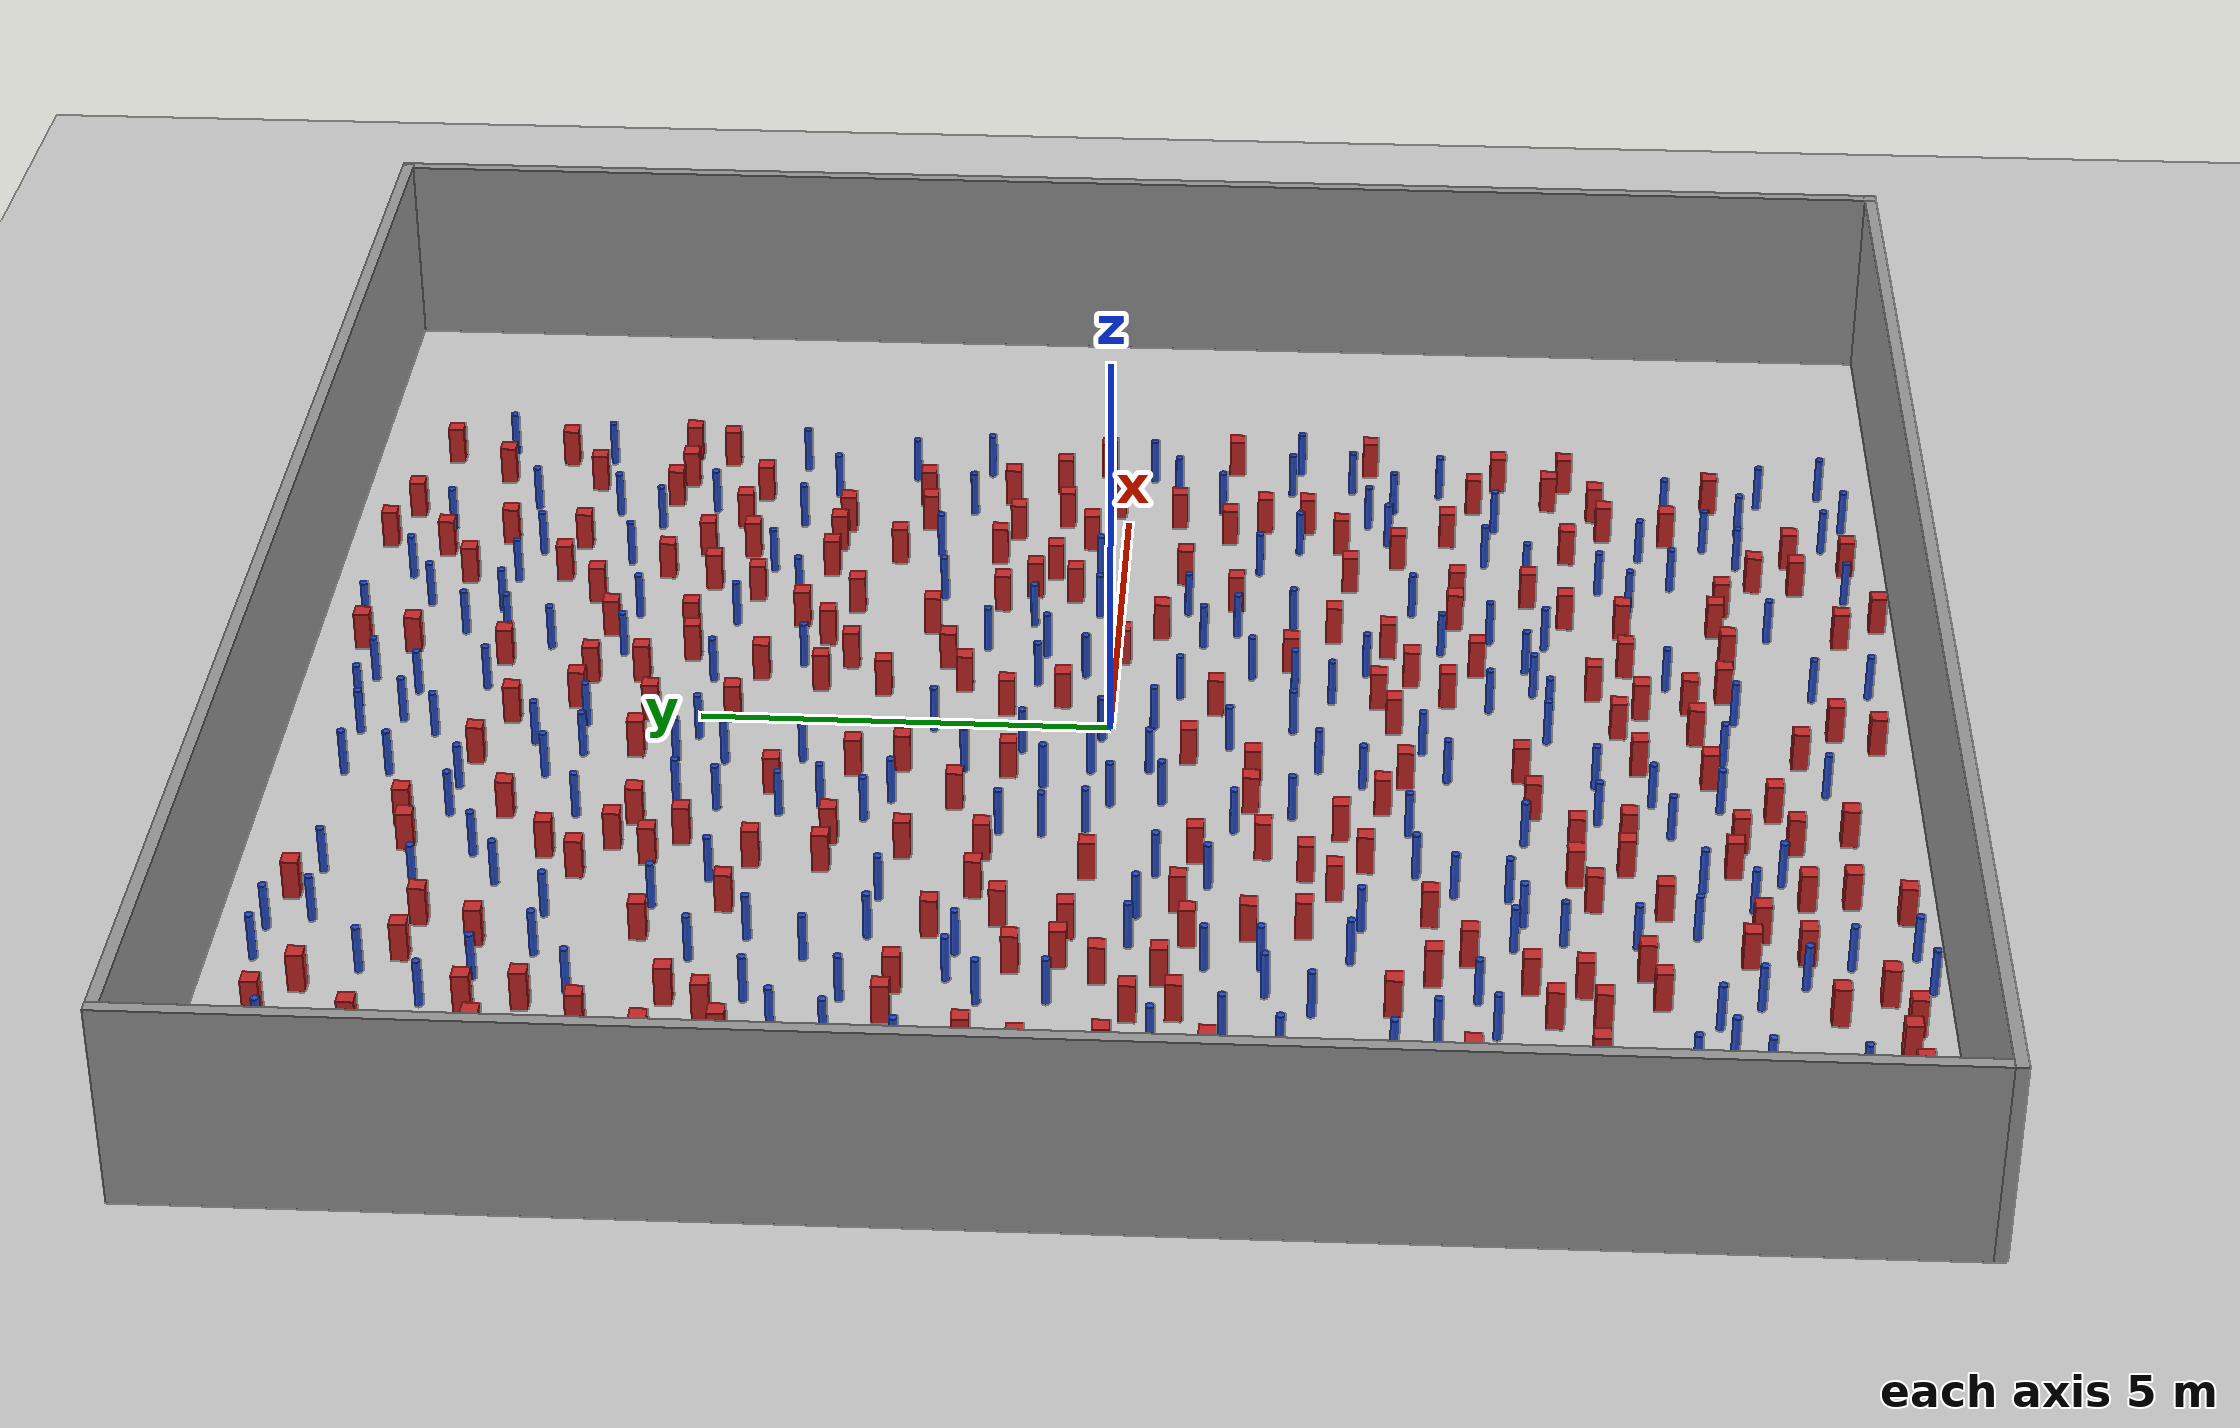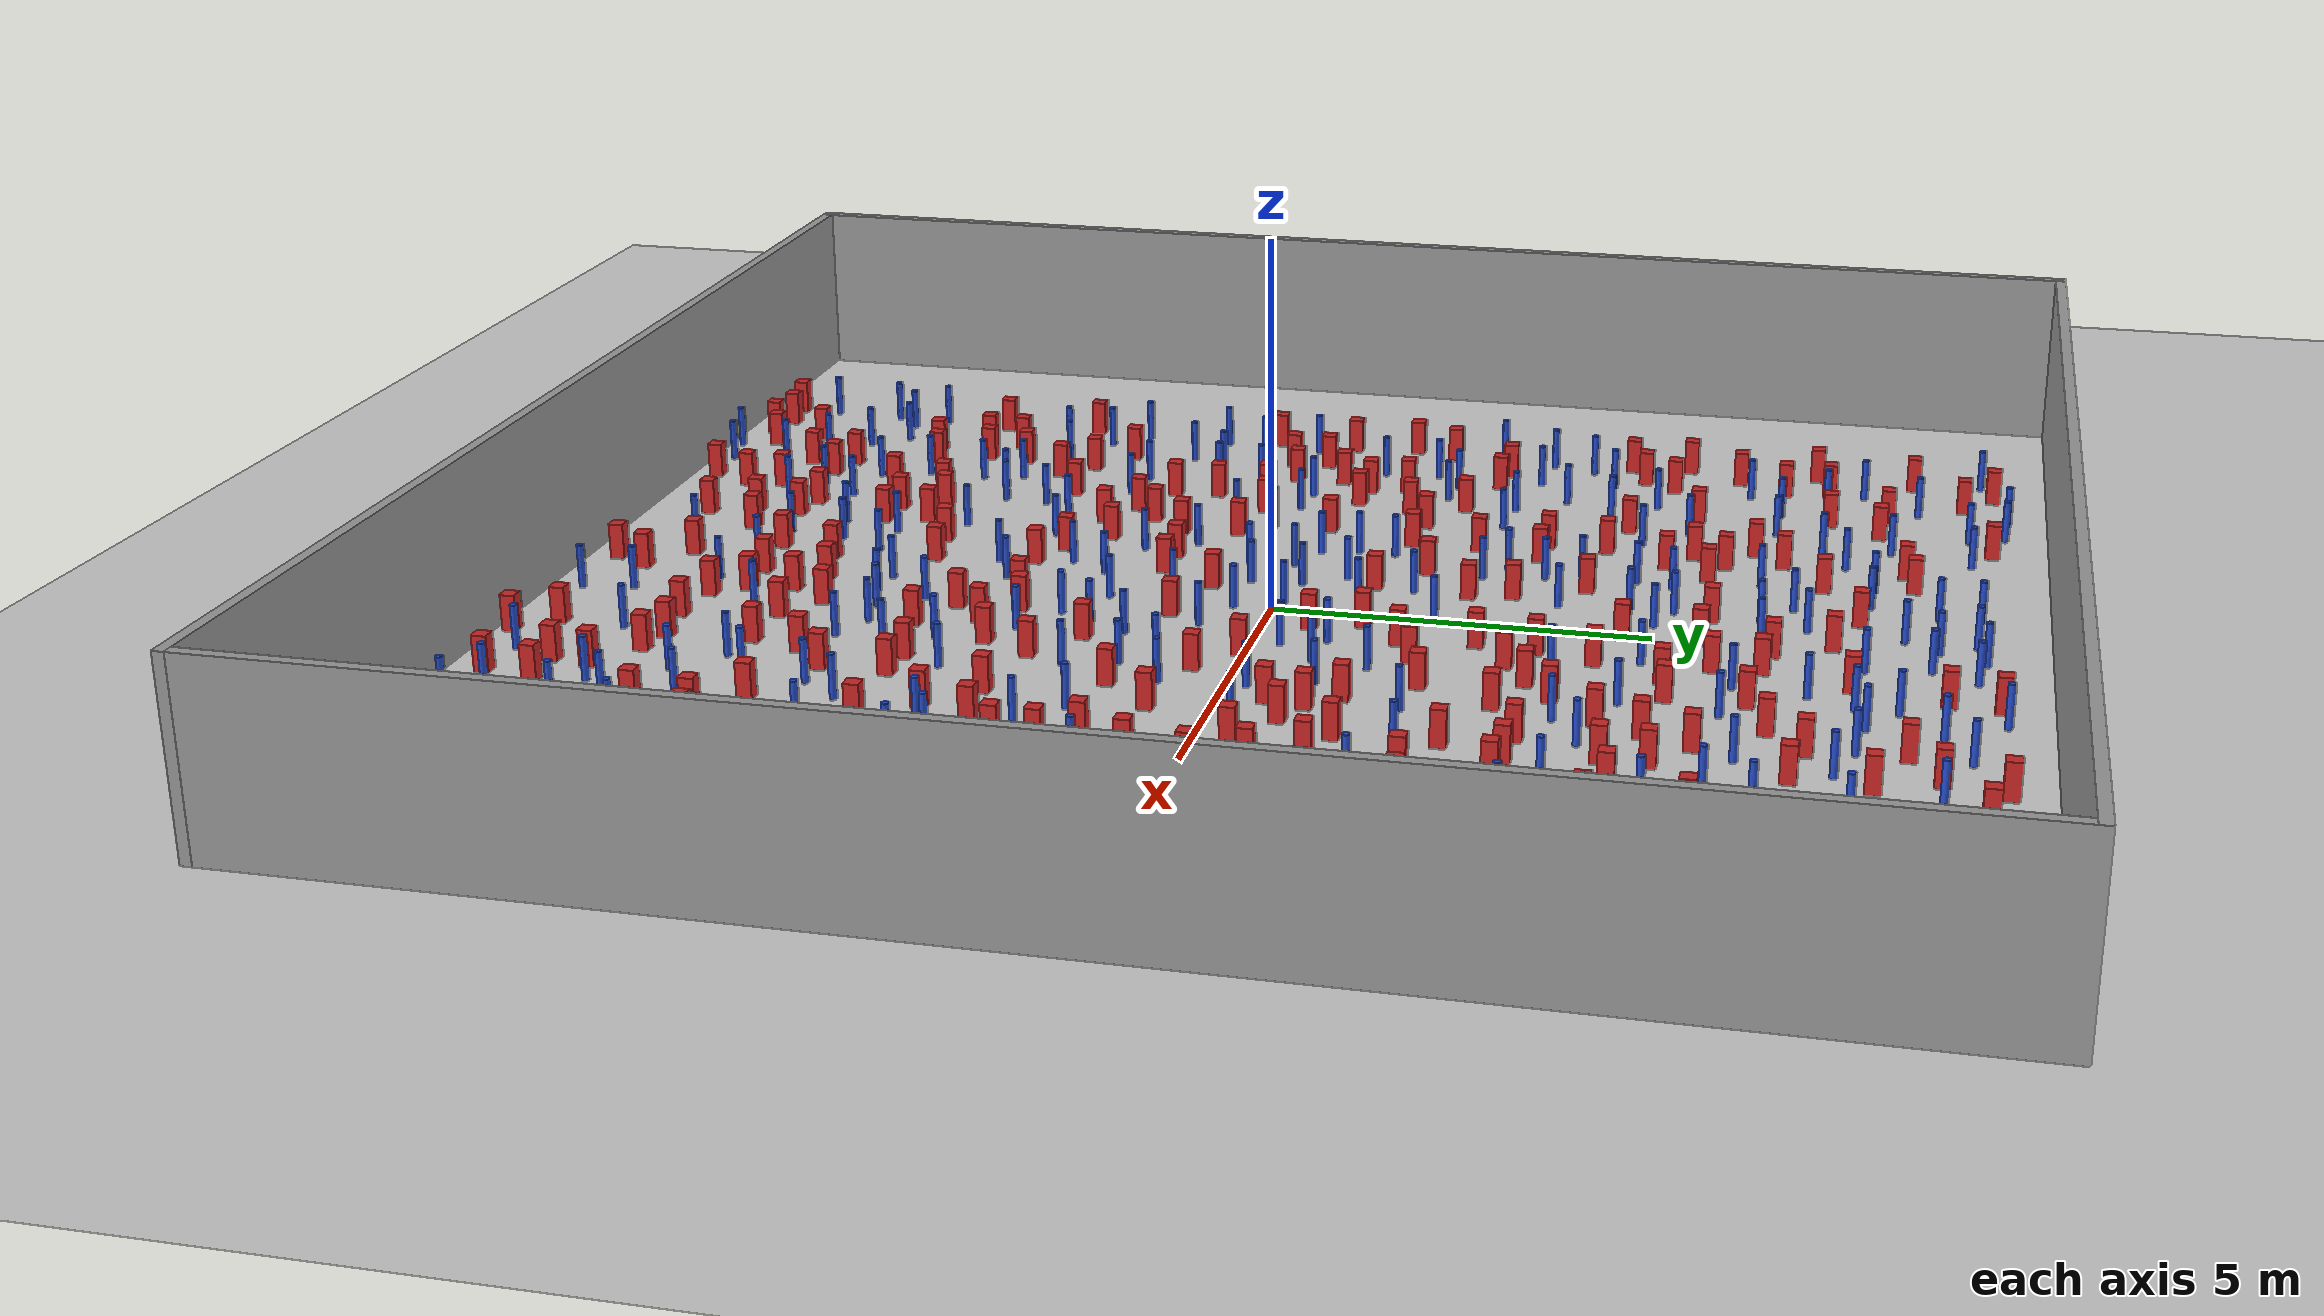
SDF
<sdf version="1.6">
 <world name="default">
  <light name="sun" type="directional">
   <pose>0 0 1000 0 -0 0</pose>
   <diffuse>0.8 0.8 0.8 1</diffuse>
   <specular>0.1 0.1 0.1 1</specular>
   <attenuation>
    <range>1000</range>
    <constant>0.9</constant>
    <linear>0.01</linear>
    <quadratic>0.001</quadratic>
   </attenuation>
   <direction>-0.5 0.5 -1</direction>
  </light>
  <model name="ground_plane">
   <static>1</static>
   <link name="link">
    <collision name="collision">
     <geometry><plane><normal>0 0 1</normal><size>100 100</size></plane></geometry>
     <surface><friction><ode><mu>100</mu><mu2>50</mu2></ode></friction></surface>
    </collision>
    <visual name="visual">
     <cast_shadows>0</cast_shadows>
     <geometry><plane><normal>0 0 1</normal><size>100 100</size></plane></geometry>
     <material>
      <ambient>1.0 1.0 1.0 1.0</ambient>
      <diffuse>0.8 0.8 0.8 1.0</diffuse>
      <specular>0.01 0.01 0.01 1.000000</specular>
     </material>
    </visual>
   </link>
  </model>
  <gravity>0 0 -9.8</gravity>
  <magnetic_field>6e-06 2.3e-05 -4.2e-05</magnetic_field>
  <atmosphere type="adiabatic"/>
  <physics name="default_physics" default="0" type="ode">
   <max_step_size>0.001</max_step_size>
   <real_time_factor>1</real_time_factor>
   <real_time_update_rate>1000</real_time_update_rate>
  </physics>
  <scene><ambient>0.4 0.4 0.4 1</ambient><background>0.7 0.7 0.7 1</background><shadows>1</shadows></scene>
  <spherical_coordinates>
   <surface_model>EARTH_WGS84</surface_model>
   <latitude_deg>0</latitude_deg>
   <longitude_deg>0</longitude_deg>
   <elevation>0</elevation>
   <heading_deg>0</heading_deg>
  </spherical_coordinates>
  <plugin name="gazebo_occupancy_map" filename="libgazebo_2Dmap_plugin.so">
   <map_resolution>0.05</map_resolution>
   <map_topic>generated_map</map_topic>
   <map_height>0.01</map_height>
   <map_size_x>50</map_size_x>
   <map_size_y>50</map_size_y>
  </plugin>
  <model name="NamedLocations">
   <static>true</static>
   <link name="DefaultStart"><pose>8.5 0 0 0 0 3.14</pose></link>
  </model>
  <model name="20x20_walls">
   <pose>0.044518 0.176112 0 0 -0 0</pose>
   <link name="Wall_1">
    <collision name="Wall_1_Collision">
     <geometry><box><size>20 0.15 2.5</size></box></geometry>
     <pose>0 0 1.25 0 -0 0</pose>
    </collision>
    <visual name="Wall_1_Visual">
     <pose>0 0 1.25 0 -0 0</pose>
     <geometry><box><size>20 0.15 2.5</size></box></geometry>
     <material>
      <script><uri>file://media/materials/scripts/gazebo.material</uri><name>Gazebo/Grey</name></script>
      <ambient>0.976471 0.992157 1 1</ambient>
     </material>
     <meta><layer>0</layer></meta>
    </visual>
    <pose>0 9.925 0 0 -0 0</pose>
   </link>
   <link name="Wall_3">
    <collision name="Wall_3_Collision">
     <geometry><box><size>20 0.15 2.5</size></box></geometry>
     <pose>0 0 1.25 0 -0 0</pose>
    </collision>
    <visual name="Wall_3_Visual">
     <pose>0 0 1.25 0 -0 0</pose>
     <geometry><box><size>20 0.15 2.5</size></box></geometry>
     <material>
      <script><uri>file://media/materials/scripts/gazebo.material</uri><name>Gazebo/Grey</name></script>
      <ambient>0.976471 0.992157 1 1</ambient>
     </material>
     <meta><layer>0</layer></meta>
    </visual>
    <pose>9.925 0 0 0 0 -1.5708</pose>
   </link>
   <link name="Wall_4">
    <collision name="Wall_4_Collision">
     <geometry><box><size>20 0.15 2.5</size></box></geometry>
     <pose>0 0 1.25 0 -0 0</pose>
    </collision>
    <visual name="Wall_4_Visual">
     <pose>0 0 1.25 0 -0 0</pose>
     <geometry><box><size>20 0.15 2.5</size></box></geometry>
     <material>
      <script><uri>file://media/materials/scripts/gazebo.material</uri><name>Gazebo/Grey</name></script>
      <ambient>0.976471 0.992157 1 1</ambient>
     </material>
     <meta><layer>0</layer></meta>
    </visual>
    <pose>0 -9.925 0 0 -0 3.14159</pose>
   </link>
   <link name="Wall_5">
    <collision name="Wall_5_Collision">
     <geometry><box><size>20 0.15 2.5</size></box></geometry>
     <pose>0 0 1.25 0 -0 0</pose>
    </collision>
    <visual name="Wall_5_Visual">
     <pose>0 0 1.25 0 -0 0</pose>
     <geometry><box><size>20 0.15 2.5</size></box></geometry>
     <material>
      <script><uri>file://media/materials/scripts/gazebo.material</uri><name>Gazebo/Grey</name></script>
      <ambient>0.976471 0.992157 1 1</ambient>
     </material>
     <meta><layer>0</layer></meta>
    </visual>
    <pose>-9.925 0 0 0 -0 1.5708</pose>
   </link>
   <static>1</static>
  </model>
  <model name="pole_obstacle0">
   <static>true</static>
   <pose>2.39526000976 1.07714002078 -3.09024884793e-07 -7.19054271911e-07 -2.11315075167e-07 -1.93935509283e-07</pose>
   <link name="link">
    <pose>0 0 0.3 0 -0 0</pose>
    <inertial>
     <mass>1</mass>
     <inertia><ixx>0.145833</ixx><ixy>0</ixy><ixz>0</ixz><iyy>0.145833</iyy><iyz>0</iyz><izz>0.125</izz></inertia>
    </inertial>
    <collision name="collision">
     <geometry><cylinder><radius>0.05</radius><length>.6</length></cylinder></geometry>
    </collision>
    <visual name="visual">
     <geometry><cylinder><radius>0.05</radius><length>.6</length></cylinder></geometry>
     <material>
      <script><name>Gazebo/Blue</name><uri>file://media/materials/scripts/gazebo.material</uri></script>
     </material>
    </visual>
   </link>
  </model>
  <model name="pole_obstacle1">
   <static>true</static>
   <pose>-0.901617990239 3.67017002078 -3.09024884848e-07 -7.19054271902e-07 -2.11315075191e-07 -1.9393550928e-07</pose>
   <link name="link">
    <pose>0 0 0.3 0 -0 0</pose>
    <inertial>
     <mass>1</mass>
     <inertia><ixx>0.145833</ixx><ixy>0</ixy><ixz>0</ixz><iyy>0.145833</iyy><iyz>0</iyz><izz>0.125</izz></inertia>
    </inertial>
    <collision name="collision">
     <geometry><cylinder><radius>0.05</radius><length>.6</length></cylinder></geometry>
    </collision>
    <visual name="visual">
     <geometry><cylinder><radius>0.05</radius><length>.6</length></cylinder></geometry>
     <material>
      <script><name>Gazebo/Blue</name><uri>file://media/materials/scripts/gazebo.material</uri></script>
     </material>
    </visual>
   </link>
  </model>
  <model name="square_post_obstacle0">
   <static>true</static>
   <pose>2.2371800552 -2.67245002533 -4.36207812815e-07 3.75137919937e-06 9.77721102514e-07 2.47381364184e-05</pose>
   <link name="link">
    <pose>0 0 0.25 0 -0 0</pose>
    <inertial>
     <mass>100</mass>
     <inertia>
      <ixx>0.166667</ixx>
      <ixy>0</ixy>
      <ixz>0</ixz>
      <iyy>0.166667</iyy>
      <iyz>0</iyz>
      <izz>0.166667</izz>
     </inertia>
    </inertial>
    <collision name="collision"><geometry><box><size>.2 .2 .5</size></box></geometry></collision>
    <visual name="visual">
     <geometry><box><size>.2 .2 .5</size></box></geometry>
     <material>
      <script><name>Gazebo/Red</name><uri>file://media/materials/scripts/gazebo.material</uri></script>
     </material>
    </visual>
   </link>
  </model>
  <model name="square_post_obstacle1">
   <static>true</static>
   <pose>0.704501055196 -3.23381002533 -4.36207812815e-07 3.75137919937e-06 9.77721102514e-07 2.47381364184e-05</pose>
   <link name="link">
    <pose>0 0 0.25 0 -0 0</pose>
    <inertial>
     <mass>100</mass>
     <inertia>
      <ixx>0.166667</ixx>
      <ixy>0</ixy>
      <ixz>0</ixz>
      <iyy>0.166667</iyy>
      <iyz>0</iyz>
      <izz>0.166667</izz>
     </inertia>
    </inertial>
    <collision name="collision"><geometry><box><size>.2 .2 .5</size></box></geometry></collision>
    <visual name="visual">
     <geometry><box><size>.2 .2 .5</size></box></geometry>
     <material>
      <script><name>Gazebo/Red</name><uri>file://media/materials/scripts/gazebo.material</uri></script>
     </material>
    </visual>
   </link>
  </model>
  <model name="pole_obstacle2">
   <static>true</static>
   <pose>-3.81581999024 2.50415002078 -3.09024884793e-07 -7.19054271912e-07 -2.11315075128e-07 -1.93935509262e-07</pose>
   <link name="link">
    <pose>0 0 0.3 0 -0 0</pose>
    <inertial>
     <mass>1</mass>
     <inertia><ixx>0.145833</ixx><ixy>0</ixy><ixz>0</ixz><iyy>0.145833</iyy><iyz>0</iyz><izz>0.125</izz></inertia>
    </inertial>
    <collision name="collision">
     <geometry><cylinder><radius>0.05</radius><length>.6</length></cylinder></geometry>
    </collision>
    <visual name="visual">
     <geometry><cylinder><radius>0.05</radius><length>.6</length></cylinder></geometry>
     <material>
      <script><name>Gazebo/Blue</name><uri>file://media/materials/scripts/gazebo.material</uri></script>
     </material>
    </visual>
   </link>
  </model>
  <model name="pole_obstacle3">
   <static>true</static>
   <pose>5.06081000976 -3.08659997922 -3.09024884793e-07 -7.19054271912e-07 -2.11315075144e-07 -1.93935509269e-07</pose>
   <link name="link">
    <pose>0 0 0.3 0 -0 0</pose>
    <inertial>
     <mass>1</mass>
     <inertia><ixx>0.145833</ixx><ixy>0</ixy><ixz>0</ixz><iyy>0.145833</iyy><iyz>0</iyz><izz>0.125</izz></inertia>
    </inertial>
    <collision name="collision">
     <geometry><cylinder><radius>0.05</radius><length>.6</length></cylinder></geometry>
    </collision>
    <visual name="visual">
     <geometry><cylinder><radius>0.05</radius><length>.6</length></cylinder></geometry>
     <material>
      <script><name>Gazebo/Blue</name><uri>file://media/materials/scripts/gazebo.material</uri></script>
     </material>
    </visual>
   </link>
  </model>
  <model name="pole_obstacle4">
   <static>true</static>
   <pose>1.23686000976 -6.76080997922 -3.09024884793e-07 -7.19054271912e-07 -2.11315075134e-07 -1.93935509265e-07</pose>
   <link name="link">
    <pose>0 0 0.3 0 -0 0</pose>
    <inertial>
     <mass>1</mass>
     <inertia><ixx>0.145833</ixx><ixy>0</ixy><ixz>0</ixz><iyy>0.145833</iyy><iyz>0</iyz><izz>0.125</izz></inertia>
    </inertial>
    <collision name="collision">
     <geometry><cylinder><radius>0.05</radius><length>.6</length></cylinder></geometry>
    </collision>
    <visual name="visual">
     <geometry><cylinder><radius>0.05</radius><length>.6</length></cylinder></geometry>
     <material>
      <script><name>Gazebo/Blue</name><uri>file://media/materials/scripts/gazebo.material</uri></script>
     </material>
    </visual>
   </link>
  </model>
  <model name="pole_obstacle5">
   <static>true</static>
   <pose>-1.45639999024 9.13431002078 -3.09024884793e-07 -7.19054271912e-07 -2.1131507515e-07 -1.93935509273e-07</pose>
   <link name="link">
    <pose>0 0 0.3 0 -0 0</pose>
    <inertial>
     <mass>1</mass>
     <inertia><ixx>0.145833</ixx><ixy>0</ixy><ixz>0</ixz><iyy>0.145833</iyy><iyz>0</iyz><izz>0.125</izz></inertia>
    </inertial>
    <collision name="collision">
     <geometry><cylinder><radius>0.05</radius><length>.6</length></cylinder></geometry>
    </collision>
    <visual name="visual">
     <geometry><cylinder><radius>0.05</radius><length>.6</length></cylinder></geometry>
     <material>
      <script><name>Gazebo/Blue</name><uri>file://media/materials/scripts/gazebo.material</uri></script>
     </material>
    </visual>
   </link>
  </model>
  <model name="pole_obstacle6">
   <static>true</static>
   <pose>-0.533564990239 9.09575002078 -3.09024884793e-07 -7.19054271912e-07 -2.11315075159e-07 -1.93935509278e-07</pose>
   <link name="link">
    <pose>0 0 0.3 0 -0 0</pose>
    <inertial>
     <mass>1</mass>
     <inertia><ixx>0.145833</ixx><ixy>0</ixy><ixz>0</ixz><iyy>0.145833</iyy><iyz>0</iyz><izz>0.125</izz></inertia>
    </inertial>
    <collision name="collision">
     <geometry><cylinder><radius>0.05</radius><length>.6</length></cylinder></geometry>
    </collision>
    <visual name="visual">
     <geometry><cylinder><radius>0.05</radius><length>.6</length></cylinder></geometry>
     <material>
      <script><name>Gazebo/Blue</name><uri>file://media/materials/scripts/gazebo.material</uri></script>
     </material>
    </visual>
   </link>
  </model>
  <model name="square_post_obstacle2">
   <static>true</static>
   <pose>4.7412000552 4.96197997467 -4.36207812815e-07 3.75137919937e-06 9.77721102514e-07 2.47381364184e-05</pose>
   <link name="link">
    <pose>0 0 0.25 0 -0 0</pose>
    <inertial>
     <mass>100</mass>
     <inertia>
      <ixx>0.166667</ixx>
      <ixy>0</ixy>
      <ixz>0</ixz>
      <iyy>0.166667</iyy>
      <iyz>0</iyz>
      <izz>0.166667</izz>
     </inertia>
    </inertial>
    <collision name="collision"><geometry><box><size>.2 .2 .5</size></box></geometry></collision>
    <visual name="visual">
     <geometry><box><size>.2 .2 .5</size></box></geometry>
     <material>
      <script><name>Gazebo/Red</name><uri>file://media/materials/scripts/gazebo.material</uri></script>
     </material>
    </visual>
   </link>
  </model>
  <model name="square_post_obstacle3">
   <static>true</static>
   <pose>4.9316800552 -6.10498002533 -4.36207812815e-07 3.75137919937e-06 9.77721102514e-07 2.47381364184e-05</pose>
   <link name="link">
    <pose>0 0 0.25 0 -0 0</pose>
    <inertial>
     <mass>100</mass>
     <inertia>
      <ixx>0.166667</ixx>
      <ixy>0</ixy>
      <ixz>0</ixz>
      <iyy>0.166667</iyy>
      <iyz>0</iyz>
      <izz>0.166667</izz>
     </inertia>
    </inertial>
    <collision name="collision"><geometry><box><size>.2 .2 .5</size></box></geometry></collision>
    <visual name="visual">
     <geometry><box><size>.2 .2 .5</size></box></geometry>
     <material>
      <script><name>Gazebo/Red</name><uri>file://media/materials/scripts/gazebo.material</uri></script>
     </material>
    </visual>
   </link>
  </model>
  <model name="square_post_obstacle4">
   <static>true</static>
   <pose>0.746468055196 -7.02115002533 -4.36207812815e-07 3.75137919937e-06 9.77721102514e-07 2.47381364184e-05</pose>
   <link name="link">
    <pose>0 0 0.25 0 -0 0</pose>
    <inertial>
     <mass>100</mass>
     <inertia>
      <ixx>0.166667</ixx>
      <ixy>0</ixy>
      <ixz>0</ixz>
      <iyy>0.166667</iyy>
      <iyz>0</iyz>
      <izz>0.166667</izz>
     </inertia>
    </inertial>
    <collision name="collision"><geometry><box><size>.2 .2 .5</size></box></geometry></collision>
    <visual name="visual">
     <geometry><box><size>.2 .2 .5</size></box></geometry>
     <material>
      <script><name>Gazebo/Red</name><uri>file://media/materials/scripts/gazebo.material</uri></script>
     </material>
    </visual>
   </link>
  </model>
  <model name="pole_obstacle7">
   <static>true</static>
   <pose>-5.88980999024 -2.51619997922 -3.09024884793e-07 -7.19054271912e-07 -2.11315075135e-07 -1.93935509265e-07</pose>
   <link name="link">
    <pose>0 0 0.3 0 -0 0</pose>
    <inertial>
     <mass>1</mass>
     <inertia><ixx>0.145833</ixx><ixy>0</ixy><ixz>0</ixz><iyy>0.145833</iyy><iyz>0</iyz><izz>0.125</izz></inertia>
    </inertial>
    <collision name="collision">
     <geometry><cylinder><radius>0.05</radius><length>.6</length></cylinder></geometry>
    </collision>
    <visual name="visual">
     <geometry><cylinder><radius>0.05</radius><length>.6</length></cylinder></geometry>
     <material>
      <script><name>Gazebo/Blue</name><uri>file://media/materials/scripts/gazebo.material</uri></script>
     </material>
    </visual>
   </link>
  </model>
  <model name="pole_obstacle8">
   <static>true</static>
   <pose>-6.73233999024 -2.18094997922 -3.09024884793e-07 -7.19054271912e-07 -2.11315075144e-07 -1.93935509269e-07</pose>
   <link name="link">
    <pose>0 0 0.3 0 -0 0</pose>
    <inertial>
     <mass>1</mass>
     <inertia><ixx>0.145833</ixx><ixy>0</ixy><ixz>0</ixz><iyy>0.145833</iyy><iyz>0</iyz><izz>0.125</izz></inertia>
    </inertial>
    <collision name="collision">
     <geometry><cylinder><radius>0.05</radius><length>.6</length></cylinder></geometry>
    </collision>
    <visual name="visual">
     <geometry><cylinder><radius>0.05</radius><length>.6</length></cylinder></geometry>
     <material>
      <script><name>Gazebo/Blue</name><uri>file://media/materials/scripts/gazebo.material</uri></script>
     </material>
    </visual>
   </link>
  </model>
  <model name="square_post_obstacle5">
   <static>true</static>
   <pose>1.0357000552 -7.44995002533 -4.36207812815e-07 3.75137919937e-06 9.77721102514e-07 2.47381364184e-05</pose>
   <link name="link">
    <pose>0 0 0.25 0 -0 0</pose>
    <inertial>
     <mass>100</mass>
     <inertia>
      <ixx>0.166667</ixx>
      <ixy>0</ixy>
      <ixz>0</ixz>
      <iyy>0.166667</iyy>
      <iyz>0</iyz>
      <izz>0.166667</izz>
     </inertia>
    </inertial>
    <collision name="collision"><geometry><box><size>.2 .2 .5</size></box></geometry></collision>
    <visual name="visual">
     <geometry><box><size>.2 .2 .5</size></box></geometry>
     <material>
      <script><name>Gazebo/Red</name><uri>file://media/materials/scripts/gazebo.material</uri></script>
     </material>
    </visual>
   </link>
  </model>
  <model name="square_post_obstacle6">
   <static>true</static>
   <pose>-0.422860944804 -8.28841002533 -4.36207812815e-07 3.75137919937e-06 9.77721102514e-07 2.47381364184e-05</pose>
   <link name="link">
    <pose>0 0 0.25 0 -0 0</pose>
    <inertial>
     <mass>100</mass>
     <inertia>
      <ixx>0.166667</ixx>
      <ixy>0</ixy>
      <ixz>0</ixz>
      <iyy>0.166667</iyy>
      <iyz>0</iyz>
      <izz>0.166667</izz>
     </inertia>
    </inertial>
    <collision name="collision"><geometry><box><size>.2 .2 .5</size></box></geometry></collision>
    <visual name="visual">
     <geometry><box><size>.2 .2 .5</size></box></geometry>
     <material>
      <script><name>Gazebo/Red</name><uri>file://media/materials/scripts/gazebo.material</uri></script>
     </material>
    </visual>
   </link>
  </model>
  <model name="square_post_obstacle7">
   <static>true</static>
   <pose>-2.8676599448 2.30549997467 -4.36207812815e-07 3.75137919937e-06 9.77721102514e-07 2.47381364184e-05</pose>
   <link name="link">
    <pose>0 0 0.25 0 -0 0</pose>
    <inertial>
     <mass>100</mass>
     <inertia>
      <ixx>0.166667</ixx>
      <ixy>0</ixy>
      <ixz>0</ixz>
      <iyy>0.166667</iyy>
      <iyz>0</iyz>
      <izz>0.166667</izz>
     </inertia>
    </inertial>
    <collision name="collision"><geometry><box><size>.2 .2 .5</size></box></geometry></collision>
    <visual name="visual">
     <geometry><box><size>.2 .2 .5</size></box></geometry>
     <material>
      <script><name>Gazebo/Red</name><uri>file://media/materials/scripts/gazebo.material</uri></script>
     </material>
    </visual>
   </link>
  </model>
  <model name="pole_obstacle9">
   <static>true</static>
   <pose>4.71993000976 -8.90393997922 -3.09024884793e-07 -7.19054271912e-07 -2.1131507513e-07 -1.93935509261e-07</pose>
   <link name="link">
    <pose>0 0 0.3 0 -0 0</pose>
    <inertial>
     <mass>1</mass>
     <inertia><ixx>0.145833</ixx><ixy>0</ixy><ixz>0</ixz><iyy>0.145833</iyy><iyz>0</iyz><izz>0.125</izz></inertia>
    </inertial>
    <collision name="collision">
     <geometry><cylinder><radius>0.05</radius><length>.6</length></cylinder></geometry>
    </collision>
    <visual name="visual">
     <geometry><cylinder><radius>0.05</radius><length>.6</length></cylinder></geometry>
     <material>
      <script><name>Gazebo/Blue</name><uri>file://media/materials/scripts/gazebo.material</uri></script>
     </material>
    </visual>
   </link>
  </model>
  <model name="pole_obstacle10">
   <static>true</static>
   <pose>2.26384000976 -1.47178997922 -3.09024884793e-07 -7.19054271912e-07 -2.11315075122e-07 -1.93935509259e-07</pose>
   <link name="link">
    <pose>0 0 0.3 0 -0 0</pose>
    <inertial>
     <mass>1</mass>
     <inertia><ixx>0.145833</ixx><ixy>0</ixy><ixz>0</ixz><iyy>0.145833</iyy><iyz>0</iyz><izz>0.125</izz></inertia>
    </inertial>
    <collision name="collision">
     <geometry><cylinder><radius>0.05</radius><length>.6</length></cylinder></geometry>
    </collision>
    <visual name="visual">
     <geometry><cylinder><radius>0.05</radius><length>.6</length></cylinder></geometry>
     <material>
      <script><name>Gazebo/Blue</name><uri>file://media/materials/scripts/gazebo.material</uri></script>
     </material>
    </visual>
   </link>
  </model>
  <model name="pole_obstacle11">
   <static>true</static>
   <pose>0.473898009761 -7.55703997922 -3.09024884793e-07 -7.19054271912e-07 -2.11315075125e-07 -1.93935509259e-07</pose>
   <link name="link">
    <pose>0 0 0.3 0 -0 0</pose>
    <inertial>
     <mass>1</mass>
     <inertia><ixx>0.145833</ixx><ixy>0</ixy><ixz>0</ixz><iyy>0.145833</iyy><iyz>0</iyz><izz>0.125</izz></inertia>
    </inertial>
    <collision name="collision">
     <geometry><cylinder><radius>0.05</radius><length>.6</length></cylinder></geometry>
    </collision>
    <visual name="visual">
     <geometry><cylinder><radius>0.05</radius><length>.6</length></cylinder></geometry>
     <material>
      <script><name>Gazebo/Blue</name><uri>file://media/materials/scripts/gazebo.material</uri></script>
     </material>
    </visual>
   </link>
  </model>
  <model name="pole_obstacle12">
   <static>true</static>
   <pose>6.03670000976 2.83938002078 -3.09024884793e-07 -7.19054271912e-07 -2.11315075135e-07 -1.93935509265e-07</pose>
   <link name="link">
    <pose>0 0 0.3 0 -0 0</pose>
    <inertial>
     <mass>1</mass>
     <inertia><ixx>0.145833</ixx><ixy>0</ixy><ixz>0</ixz><iyy>0.145833</iyy><iyz>0</iyz><izz>0.125</izz></inertia>
    </inertial>
    <collision name="collision">
     <geometry><cylinder><radius>0.05</radius><length>.6</length></cylinder></geometry>
    </collision>
    <visual name="visual">
     <geometry><cylinder><radius>0.05</radius><length>.6</length></cylinder></geometry>
     <material>
      <script><name>Gazebo/Blue</name><uri>file://media/materials/scripts/gazebo.material</uri></script>
     </material>
    </visual>
   </link>
  </model>
  <model name="square_post_obstacle8">
   <static>true</static>
   <pose>4.9464400552 -1.75761002533 -4.36207812815e-07 3.75137919937e-06 9.77721102514e-07 2.47381364184e-05</pose>
   <link name="link">
    <pose>0 0 0.25 0 -0 0</pose>
    <inertial>
     <mass>100</mass>
     <inertia>
      <ixx>0.166667</ixx>
      <ixy>0</ixy>
      <ixz>0</ixz>
      <iyy>0.166667</iyy>
      <iyz>0</iyz>
      <izz>0.166667</izz>
     </inertia>
    </inertial>
    <collision name="collision"><geometry><box><size>.2 .2 .5</size></box></geometry></collision>
    <visual name="visual">
     <geometry><box><size>.2 .2 .5</size></box></geometry>
     <material>
      <script><name>Gazebo/Red</name><uri>file://media/materials/scripts/gazebo.material</uri></script>
     </material>
    </visual>
   </link>
  </model>
  <model name="square_post_obstacle9">
   <static>true</static>
   <pose>-3.1272499448 -2.40542002533 -4.36207812815e-07 3.75137919937e-06 9.77721102514e-07 2.47381364184e-05</pose>
   <link name="link">
    <pose>0 0 0.25 0 -0 0</pose>
    <inertial>
     <mass>100</mass>
     <inertia>
      <ixx>0.166667</ixx>
      <ixy>0</ixy>
      <ixz>0</ixz>
      <iyy>0.166667</iyy>
      <iyz>0</iyz>
      <izz>0.166667</izz>
     </inertia>
    </inertial>
    <collision name="collision"><geometry><box><size>.2 .2 .5</size></box></geometry></collision>
    <visual name="visual">
     <geometry><box><size>.2 .2 .5</size></box></geometry>
     <material>
      <script><name>Gazebo/Red</name><uri>file://media/materials/scripts/gazebo.material</uri></script>
     </material>
    </visual>
   </link>
  </model>
  <model name="pole_obstacle13">
   <static>true</static>
   <pose>1.55174000976 7.05939002078 -3.09024884793e-07 -7.19054271912e-07 -2.11315075132e-07 -1.93935509264e-07</pose>
   <link name="link">
    <pose>0 0 0.3 0 -0 0</pose>
    <inertial>
     <mass>1</mass>
     <inertia><ixx>0.145833</ixx><ixy>0</ixy><ixz>0</ixz><iyy>0.145833</iyy><iyz>0</iyz><izz>0.125</izz></inertia>
    </inertial>
    <collision name="collision">
     <geometry><cylinder><radius>0.05</radius><length>.6</length></cylinder></geometry>
    </collision>
    <visual name="visual">
     <geometry><cylinder><radius>0.05</radius><length>.6</length></cylinder></geometry>
     <material>
      <script><name>Gazebo/Blue</name><uri>file://media/materials/scripts/gazebo.material</uri></script>
     </material>
    </visual>
   </link>
  </model>
  <model name="square_post_obstacle10">
   <static>true</static>
   <pose>6.4958900552 5.82938997467 -4.36207812815e-07 3.75137919937e-06 9.77721102514e-07 2.47381364184e-05</pose>
   <link name="link">
    <pose>0 0 0.25 0 -0 0</pose>
    <inertial>
     <mass>100</mass>
     <inertia>
      <ixx>0.166667</ixx>
      <ixy>0</ixy>
      <ixz>0</ixz>
      <iyy>0.166667</iyy>
      <iyz>0</iyz>
      <izz>0.166667</izz>
     </inertia>
    </inertial>
    <collision name="collision"><geometry><box><size>.2 .2 .5</size></box></geometry></collision>
    <visual name="visual">
     <geometry><box><size>.2 .2 .5</size></box></geometry>
     <material>
      <script><name>Gazebo/Red</name><uri>file://media/materials/scripts/gazebo.material</uri></script>
     </material>
    </visual>
   </link>
  </model>
  <model name="square_post_obstacle11">
   <static>true</static>
   <pose>-3.0610999448 6.48294997467 -4.36207812815e-07 3.75137919937e-06 9.77721102514e-07 2.47381364184e-05</pose>
   <link name="link">
    <pose>0 0 0.25 0 -0 0</pose>
    <inertial>
     <mass>100</mass>
     <inertia>
      <ixx>0.166667</ixx>
      <ixy>0</ixy>
      <ixz>0</ixz>
      <iyy>0.166667</iyy>
      <iyz>0</iyz>
      <izz>0.166667</izz>
     </inertia>
    </inertial>
    <collision name="collision"><geometry><box><size>.2 .2 .5</size></box></geometry></collision>
    <visual name="visual">
     <geometry><box><size>.2 .2 .5</size></box></geometry>
     <material>
      <script><name>Gazebo/Red</name><uri>file://media/materials/scripts/gazebo.material</uri></script>
     </material>
    </visual>
   </link>
  </model>
  <model name="pole_obstacle14">
   <static>true</static>
   <pose>3.79471000976 -1.71364997922 -3.09024884793e-07 -7.19054271911e-07 -2.11315075167e-07 -1.93935509283e-07</pose>
   <link name="link">
    <pose>0 0 0.3 0 -0 0</pose>
    <inertial>
     <mass>1</mass>
     <inertia><ixx>0.145833</ixx><ixy>0</ixy><ixz>0</ixz><iyy>0.145833</iyy><iyz>0</iyz><izz>0.125</izz></inertia>
    </inertial>
    <collision name="collision">
     <geometry><cylinder><radius>0.05</radius><length>.6</length></cylinder></geometry>
    </collision>
    <visual name="visual">
     <geometry><cylinder><radius>0.05</radius><length>.6</length></cylinder></geometry>
     <material>
      <script><name>Gazebo/Blue</name><uri>file://media/materials/scripts/gazebo.material</uri></script>
     </material>
    </visual>
   </link>
  </model>
  <model name="pole_obstacle15">
   <static>true</static>
   <pose>2.23217000976 -4.61184997922 -3.09024884793e-07 -7.19054271912e-07 -2.11315075134e-07 -1.93935509266e-07</pose>
   <link name="link">
    <pose>0 0 0.3 0 -0 0</pose>
    <inertial>
     <mass>1</mass>
     <inertia><ixx>0.145833</ixx><ixy>0</ixy><ixz>0</ixz><iyy>0.145833</iyy><iyz>0</iyz><izz>0.125</izz></inertia>
    </inertial>
    <collision name="collision">
     <geometry><cylinder><radius>0.05</radius><length>.6</length></cylinder></geometry>
    </collision>
    <visual name="visual">
     <geometry><cylinder><radius>0.05</radius><length>.6</length></cylinder></geometry>
     <material>
      <script><name>Gazebo/Blue</name><uri>file://media/materials/scripts/gazebo.material</uri></script>
     </material>
    </visual>
   </link>
  </model>
  <model name="square_post_obstacle12">
   <static>true</static>
   <pose>-2.2902099448 -7.47595002533 -4.36207812815e-07 3.75137919937e-06 9.77721102514e-07 2.47381364184e-05</pose>
   <link name="link">
    <pose>0 0 0.25 0 -0 0</pose>
    <inertial>
     <mass>100</mass>
     <inertia>
      <ixx>0.166667</ixx>
      <ixy>0</ixy>
      <ixz>0</ixz>
      <iyy>0.166667</iyy>
      <iyz>0</iyz>
      <izz>0.166667</izz>
     </inertia>
    </inertial>
    <collision name="collision"><geometry><box><size>.2 .2 .5</size></box></geometry></collision>
    <visual name="visual">
     <geometry><box><size>.2 .2 .5</size></box></geometry>
     <material>
      <script><name>Gazebo/Red</name><uri>file://media/materials/scripts/gazebo.material</uri></script>
     </material>
    </visual>
   </link>
  </model>
  <model name="pole_obstacle16">
   <static>true</static>
   <pose>4.23274000976 -7.78472997922 -3.09024884793e-07 -7.19054271911e-07 -2.1131507516e-07 -1.93935509277e-07</pose>
   <link name="link">
    <pose>0 0 0.3 0 -0 0</pose>
    <inertial>
     <mass>1</mass>
     <inertia><ixx>0.145833</ixx><ixy>0</ixy><ixz>0</ixz><iyy>0.145833</iyy><iyz>0</iyz><izz>0.125</izz></inertia>
    </inertial>
    <collision name="collision">
     <geometry><cylinder><radius>0.05</radius><length>.6</length></cylinder></geometry>
    </collision>
    <visual name="visual">
     <geometry><cylinder><radius>0.05</radius><length>.6</length></cylinder></geometry>
     <material>
      <script><name>Gazebo/Blue</name><uri>file://media/materials/scripts/gazebo.material</uri></script>
     </material>
    </visual>
   </link>
  </model>
  <model name="pole_obstacle17">
   <static>true</static>
   <pose>4.37244000976 -6.54633997922 -3.09024884793e-07 -7.19054271911e-07 -2.1131507516e-07 -1.93935509277e-07</pose>
   <link name="link">
    <pose>0 0 0.3 0 -0 0</pose>
    <inertial>
     <mass>1</mass>
     <inertia><ixx>0.145833</ixx><ixy>0</ixy><ixz>0</ixz><iyy>0.145833</iyy><iyz>0</iyz><izz>0.125</izz></inertia>
    </inertial>
    <collision name="collision">
     <geometry><cylinder><radius>0.05</radius><length>.6</length></cylinder></geometry>
    </collision>
    <visual name="visual">
     <geometry><cylinder><radius>0.05</radius><length>.6</length></cylinder></geometry>
     <material>
      <script><name>Gazebo/Blue</name><uri>file://media/materials/scripts/gazebo.material</uri></script>
     </material>
    </visual>
   </link>
  </model>
  <model name="square_post_obstacle13">
   <static>true</static>
   <pose>0.0591860551963 -7.06688002533 -4.36207812815e-07 3.75137919937e-06 9.77721102514e-07 2.47381364184e-05</pose>
   <link name="link">
    <pose>0 0 0.25 0 -0 0</pose>
    <inertial>
     <mass>100</mass>
     <inertia>
      <ixx>0.166667</ixx>
      <ixy>0</ixy>
      <ixz>0</ixz>
      <iyy>0.166667</iyy>
      <iyz>0</iyz>
      <izz>0.166667</izz>
     </inertia>
    </inertial>
    <collision name="collision"><geometry><box><size>.2 .2 .5</size></box></geometry></collision>
    <visual name="visual">
     <geometry><box><size>.2 .2 .5</size></box></geometry>
     <material>
      <script><name>Gazebo/Red</name><uri>file://media/materials/scripts/gazebo.material</uri></script>
     </material>
    </visual>
   </link>
  </model>
  <model name="pole_obstacle18">
   <static>true</static>
   <pose>2.45069000976 -8.07077997922 -3.09024884848e-07 -7.19054271902e-07 -2.11315075199e-07 -1.93935509286e-07</pose>
   <link name="link">
    <pose>0 0 0.3 0 -0 0</pose>
    <inertial>
     <mass>1</mass>
     <inertia><ixx>0.145833</ixx><ixy>0</ixy><ixz>0</ixz><iyy>0.145833</iyy><iyz>0</iyz><izz>0.125</izz></inertia>
    </inertial>
    <collision name="collision">
     <geometry><cylinder><radius>0.05</radius><length>.6</length></cylinder></geometry>
    </collision>
    <visual name="visual">
     <geometry><cylinder><radius>0.05</radius><length>.6</length></cylinder></geometry>
     <material>
      <script><name>Gazebo/Blue</name><uri>file://media/materials/scripts/gazebo.material</uri></script>
     </material>
    </visual>
   </link>
  </model>
  <model name="square_post_obstacle14">
   <static>true</static>
   <pose>-1.6842799448 -5.06281002533 -4.36207812815e-07 3.75137919937e-06 9.77721102514e-07 2.47381364184e-05</pose>
   <link name="link">
    <pose>0 0 0.25 0 -0 0</pose>
    <inertial>
     <mass>100</mass>
     <inertia>
      <ixx>0.166667</ixx>
      <ixy>0</ixy>
      <ixz>0</ixz>
      <iyy>0.166667</iyy>
      <iyz>0</iyz>
      <izz>0.166667</izz>
     </inertia>
    </inertial>
    <collision name="collision"><geometry><box><size>.2 .2 .5</size></box></geometry></collision>
    <visual name="visual">
     <geometry><box><size>.2 .2 .5</size></box></geometry>
     <material>
      <script><name>Gazebo/Red</name><uri>file://media/materials/scripts/gazebo.material</uri></script>
     </material>
    </visual>
   </link>
  </model>
  <model name="pole_obstacle19">
   <static>true</static>
   <pose>1.85651000976 8.17927002078 -3.09024884793e-07 -7.19054271912e-07 -2.1131507515e-07 -1.93935509273e-07</pose>
   <link name="link">
    <pose>0 0 0.3 0 -0 0</pose>
    <inertial>
     <mass>1</mass>
     <inertia><ixx>0.145833</ixx><ixy>0</ixy><ixz>0</ixz><iyy>0.145833</iyy><iyz>0</iyz><izz>0.125</izz></inertia>
    </inertial>
    <collision name="collision">
     <geometry><cylinder><radius>0.05</radius><length>.6</length></cylinder></geometry>
    </collision>
    <visual name="visual">
     <geometry><cylinder><radius>0.05</radius><length>.6</length></cylinder></geometry>
     <material>
      <script><name>Gazebo/Blue</name><uri>file://media/materials/scripts/gazebo.material</uri></script>
     </material>
    </visual>
   </link>
  </model>
  <model name="square_post_obstacle15">
   <static>true</static>
   <pose>3.9961400552 5.36606997467 -4.36207812815e-07 3.75137919937e-06 9.77721102514e-07 2.47381364184e-05</pose>
   <link name="link">
    <pose>0 0 0.25 0 -0 0</pose>
    <inertial>
     <mass>100</mass>
     <inertia>
      <ixx>0.166667</ixx>
      <ixy>0</ixy>
      <ixz>0</ixz>
      <iyy>0.166667</iyy>
      <iyz>0</iyz>
      <izz>0.166667</izz>
     </inertia>
    </inertial>
    <collision name="collision"><geometry><box><size>.2 .2 .5</size></box></geometry></collision>
    <visual name="visual">
     <geometry><box><size>.2 .2 .5</size></box></geometry>
     <material>
      <script><name>Gazebo/Red</name><uri>file://media/materials/scripts/gazebo.material</uri></script>
     </material>
    </visual>
   </link>
  </model>
  <model name="square_post_obstacle16">
   <static>true</static>
   <pose>-5.7103899448 -8.39548002533 -4.36207812815e-07 3.75137919937e-06 9.77721102514e-07 2.47381364184e-05</pose>
   <link name="link">
    <pose>0 0 0.25 0 -0 0</pose>
    <inertial>
     <mass>100</mass>
     <inertia>
      <ixx>0.166667</ixx>
      <ixy>0</ixy>
      <ixz>0</ixz>
      <iyy>0.166667</iyy>
      <iyz>0</iyz>
      <izz>0.166667</izz>
     </inertia>
    </inertial>
    <collision name="collision"><geometry><box><size>.2 .2 .5</size></box></geometry></collision>
    <visual name="visual">
     <geometry><box><size>.2 .2 .5</size></box></geometry>
     <material>
      <script><name>Gazebo/Red</name><uri>file://media/materials/scripts/gazebo.material</uri></script>
     </material>
    </visual>
   </link>
  </model>
  <model name="square_post_obstacle17">
   <static>true</static>
   <pose>-4.4447999448 0.308830974674 -4.36207812815e-07 3.75137919937e-06 9.77721102514e-07 2.47381364184e-05</pose>
   <link name="link">
    <pose>0 0 0.25 0 -0 0</pose>
    <inertial>
     <mass>100</mass>
     <inertia>
      <ixx>0.166667</ixx>
      <ixy>0</ixy>
      <ixz>0</ixz>
      <iyy>0.166667</iyy>
      <iyz>0</iyz>
      <izz>0.166667</izz>
     </inertia>
    </inertial>
    <collision name="collision"><geometry><box><size>.2 .2 .5</size></box></geometry></collision>
    <visual name="visual">
     <geometry><box><size>.2 .2 .5</size></box></geometry>
     <material>
      <script><name>Gazebo/Red</name><uri>file://media/materials/scripts/gazebo.material</uri></script>
     </material>
    </visual>
   </link>
  </model>
  <model name="pole_obstacle20">
   <static>true</static>
   <pose>-0.547203990239 8.18078002078 -3.09024884793e-07 -7.19054271911e-07 -2.11315075168e-07 -1.93935509282e-07</pose>
   <link name="link">
    <pose>0 0 0.3 0 -0 0</pose>
    <inertial>
     <mass>1</mass>
     <inertia><ixx>0.145833</ixx><ixy>0</ixy><ixz>0</ixz><iyy>0.145833</iyy><iyz>0</iyz><izz>0.125</izz></inertia>
    </inertial>
    <collision name="collision">
     <geometry><cylinder><radius>0.05</radius><length>.6</length></cylinder></geometry>
    </collision>
    <visual name="visual">
     <geometry><cylinder><radius>0.05</radius><length>.6</length></cylinder></geometry>
     <material>
      <script><name>Gazebo/Blue</name><uri>file://media/materials/scripts/gazebo.material</uri></script>
     </material>
    </visual>
   </link>
  </model>
  <model name="pole_obstacle21">
   <static>true</static>
   <pose>-3.20852999024 -6.99963997922 -3.09024884848e-07 -7.19054271903e-07 -2.11315075193e-07 -1.93935509285e-07</pose>
   <link name="link">
    <pose>0 0 0.3 0 -0 0</pose>
    <inertial>
     <mass>1</mass>
     <inertia><ixx>0.145833</ixx><ixy>0</ixy><ixz>0</ixz><iyy>0.145833</iyy><iyz>0</iyz><izz>0.125</izz></inertia>
    </inertial>
    <collision name="collision">
     <geometry><cylinder><radius>0.05</radius><length>.6</length></cylinder></geometry>
    </collision>
    <visual name="visual">
     <geometry><cylinder><radius>0.05</radius><length>.6</length></cylinder></geometry>
     <material>
      <script><name>Gazebo/Blue</name><uri>file://media/materials/scripts/gazebo.material</uri></script>
     </material>
    </visual>
   </link>
  </model>
  <model name="pole_obstacle22">
   <static>true</static>
   <pose>5.17877000976 2.02896002078 -3.09024884793e-07 -7.19054271912e-07 -2.11315075122e-07 -1.93935509259e-07</pose>
   <link name="link">
    <pose>0 0 0.3 0 -0 0</pose>
    <inertial>
     <mass>1</mass>
     <inertia><ixx>0.145833</ixx><ixy>0</ixy><ixz>0</ixz><iyy>0.145833</iyy><iyz>0</iyz><izz>0.125</izz></inertia>
    </inertial>
    <collision name="collision">
     <geometry><cylinder><radius>0.05</radius><length>.6</length></cylinder></geometry>
    </collision>
    <visual name="visual">
     <geometry><cylinder><radius>0.05</radius><length>.6</length></cylinder></geometry>
     <material>
      <script><name>Gazebo/Blue</name><uri>file://media/materials/scripts/gazebo.material</uri></script>
     </material>
    </visual>
   </link>
  </model>
  <model name="pole_obstacle23">
   <static>true</static>
   <pose>1.44263000976 6.13316002078 -3.09024884793e-07 -7.19054271912e-07 -2.11315075132e-07 -1.93935509264e-07</pose>
   <link name="link">
    <pose>0 0 0.3 0 -0 0</pose>
    <inertial>
     <mass>1</mass>
     <inertia><ixx>0.145833</ixx><ixy>0</ixy><ixz>0</ixz><iyy>0.145833</iyy><iyz>0</iyz><izz>0.125</izz></inertia>
    </inertial>
    <collision name="collision">
     <geometry><cylinder><radius>0.05</radius><length>.6</length></cylinder></geometry>
    </collision>
    <visual name="visual">
     <geometry><cylinder><radius>0.05</radius><length>.6</length></cylinder></geometry>
     <material>
      <script><name>Gazebo/Blue</name><uri>file://media/materials/scripts/gazebo.material</uri></script>
     </material>
    </visual>
   </link>
  </model>
  <model name="square_post_obstacle18">
   <static>true</static>
   <pose>3.1799500552 8.32178997467 -4.36207812815e-07 3.75137919937e-06 9.77721102514e-07 2.47381364184e-05</pose>
   <link name="link">
    <pose>0 0 0.25 0 -0 0</pose>
    <inertial>
     <mass>100</mass>
     <inertia>
      <ixx>0.166667</ixx>
      <ixy>0</ixy>
      <ixz>0</ixz>
      <iyy>0.166667</iyy>
      <iyz>0</iyz>
      <izz>0.166667</izz>
     </inertia>
    </inertial>
    <collision name="collision"><geometry><box><size>.2 .2 .5</size></box></geometry></collision>
    <visual name="visual">
     <geometry><box><size>.2 .2 .5</size></box></geometry>
     <material>
      <script><name>Gazebo/Red</name><uri>file://media/materials/scripts/gazebo.material</uri></script>
     </material>
    </visual>
   </link>
  </model>
  <model name="pole_obstacle24">
   <static>true</static>
   <pose>1.93601000976 -4.00876997922 -3.09024884793e-07 -7.19054271912e-07 -2.11315075135e-07 -1.93935509265e-07</pose>
   <link name="link">
    <pose>0 0 0.3 0 -0 0</pose>
    <inertial>
     <mass>1</mass>
     <inertia><ixx>0.145833</ixx><ixy>0</ixy><ixz>0</ixz><iyy>0.145833</iyy><iyz>0</iyz><izz>0.125</izz></inertia>
    </inertial>
    <collision name="collision">
     <geometry><cylinder><radius>0.05</radius><length>.6</length></cylinder></geometry>
    </collision>
    <visual name="visual">
     <geometry><cylinder><radius>0.05</radius><length>.6</length></cylinder></geometry>
     <material>
      <script><name>Gazebo/Blue</name><uri>file://media/materials/scripts/gazebo.material</uri></script>
     </material>
    </visual>
   </link>
  </model>
  <model name="pole_obstacle25">
   <static>true</static>
   <pose>-4.34102999024 6.30667002078 -3.09024884793e-07 -7.19054271911e-07 -2.1131507516e-07 -1.93935509277e-07</pose>
   <link name="link">
    <pose>0 0 0.3 0 -0 0</pose>
    <inertial>
     <mass>1</mass>
     <inertia><ixx>0.145833</ixx><ixy>0</ixy><ixz>0</ixz><iyy>0.145833</iyy><iyz>0</iyz><izz>0.125</izz></inertia>
    </inertial>
    <collision name="collision">
     <geometry><cylinder><radius>0.05</radius><length>.6</length></cylinder></geometry>
    </collision>
    <visual name="visual">
     <geometry><cylinder><radius>0.05</radius><length>.6</length></cylinder></geometry>
     <material>
      <script><name>Gazebo/Blue</name><uri>file://media/materials/scripts/gazebo.material</uri></script>
     </material>
    </visual>
   </link>
  </model>
  <model name="pole_obstacle26">
   <static>true</static>
   <pose>-1.88362999024 5.08133002078 -3.09024884793e-07 -7.19054271912e-07 -2.11315075132e-07 -1.93935509264e-07</pose>
   <link name="link">
    <pose>0 0 0.3 0 -0 0</pose>
    <inertial>
     <mass>1</mass>
     <inertia><ixx>0.145833</ixx><ixy>0</ixy><ixz>0</ixz><iyy>0.145833</iyy><iyz>0</iyz><izz>0.125</izz></inertia>
    </inertial>
    <collision name="collision">
     <geometry><cylinder><radius>0.05</radius><length>.6</length></cylinder></geometry>
    </collision>
    <visual name="visual">
     <geometry><cylinder><radius>0.05</radius><length>.6</length></cylinder></geometry>
     <material>
      <script><name>Gazebo/Blue</name><uri>file://media/materials/scripts/gazebo.material</uri></script>
     </material>
    </visual>
   </link>
  </model>
  <model name="pole_obstacle27">
   <static>true</static>
   <pose>-5.06459999024 3.25341002078 -3.09024884793e-07 -7.19054271912e-07 -2.11315075135e-07 -1.93935509265e-07</pose>
   <link name="link">
    <pose>0 0 0.3 0 -0 0</pose>
    <inertial>
     <mass>1</mass>
     <inertia><ixx>0.145833</ixx><ixy>0</ixy><ixz>0</ixz><iyy>0.145833</iyy><iyz>0</iyz><izz>0.125</izz></inertia>
    </inertial>
    <collision name="collision">
     <geometry><cylinder><radius>0.05</radius><length>.6</length></cylinder></geometry>
    </collision>
    <visual name="visual">
     <geometry><cylinder><radius>0.05</radius><length>.6</length></cylinder></geometry>
     <material>
      <script><name>Gazebo/Blue</name><uri>file://media/materials/scripts/gazebo.material</uri></script>
     </material>
    </visual>
   </link>
  </model>
  <model name="pole_obstacle28">
   <static>true</static>
   <pose>-0.127259990239 2.14203002078 -3.09024884848e-07 -7.19054271902e-07 -2.11315075204e-07 -1.93935509288e-07</pose>
   <link name="link">
    <pose>0 0 0.3 0 -0 0</pose>
    <inertial>
     <mass>1</mass>
     <inertia><ixx>0.145833</ixx><ixy>0</ixy><ixz>0</ixz><iyy>0.145833</iyy><iyz>0</iyz><izz>0.125</izz></inertia>
    </inertial>
    <collision name="collision">
     <geometry><cylinder><radius>0.05</radius><length>.6</length></cylinder></geometry>
    </collision>
    <visual name="visual">
     <geometry><cylinder><radius>0.05</radius><length>.6</length></cylinder></geometry>
     <material>
      <script><name>Gazebo/Blue</name><uri>file://media/materials/scripts/gazebo.material</uri></script>
     </material>
    </visual>
   </link>
  </model>
  <model name="square_post_obstacle19">
   <static>true</static>
   <pose>2.6304700552 -4.17659002533 -4.36207812815e-07 3.75137919937e-06 9.77721102514e-07 2.47381364184e-05</pose>
   <link name="link">
    <pose>0 0 0.25 0 -0 0</pose>
    <inertial>
     <mass>100</mass>
     <inertia>
      <ixx>0.166667</ixx>
      <ixy>0</ixy>
      <ixz>0</ixz>
      <iyy>0.166667</iyy>
      <iyz>0</iyz>
      <izz>0.166667</izz>
     </inertia>
    </inertial>
    <collision name="collision"><geometry><box><size>.2 .2 .5</size></box></geometry></collision>
    <visual name="visual">
     <geometry><box><size>.2 .2 .5</size></box></geometry>
     <material>
      <script><name>Gazebo/Red</name><uri>file://media/materials/scripts/gazebo.material</uri></script>
     </material>
    </visual>
   </link>
  </model>
  <model name="square_post_obstacle20">
   <static>true</static>
   <pose>-5.3107999448 -0.792541025326 -4.36207812815e-07 3.75137919937e-06 9.77721102514e-07 2.47381364184e-05</pose>
   <link name="link">
    <pose>0 0 0.25 0 -0 0</pose>
    <inertial>
     <mass>100</mass>
     <inertia>
      <ixx>0.166667</ixx>
      <ixy>0</ixy>
      <ixz>0</ixz>
      <iyy>0.166667</iyy>
      <iyz>0</iyz>
      <izz>0.166667</izz>
     </inertia>
    </inertial>
    <collision name="collision"><geometry><box><size>.2 .2 .5</size></box></geometry></collision>
    <visual name="visual">
     <geometry><box><size>.2 .2 .5</size></box></geometry>
     <material>
      <script><name>Gazebo/Red</name><uri>file://media/materials/scripts/gazebo.material</uri></script>
     </material>
    </visual>
   </link>
  </model>
  <model name="pole_obstacle29">
   <static>true</static>
   <pose>-4.10729999024 5.09904002078 -3.09024884793e-07 -7.19054271911e-07 -2.1131507516e-07 -1.93935509277e-07</pose>
   <link name="link">
    <pose>0 0 0.3 0 -0 0</pose>
    <inertial>
     <mass>1</mass>
     <inertia><ixx>0.145833</ixx><ixy>0</ixy><ixz>0</ixz><iyy>0.145833</iyy><iyz>0</iyz><izz>0.125</izz></inertia>
    </inertial>
    <collision name="collision">
     <geometry><cylinder><radius>0.05</radius><length>.6</length></cylinder></geometry>
    </collision>
    <visual name="visual">
     <geometry><cylinder><radius>0.05</radius><length>.6</length></cylinder></geometry>
     <material>
      <script><name>Gazebo/Blue</name><uri>file://media/materials/scripts/gazebo.material</uri></script>
     </material>
    </visual>
   </link>
  </model>
  <model name="square_post_obstacle21">
   <static>true</static>
   <pose>-6.1377899448 6.31869997467 -4.36207812815e-07 3.75137919937e-06 9.77721102514e-07 2.47381364184e-05</pose>
   <link name="link">
    <pose>0 0 0.25 0 -0 0</pose>
    <inertial>
     <mass>100</mass>
     <inertia>
      <ixx>0.166667</ixx>
      <ixy>0</ixy>
      <ixz>0</ixz>
      <iyy>0.166667</iyy>
      <iyz>0</iyz>
      <izz>0.166667</izz>
     </inertia>
    </inertial>
    <collision name="collision"><geometry><box><size>.2 .2 .5</size></box></geometry></collision>
    <visual name="visual">
     <geometry><box><size>.2 .2 .5</size></box></geometry>
     <material>
      <script><name>Gazebo/Red</name><uri>file://media/materials/scripts/gazebo.material</uri></script>
     </material>
    </visual>
   </link>
  </model>
  <model name="pole_obstacle30">
   <static>true</static>
   <pose>3.63625000976 0.307209020783 -3.09024884793e-07 -7.19054271912e-07 -2.11315075164e-07 -1.93935509281e-07</pose>
   <link name="link">
    <pose>0 0 0.3 0 -0 0</pose>
    <inertial>
     <mass>1</mass>
     <inertia><ixx>0.145833</ixx><ixy>0</ixy><ixz>0</ixz><iyy>0.145833</iyy><iyz>0</iyz><izz>0.125</izz></inertia>
    </inertial>
    <collision name="collision">
     <geometry><cylinder><radius>0.05</radius><length>.6</length></cylinder></geometry>
    </collision>
    <visual name="visual">
     <geometry><cylinder><radius>0.05</radius><length>.6</length></cylinder></geometry>
     <material>
      <script><name>Gazebo/Blue</name><uri>file://media/materials/scripts/gazebo.material</uri></script>
     </material>
    </visual>
   </link>
  </model>
  <model name="square_post_obstacle22">
   <static>true</static>
   <pose>3.2054900552 -4.20718002533 -4.36207812815e-07 3.75137919937e-06 9.77721102514e-07 2.47381364184e-05</pose>
   <link name="link">
    <pose>0 0 0.25 0 -0 0</pose>
    <inertial>
     <mass>100</mass>
     <inertia>
      <ixx>0.166667</ixx>
      <ixy>0</ixy>
      <ixz>0</ixz>
      <iyy>0.166667</iyy>
      <iyz>0</iyz>
      <izz>0.166667</izz>
     </inertia>
    </inertial>
    <collision name="collision"><geometry><box><size>.2 .2 .5</size></box></geometry></collision>
    <visual name="visual">
     <geometry><box><size>.2 .2 .5</size></box></geometry>
     <material>
      <script><name>Gazebo/Red</name><uri>file://media/materials/scripts/gazebo.material</uri></script>
     </material>
    </visual>
   </link>
  </model>
  <model name="square_post_obstacle23">
   <static>true</static>
   <pose>1.5911600552 -6.26726002533 -4.36207812815e-07 3.75137919937e-06 9.77721102514e-07 2.47381364184e-05</pose>
   <link name="link">
    <pose>0 0 0.25 0 -0 0</pose>
    <inertial>
     <mass>100</mass>
     <inertia>
      <ixx>0.166667</ixx>
      <ixy>0</ixy>
      <ixz>0</ixz>
      <iyy>0.166667</iyy>
      <iyz>0</iyz>
      <izz>0.166667</izz>
     </inertia>
    </inertial>
    <collision name="collision"><geometry><box><size>.2 .2 .5</size></box></geometry></collision>
    <visual name="visual">
     <geometry><box><size>.2 .2 .5</size></box></geometry>
     <material>
      <script><name>Gazebo/Red</name><uri>file://media/materials/scripts/gazebo.material</uri></script>
     </material>
    </visual>
   </link>
  </model>
  <model name="pole_obstacle31">
   <static>true</static>
   <pose>4.61360000976 -3.33981997922 -3.09024884793e-07 -7.19054271912e-07 -2.11315075135e-07 -1.93935509265e-07</pose>
   <link name="link">
    <pose>0 0 0.3 0 -0 0</pose>
    <inertial>
     <mass>1</mass>
     <inertia><ixx>0.145833</ixx><ixy>0</ixy><ixz>0</ixz><iyy>0.145833</iyy><iyz>0</iyz><izz>0.125</izz></inertia>
    </inertial>
    <collision name="collision">
     <geometry><cylinder><radius>0.05</radius><length>.6</length></cylinder></geometry>
    </collision>
    <visual name="visual">
     <geometry><cylinder><radius>0.05</radius><length>.6</length></cylinder></geometry>
     <material>
      <script><name>Gazebo/Blue</name><uri>file://media/materials/scripts/gazebo.material</uri></script>
     </material>
    </visual>
   </link>
  </model>
  <model name="square_post_obstacle24">
   <static>true</static>
   <pose>2.5116600552 -6.25928002533 -4.36207812815e-07 3.75137919937e-06 9.77721102514e-07 2.47381364184e-05</pose>
   <link name="link">
    <pose>0 0 0.25 0 -0 0</pose>
    <inertial>
     <mass>100</mass>
     <inertia>
      <ixx>0.166667</ixx>
      <ixy>0</ixy>
      <ixz>0</ixz>
      <iyy>0.166667</iyy>
      <iyz>0</iyz>
      <izz>0.166667</izz>
     </inertia>
    </inertial>
    <collision name="collision"><geometry><box><size>.2 .2 .5</size></box></geometry></collision>
    <visual name="visual">
     <geometry><box><size>.2 .2 .5</size></box></geometry>
     <material>
      <script><name>Gazebo/Red</name><uri>file://media/materials/scripts/gazebo.material</uri></script>
     </material>
    </visual>
   </link>
  </model>
  <model name="square_post_obstacle25">
   <static>true</static>
   <pose>1.3880900552 2.08539997467 -4.36207812815e-07 3.75137919937e-06 9.77721102514e-07 2.47381364184e-05</pose>
   <link name="link">
    <pose>0 0 0.25 0 -0 0</pose>
    <inertial>
     <mass>100</mass>
     <inertia>
      <ixx>0.166667</ixx>
      <ixy>0</ixy>
      <ixz>0</ixz>
      <iyy>0.166667</iyy>
      <iyz>0</iyz>
      <izz>0.166667</izz>
     </inertia>
    </inertial>
    <collision name="collision"><geometry><box><size>.2 .2 .5</size></box></geometry></collision>
    <visual name="visual">
     <geometry><box><size>.2 .2 .5</size></box></geometry>
     <material>
      <script><name>Gazebo/Red</name><uri>file://media/materials/scripts/gazebo.material</uri></script>
     </material>
    </visual>
   </link>
  </model>
  <model name="square_post_obstacle26">
   <static>true</static>
   <pose>2.7080700552 -5.55810002533 -4.36207812815e-07 3.75137919937e-06 9.77721102514e-07 2.47381364184e-05</pose>
   <link name="link">
    <pose>0 0 0.25 0 -0 0</pose>
    <inertial>
     <mass>100</mass>
     <inertia>
      <ixx>0.166667</ixx>
      <ixy>0</ixy>
      <ixz>0</ixz>
      <iyy>0.166667</iyy>
      <iyz>0</iyz>
      <izz>0.166667</izz>
     </inertia>
    </inertial>
    <collision name="collision"><geometry><box><size>.2 .2 .5</size></box></geometry></collision>
    <visual name="visual">
     <geometry><box><size>.2 .2 .5</size></box></geometry>
     <material>
      <script><name>Gazebo/Red</name><uri>file://media/materials/scripts/gazebo.material</uri></script>
     </material>
    </visual>
   </link>
  </model>
  <model name="pole_obstacle32">
   <static>true</static>
   <pose>-6.32651999024 -3.92005997922 -3.09024884793e-07 -7.19054271912e-07 -2.11315075135e-07 -1.93935509265e-07</pose>
   <link name="link">
    <pose>0 0 0.3 0 -0 0</pose>
    <inertial>
     <mass>1</mass>
     <inertia><ixx>0.145833</ixx><ixy>0</ixy><ixz>0</ixz><iyy>0.145833</iyy><iyz>0</iyz><izz>0.125</izz></inertia>
    </inertial>
    <collision name="collision">
     <geometry><cylinder><radius>0.05</radius><length>.6</length></cylinder></geometry>
    </collision>
    <visual name="visual">
     <geometry><cylinder><radius>0.05</radius><length>.6</length></cylinder></geometry>
     <material>
      <script><name>Gazebo/Blue</name><uri>file://media/materials/scripts/gazebo.material</uri></script>
     </material>
    </visual>
   </link>
  </model>
  <model name="square_post_obstacle27">
   <static>true</static>
   <pose>-4.3002799448 -2.40280002533 -4.36207812815e-07 3.75137919937e-06 9.77721102514e-07 2.47381364184e-05</pose>
   <link name="link">
    <pose>0 0 0.25 0 -0 0</pose>
    <inertial>
     <mass>100</mass>
     <inertia>
      <ixx>0.166667</ixx>
      <ixy>0</ixy>
      <ixz>0</ixz>
      <iyy>0.166667</iyy>
      <iyz>0</iyz>
      <izz>0.166667</izz>
     </inertia>
    </inertial>
    <collision name="collision"><geometry><box><size>.2 .2 .5</size></box></geometry></collision>
    <visual name="visual">
     <geometry><box><size>.2 .2 .5</size></box></geometry>
     <material>
      <script><name>Gazebo/Red</name><uri>file://media/materials/scripts/gazebo.material</uri></script>
     </material>
    </visual>
   </link>
  </model>
  <model name="square_post_obstacle28">
   <static>true</static>
   <pose>3.4162600552 5.81770997467 -4.36207812815e-07 3.75137919937e-06 9.77721102514e-07 2.47381364184e-05</pose>
   <link name="link">
    <pose>0 0 0.25 0 -0 0</pose>
    <inertial>
     <mass>100</mass>
     <inertia>
      <ixx>0.166667</ixx>
      <ixy>0</ixy>
      <ixz>0</ixz>
      <iyy>0.166667</iyy>
      <iyz>0</iyz>
      <izz>0.166667</izz>
     </inertia>
    </inertial>
    <collision name="collision"><geometry><box><size>.2 .2 .5</size></box></geometry></collision>
    <visual name="visual">
     <geometry><box><size>.2 .2 .5</size></box></geometry>
     <material>
      <script><name>Gazebo/Red</name><uri>file://media/materials/scripts/gazebo.material</uri></script>
     </material>
    </visual>
   </link>
  </model>
  <model name="pole_obstacle33">
   <static>true</static>
   <pose>-5.56033999024 8.23686002078 -3.09024884793e-07 -7.19054271912e-07 -2.1131507513e-07 -1.93935509261e-07</pose>
   <link name="link">
    <pose>0 0 0.3 0 -0 0</pose>
    <inertial>
     <mass>1</mass>
     <inertia><ixx>0.145833</ixx><ixy>0</ixy><ixz>0</ixz><iyy>0.145833</iyy><iyz>0</iyz><izz>0.125</izz></inertia>
    </inertial>
    <collision name="collision">
     <geometry><cylinder><radius>0.05</radius><length>.6</length></cylinder></geometry>
    </collision>
    <visual name="visual">
     <geometry><cylinder><radius>0.05</radius><length>.6</length></cylinder></geometry>
     <material>
      <script><name>Gazebo/Blue</name><uri>file://media/materials/scripts/gazebo.material</uri></script>
     </material>
    </visual>
   </link>
  </model>
  <model name="pole_obstacle34">
   <static>true</static>
   <pose>1.39208000976 -3.08439997922 -3.09024884848e-07 -7.19054271902e-07 -2.11315075192e-07 -1.93935509282e-07</pose>
   <link name="link">
    <pose>0 0 0.3 0 -0 0</pose>
    <inertial>
     <mass>1</mass>
     <inertia><ixx>0.145833</ixx><ixy>0</ixy><ixz>0</ixz><iyy>0.145833</iyy><iyz>0</iyz><izz>0.125</izz></inertia>
    </inertial>
    <collision name="collision">
     <geometry><cylinder><radius>0.05</radius><length>.6</length></cylinder></geometry>
    </collision>
    <visual name="visual">
     <geometry><cylinder><radius>0.05</radius><length>.6</length></cylinder></geometry>
     <material>
      <script><name>Gazebo/Blue</name><uri>file://media/materials/scripts/gazebo.material</uri></script>
     </material>
    </visual>
   </link>
  </model>
  <model name="square_post_obstacle29">
   <static>true</static>
   <pose>-5.3118799448 -8.97971002533 -4.36207812815e-07 3.75137919937e-06 9.77721102514e-07 2.47381364184e-05</pose>
   <link name="link">
    <pose>0 0 0.25 0 -0 0</pose>
    <inertial>
     <mass>100</mass>
     <inertia>
      <ixx>0.166667</ixx>
      <ixy>0</ixy>
      <ixz>0</ixz>
      <iyy>0.166667</iyy>
      <iyz>0</iyz>
      <izz>0.166667</izz>
     </inertia>
    </inertial>
    <collision name="collision"><geometry><box><size>.2 .2 .5</size></box></geometry></collision>
    <visual name="visual">
     <geometry><box><size>.2 .2 .5</size></box></geometry>
     <material>
      <script><name>Gazebo/Red</name><uri>file://media/materials/scripts/gazebo.material</uri></script>
     </material>
    </visual>
   </link>
  </model>
  <model name="pole_obstacle35">
   <static>true</static>
   <pose>5.08238000976 -7.84933997922 -3.09024884793e-07 -7.19054271911e-07 -2.1131507516e-07 -1.93935509277e-07</pose>
   <link name="link">
    <pose>0 0 0.3 0 -0 0</pose>
    <inertial>
     <mass>1</mass>
     <inertia><ixx>0.145833</ixx><ixy>0</ixy><ixz>0</ixz><iyy>0.145833</iyy><iyz>0</iyz><izz>0.125</izz></inertia>
    </inertial>
    <collision name="collision">
     <geometry><cylinder><radius>0.05</radius><length>.6</length></cylinder></geometry>
    </collision>
    <visual name="visual">
     <geometry><cylinder><radius>0.05</radius><length>.6</length></cylinder></geometry>
     <material>
      <script><name>Gazebo/Blue</name><uri>file://media/materials/scripts/gazebo.material</uri></script>
     </material>
    </visual>
   </link>
  </model>
  <model name="square_post_obstacle30">
   <static>true</static>
   <pose>-0.0059569448037 5.61412997467 -4.36207812815e-07 3.75137919937e-06 9.77721102514e-07 2.47381364184e-05</pose>
   <link name="link">
    <pose>0 0 0.25 0 -0 0</pose>
    <inertial>
     <mass>100</mass>
     <inertia>
      <ixx>0.166667</ixx>
      <ixy>0</ixy>
      <ixz>0</ixz>
      <iyy>0.166667</iyy>
      <iyz>0</iyz>
      <izz>0.166667</izz>
     </inertia>
    </inertial>
    <collision name="collision"><geometry><box><size>.2 .2 .5</size></box></geometry></collision>
    <visual name="visual">
     <geometry><box><size>.2 .2 .5</size></box></geometry>
     <material>
      <script><name>Gazebo/Red</name><uri>file://media/materials/scripts/gazebo.material</uri></script>
     </material>
    </visual>
   </link>
  </model>
  <model name="pole_obstacle36">
   <static>true</static>
   <pose>2.00347000976 9.46258002078 -3.09024884848e-07 -7.19054271903e-07 -2.11315075192e-07 -1.93935509282e-07</pose>
   <link name="link">
    <pose>0 0 0.3 0 -0 0</pose>
    <inertial>
     <mass>1</mass>
     <inertia><ixx>0.145833</ixx><ixy>0</ixy><ixz>0</ixz><iyy>0.145833</iyy><iyz>0</iyz><izz>0.125</izz></inertia>
    </inertial>
    <collision name="collision">
     <geometry><cylinder><radius>0.05</radius><length>.6</length></cylinder></geometry>
    </collision>
    <visual name="visual">
     <geometry><cylinder><radius>0.05</radius><length>.6</length></cylinder></geometry>
     <material>
      <script><name>Gazebo/Blue</name><uri>file://media/materials/scripts/gazebo.material</uri></script>
     </material>
    </visual>
   </link>
  </model>
  <model name="pole_obstacle37">
   <static>true</static>
   <pose>3.42698000976 -9.10438997922 -3.09024884793e-07 -7.19054271912e-07 -2.11315075137e-07 -1.93935509267e-07</pose>
   <link name="link">
    <pose>0 0 0.3 0 -0 0</pose>
    <inertial>
     <mass>1</mass>
     <inertia><ixx>0.145833</ixx><ixy>0</ixy><ixz>0</ixz><iyy>0.145833</iyy><iyz>0</iyz><izz>0.125</izz></inertia>
    </inertial>
    <collision name="collision">
     <geometry><cylinder><radius>0.05</radius><length>.6</length></cylinder></geometry>
    </collision>
    <visual name="visual">
     <geometry><cylinder><radius>0.05</radius><length>.6</length></cylinder></geometry>
     <material>
      <script><name>Gazebo/Blue</name><uri>file://media/materials/scripts/gazebo.material</uri></script>
     </material>
    </visual>
   </link>
  </model>
  <model name="pole_obstacle38">
   <static>true</static>
   <pose>3.72021000976 -5.09638997922 -3.09024884793e-07 -7.19054271912e-07 -2.11315075134e-07 -1.93935509266e-07</pose>
   <link name="link">
    <pose>0 0 0.3 0 -0 0</pose>
    <inertial>
     <mass>1</mass>
     <inertia><ixx>0.145833</ixx><ixy>0</ixy><ixz>0</ixz><iyy>0.145833</iyy><iyz>0</iyz><izz>0.125</izz></inertia>
    </inertial>
    <collision name="collision">
     <geometry><cylinder><radius>0.05</radius><length>.6</length></cylinder></geometry>
    </collision>
    <visual name="visual">
     <geometry><cylinder><radius>0.05</radius><length>.6</length></cylinder></geometry>
     <material>
      <script><name>Gazebo/Blue</name><uri>file://media/materials/scripts/gazebo.material</uri></script>
     </material>
    </visual>
   </link>
  </model>
  <model name="pole_obstacle39">
   <static>true</static>
   <pose>-4.60001999024 2.56454002078 -3.09024884793e-07 -7.19054271912e-07 -2.11315075144e-07 -1.93935509269e-07</pose>
   <link name="link">
    <pose>0 0 0.3 0 -0 0</pose>
    <inertial>
     <mass>1</mass>
     <inertia><ixx>0.145833</ixx><ixy>0</ixy><ixz>0</ixz><iyy>0.145833</iyy><iyz>0</iyz><izz>0.125</izz></inertia>
    </inertial>
    <collision name="collision">
     <geometry><cylinder><radius>0.05</radius><length>.6</length></cylinder></geometry>
    </collision>
    <visual name="visual">
     <geometry><cylinder><radius>0.05</radius><length>.6</length></cylinder></geometry>
     <material>
      <script><name>Gazebo/Blue</name><uri>file://media/materials/scripts/gazebo.material</uri></script>
     </material>
    </visual>
   </link>
  </model>
  <model name="pole_obstacle40">
   <static>true</static>
   <pose>6.19265000976 1.85910002078 -3.09024884793e-07 -7.19054271912e-07 -2.11315075123e-07 -1.93935509261e-07</pose>
   <link name="link">
    <pose>0 0 0.3 0 -0 0</pose>
    <inertial>
     <mass>1</mass>
     <inertia><ixx>0.145833</ixx><ixy>0</ixy><ixz>0</ixz><iyy>0.145833</iyy><iyz>0</iyz><izz>0.125</izz></inertia>
    </inertial>
    <collision name="collision">
     <geometry><cylinder><radius>0.05</radius><length>.6</length></cylinder></geometry>
    </collision>
    <visual name="visual">
     <geometry><cylinder><radius>0.05</radius><length>.6</length></cylinder></geometry>
     <material>
      <script><name>Gazebo/Blue</name><uri>file://media/materials/scripts/gazebo.material</uri></script>
     </material>
    </visual>
   </link>
  </model>
  <model name="pole_obstacle41">
   <static>true</static>
   <pose>-6.87850999024 -7.55243997922 -3.09024884793e-07 -7.19054271911e-07 -2.1131507516e-07 -1.93935509277e-07</pose>
   <link name="link">
    <pose>0 0 0.3 0 -0 0</pose>
    <inertial>
     <mass>1</mass>
     <inertia><ixx>0.145833</ixx><ixy>0</ixy><ixz>0</ixz><iyy>0.145833</iyy><iyz>0</iyz><izz>0.125</izz></inertia>
    </inertial>
    <collision name="collision">
     <geometry><cylinder><radius>0.05</radius><length>.6</length></cylinder></geometry>
    </collision>
    <visual name="visual">
     <geometry><cylinder><radius>0.05</radius><length>.6</length></cylinder></geometry>
     <material>
      <script><name>Gazebo/Blue</name><uri>file://media/materials/scripts/gazebo.material</uri></script>
     </material>
    </visual>
   </link>
  </model>
  <model name="pole_obstacle42">
   <static>true</static>
   <pose>-1.09930999024 -8.56443997922 -3.09024884793e-07 -7.19054271912e-07 -2.1131507515e-07 -1.93935509273e-07</pose>
   <link name="link">
    <pose>0 0 0.3 0 -0 0</pose>
    <inertial>
     <mass>1</mass>
     <inertia><ixx>0.145833</ixx><ixy>0</ixy><ixz>0</ixz><iyy>0.145833</iyy><iyz>0</iyz><izz>0.125</izz></inertia>
    </inertial>
    <collision name="collision">
     <geometry><cylinder><radius>0.05</radius><length>.6</length></cylinder></geometry>
    </collision>
    <visual name="visual">
     <geometry><cylinder><radius>0.05</radius><length>.6</length></cylinder></geometry>
     <material>
      <script><name>Gazebo/Blue</name><uri>file://media/materials/scripts/gazebo.material</uri></script>
     </material>
    </visual>
   </link>
  </model>
  <model name="square_post_obstacle31">
   <static>true</static>
   <pose>-2.4114999448 -5.55893002533 -4.36207812815e-07 3.75137919937e-06 9.77721102514e-07 2.47381364184e-05</pose>
   <link name="link">
    <pose>0 0 0.25 0 -0 0</pose>
    <inertial>
     <mass>100</mass>
     <inertia>
      <ixx>0.166667</ixx>
      <ixy>0</ixy>
      <ixz>0</ixz>
      <iyy>0.166667</iyy>
      <iyz>0</iyz>
      <izz>0.166667</izz>
     </inertia>
    </inertial>
    <collision name="collision"><geometry><box><size>.2 .2 .5</size></box></geometry></collision>
    <visual name="visual">
     <geometry><box><size>.2 .2 .5</size></box></geometry>
     <material>
      <script><name>Gazebo/Red</name><uri>file://media/materials/scripts/gazebo.material</uri></script>
     </material>
    </visual>
   </link>
  </model>
  <model name="square_post_obstacle32">
   <static>true</static>
   <pose>-3.2030099448 0.129323974674 -4.36207812815e-07 3.75137919937e-06 9.77721102514e-07 2.47381364184e-05</pose>
   <link name="link">
    <pose>0 0 0.25 0 -0 0</pose>
    <inertial>
     <mass>100</mass>
     <inertia>
      <ixx>0.166667</ixx>
      <ixy>0</ixy>
      <ixz>0</ixz>
      <iyy>0.166667</iyy>
      <iyz>0</iyz>
      <izz>0.166667</izz>
     </inertia>
    </inertial>
    <collision name="collision"><geometry><box><size>.2 .2 .5</size></box></geometry></collision>
    <visual name="visual">
     <geometry><box><size>.2 .2 .5</size></box></geometry>
     <material>
      <script><name>Gazebo/Red</name><uri>file://media/materials/scripts/gazebo.material</uri></script>
     </material>
    </visual>
   </link>
  </model>
  <model name="square_post_obstacle33">
   <static>true</static>
   <pose>-4.0554799448 9.26896997467 -4.36207812815e-07 3.75137919937e-06 9.77721102514e-07 2.47381364184e-05</pose>
   <link name="link">
    <pose>0 0 0.25 0 -0 0</pose>
    <inertial>
     <mass>100</mass>
     <inertia>
      <ixx>0.166667</ixx>
      <ixy>0</ixy>
      <ixz>0</ixz>
      <iyy>0.166667</iyy>
      <iyz>0</iyz>
      <izz>0.166667</izz>
     </inertia>
    </inertial>
    <collision name="collision"><geometry><box><size>.2 .2 .5</size></box></geometry></collision>
    <visual name="visual">
     <geometry><box><size>.2 .2 .5</size></box></geometry>
     <material>
      <script><name>Gazebo/Red</name><uri>file://media/materials/scripts/gazebo.material</uri></script>
     </material>
    </visual>
   </link>
  </model>
  <model name="square_post_obstacle34">
   <static>true</static>
   <pose>-5.2751999448 -4.96739002533 -4.36207812815e-07 3.75137919937e-06 9.77721102514e-07 2.47381364184e-05</pose>
   <link name="link">
    <pose>0 0 0.25 0 -0 0</pose>
    <inertial>
     <mass>100</mass>
     <inertia>
      <ixx>0.166667</ixx>
      <ixy>0</ixy>
      <ixz>0</ixz>
      <iyy>0.166667</iyy>
      <iyz>0</iyz>
      <izz>0.166667</izz>
     </inertia>
    </inertial>
    <collision name="collision"><geometry><box><size>.2 .2 .5</size></box></geometry></collision>
    <visual name="visual">
     <geometry><box><size>.2 .2 .5</size></box></geometry>
     <material>
      <script><name>Gazebo/Red</name><uri>file://media/materials/scripts/gazebo.material</uri></script>
     </material>
    </visual>
   </link>
  </model>
  <model name="pole_obstacle43">
   <static>true</static>
   <pose>3.87513000976 7.48506002078 -3.09024884848e-07 -7.19054271903e-07 -2.11315075193e-07 -1.93935509285e-07</pose>
   <link name="link">
    <pose>0 0 0.3 0 -0 0</pose>
    <inertial>
     <mass>1</mass>
     <inertia><ixx>0.145833</ixx><ixy>0</ixy><ixz>0</ixz><iyy>0.145833</iyy><iyz>0</iyz><izz>0.125</izz></inertia>
    </inertial>
    <collision name="collision">
     <geometry><cylinder><radius>0.05</radius><length>.6</length></cylinder></geometry>
    </collision>
    <visual name="visual">
     <geometry><cylinder><radius>0.05</radius><length>.6</length></cylinder></geometry>
     <material>
      <script><name>Gazebo/Blue</name><uri>file://media/materials/scripts/gazebo.material</uri></script>
     </material>
    </visual>
   </link>
  </model>
  <model name="pole_obstacle44">
   <static>true</static>
   <pose>5.45719000976 -6.90864997922 -3.09024884793e-07 -7.19054271911e-07 -2.1131507516e-07 -1.93935509277e-07</pose>
   <link name="link">
    <pose>0 0 0.3 0 -0 0</pose>
    <inertial>
     <mass>1</mass>
     <inertia><ixx>0.145833</ixx><ixy>0</ixy><ixz>0</ixz><iyy>0.145833</iyy><iyz>0</iyz><izz>0.125</izz></inertia>
    </inertial>
    <collision name="collision">
     <geometry><cylinder><radius>0.05</radius><length>.6</length></cylinder></geometry>
    </collision>
    <visual name="visual">
     <geometry><cylinder><radius>0.05</radius><length>.6</length></cylinder></geometry>
     <material>
      <script><name>Gazebo/Blue</name><uri>file://media/materials/scripts/gazebo.material</uri></script>
     </material>
    </visual>
   </link>
  </model>
  <model name="pole_obstacle45">
   <static>true</static>
   <pose>-2.24777999024 6.23207002078 -3.09024884848e-07 -7.19054271903e-07 -2.11315075193e-07 -1.93935509285e-07</pose>
   <link name="link">
    <pose>0 0 0.3 0 -0 0</pose>
    <inertial>
     <mass>1</mass>
     <inertia><ixx>0.145833</ixx><ixy>0</ixy><ixz>0</ixz><iyy>0.145833</iyy><iyz>0</iyz><izz>0.125</izz></inertia>
    </inertial>
    <collision name="collision">
     <geometry><cylinder><radius>0.05</radius><length>.6</length></cylinder></geometry>
    </collision>
    <visual name="visual">
     <geometry><cylinder><radius>0.05</radius><length>.6</length></cylinder></geometry>
     <material>
      <script><name>Gazebo/Blue</name><uri>file://media/materials/scripts/gazebo.material</uri></script>
     </material>
    </visual>
   </link>
  </model>
  <model name="square_post_obstacle35">
   <static>true</static>
   <pose>6.2829800552 7.44705997467 -4.36207812815e-07 3.75137919937e-06 9.77721102514e-07 2.47381364184e-05</pose>
   <link name="link">
    <pose>0 0 0.25 0 -0 0</pose>
    <inertial>
     <mass>100</mass>
     <inertia>
      <ixx>0.166667</ixx>
      <ixy>0</ixy>
      <ixz>0</ixz>
      <iyy>0.166667</iyy>
      <iyz>0</iyz>
      <izz>0.166667</izz>
     </inertia>
    </inertial>
    <collision name="collision"><geometry><box><size>.2 .2 .5</size></box></geometry></collision>
    <visual name="visual">
     <geometry><box><size>.2 .2 .5</size></box></geometry>
     <material>
      <script><name>Gazebo/Red</name><uri>file://media/materials/scripts/gazebo.material</uri></script>
     </material>
    </visual>
   </link>
  </model>
  <model name="pole_obstacle46">
   <static>true</static>
   <pose>2.12249000976 -5.29361997922 -3.09024884793e-07 -7.19054271912e-07 -2.11315075134e-07 -1.93935509266e-07</pose>
   <link name="link">
    <pose>0 0 0.3 0 -0 0</pose>
    <inertial>
     <mass>1</mass>
     <inertia><ixx>0.145833</ixx><ixy>0</ixy><ixz>0</ixz><iyy>0.145833</iyy><iyz>0</iyz><izz>0.125</izz></inertia>
    </inertial>
    <collision name="collision">
     <geometry><cylinder><radius>0.05</radius><length>.6</length></cylinder></geometry>
    </collision>
    <visual name="visual">
     <geometry><cylinder><radius>0.05</radius><length>.6</length></cylinder></geometry>
     <material>
      <script><name>Gazebo/Blue</name><uri>file://media/materials/scripts/gazebo.material</uri></script>
     </material>
    </visual>
   </link>
  </model>
  <model name="pole_obstacle47">
   <static>true</static>
   <pose>5.03336000976 -4.71012997922 -3.09024884793e-07 -7.19054271911e-07 -2.1131507516e-07 -1.93935509277e-07</pose>
   <link name="link">
    <pose>0 0 0.3 0 -0 0</pose>
    <inertial>
     <mass>1</mass>
     <inertia><ixx>0.145833</ixx><ixy>0</ixy><ixz>0</ixz><iyy>0.145833</iyy><iyz>0</iyz><izz>0.125</izz></inertia>
    </inertial>
    <collision name="collision">
     <geometry><cylinder><radius>0.05</radius><length>.6</length></cylinder></geometry>
    </collision>
    <visual name="visual">
     <geometry><cylinder><radius>0.05</radius><length>.6</length></cylinder></geometry>
     <material>
      <script><name>Gazebo/Blue</name><uri>file://media/materials/scripts/gazebo.material</uri></script>
     </material>
    </visual>
   </link>
  </model>
  <model name="square_post_obstacle36">
   <static>true</static>
   <pose>-2.2494299448 -2.80502002533 -4.36207812815e-07 3.75137919937e-06 9.77721102514e-07 2.47381364184e-05</pose>
   <link name="link">
    <pose>0 0 0.25 0 -0 0</pose>
    <inertial>
     <mass>100</mass>
     <inertia>
      <ixx>0.166667</ixx>
      <ixy>0</ixy>
      <ixz>0</ixz>
      <iyy>0.166667</iyy>
      <iyz>0</iyz>
      <izz>0.166667</izz>
     </inertia>
    </inertial>
    <collision name="collision"><geometry><box><size>.2 .2 .5</size></box></geometry></collision>
    <visual name="visual">
     <geometry><box><size>.2 .2 .5</size></box></geometry>
     <material>
      <script><name>Gazebo/Red</name><uri>file://media/materials/scripts/gazebo.material</uri></script>
     </material>
    </visual>
   </link>
  </model>
  <model name="square_post_obstacle37">
   <static>true</static>
   <pose>2.2260100552 2.34418997467 -4.36207812815e-07 3.75137919937e-06 9.77721102514e-07 2.47381364184e-05</pose>
   <link name="link">
    <pose>0 0 0.25 0 -0 0</pose>
    <inertial>
     <mass>100</mass>
     <inertia>
      <ixx>0.166667</ixx>
      <ixy>0</ixy>
      <ixz>0</ixz>
      <iyy>0.166667</iyy>
      <iyz>0</iyz>
      <izz>0.166667</izz>
     </inertia>
    </inertial>
    <collision name="collision"><geometry><box><size>.2 .2 .5</size></box></geometry></collision>
    <visual name="visual">
     <geometry><box><size>.2 .2 .5</size></box></geometry>
     <material>
      <script><name>Gazebo/Red</name><uri>file://media/materials/scripts/gazebo.material</uri></script>
     </material>
    </visual>
   </link>
  </model>
  <model name="pole_obstacle48">
   <static>true</static>
   <pose>-5.78747999024 0.452747020783 -3.09024884793e-07 -7.19054271912e-07 -2.11315075125e-07 -1.93935509261e-07</pose>
   <link name="link">
    <pose>0 0 0.3 0 -0 0</pose>
    <inertial>
     <mass>1</mass>
     <inertia><ixx>0.145833</ixx><ixy>0</ixy><ixz>0</ixz><iyy>0.145833</iyy><iyz>0</iyz><izz>0.125</izz></inertia>
    </inertial>
    <collision name="collision">
     <geometry><cylinder><radius>0.05</radius><length>.6</length></cylinder></geometry>
    </collision>
    <visual name="visual">
     <geometry><cylinder><radius>0.05</radius><length>.6</length></cylinder></geometry>
     <material>
      <script><name>Gazebo/Blue</name><uri>file://media/materials/scripts/gazebo.material</uri></script>
     </material>
    </visual>
   </link>
  </model>
  <model name="square_post_obstacle38">
   <static>true</static>
   <pose>3.0631500552 0.597460974674 -4.36207812815e-07 3.75137919937e-06 9.77721102514e-07 2.47381364184e-05</pose>
   <link name="link">
    <pose>0 0 0.25 0 -0 0</pose>
    <inertial>
     <mass>100</mass>
     <inertia>
      <ixx>0.166667</ixx>
      <ixy>0</ixy>
      <ixz>0</ixz>
      <iyy>0.166667</iyy>
      <iyz>0</iyz>
      <izz>0.166667</izz>
     </inertia>
    </inertial>
    <collision name="collision"><geometry><box><size>.2 .2 .5</size></box></geometry></collision>
    <visual name="visual">
     <geometry><box><size>.2 .2 .5</size></box></geometry>
     <material>
      <script><name>Gazebo/Red</name><uri>file://media/materials/scripts/gazebo.material</uri></script>
     </material>
    </visual>
   </link>
  </model>
  <model name="square_post_obstacle39">
   <static>true</static>
   <pose>-2.8589399448 1.37437997467 -4.36207812815e-07 3.75137919937e-06 9.77721102514e-07 2.47381364184e-05</pose>
   <link name="link">
    <pose>0 0 0.25 0 -0 0</pose>
    <inertial>
     <mass>100</mass>
     <inertia>
      <ixx>0.166667</ixx>
      <ixy>0</ixy>
      <ixz>0</ixz>
      <iyy>0.166667</iyy>
      <iyz>0</iyz>
      <izz>0.166667</izz>
     </inertia>
    </inertial>
    <collision name="collision"><geometry><box><size>.2 .2 .5</size></box></geometry></collision>
    <visual name="visual">
     <geometry><box><size>.2 .2 .5</size></box></geometry>
     <material>
      <script><name>Gazebo/Red</name><uri>file://media/materials/scripts/gazebo.material</uri></script>
     </material>
    </visual>
   </link>
  </model>
  <model name="pole_obstacle49">
   <static>true</static>
   <pose>1.98076000976 -1.05652997922 -3.09024884793e-07 -7.19054271911e-07 -2.11315075169e-07 -1.93935509284e-07</pose>
   <link name="link">
    <pose>0 0 0.3 0 -0 0</pose>
    <inertial>
     <mass>1</mass>
     <inertia><ixx>0.145833</ixx><ixy>0</ixy><ixz>0</ixz><iyy>0.145833</iyy><iyz>0</iyz><izz>0.125</izz></inertia>
    </inertial>
    <collision name="collision">
     <geometry><cylinder><radius>0.05</radius><length>.6</length></cylinder></geometry>
    </collision>
    <visual name="visual">
     <geometry><cylinder><radius>0.05</radius><length>.6</length></cylinder></geometry>
     <material>
      <script><name>Gazebo/Blue</name><uri>file://media/materials/scripts/gazebo.material</uri></script>
     </material>
    </visual>
   </link>
  </model>
  <model name="pole_obstacle50">
   <static>true</static>
   <pose>6.43758000976 -2.20653997922 -3.09024884793e-07 -7.19054271912e-07 -2.11315075135e-07 -1.93935509265e-07</pose>
   <link name="link">
    <pose>0 0 0.3 0 -0 0</pose>
    <inertial>
     <mass>1</mass>
     <inertia><ixx>0.145833</ixx><ixy>0</ixy><ixz>0</ixz><iyy>0.145833</iyy><iyz>0</iyz><izz>0.125</izz></inertia>
    </inertial>
    <collision name="collision">
     <geometry><cylinder><radius>0.05</radius><length>.6</length></cylinder></geometry>
    </collision>
    <visual name="visual">
     <geometry><cylinder><radius>0.05</radius><length>.6</length></cylinder></geometry>
     <material>
      <script><name>Gazebo/Blue</name><uri>file://media/materials/scripts/gazebo.material</uri></script>
     </material>
    </visual>
   </link>
  </model>
  <model name="pole_obstacle51">
   <static>true</static>
   <pose>-5.40598999024 1.60795002078 -3.09024884793e-07 -7.19054271912e-07 -2.11315075123e-07 -1.93935509261e-07</pose>
   <link name="link">
    <pose>0 0 0.3 0 -0 0</pose>
    <inertial>
     <mass>1</mass>
     <inertia><ixx>0.145833</ixx><ixy>0</ixy><ixz>0</ixz><iyy>0.145833</iyy><iyz>0</iyz><izz>0.125</izz></inertia>
    </inertial>
    <collision name="collision">
     <geometry><cylinder><radius>0.05</radius><length>.6</length></cylinder></geometry>
    </collision>
    <visual name="visual">
     <geometry><cylinder><radius>0.05</radius><length>.6</length></cylinder></geometry>
     <material>
      <script><name>Gazebo/Blue</name><uri>file://media/materials/scripts/gazebo.material</uri></script>
     </material>
    </visual>
   </link>
  </model>
  <model name="pole_obstacle52">
   <static>true</static>
   <pose>-2.17680999024 -3.60393997922 -3.09024884848e-07 -7.19054271903e-07 -2.11315075195e-07 -1.93935509285e-07</pose>
   <link name="link">
    <pose>0 0 0.3 0 -0 0</pose>
    <inertial>
     <mass>1</mass>
     <inertia><ixx>0.145833</ixx><ixy>0</ixy><ixz>0</ixz><iyy>0.145833</iyy><iyz>0</iyz><izz>0.125</izz></inertia>
    </inertial>
    <collision name="collision">
     <geometry><cylinder><radius>0.05</radius><length>.6</length></cylinder></geometry>
    </collision>
    <visual name="visual">
     <geometry><cylinder><radius>0.05</radius><length>.6</length></cylinder></geometry>
     <material>
      <script><name>Gazebo/Blue</name><uri>file://media/materials/scripts/gazebo.material</uri></script>
     </material>
    </visual>
   </link>
  </model>
  <model name="pole_obstacle53">
   <static>true</static>
   <pose>-5.09432999024 -8.06619997922 -3.09024884793e-07 -7.19054271912e-07 -2.1131507513e-07 -1.93935509261e-07</pose>
   <link name="link">
    <pose>0 0 0.3 0 -0 0</pose>
    <inertial>
     <mass>1</mass>
     <inertia><ixx>0.145833</ixx><ixy>0</ixy><ixz>0</ixz><iyy>0.145833</iyy><iyz>0</iyz><izz>0.125</izz></inertia>
    </inertial>
    <collision name="collision">
     <geometry><cylinder><radius>0.05</radius><length>.6</length></cylinder></geometry>
    </collision>
    <visual name="visual">
     <geometry><cylinder><radius>0.05</radius><length>.6</length></cylinder></geometry>
     <material>
      <script><name>Gazebo/Blue</name><uri>file://media/materials/scripts/gazebo.material</uri></script>
     </material>
    </visual>
   </link>
  </model>
  <model name="square_post_obstacle40">
   <static>true</static>
   <pose>1.4348100552 8.75946997467 -4.36207812815e-07 3.75137919937e-06 9.77721102514e-07 2.47381364184e-05</pose>
   <link name="link">
    <pose>0 0 0.25 0 -0 0</pose>
    <inertial>
     <mass>100</mass>
     <inertia>
      <ixx>0.166667</ixx>
      <ixy>0</ixy>
      <ixz>0</ixz>
      <iyy>0.166667</iyy>
      <iyz>0</iyz>
      <izz>0.166667</izz>
     </inertia>
    </inertial>
    <collision name="collision"><geometry><box><size>.2 .2 .5</size></box></geometry></collision>
    <visual name="visual">
     <geometry><box><size>.2 .2 .5</size></box></geometry>
     <material>
      <script><name>Gazebo/Red</name><uri>file://media/materials/scripts/gazebo.material</uri></script>
     </material>
    </visual>
   </link>
  </model>
  <model name="pole_obstacle54">
   <static>true</static>
   <pose>5.83145000976 -8.14178997922 -3.09024884793e-07 -7.19054271912e-07 -2.1131507513e-07 -1.93935509261e-07</pose>
   <link name="link">
    <pose>0 0 0.3 0 -0 0</pose>
    <inertial>
     <mass>1</mass>
     <inertia><ixx>0.145833</ixx><ixy>0</ixy><ixz>0</ixz><iyy>0.145833</iyy><iyz>0</iyz><izz>0.125</izz></inertia>
    </inertial>
    <collision name="collision">
     <geometry><cylinder><radius>0.05</radius><length>.6</length></cylinder></geometry>
    </collision>
    <visual name="visual">
     <geometry><cylinder><radius>0.05</radius><length>.6</length></cylinder></geometry>
     <material>
      <script><name>Gazebo/Blue</name><uri>file://media/materials/scripts/gazebo.material</uri></script>
     </material>
    </visual>
   </link>
  </model>
  <model name="square_post_obstacle41">
   <static>true</static>
   <pose>1.5944300552 -0.0659200253263 -4.36207812815e-07 3.75137919937e-06 9.77721102514e-07 2.47381364184e-05</pose>
   <link name="link">
    <pose>0 0 0.25 0 -0 0</pose>
    <inertial>
     <mass>100</mass>
     <inertia>
      <ixx>0.166667</ixx>
      <ixy>0</ixy>
      <ixz>0</ixz>
      <iyy>0.166667</iyy>
      <iyz>0</iyz>
      <izz>0.166667</izz>
     </inertia>
    </inertial>
    <collision name="collision"><geometry><box><size>.2 .2 .5</size></box></geometry></collision>
    <visual name="visual">
     <geometry><box><size>.2 .2 .5</size></box></geometry>
     <material>
      <script><name>Gazebo/Red</name><uri>file://media/materials/scripts/gazebo.material</uri></script>
     </material>
    </visual>
   </link>
  </model>
  <model name="pole_obstacle55">
   <static>true</static>
   <pose>-2.29200999024 7.72665002078 -3.09024884848e-07 -7.19054271903e-07 -2.11315075193e-07 -1.93935509285e-07</pose>
   <link name="link">
    <pose>0 0 0.3 0 -0 0</pose>
    <inertial>
     <mass>1</mass>
     <inertia><ixx>0.145833</ixx><ixy>0</ixy><ixz>0</ixz><iyy>0.145833</iyy><iyz>0</iyz><izz>0.125</izz></inertia>
    </inertial>
    <collision name="collision">
     <geometry><cylinder><radius>0.05</radius><length>.6</length></cylinder></geometry>
    </collision>
    <visual name="visual">
     <geometry><cylinder><radius>0.05</radius><length>.6</length></cylinder></geometry>
     <material>
      <script><name>Gazebo/Blue</name><uri>file://media/materials/scripts/gazebo.material</uri></script>
     </material>
    </visual>
   </link>
  </model>
  <model name="square_post_obstacle42">
   <static>true</static>
   <pose>1.0119000552 4.36777997467 -4.36207812815e-07 3.75137919937e-06 9.77721102514e-07 2.47381364184e-05</pose>
   <link name="link">
    <pose>0 0 0.25 0 -0 0</pose>
    <inertial>
     <mass>100</mass>
     <inertia>
      <ixx>0.166667</ixx>
      <ixy>0</ixy>
      <ixz>0</ixz>
      <iyy>0.166667</iyy>
      <iyz>0</iyz>
      <izz>0.166667</izz>
     </inertia>
    </inertial>
    <collision name="collision"><geometry><box><size>.2 .2 .5</size></box></geometry></collision>
    <visual name="visual">
     <geometry><box><size>.2 .2 .5</size></box></geometry>
     <material>
      <script><name>Gazebo/Red</name><uri>file://media/materials/scripts/gazebo.material</uri></script>
     </material>
    </visual>
   </link>
  </model>
  <model name="square_post_obstacle43">
   <static>true</static>
   <pose>0.154384055196 -6.13564002533 -4.36207812815e-07 3.75137919937e-06 9.77721102514e-07 2.47381364184e-05</pose>
   <link name="link">
    <pose>0 0 0.25 0 -0 0</pose>
    <inertial>
     <mass>100</mass>
     <inertia>
      <ixx>0.166667</ixx>
      <ixy>0</ixy>
      <ixz>0</ixz>
      <iyy>0.166667</iyy>
      <iyz>0</iyz>
      <izz>0.166667</izz>
     </inertia>
    </inertial>
    <collision name="collision"><geometry><box><size>.2 .2 .5</size></box></geometry></collision>
    <visual name="visual">
     <geometry><box><size>.2 .2 .5</size></box></geometry>
     <material>
      <script><name>Gazebo/Red</name><uri>file://media/materials/scripts/gazebo.material</uri></script>
     </material>
    </visual>
   </link>
  </model>
  <model name="pole_obstacle56">
   <static>true</static>
   <pose>-4.76418999024 9.44638002078 -3.09024884793e-07 -7.19054271912e-07 -2.1131507513e-07 -1.93935509261e-07</pose>
   <link name="link">
    <pose>0 0 0.3 0 -0 0</pose>
    <inertial>
     <mass>1</mass>
     <inertia><ixx>0.145833</ixx><ixy>0</ixy><ixz>0</ixz><iyy>0.145833</iyy><iyz>0</iyz><izz>0.125</izz></inertia>
    </inertial>
    <collision name="collision">
     <geometry><cylinder><radius>0.05</radius><length>.6</length></cylinder></geometry>
    </collision>
    <visual name="visual">
     <geometry><cylinder><radius>0.05</radius><length>.6</length></cylinder></geometry>
     <material>
      <script><name>Gazebo/Blue</name><uri>file://media/materials/scripts/gazebo.material</uri></script>
     </material>
    </visual>
   </link>
  </model>
  <model name="pole_obstacle57">
   <static>true</static>
   <pose>1.17371000976 -9.23755997922 -3.09024884793e-07 -7.19054271912e-07 -2.1131507515e-07 -1.93935509273e-07</pose>
   <link name="link">
    <pose>0 0 0.3 0 -0 0</pose>
    <inertial>
     <mass>1</mass>
     <inertia><ixx>0.145833</ixx><ixy>0</ixy><ixz>0</ixz><iyy>0.145833</iyy><iyz>0</iyz><izz>0.125</izz></inertia>
    </inertial>
    <collision name="collision">
     <geometry><cylinder><radius>0.05</radius><length>.6</length></cylinder></geometry>
    </collision>
    <visual name="visual">
     <geometry><cylinder><radius>0.05</radius><length>.6</length></cylinder></geometry>
     <material>
      <script><name>Gazebo/Blue</name><uri>file://media/materials/scripts/gazebo.material</uri></script>
     </material>
    </visual>
   </link>
  </model>
  <model name="pole_obstacle58">
   <static>true</static>
   <pose>2.52664000976 8.72081002078 -3.09024884793e-07 -7.19054271912e-07 -2.11315075137e-07 -1.93935509267e-07</pose>
   <link name="link">
    <pose>0 0 0.3 0 -0 0</pose>
    <inertial>
     <mass>1</mass>
     <inertia><ixx>0.145833</ixx><ixy>0</ixy><ixz>0</ixz><iyy>0.145833</iyy><iyz>0</iyz><izz>0.125</izz></inertia>
    </inertial>
    <collision name="collision">
     <geometry><cylinder><radius>0.05</radius><length>.6</length></cylinder></geometry>
    </collision>
    <visual name="visual">
     <geometry><cylinder><radius>0.05</radius><length>.6</length></cylinder></geometry>
     <material>
      <script><name>Gazebo/Blue</name><uri>file://media/materials/scripts/gazebo.material</uri></script>
     </material>
    </visual>
   </link>
  </model>
  <model name="square_post_obstacle44">
   <static>true</static>
   <pose>-2.9895599448 8.12628997467 -4.36207812815e-07 3.75137919937e-06 9.77721102514e-07 2.47381364184e-05</pose>
   <link name="link">
    <pose>0 0 0.25 0 -0 0</pose>
    <inertial>
     <mass>100</mass>
     <inertia>
      <ixx>0.166667</ixx>
      <ixy>0</ixy>
      <ixz>0</ixz>
      <iyy>0.166667</iyy>
      <iyz>0</iyz>
      <izz>0.166667</izz>
     </inertia>
    </inertial>
    <collision name="collision"><geometry><box><size>.2 .2 .5</size></box></geometry></collision>
    <visual name="visual">
     <geometry><box><size>.2 .2 .5</size></box></geometry>
     <material>
      <script><name>Gazebo/Red</name><uri>file://media/materials/scripts/gazebo.material</uri></script>
     </material>
    </visual>
   </link>
  </model>
  <model name="pole_obstacle59">
   <static>true</static>
   <pose>-5.11085999024 -9.48831997922 -3.09024884793e-07 -7.19054271912e-07 -2.1131507513e-07 -1.93935509261e-07</pose>
   <link name="link">
    <pose>0 0 0.3 0 -0 0</pose>
    <inertial>
     <mass>1</mass>
     <inertia><ixx>0.145833</ixx><ixy>0</ixy><ixz>0</ixz><iyy>0.145833</iyy><iyz>0</iyz><izz>0.125</izz></inertia>
    </inertial>
    <collision name="collision">
     <geometry><cylinder><radius>0.05</radius><length>.6</length></cylinder></geometry>
    </collision>
    <visual name="visual">
     <geometry><cylinder><radius>0.05</radius><length>.6</length></cylinder></geometry>
     <material>
      <script><name>Gazebo/Blue</name><uri>file://media/materials/scripts/gazebo.material</uri></script>
     </material>
    </visual>
   </link>
  </model>
  <model name="square_post_obstacle45">
   <static>true</static>
   <pose>-2.8581299448 5.70772997467 -4.36207812815e-07 3.75137919937e-06 9.77721102514e-07 2.47381364184e-05</pose>
   <link name="link">
    <pose>0 0 0.25 0 -0 0</pose>
    <inertial>
     <mass>100</mass>
     <inertia>
      <ixx>0.166667</ixx>
      <ixy>0</ixy>
      <ixz>0</ixz>
      <iyy>0.166667</iyy>
      <iyz>0</iyz>
      <izz>0.166667</izz>
     </inertia>
    </inertial>
    <collision name="collision"><geometry><box><size>.2 .2 .5</size></box></geometry></collision>
    <visual name="visual">
     <geometry><box><size>.2 .2 .5</size></box></geometry>
     <material>
      <script><name>Gazebo/Red</name><uri>file://media/materials/scripts/gazebo.material</uri></script>
     </material>
    </visual>
   </link>
  </model>
  <model name="pole_obstacle60">
   <static>true</static>
   <pose>1.24848000976 -1.67799997922 -3.09024884793e-07 -7.19054271912e-07 -2.1131507513e-07 -1.93935509263e-07</pose>
   <link name="link">
    <pose>0 0 0.3 0 -0 0</pose>
    <inertial>
     <mass>1</mass>
     <inertia><ixx>0.145833</ixx><ixy>0</ixy><ixz>0</ixz><iyy>0.145833</iyy><iyz>0</iyz><izz>0.125</izz></inertia>
    </inertial>
    <collision name="collision">
     <geometry><cylinder><radius>0.05</radius><length>.6</length></cylinder></geometry>
    </collision>
    <visual name="visual">
     <geometry><cylinder><radius>0.05</radius><length>.6</length></cylinder></geometry>
     <material>
      <script><name>Gazebo/Blue</name><uri>file://media/materials/scripts/gazebo.material</uri></script>
     </material>
    </visual>
   </link>
  </model>
  <model name="square_post_obstacle46">
   <static>true</static>
   <pose>4.8444400552 -6.90769002533 -4.36207812815e-07 3.75137919937e-06 9.77721102514e-07 2.47381364184e-05</pose>
   <link name="link">
    <pose>0 0 0.25 0 -0 0</pose>
    <inertial>
     <mass>100</mass>
     <inertia>
      <ixx>0.166667</ixx>
      <ixy>0</ixy>
      <ixz>0</ixz>
      <iyy>0.166667</iyy>
      <iyz>0</iyz>
      <izz>0.166667</izz>
     </inertia>
    </inertial>
    <collision name="collision"><geometry><box><size>.2 .2 .5</size></box></geometry></collision>
    <visual name="visual">
     <geometry><box><size>.2 .2 .5</size></box></geometry>
     <material>
      <script><name>Gazebo/Red</name><uri>file://media/materials/scripts/gazebo.material</uri></script>
     </material>
    </visual>
   </link>
  </model>
  <model name="pole_obstacle61">
   <static>true</static>
   <pose>-2.08497999024 -6.68337997922 -3.09024884793e-07 -7.19054271912e-07 -2.11315075134e-07 -1.93935509266e-07</pose>
   <link name="link">
    <pose>0 0 0.3 0 -0 0</pose>
    <inertial>
     <mass>1</mass>
     <inertia><ixx>0.145833</ixx><ixy>0</ixy><ixz>0</ixz><iyy>0.145833</iyy><iyz>0</iyz><izz>0.125</izz></inertia>
    </inertial>
    <collision name="collision">
     <geometry><cylinder><radius>0.05</radius><length>.6</length></cylinder></geometry>
    </collision>
    <visual name="visual">
     <geometry><cylinder><radius>0.05</radius><length>.6</length></cylinder></geometry>
     <material>
      <script><name>Gazebo/Blue</name><uri>file://media/materials/scripts/gazebo.material</uri></script>
     </material>
    </visual>
   </link>
  </model>
  <model name="square_post_obstacle47">
   <static>true</static>
   <pose>0.454677055196 -1.25677002533 -4.36207812815e-07 3.75137919937e-06 9.77721102514e-07 2.47381364184e-05</pose>
   <link name="link">
    <pose>0 0 0.25 0 -0 0</pose>
    <inertial>
     <mass>100</mass>
     <inertia>
      <ixx>0.166667</ixx>
      <ixy>0</ixy>
      <ixz>0</ixz>
      <iyy>0.166667</iyy>
      <iyz>0</iyz>
      <izz>0.166667</izz>
     </inertia>
    </inertial>
    <collision name="collision"><geometry><box><size>.2 .2 .5</size></box></geometry></collision>
    <visual name="visual">
     <geometry><box><size>.2 .2 .5</size></box></geometry>
     <material>
      <script><name>Gazebo/Red</name><uri>file://media/materials/scripts/gazebo.material</uri></script>
     </material>
    </visual>
   </link>
  </model>
  <model name="pole_obstacle62">
   <static>true</static>
   <pose>-5.13306999024 6.31591002078 -3.09024884793e-07 -7.19054271911e-07 -2.1131507516e-07 -1.93935509277e-07</pose>
   <link name="link">
    <pose>0 0 0.3 0 -0 0</pose>
    <inertial>
     <mass>1</mass>
     <inertia><ixx>0.145833</ixx><ixy>0</ixy><ixz>0</ixz><iyy>0.145833</iyy><iyz>0</iyz><izz>0.125</izz></inertia>
    </inertial>
    <collision name="collision">
     <geometry><cylinder><radius>0.05</radius><length>.6</length></cylinder></geometry>
    </collision>
    <visual name="visual">
     <geometry><cylinder><radius>0.05</radius><length>.6</length></cylinder></geometry>
     <material>
      <script><name>Gazebo/Blue</name><uri>file://media/materials/scripts/gazebo.material</uri></script>
     </material>
    </visual>
   </link>
  </model>
  <model name="square_post_obstacle48">
   <static>true</static>
   <pose>-3.3882299448 -8.69487002533 -4.36207812815e-07 3.75137919937e-06 9.77721102514e-07 2.47381364184e-05</pose>
   <link name="link">
    <pose>0 0 0.25 0 -0 0</pose>
    <inertial>
     <mass>100</mass>
     <inertia>
      <ixx>0.166667</ixx>
      <ixy>0</ixy>
      <ixz>0</ixz>
      <iyy>0.166667</iyy>
      <iyz>0</iyz>
      <izz>0.166667</izz>
     </inertia>
    </inertial>
    <collision name="collision"><geometry><box><size>.2 .2 .5</size></box></geometry></collision>
    <visual name="visual">
     <geometry><box><size>.2 .2 .5</size></box></geometry>
     <material>
      <script><name>Gazebo/Red</name><uri>file://media/materials/scripts/gazebo.material</uri></script>
     </material>
    </visual>
   </link>
  </model>
  <model name="square_post_obstacle49">
   <static>true</static>
   <pose>-6.7765499448 8.14212997467 -4.36207812815e-07 3.75137919937e-06 9.77721102514e-07 2.47381364184e-05</pose>
   <link name="link">
    <pose>0 0 0.25 0 -0 0</pose>
    <inertial>
     <mass>100</mass>
     <inertia>
      <ixx>0.166667</ixx>
      <ixy>0</ixy>
      <ixz>0</ixz>
      <iyy>0.166667</iyy>
      <iyz>0</iyz>
      <izz>0.166667</izz>
     </inertia>
    </inertial>
    <collision name="collision"><geometry><box><size>.2 .2 .5</size></box></geometry></collision>
    <visual name="visual">
     <geometry><box><size>.2 .2 .5</size></box></geometry>
     <material>
      <script><name>Gazebo/Red</name><uri>file://media/materials/scripts/gazebo.material</uri></script>
     </material>
    </visual>
   </link>
  </model>
  <model name="pole_obstacle63">
   <static>true</static>
   <pose>5.57259000976 3.82824002078 -3.09024884793e-07 -7.19054271912e-07 -2.11315075144e-07 -1.93935509269e-07</pose>
   <link name="link">
    <pose>0 0 0.3 0 -0 0</pose>
    <inertial>
     <mass>1</mass>
     <inertia><ixx>0.145833</ixx><ixy>0</ixy><ixz>0</ixz><iyy>0.145833</iyy><iyz>0</iyz><izz>0.125</izz></inertia>
    </inertial>
    <collision name="collision">
     <geometry><cylinder><radius>0.05</radius><length>.6</length></cylinder></geometry>
    </collision>
    <visual name="visual">
     <geometry><cylinder><radius>0.05</radius><length>.6</length></cylinder></geometry>
     <material>
      <script><name>Gazebo/Blue</name><uri>file://media/materials/scripts/gazebo.material</uri></script>
     </material>
    </visual>
   </link>
  </model>
  <model name="pole_obstacle64">
   <static>true</static>
   <pose>3.00101000976 2.25320002078 -3.09024884848e-07 -7.19054271903e-07 -2.11315075185e-07 -1.93935509279e-07</pose>
   <link name="link">
    <pose>0 0 0.3 0 -0 0</pose>
    <inertial>
     <mass>1</mass>
     <inertia><ixx>0.145833</ixx><ixy>0</ixy><ixz>0</ixz><iyy>0.145833</iyy><iyz>0</iyz><izz>0.125</izz></inertia>
    </inertial>
    <collision name="collision">
     <geometry><cylinder><radius>0.05</radius><length>.6</length></cylinder></geometry>
    </collision>
    <visual name="visual">
     <geometry><cylinder><radius>0.05</radius><length>.6</length></cylinder></geometry>
     <material>
      <script><name>Gazebo/Blue</name><uri>file://media/materials/scripts/gazebo.material</uri></script>
     </material>
    </visual>
   </link>
  </model>
  <model name="pole_obstacle65">
   <static>true</static>
   <pose>0.559206009761 7.71302002078 -3.09024884793e-07 -7.19054271912e-07 -2.11315075126e-07 -1.9393550926e-07</pose>
   <link name="link">
    <pose>0 0 0.3 0 -0 0</pose>
    <inertial>
     <mass>1</mass>
     <inertia><ixx>0.145833</ixx><ixy>0</ixy><ixz>0</ixz><iyy>0.145833</iyy><iyz>0</iyz><izz>0.125</izz></inertia>
    </inertial>
    <collision name="collision">
     <geometry><cylinder><radius>0.05</radius><length>.6</length></cylinder></geometry>
    </collision>
    <visual name="visual">
     <geometry><cylinder><radius>0.05</radius><length>.6</length></cylinder></geometry>
     <material>
      <script><name>Gazebo/Blue</name><uri>file://media/materials/scripts/gazebo.material</uri></script>
     </material>
    </visual>
   </link>
  </model>
  <model name="pole_obstacle66">
   <static>true</static>
   <pose>-3.56551999024 8.99974002078 -3.09024884793e-07 -7.19054271912e-07 -2.11315075137e-07 -1.93935509267e-07</pose>
   <link name="link">
    <pose>0 0 0.3 0 -0 0</pose>
    <inertial>
     <mass>1</mass>
     <inertia><ixx>0.145833</ixx><ixy>0</ixy><ixz>0</ixz><iyy>0.145833</iyy><iyz>0</iyz><izz>0.125</izz></inertia>
    </inertial>
    <collision name="collision">
     <geometry><cylinder><radius>0.05</radius><length>.6</length></cylinder></geometry>
    </collision>
    <visual name="visual">
     <geometry><cylinder><radius>0.05</radius><length>.6</length></cylinder></geometry>
     <material>
      <script><name>Gazebo/Blue</name><uri>file://media/materials/scripts/gazebo.material</uri></script>
     </material>
    </visual>
   </link>
  </model>
  <model name="square_post_obstacle50">
   <static>true</static>
   <pose>-5.5117599448 -6.43588002533 -4.36207812815e-07 3.75137919937e-06 9.77721102514e-07 2.47381364184e-05</pose>
   <link name="link">
    <pose>0 0 0.25 0 -0 0</pose>
    <inertial>
     <mass>100</mass>
     <inertia>
      <ixx>0.166667</ixx>
      <ixy>0</ixy>
      <ixz>0</ixz>
      <iyy>0.166667</iyy>
      <iyz>0</iyz>
      <izz>0.166667</izz>
     </inertia>
    </inertial>
    <collision name="collision"><geometry><box><size>.2 .2 .5</size></box></geometry></collision>
    <visual name="visual">
     <geometry><box><size>.2 .2 .5</size></box></geometry>
     <material>
      <script><name>Gazebo/Red</name><uri>file://media/materials/scripts/gazebo.material</uri></script>
     </material>
    </visual>
   </link>
  </model>
  <model name="pole_obstacle67">
   <static>true</static>
   <pose>6.15035000976 -0.281910979217 -3.09024884793e-07 -7.19054271912e-07 -2.1131507512e-07 -1.93935509259e-07</pose>
   <link name="link">
    <pose>0 0 0.3 0 -0 0</pose>
    <inertial>
     <mass>1</mass>
     <inertia><ixx>0.145833</ixx><ixy>0</ixy><ixz>0</ixz><iyy>0.145833</iyy><iyz>0</iyz><izz>0.125</izz></inertia>
    </inertial>
    <collision name="collision">
     <geometry><cylinder><radius>0.05</radius><length>.6</length></cylinder></geometry>
    </collision>
    <visual name="visual">
     <geometry><cylinder><radius>0.05</radius><length>.6</length></cylinder></geometry>
     <material>
      <script><name>Gazebo/Blue</name><uri>file://media/materials/scripts/gazebo.material</uri></script>
     </material>
    </visual>
   </link>
  </model>
  <model name="pole_obstacle68">
   <static>true</static>
   <pose>2.44497000976 -2.16311997922 -3.09024884793e-07 -7.19054271912e-07 -2.11315075128e-07 -1.93935509262e-07</pose>
   <link name="link">
    <pose>0 0 0.3 0 -0 0</pose>
    <inertial>
     <mass>1</mass>
     <inertia><ixx>0.145833</ixx><ixy>0</ixy><ixz>0</ixz><iyy>0.145833</iyy><iyz>0</iyz><izz>0.125</izz></inertia>
    </inertial>
    <collision name="collision">
     <geometry><cylinder><radius>0.05</radius><length>.6</length></cylinder></geometry>
    </collision>
    <visual name="visual">
     <geometry><cylinder><radius>0.05</radius><length>.6</length></cylinder></geometry>
     <material>
      <script><name>Gazebo/Blue</name><uri>file://media/materials/scripts/gazebo.material</uri></script>
     </material>
    </visual>
   </link>
  </model>
  <model name="square_post_obstacle51">
   <static>true</static>
   <pose>-6.7601499448 -5.70552002533 -4.36207812815e-07 3.75137919937e-06 9.77721102514e-07 2.47381364184e-05</pose>
   <link name="link">
    <pose>0 0 0.25 0 -0 0</pose>
    <inertial>
     <mass>100</mass>
     <inertia>
      <ixx>0.166667</ixx>
      <ixy>0</ixy>
      <ixz>0</ixz>
      <iyy>0.166667</iyy>
      <iyz>0</iyz>
      <izz>0.166667</izz>
     </inertia>
    </inertial>
    <collision name="collision"><geometry><box><size>.2 .2 .5</size></box></geometry></collision>
    <visual name="visual">
     <geometry><box><size>.2 .2 .5</size></box></geometry>
     <material>
      <script><name>Gazebo/Red</name><uri>file://media/materials/scripts/gazebo.material</uri></script>
     </material>
    </visual>
   </link>
  </model>
  <model name="square_post_obstacle52">
   <static>true</static>
   <pose>-4.6443899448 -7.46583002533 -4.36207812815e-07 3.75137919937e-06 9.77721102514e-07 2.47381364184e-05</pose>
   <link name="link">
    <pose>0 0 0.25 0 -0 0</pose>
    <inertial>
     <mass>100</mass>
     <inertia>
      <ixx>0.166667</ixx>
      <ixy>0</ixy>
      <ixz>0</ixz>
      <iyy>0.166667</iyy>
      <iyz>0</iyz>
      <izz>0.166667</izz>
     </inertia>
    </inertial>
    <collision name="collision"><geometry><box><size>.2 .2 .5</size></box></geometry></collision>
    <visual name="visual">
     <geometry><box><size>.2 .2 .5</size></box></geometry>
     <material>
      <script><name>Gazebo/Red</name><uri>file://media/materials/scripts/gazebo.material</uri></script>
     </material>
    </visual>
   </link>
  </model>
  <model name="square_post_obstacle53">
   <static>true</static>
   <pose>-5.7875799448 -3.42508002533 -4.36207812815e-07 3.75137919937e-06 9.77721102514e-07 2.47381364184e-05</pose>
   <link name="link">
    <pose>0 0 0.25 0 -0 0</pose>
    <inertial>
     <mass>100</mass>
     <inertia>
      <ixx>0.166667</ixx>
      <ixy>0</ixy>
      <ixz>0</ixz>
      <iyy>0.166667</iyy>
      <iyz>0</iyz>
      <izz>0.166667</izz>
     </inertia>
    </inertial>
    <collision name="collision"><geometry><box><size>.2 .2 .5</size></box></geometry></collision>
    <visual name="visual">
     <geometry><box><size>.2 .2 .5</size></box></geometry>
     <material>
      <script><name>Gazebo/Red</name><uri>file://media/materials/scripts/gazebo.material</uri></script>
     </material>
    </visual>
   </link>
  </model>
  <model name="square_post_obstacle54">
   <static>true</static>
   <pose>4.8156800552 9.25208997467 -4.36207812815e-07 3.75137919937e-06 9.77721102514e-07 2.47381364184e-05</pose>
   <link name="link">
    <pose>0 0 0.25 0 -0 0</pose>
    <inertial>
     <mass>100</mass>
     <inertia>
      <ixx>0.166667</ixx>
      <ixy>0</ixy>
      <ixz>0</ixz>
      <iyy>0.166667</iyy>
      <iyz>0</iyz>
      <izz>0.166667</izz>
     </inertia>
    </inertial>
    <collision name="collision"><geometry><box><size>.2 .2 .5</size></box></geometry></collision>
    <visual name="visual">
     <geometry><box><size>.2 .2 .5</size></box></geometry>
     <material>
      <script><name>Gazebo/Red</name><uri>file://media/materials/scripts/gazebo.material</uri></script>
     </material>
    </visual>
   </link>
  </model>
  <model name="square_post_obstacle55">
   <static>true</static>
   <pose>4.6139600552 1.41483997467 -4.36207812815e-07 3.75137919937e-06 9.77721102514e-07 2.47381364184e-05</pose>
   <link name="link">
    <pose>0 0 0.25 0 -0 0</pose>
    <inertial>
     <mass>100</mass>
     <inertia>
      <ixx>0.166667</ixx>
      <ixy>0</ixy>
      <ixz>0</ixz>
      <iyy>0.166667</iyy>
      <iyz>0</iyz>
      <izz>0.166667</izz>
     </inertia>
    </inertial>
    <collision name="collision"><geometry><box><size>.2 .2 .5</size></box></geometry></collision>
    <visual name="visual">
     <geometry><box><size>.2 .2 .5</size></box></geometry>
     <material>
      <script><name>Gazebo/Red</name><uri>file://media/materials/scripts/gazebo.material</uri></script>
     </material>
    </visual>
   </link>
  </model>
  <model name="square_post_obstacle56">
   <static>true</static>
   <pose>2.8118300552 1.50130997467 -4.36207812815e-07 3.75137919937e-06 9.77721102514e-07 2.47381364184e-05</pose>
   <link name="link">
    <pose>0 0 0.25 0 -0 0</pose>
    <inertial>
     <mass>100</mass>
     <inertia>
      <ixx>0.166667</ixx>
      <ixy>0</ixy>
      <ixz>0</ixz>
      <iyy>0.166667</iyy>
      <iyz>0</iyz>
      <izz>0.166667</izz>
     </inertia>
    </inertial>
    <collision name="collision"><geometry><box><size>.2 .2 .5</size></box></geometry></collision>
    <visual name="visual">
     <geometry><box><size>.2 .2 .5</size></box></geometry>
     <material>
      <script><name>Gazebo/Red</name><uri>file://media/materials/scripts/gazebo.material</uri></script>
     </material>
    </visual>
   </link>
  </model>
  <model name="square_post_obstacle57">
   <static>true</static>
   <pose>2.2214200552 -0.527851025326 -4.36207812815e-07 3.75137919937e-06 9.77721102514e-07 2.47381364184e-05</pose>
   <link name="link">
    <pose>0 0 0.25 0 -0 0</pose>
    <inertial>
     <mass>100</mass>
     <inertia>
      <ixx>0.166667</ixx>
      <ixy>0</ixy>
      <ixz>0</ixz>
      <iyy>0.166667</iyy>
      <iyz>0</iyz>
      <izz>0.166667</izz>
     </inertia>
    </inertial>
    <collision name="collision"><geometry><box><size>.2 .2 .5</size></box></geometry></collision>
    <visual name="visual">
     <geometry><box><size>.2 .2 .5</size></box></geometry>
     <material>
      <script><name>Gazebo/Red</name><uri>file://media/materials/scripts/gazebo.material</uri></script>
     </material>
    </visual>
   </link>
  </model>
  <model name="square_post_obstacle58">
   <static>true</static>
   <pose>-6.9114599448 6.74060997467 -4.36207812815e-07 3.75137919937e-06 9.77721102514e-07 2.47381364184e-05</pose>
   <link name="link">
    <pose>0 0 0.25 0 -0 0</pose>
    <inertial>
     <mass>100</mass>
     <inertia>
      <ixx>0.166667</ixx>
      <ixy>0</ixy>
      <ixz>0</ixz>
      <iyy>0.166667</iyy>
      <iyz>0</iyz>
      <izz>0.166667</izz>
     </inertia>
    </inertial>
    <collision name="collision"><geometry><box><size>.2 .2 .5</size></box></geometry></collision>
    <visual name="visual">
     <geometry><box><size>.2 .2 .5</size></box></geometry>
     <material>
      <script><name>Gazebo/Red</name><uri>file://media/materials/scripts/gazebo.material</uri></script>
     </material>
    </visual>
   </link>
  </model>
  <model name="pole_obstacle69">
   <static>true</static>
   <pose>-1.39105999024 6.71941002078 -3.09024884793e-07 -7.19054271912e-07 -2.11315075134e-07 -1.93935509265e-07</pose>
   <link name="link">
    <pose>0 0 0.3 0 -0 0</pose>
    <inertial>
     <mass>1</mass>
     <inertia><ixx>0.145833</ixx><ixy>0</ixy><ixz>0</ixz><iyy>0.145833</iyy><iyz>0</iyz><izz>0.125</izz></inertia>
    </inertial>
    <collision name="collision">
     <geometry><cylinder><radius>0.05</radius><length>.6</length></cylinder></geometry>
    </collision>
    <visual name="visual">
     <geometry><cylinder><radius>0.05</radius><length>.6</length></cylinder></geometry>
     <material>
      <script><name>Gazebo/Blue</name><uri>file://media/materials/scripts/gazebo.material</uri></script>
     </material>
    </visual>
   </link>
  </model>
  <model name="pole_obstacle70">
   <static>true</static>
   <pose>-6.99186999024 2.05843002078 -3.09024884793e-07 -7.19054271912e-07 -2.11315075135e-07 -1.93935509265e-07</pose>
   <link name="link">
    <pose>0 0 0.3 0 -0 0</pose>
    <inertial>
     <mass>1</mass>
     <inertia><ixx>0.145833</ixx><ixy>0</ixy><ixz>0</ixz><iyy>0.145833</iyy><iyz>0</iyz><izz>0.125</izz></inertia>
    </inertial>
    <collision name="collision">
     <geometry><cylinder><radius>0.05</radius><length>.6</length></cylinder></geometry>
    </collision>
    <visual name="visual">
     <geometry><cylinder><radius>0.05</radius><length>.6</length></cylinder></geometry>
     <material>
      <script><name>Gazebo/Blue</name><uri>file://media/materials/scripts/gazebo.material</uri></script>
     </material>
    </visual>
   </link>
  </model>
  <model name="square_post_obstacle59">
   <static>true</static>
   <pose>-0.893380944804 -4.94093002533 -4.36207812815e-07 3.75137919937e-06 9.77721102514e-07 2.47381364184e-05</pose>
   <link name="link">
    <pose>0 0 0.25 0 -0 0</pose>
    <inertial>
     <mass>100</mass>
     <inertia>
      <ixx>0.166667</ixx>
      <ixy>0</ixy>
      <ixz>0</ixz>
      <iyy>0.166667</iyy>
      <iyz>0</iyz>
      <izz>0.166667</izz>
     </inertia>
    </inertial>
    <collision name="collision"><geometry><box><size>.2 .2 .5</size></box></geometry></collision>
    <visual name="visual">
     <geometry><box><size>.2 .2 .5</size></box></geometry>
     <material>
      <script><name>Gazebo/Red</name><uri>file://media/materials/scripts/gazebo.material</uri></script>
     </material>
    </visual>
   </link>
  </model>
  <model name="square_post_obstacle60">
   <static>true</static>
   <pose>5.0160900552 -0.650365025326 -4.36207812815e-07 3.75137919937e-06 9.77721102514e-07 2.47381364184e-05</pose>
   <link name="link">
    <pose>0 0 0.25 0 -0 0</pose>
    <inertial>
     <mass>100</mass>
     <inertia>
      <ixx>0.166667</ixx>
      <ixy>0</ixy>
      <ixz>0</ixz>
      <iyy>0.166667</iyy>
      <iyz>0</iyz>
      <izz>0.166667</izz>
     </inertia>
    </inertial>
    <collision name="collision"><geometry><box><size>.2 .2 .5</size></box></geometry></collision>
    <visual name="visual">
     <geometry><box><size>.2 .2 .5</size></box></geometry>
     <material>
      <script><name>Gazebo/Red</name><uri>file://media/materials/scripts/gazebo.material</uri></script>
     </material>
    </visual>
   </link>
  </model>
  <model name="square_post_obstacle61">
   <static>true</static>
   <pose>5.7906800552 5.79035997467 -4.36207812815e-07 3.75137919937e-06 9.77721102514e-07 2.47381364184e-05</pose>
   <link name="link">
    <pose>0 0 0.25 0 -0 0</pose>
    <inertial>
     <mass>100</mass>
     <inertia>
      <ixx>0.166667</ixx>
      <ixy>0</ixy>
      <ixz>0</ixz>
      <iyy>0.166667</iyy>
      <iyz>0</iyz>
      <izz>0.166667</izz>
     </inertia>
    </inertial>
    <collision name="collision"><geometry><box><size>.2 .2 .5</size></box></geometry></collision>
    <visual name="visual">
     <geometry><box><size>.2 .2 .5</size></box></geometry>
     <material>
      <script><name>Gazebo/Red</name><uri>file://media/materials/scripts/gazebo.material</uri></script>
     </material>
    </visual>
   </link>
  </model>
  <model name="pole_obstacle71">
   <static>true</static>
   <pose>-2.27416999024 0.195112020783 -3.09024884793e-07 -7.19054271913e-07 -2.11315075118e-07 -1.93935509258e-07</pose>
   <link name="link">
    <pose>0 0 0.3 0 -0 0</pose>
    <inertial>
     <mass>1</mass>
     <inertia><ixx>0.145833</ixx><ixy>0</ixy><ixz>0</ixz><iyy>0.145833</iyy><iyz>0</iyz><izz>0.125</izz></inertia>
    </inertial>
    <collision name="collision">
     <geometry><cylinder><radius>0.05</radius><length>.6</length></cylinder></geometry>
    </collision>
    <visual name="visual">
     <geometry><cylinder><radius>0.05</radius><length>.6</length></cylinder></geometry>
     <material>
      <script><name>Gazebo/Blue</name><uri>file://media/materials/scripts/gazebo.material</uri></script>
     </material>
    </visual>
   </link>
  </model>
  <model name="pole_obstacle72">
   <static>true</static>
   <pose>0.466611009761 -5.30973997922 -3.09024884793e-07 -7.19054271912e-07 -2.11315075128e-07 -1.9393550926e-07</pose>
   <link name="link">
    <pose>0 0 0.3 0 -0 0</pose>
    <inertial>
     <mass>1</mass>
     <inertia><ixx>0.145833</ixx><ixy>0</ixy><ixz>0</ixz><iyy>0.145833</iyy><iyz>0</iyz><izz>0.125</izz></inertia>
    </inertial>
    <collision name="collision">
     <geometry><cylinder><radius>0.05</radius><length>.6</length></cylinder></geometry>
    </collision>
    <visual name="visual">
     <geometry><cylinder><radius>0.05</radius><length>.6</length></cylinder></geometry>
     <material>
      <script><name>Gazebo/Blue</name><uri>file://media/materials/scripts/gazebo.material</uri></script>
     </material>
    </visual>
   </link>
  </model>
  <model name="square_post_obstacle62">
   <static>true</static>
   <pose>-2.6891399448 -1.89990002533 -4.36207812815e-07 3.75137919937e-06 9.77721102514e-07 2.47381364184e-05</pose>
   <link name="link">
    <pose>0 0 0.25 0 -0 0</pose>
    <inertial>
     <mass>100</mass>
     <inertia>
      <ixx>0.166667</ixx>
      <ixy>0</ixy>
      <ixz>0</ixz>
      <iyy>0.166667</iyy>
      <iyz>0</iyz>
      <izz>0.166667</izz>
     </inertia>
    </inertial>
    <collision name="collision"><geometry><box><size>.2 .2 .5</size></box></geometry></collision>
    <visual name="visual">
     <geometry><box><size>.2 .2 .5</size></box></geometry>
     <material>
      <script><name>Gazebo/Red</name><uri>file://media/materials/scripts/gazebo.material</uri></script>
     </material>
    </visual>
   </link>
  </model>
  <model name="square_post_obstacle63">
   <static>true</static>
   <pose>3.0874200552 -7.52384002533 -4.36207812815e-07 3.75137919937e-06 9.77721102514e-07 2.47381364184e-05</pose>
   <link name="link">
    <pose>0 0 0.25 0 -0 0</pose>
    <inertial>
     <mass>100</mass>
     <inertia>
      <ixx>0.166667</ixx>
      <ixy>0</ixy>
      <ixz>0</ixz>
      <iyy>0.166667</iyy>
      <iyz>0</iyz>
      <izz>0.166667</izz>
     </inertia>
    </inertial>
    <collision name="collision"><geometry><box><size>.2 .2 .5</size></box></geometry></collision>
    <visual name="visual">
     <geometry><box><size>.2 .2 .5</size></box></geometry>
     <material>
      <script><name>Gazebo/Red</name><uri>file://media/materials/scripts/gazebo.material</uri></script>
     </material>
    </visual>
   </link>
  </model>
  <model name="pole_obstacle73">
   <static>true</static>
   <pose>2.86335000976 -3.64889997922 -3.09024884848e-07 -7.19054271903e-07 -2.11315075195e-07 -1.93935509285e-07</pose>
   <link name="link">
    <pose>0 0 0.3 0 -0 0</pose>
    <inertial>
     <mass>1</mass>
     <inertia><ixx>0.145833</ixx><ixy>0</ixy><ixz>0</ixz><iyy>0.145833</iyy><iyz>0</iyz><izz>0.125</izz></inertia>
    </inertial>
    <collision name="collision">
     <geometry><cylinder><radius>0.05</radius><length>.6</length></cylinder></geometry>
    </collision>
    <visual name="visual">
     <geometry><cylinder><radius>0.05</radius><length>.6</length></cylinder></geometry>
     <material>
      <script><name>Gazebo/Blue</name><uri>file://media/materials/scripts/gazebo.material</uri></script>
     </material>
    </visual>
   </link>
  </model>
  <model name="pole_obstacle74">
   <static>true</static>
   <pose>2.36823000976 6.05138002078 -3.09024884848e-07 -7.19054271903e-07 -2.11315075193e-07 -1.93935509285e-07</pose>
   <link name="link">
    <pose>0 0 0.3 0 -0 0</pose>
    <inertial>
     <mass>1</mass>
     <inertia><ixx>0.145833</ixx><ixy>0</ixy><ixz>0</ixz><iyy>0.145833</iyy><iyz>0</iyz><izz>0.125</izz></inertia>
    </inertial>
    <collision name="collision">
     <geometry><cylinder><radius>0.05</radius><length>.6</length></cylinder></geometry>
    </collision>
    <visual name="visual">
     <geometry><cylinder><radius>0.05</radius><length>.6</length></cylinder></geometry>
     <material>
      <script><name>Gazebo/Blue</name><uri>file://media/materials/scripts/gazebo.material</uri></script>
     </material>
    </visual>
   </link>
  </model>
  <model name="square_post_obstacle64">
   <static>true</static>
   <pose>-5.9255899448 -5.22126002533 -4.36207812815e-07 3.75137919937e-06 9.77721102514e-07 2.47381364184e-05</pose>
   <link name="link">
    <pose>0 0 0.25 0 -0 0</pose>
    <inertial>
     <mass>100</mass>
     <inertia>
      <ixx>0.166667</ixx>
      <ixy>0</ixy>
      <ixz>0</ixz>
      <iyy>0.166667</iyy>
      <iyz>0</iyz>
      <izz>0.166667</izz>
     </inertia>
    </inertial>
    <collision name="collision"><geometry><box><size>.2 .2 .5</size></box></geometry></collision>
    <visual name="visual">
     <geometry><box><size>.2 .2 .5</size></box></geometry>
     <material>
      <script><name>Gazebo/Red</name><uri>file://media/materials/scripts/gazebo.material</uri></script>
     </material>
    </visual>
   </link>
  </model>
  <model name="pole_obstacle75">
   <static>true</static>
   <pose>-0.989028990239 4.60326002078 -3.09024884793e-07 -7.19054271911e-07 -2.11315075144e-07 -1.9393550927e-07</pose>
   <link name="link">
    <pose>0 0 0.3 0 -0 0</pose>
    <inertial>
     <mass>1</mass>
     <inertia><ixx>0.145833</ixx><ixy>0</ixy><ixz>0</ixz><iyy>0.145833</iyy><iyz>0</iyz><izz>0.125</izz></inertia>
    </inertial>
    <collision name="collision">
     <geometry><cylinder><radius>0.05</radius><length>.6</length></cylinder></geometry>
    </collision>
    <visual name="visual">
     <geometry><cylinder><radius>0.05</radius><length>.6</length></cylinder></geometry>
     <material>
      <script><name>Gazebo/Blue</name><uri>file://media/materials/scripts/gazebo.material</uri></script>
     </material>
    </visual>
   </link>
  </model>
  <model name="pole_obstacle76">
   <static>true</static>
   <pose>-3.50894999024 -4.75461997922 -3.09024884848e-07 -7.19054271903e-07 -2.11315075193e-07 -1.93935509285e-07</pose>
   <link name="link">
    <pose>0 0 0.3 0 -0 0</pose>
    <inertial>
     <mass>1</mass>
     <inertia><ixx>0.145833</ixx><ixy>0</ixy><ixz>0</ixz><iyy>0.145833</iyy><iyz>0</iyz><izz>0.125</izz></inertia>
    </inertial>
    <collision name="collision">
     <geometry><cylinder><radius>0.05</radius><length>.6</length></cylinder></geometry>
    </collision>
    <visual name="visual">
     <geometry><cylinder><radius>0.05</radius><length>.6</length></cylinder></geometry>
     <material>
      <script><name>Gazebo/Blue</name><uri>file://media/materials/scripts/gazebo.material</uri></script>
     </material>
    </visual>
   </link>
  </model>
  <model name="square_post_obstacle65">
   <static>true</static>
   <pose>-4.5256199448 7.71997997467 -4.36207812815e-07 3.75137919937e-06 9.77721102514e-07 2.47381364184e-05</pose>
   <link name="link">
    <pose>0 0 0.25 0 -0 0</pose>
    <inertial>
     <mass>100</mass>
     <inertia>
      <ixx>0.166667</ixx>
      <ixy>0</ixy>
      <ixz>0</ixz>
      <iyy>0.166667</iyy>
      <iyz>0</iyz>
      <izz>0.166667</izz>
     </inertia>
    </inertial>
    <collision name="collision"><geometry><box><size>.2 .2 .5</size></box></geometry></collision>
    <visual name="visual">
     <geometry><box><size>.2 .2 .5</size></box></geometry>
     <material>
      <script><name>Gazebo/Red</name><uri>file://media/materials/scripts/gazebo.material</uri></script>
     </material>
    </visual>
   </link>
  </model>
  <model name="pole_obstacle77">
   <static>true</static>
   <pose>3.52622000976 -6.00272997922 -3.09024884848e-07 -7.19054271903e-07 -2.11315075193e-07 -1.93935509285e-07</pose>
   <link name="link">
    <pose>0 0 0.3 0 -0 0</pose>
    <inertial>
     <mass>1</mass>
     <inertia><ixx>0.145833</ixx><ixy>0</ixy><ixz>0</ixz><iyy>0.145833</iyy><iyz>0</iyz><izz>0.125</izz></inertia>
    </inertial>
    <collision name="collision">
     <geometry><cylinder><radius>0.05</radius><length>.6</length></cylinder></geometry>
    </collision>
    <visual name="visual">
     <geometry><cylinder><radius>0.05</radius><length>.6</length></cylinder></geometry>
     <material>
      <script><name>Gazebo/Blue</name><uri>file://media/materials/scripts/gazebo.material</uri></script>
     </material>
    </visual>
   </link>
  </model>
  <model name="square_post_obstacle66">
   <static>true</static>
   <pose>0.244216055196 6.54784997467 -4.36207812815e-07 3.75137919937e-06 9.77721102514e-07 2.47381364184e-05</pose>
   <link name="link">
    <pose>0 0 0.25 0 -0 0</pose>
    <inertial>
     <mass>100</mass>
     <inertia>
      <ixx>0.166667</ixx>
      <ixy>0</ixy>
      <ixz>0</ixz>
      <iyy>0.166667</iyy>
      <iyz>0</iyz>
      <izz>0.166667</izz>
     </inertia>
    </inertial>
    <collision name="collision"><geometry><box><size>.2 .2 .5</size></box></geometry></collision>
    <visual name="visual">
     <geometry><box><size>.2 .2 .5</size></box></geometry>
     <material>
      <script><name>Gazebo/Red</name><uri>file://media/materials/scripts/gazebo.material</uri></script>
     </material>
    </visual>
   </link>
  </model>
  <model name="pole_obstacle78">
   <static>true</static>
   <pose>-1.33695999024 0.751950020783 -3.09024884793e-07 -7.19054271912e-07 -2.11315075127e-07 -1.93935509261e-07</pose>
   <link name="link">
    <pose>0 0 0.3 0 -0 0</pose>
    <inertial>
     <mass>1</mass>
     <inertia><ixx>0.145833</ixx><ixy>0</ixy><ixz>0</ixz><iyy>0.145833</iyy><iyz>0</iyz><izz>0.125</izz></inertia>
    </inertial>
    <collision name="collision">
     <geometry><cylinder><radius>0.05</radius><length>.6</length></cylinder></geometry>
    </collision>
    <visual name="visual">
     <geometry><cylinder><radius>0.05</radius><length>.6</length></cylinder></geometry>
     <material>
      <script><name>Gazebo/Blue</name><uri>file://media/materials/scripts/gazebo.material</uri></script>
     </material>
    </visual>
   </link>
  </model>
  <model name="pole_obstacle79">
   <static>true</static>
   <pose>-2.36067999024 1.21716002078 -3.09024884793e-07 -7.19054271911e-07 -2.11315075168e-07 -1.93935509283e-07</pose>
   <link name="link">
    <pose>0 0 0.3 0 -0 0</pose>
    <inertial>
     <mass>1</mass>
     <inertia><ixx>0.145833</ixx><ixy>0</ixy><ixz>0</ixz><iyy>0.145833</iyy><iyz>0</iyz><izz>0.125</izz></inertia>
    </inertial>
    <collision name="collision">
     <geometry><cylinder><radius>0.05</radius><length>.6</length></cylinder></geometry>
    </collision>
    <visual name="visual">
     <geometry><cylinder><radius>0.05</radius><length>.6</length></cylinder></geometry>
     <material>
      <script><name>Gazebo/Blue</name><uri>file://media/materials/scripts/gazebo.material</uri></script>
     </material>
    </visual>
   </link>
  </model>
  <model name="square_post_obstacle67">
   <static>true</static>
   <pose>-6.7870099448 4.03285997467 -4.36207812815e-07 3.75137919937e-06 9.77721102514e-07 2.47381364184e-05</pose>
   <link name="link">
    <pose>0 0 0.25 0 -0 0</pose>
    <inertial>
     <mass>100</mass>
     <inertia>
      <ixx>0.166667</ixx>
      <ixy>0</ixy>
      <ixz>0</ixz>
      <iyy>0.166667</iyy>
      <iyz>0</iyz>
      <izz>0.166667</izz>
     </inertia>
    </inertial>
    <collision name="collision"><geometry><box><size>.2 .2 .5</size></box></geometry></collision>
    <visual name="visual">
     <geometry><box><size>.2 .2 .5</size></box></geometry>
     <material>
      <script><name>Gazebo/Red</name><uri>file://media/materials/scripts/gazebo.material</uri></script>
     </material>
    </visual>
   </link>
  </model>
  <model name="square_post_obstacle68">
   <static>true</static>
   <pose>1.8762800552 3.62501997467 -4.36207812815e-07 3.75137919937e-06 9.77721102514e-07 2.47381364184e-05</pose>
   <link name="link">
    <pose>0 0 0.25 0 -0 0</pose>
    <inertial>
     <mass>100</mass>
     <inertia>
      <ixx>0.166667</ixx>
      <ixy>0</ixy>
      <ixz>0</ixz>
      <iyy>0.166667</iyy>
      <iyz>0</iyz>
      <izz>0.166667</izz>
     </inertia>
    </inertial>
    <collision name="collision"><geometry><box><size>.2 .2 .5</size></box></geometry></collision>
    <visual name="visual">
     <geometry><box><size>.2 .2 .5</size></box></geometry>
     <material>
      <script><name>Gazebo/Red</name><uri>file://media/materials/scripts/gazebo.material</uri></script>
     </material>
    </visual>
   </link>
  </model>
  <model name="pole_obstacle80">
   <static>true</static>
   <pose>0.409525009761 8.53904002078 -3.09024884793e-07 -7.19054271911e-07 -2.11315075168e-07 -1.93935509283e-07</pose>
   <link name="link">
    <pose>0 0 0.3 0 -0 0</pose>
    <inertial>
     <mass>1</mass>
     <inertia><ixx>0.145833</ixx><ixy>0</ixy><ixz>0</ixz><iyy>0.145833</iyy><iyz>0</iyz><izz>0.125</izz></inertia>
    </inertial>
    <collision name="collision">
     <geometry><cylinder><radius>0.05</radius><length>.6</length></cylinder></geometry>
    </collision>
    <visual name="visual">
     <geometry><cylinder><radius>0.05</radius><length>.6</length></cylinder></geometry>
     <material>
      <script><name>Gazebo/Blue</name><uri>file://media/materials/scripts/gazebo.material</uri></script>
     </material>
    </visual>
   </link>
  </model>
  <model name="square_post_obstacle69">
   <static>true</static>
   <pose>-5.1441699448 0.900576974674 -4.36207812815e-07 3.75137919937e-06 9.77721102514e-07 2.47381364184e-05</pose>
   <link name="link">
    <pose>0 0 0.25 0 -0 0</pose>
    <inertial>
     <mass>100</mass>
     <inertia>
      <ixx>0.166667</ixx>
      <ixy>0</ixy>
      <ixz>0</ixz>
      <iyy>0.166667</iyy>
      <iyz>0</iyz>
      <izz>0.166667</izz>
     </inertia>
    </inertial>
    <collision name="collision"><geometry><box><size>.2 .2 .5</size></box></geometry></collision>
    <visual name="visual">
     <geometry><box><size>.2 .2 .5</size></box></geometry>
     <material>
      <script><name>Gazebo/Red</name><uri>file://media/materials/scripts/gazebo.material</uri></script>
     </material>
    </visual>
   </link>
  </model>
  <model name="pole_obstacle81">
   <static>true</static>
   <pose>2.65906000976 0.267408020783 -3.09024884793e-07 -7.19054271912e-07 -2.11315075125e-07 -1.93935509261e-07</pose>
   <link name="link">
    <pose>0 0 0.3 0 -0 0</pose>
    <inertial>
     <mass>1</mass>
     <inertia><ixx>0.145833</ixx><ixy>0</ixy><ixz>0</ixz><iyy>0.145833</iyy><iyz>0</iyz><izz>0.125</izz></inertia>
    </inertial>
    <collision name="collision">
     <geometry><cylinder><radius>0.05</radius><length>.6</length></cylinder></geometry>
    </collision>
    <visual name="visual">
     <geometry><cylinder><radius>0.05</radius><length>.6</length></cylinder></geometry>
     <material>
      <script><name>Gazebo/Blue</name><uri>file://media/materials/scripts/gazebo.material</uri></script>
     </material>
    </visual>
   </link>
  </model>
  <model name="square_post_obstacle70">
   <static>true</static>
   <pose>0.718320055196 2.83022997467 -4.36207812815e-07 3.75137919937e-06 9.77721102514e-07 2.47381364184e-05</pose>
   <link name="link">
    <pose>0 0 0.25 0 -0 0</pose>
    <inertial>
     <mass>100</mass>
     <inertia>
      <ixx>0.166667</ixx>
      <ixy>0</ixy>
      <ixz>0</ixz>
      <iyy>0.166667</iyy>
      <iyz>0</iyz>
      <izz>0.166667</izz>
     </inertia>
    </inertial>
    <collision name="collision"><geometry><box><size>.2 .2 .5</size></box></geometry></collision>
    <visual name="visual">
     <geometry><box><size>.2 .2 .5</size></box></geometry>
     <material>
      <script><name>Gazebo/Red</name><uri>file://media/materials/scripts/gazebo.material</uri></script>
     </material>
    </visual>
   </link>
  </model>
  <model name="pole_obstacle82">
   <static>true</static>
   <pose>-0.988530990239 0.198704020783 -3.09024884793e-07 -7.19054271912e-07 -2.11315075131e-07 -1.93935509263e-07</pose>
   <link name="link">
    <pose>0 0 0.3 0 -0 0</pose>
    <inertial>
     <mass>1</mass>
     <inertia><ixx>0.145833</ixx><ixy>0</ixy><ixz>0</ixz><iyy>0.145833</iyy><iyz>0</iyz><izz>0.125</izz></inertia>
    </inertial>
    <collision name="collision">
     <geometry><cylinder><radius>0.05</radius><length>.6</length></cylinder></geometry>
    </collision>
    <visual name="visual">
     <geometry><cylinder><radius>0.05</radius><length>.6</length></cylinder></geometry>
     <material>
      <script><name>Gazebo/Blue</name><uri>file://media/materials/scripts/gazebo.material</uri></script>
     </material>
    </visual>
   </link>
  </model>
  <model name="square_post_obstacle71">
   <static>true</static>
   <pose>-1.0699499448 7.59148997467 -4.36207812815e-07 3.75137919937e-06 9.77721102514e-07 2.47381364184e-05</pose>
   <link name="link">
    <pose>0 0 0.25 0 -0 0</pose>
    <inertial>
     <mass>100</mass>
     <inertia>
      <ixx>0.166667</ixx>
      <ixy>0</ixy>
      <ixz>0</ixz>
      <iyy>0.166667</iyy>
      <iyz>0</iyz>
      <izz>0.166667</izz>
     </inertia>
    </inertial>
    <collision name="collision"><geometry><box><size>.2 .2 .5</size></box></geometry></collision>
    <visual name="visual">
     <geometry><box><size>.2 .2 .5</size></box></geometry>
     <material>
      <script><name>Gazebo/Red</name><uri>file://media/materials/scripts/gazebo.material</uri></script>
     </material>
    </visual>
   </link>
  </model>
  <model name="square_post_obstacle72">
   <static>true</static>
   <pose>-6.0330299448 -0.463411025326 -4.36207812815e-07 3.75137919937e-06 9.77721102514e-07 2.47381364184e-05</pose>
   <link name="link">
    <pose>0 0 0.25 0 -0 0</pose>
    <inertial>
     <mass>100</mass>
     <inertia>
      <ixx>0.166667</ixx>
      <ixy>0</ixy>
      <ixz>0</ixz>
      <iyy>0.166667</iyy>
      <iyz>0</iyz>
      <izz>0.166667</izz>
     </inertia>
    </inertial>
    <collision name="collision"><geometry><box><size>.2 .2 .5</size></box></geometry></collision>
    <visual name="visual">
     <geometry><box><size>.2 .2 .5</size></box></geometry>
     <material>
      <script><name>Gazebo/Red</name><uri>file://media/materials/scripts/gazebo.material</uri></script>
     </material>
    </visual>
   </link>
  </model>
  <model name="pole_obstacle83">
   <static>true</static>
   <pose>-5.91183999024 -7.05888997922 -3.09024884793e-07 -7.19054271911e-07 -2.1131507516e-07 -1.93935509277e-07</pose>
   <link name="link">
    <pose>0 0 0.3 0 -0 0</pose>
    <inertial>
     <mass>1</mass>
     <inertia><ixx>0.145833</ixx><ixy>0</ixy><ixz>0</ixz><iyy>0.145833</iyy><iyz>0</iyz><izz>0.125</izz></inertia>
    </inertial>
    <collision name="collision">
     <geometry><cylinder><radius>0.05</radius><length>.6</length></cylinder></geometry>
    </collision>
    <visual name="visual">
     <geometry><cylinder><radius>0.05</radius><length>.6</length></cylinder></geometry>
     <material>
      <script><name>Gazebo/Blue</name><uri>file://media/materials/scripts/gazebo.material</uri></script>
     </material>
    </visual>
   </link>
  </model>
  <model name="pole_obstacle84">
   <static>true</static>
   <pose>-5.14254999024 4.55343002078 -3.09024884793e-07 -7.19054271911e-07 -2.1131507516e-07 -1.93935509277e-07</pose>
   <link name="link">
    <pose>0 0 0.3 0 -0 0</pose>
    <inertial>
     <mass>1</mass>
     <inertia><ixx>0.145833</ixx><ixy>0</ixy><ixz>0</ixz><iyy>0.145833</iyy><iyz>0</iyz><izz>0.125</izz></inertia>
    </inertial>
    <collision name="collision">
     <geometry><cylinder><radius>0.05</radius><length>.6</length></cylinder></geometry>
    </collision>
    <visual name="visual">
     <geometry><cylinder><radius>0.05</radius><length>.6</length></cylinder></geometry>
     <material>
      <script><name>Gazebo/Blue</name><uri>file://media/materials/scripts/gazebo.material</uri></script>
     </material>
    </visual>
   </link>
  </model>
  <model name="pole_obstacle85">
   <static>true</static>
   <pose>-1.63928999024 -0.678962979217 -3.09024884793e-07 -7.19054271912e-07 -2.1131507513e-07 -1.93935509263e-07</pose>
   <link name="link">
    <pose>0 0 0.3 0 -0 0</pose>
    <inertial>
     <mass>1</mass>
     <inertia><ixx>0.145833</ixx><ixy>0</ixy><ixz>0</ixz><iyy>0.145833</iyy><iyz>0</iyz><izz>0.125</izz></inertia>
    </inertial>
    <collision name="collision">
     <geometry><cylinder><radius>0.05</radius><length>.6</length></cylinder></geometry>
    </collision>
    <visual name="visual">
     <geometry><cylinder><radius>0.05</radius><length>.6</length></cylinder></geometry>
     <material>
      <script><name>Gazebo/Blue</name><uri>file://media/materials/scripts/gazebo.material</uri></script>
     </material>
    </visual>
   </link>
  </model>
  <model name="square_post_obstacle73">
   <static>true</static>
   <pose>2.9115300552 4.61348997467 -4.36207812815e-07 3.75137919937e-06 9.77721102514e-07 2.47381364184e-05</pose>
   <link name="link">
    <pose>0 0 0.25 0 -0 0</pose>
    <inertial>
     <mass>100</mass>
     <inertia>
      <ixx>0.166667</ixx>
      <ixy>0</ixy>
      <ixz>0</ixz>
      <iyy>0.166667</iyy>
      <iyz>0</iyz>
      <izz>0.166667</izz>
     </inertia>
    </inertial>
    <collision name="collision"><geometry><box><size>.2 .2 .5</size></box></geometry></collision>
    <visual name="visual">
     <geometry><box><size>.2 .2 .5</size></box></geometry>
     <material>
      <script><name>Gazebo/Red</name><uri>file://media/materials/scripts/gazebo.material</uri></script>
     </material>
    </visual>
   </link>
  </model>
  <model name="pole_obstacle86">
   <static>true</static>
   <pose>0.0236110097609 -2.20623997922 -3.09024884793e-07 -7.19054271912e-07 -2.11315075128e-07 -1.9393550926e-07</pose>
   <link name="link">
    <pose>0 0 0.3 0 -0 0</pose>
    <inertial>
     <mass>1</mass>
     <inertia><ixx>0.145833</ixx><ixy>0</ixy><ixz>0</ixz><iyy>0.145833</iyy><iyz>0</iyz><izz>0.125</izz></inertia>
    </inertial>
    <collision name="collision">
     <geometry><cylinder><radius>0.05</radius><length>.6</length></cylinder></geometry>
    </collision>
    <visual name="visual">
     <geometry><cylinder><radius>0.05</radius><length>.6</length></cylinder></geometry>
     <material>
      <script><name>Gazebo/Blue</name><uri>file://media/materials/scripts/gazebo.material</uri></script>
     </material>
    </visual>
   </link>
  </model>
  <model name="square_post_obstacle74">
   <static>true</static>
   <pose>3.2084100552 -5.10127002533 -4.36207812815e-07 3.75137919937e-06 9.77721102514e-07 2.47381364184e-05</pose>
   <link name="link">
    <pose>0 0 0.25 0 -0 0</pose>
    <inertial>
     <mass>100</mass>
     <inertia>
      <ixx>0.166667</ixx>
      <ixy>0</ixy>
      <ixz>0</ixz>
      <iyy>0.166667</iyy>
      <iyz>0</iyz>
      <izz>0.166667</izz>
     </inertia>
    </inertial>
    <collision name="collision"><geometry><box><size>.2 .2 .5</size></box></geometry></collision>
    <visual name="visual">
     <geometry><box><size>.2 .2 .5</size></box></geometry>
     <material>
      <script><name>Gazebo/Red</name><uri>file://media/materials/scripts/gazebo.material</uri></script>
     </material>
    </visual>
   </link>
  </model>
  <model name="pole_obstacle87">
   <static>true</static>
   <pose>3.09178000976 -6.37316997922 -3.09024884793e-07 -7.19054271912e-07 -2.11315075134e-07 -1.93935509266e-07</pose>
   <link name="link">
    <pose>0 0 0.3 0 -0 0</pose>
    <inertial>
     <mass>1</mass>
     <inertia><ixx>0.145833</ixx><ixy>0</ixy><ixz>0</ixz><iyy>0.145833</iyy><iyz>0</iyz><izz>0.125</izz></inertia>
    </inertial>
    <collision name="collision">
     <geometry><cylinder><radius>0.05</radius><length>.6</length></cylinder></geometry>
    </collision>
    <visual name="visual">
     <geometry><cylinder><radius>0.05</radius><length>.6</length></cylinder></geometry>
     <material>
      <script><name>Gazebo/Blue</name><uri>file://media/materials/scripts/gazebo.material</uri></script>
     </material>
    </visual>
   </link>
  </model>
  <model name="pole_obstacle88">
   <static>true</static>
   <pose>-1.82991999024 -5.83072997922 -3.09024884793e-07 -7.19054271912e-07 -2.11315075134e-07 -1.93935509265e-07</pose>
   <link name="link">
    <pose>0 0 0.3 0 -0 0</pose>
    <inertial>
     <mass>1</mass>
     <inertia><ixx>0.145833</ixx><ixy>0</ixy><ixz>0</ixz><iyy>0.145833</iyy><iyz>0</iyz><izz>0.125</izz></inertia>
    </inertial>
    <collision name="collision">
     <geometry><cylinder><radius>0.05</radius><length>.6</length></cylinder></geometry>
    </collision>
    <visual name="visual">
     <geometry><cylinder><radius>0.05</radius><length>.6</length></cylinder></geometry>
     <material>
      <script><name>Gazebo/Blue</name><uri>file://media/materials/scripts/gazebo.material</uri></script>
     </material>
    </visual>
   </link>
  </model>
  <model name="square_post_obstacle75">
   <static>true</static>
   <pose>5.6851700552 -5.41553002533 -4.36207812815e-07 3.75137919937e-06 9.77721102514e-07 2.47381364184e-05</pose>
   <link name="link">
    <pose>0 0 0.25 0 -0 0</pose>
    <inertial>
     <mass>100</mass>
     <inertia>
      <ixx>0.166667</ixx>
      <ixy>0</ixy>
      <ixz>0</ixz>
      <iyy>0.166667</iyy>
      <iyz>0</iyz>
      <izz>0.166667</izz>
     </inertia>
    </inertial>
    <collision name="collision"><geometry><box><size>.2 .2 .5</size></box></geometry></collision>
    <visual name="visual">
     <geometry><box><size>.2 .2 .5</size></box></geometry>
     <material>
      <script><name>Gazebo/Red</name><uri>file://media/materials/scripts/gazebo.material</uri></script>
     </material>
    </visual>
   </link>
  </model>
  <model name="square_post_obstacle76">
   <static>true</static>
   <pose>6.1777600552 -5.62799002533 -4.36207812815e-07 3.75137919937e-06 9.77721102514e-07 2.47381364184e-05</pose>
   <link name="link">
    <pose>0 0 0.25 0 -0 0</pose>
    <inertial>
     <mass>100</mass>
     <inertia>
      <ixx>0.166667</ixx>
      <ixy>0</ixy>
      <ixz>0</ixz>
      <iyy>0.166667</iyy>
      <iyz>0</iyz>
      <izz>0.166667</izz>
     </inertia>
    </inertial>
    <collision name="collision"><geometry><box><size>.2 .2 .5</size></box></geometry></collision>
    <visual name="visual">
     <geometry><box><size>.2 .2 .5</size></box></geometry>
     <material>
      <script><name>Gazebo/Red</name><uri>file://media/materials/scripts/gazebo.material</uri></script>
     </material>
    </visual>
   </link>
  </model>
  <model name="square_post_obstacle77">
   <static>true</static>
   <pose>4.4453000552 -2.74243002533 -4.36207812815e-07 3.75137919937e-06 9.77721102514e-07 2.47381364184e-05</pose>
   <link name="link">
    <pose>0 0 0.25 0 -0 0</pose>
    <inertial>
     <mass>100</mass>
     <inertia>
      <ixx>0.166667</ixx>
      <ixy>0</ixy>
      <ixz>0</ixz>
      <iyy>0.166667</iyy>
      <iyz>0</iyz>
      <izz>0.166667</izz>
     </inertia>
    </inertial>
    <collision name="collision"><geometry><box><size>.2 .2 .5</size></box></geometry></collision>
    <visual name="visual">
     <geometry><box><size>.2 .2 .5</size></box></geometry>
     <material>
      <script><name>Gazebo/Red</name><uri>file://media/materials/scripts/gazebo.material</uri></script>
     </material>
    </visual>
   </link>
  </model>
  <model name="square_post_obstacle78">
   <static>true</static>
   <pose>-0.992780944804 2.45842997467 -4.36207812815e-07 3.75137919937e-06 9.77721102514e-07 2.47381364184e-05</pose>
   <link name="link">
    <pose>0 0 0.25 0 -0 0</pose>
    <inertial>
     <mass>100</mass>
     <inertia>
      <ixx>0.166667</ixx>
      <ixy>0</ixy>
      <ixz>0</ixz>
      <iyy>0.166667</iyy>
      <iyz>0</iyz>
      <izz>0.166667</izz>
     </inertia>
    </inertial>
    <collision name="collision"><geometry><box><size>.2 .2 .5</size></box></geometry></collision>
    <visual name="visual">
     <geometry><box><size>.2 .2 .5</size></box></geometry>
     <material>
      <script><name>Gazebo/Red</name><uri>file://media/materials/scripts/gazebo.material</uri></script>
     </material>
    </visual>
   </link>
  </model>
  <model name="pole_obstacle89">
   <static>true</static>
   <pose>6.28166000976 6.88454002078 -3.09024884793e-07 -7.19054271911e-07 -2.1131507516e-07 -1.93935509277e-07</pose>
   <link name="link">
    <pose>0 0 0.3 0 -0 0</pose>
    <inertial>
     <mass>1</mass>
     <inertia><ixx>0.145833</ixx><ixy>0</ixy><ixz>0</ixz><iyy>0.145833</iyy><iyz>0</iyz><izz>0.125</izz></inertia>
    </inertial>
    <collision name="collision">
     <geometry><cylinder><radius>0.05</radius><length>.6</length></cylinder></geometry>
    </collision>
    <visual name="visual">
     <geometry><cylinder><radius>0.05</radius><length>.6</length></cylinder></geometry>
     <material>
      <script><name>Gazebo/Blue</name><uri>file://media/materials/scripts/gazebo.material</uri></script>
     </material>
    </visual>
   </link>
  </model>
  <model name="square_post_obstacle79">
   <static>true</static>
   <pose>3.8329900552 8.71647997467 -4.36207812815e-07 3.75137919937e-06 9.77721102514e-07 2.47381364184e-05</pose>
   <link name="link">
    <pose>0 0 0.25 0 -0 0</pose>
    <inertial>
     <mass>100</mass>
     <inertia>
      <ixx>0.166667</ixx>
      <ixy>0</ixy>
      <ixz>0</ixz>
      <iyy>0.166667</iyy>
      <iyz>0</iyz>
      <izz>0.166667</izz>
     </inertia>
    </inertial>
    <collision name="collision"><geometry><box><size>.2 .2 .5</size></box></geometry></collision>
    <visual name="visual">
     <geometry><box><size>.2 .2 .5</size></box></geometry>
     <material>
      <script><name>Gazebo/Red</name><uri>file://media/materials/scripts/gazebo.material</uri></script>
     </material>
    </visual>
   </link>
  </model>
  <model name="square_post_obstacle80">
   <static>true</static>
   <pose>-5.2496499448 7.81441997467 -4.36207812815e-07 3.75137919937e-06 9.77721102514e-07 2.47381364184e-05</pose>
   <link name="link">
    <pose>0 0 0.25 0 -0 0</pose>
    <inertial>
     <mass>100</mass>
     <inertia>
      <ixx>0.166667</ixx>
      <ixy>0</ixy>
      <ixz>0</ixz>
      <iyy>0.166667</iyy>
      <iyz>0</iyz>
      <izz>0.166667</izz>
     </inertia>
    </inertial>
    <collision name="collision"><geometry><box><size>.2 .2 .5</size></box></geometry></collision>
    <visual name="visual">
     <geometry><box><size>.2 .2 .5</size></box></geometry>
     <material>
      <script><name>Gazebo/Red</name><uri>file://media/materials/scripts/gazebo.material</uri></script>
     </material>
    </visual>
   </link>
  </model>
  <model name="square_post_obstacle81">
   <static>true</static>
   <pose>-6.8783699448 -0.214582025326 -4.36207812815e-07 3.75137919937e-06 9.77721102514e-07 2.47381364184e-05</pose>
   <link name="link">
    <pose>0 0 0.25 0 -0 0</pose>
    <inertial>
     <mass>100</mass>
     <inertia>
      <ixx>0.166667</ixx>
      <ixy>0</ixy>
      <ixz>0</ixz>
      <iyy>0.166667</iyy>
      <iyz>0</iyz>
      <izz>0.166667</izz>
     </inertia>
    </inertial>
    <collision name="collision"><geometry><box><size>.2 .2 .5</size></box></geometry></collision>
    <visual name="visual">
     <geometry><box><size>.2 .2 .5</size></box></geometry>
     <material>
      <script><name>Gazebo/Red</name><uri>file://media/materials/scripts/gazebo.material</uri></script>
     </material>
    </visual>
   </link>
  </model>
  <model name="pole_obstacle90">
   <static>true</static>
   <pose>-1.74453999024 2.53128002078 -3.09024884848e-07 -7.19054271902e-07 -2.11315075192e-07 -1.93935509282e-07</pose>
   <link name="link">
    <pose>0 0 0.3 0 -0 0</pose>
    <inertial>
     <mass>1</mass>
     <inertia><ixx>0.145833</ixx><ixy>0</ixy><ixz>0</ixz><iyy>0.145833</iyy><iyz>0</iyz><izz>0.125</izz></inertia>
    </inertial>
    <collision name="collision">
     <geometry><cylinder><radius>0.05</radius><length>.6</length></cylinder></geometry>
    </collision>
    <visual name="visual">
     <geometry><cylinder><radius>0.05</radius><length>.6</length></cylinder></geometry>
     <material>
      <script><name>Gazebo/Blue</name><uri>file://media/materials/scripts/gazebo.material</uri></script>
     </material>
    </visual>
   </link>
  </model>
  <model name="square_post_obstacle82">
   <static>true</static>
   <pose>-2.8053899448 -1.11260002533 -4.36207812815e-07 3.75137919937e-06 9.77721102514e-07 2.47381364184e-05</pose>
   <link name="link">
    <pose>0 0 0.25 0 -0 0</pose>
    <inertial>
     <mass>100</mass>
     <inertia>
      <ixx>0.166667</ixx>
      <ixy>0</ixy>
      <ixz>0</ixz>
      <iyy>0.166667</iyy>
      <iyz>0</iyz>
      <izz>0.166667</izz>
     </inertia>
    </inertial>
    <collision name="collision"><geometry><box><size>.2 .2 .5</size></box></geometry></collision>
    <visual name="visual">
     <geometry><box><size>.2 .2 .5</size></box></geometry>
     <material>
      <script><name>Gazebo/Red</name><uri>file://media/materials/scripts/gazebo.material</uri></script>
     </material>
    </visual>
   </link>
  </model>
  <model name="square_post_obstacle83">
   <static>true</static>
   <pose>-4.0828099448 4.26227997467 -4.36207812815e-07 3.75137919937e-06 9.77721102514e-07 2.47381364184e-05</pose>
   <link name="link">
    <pose>0 0 0.25 0 -0 0</pose>
    <inertial>
     <mass>100</mass>
     <inertia>
      <ixx>0.166667</ixx>
      <ixy>0</ixy>
      <ixz>0</ixz>
      <iyy>0.166667</iyy>
      <iyz>0</iyz>
      <izz>0.166667</izz>
     </inertia>
    </inertial>
    <collision name="collision"><geometry><box><size>.2 .2 .5</size></box></geometry></collision>
    <visual name="visual">
     <geometry><box><size>.2 .2 .5</size></box></geometry>
     <material>
      <script><name>Gazebo/Red</name><uri>file://media/materials/scripts/gazebo.material</uri></script>
     </material>
    </visual>
   </link>
  </model>
  <model name="square_post_obstacle84">
   <static>true</static>
   <pose>-0.927081944804 -7.18333002533 -4.36207812815e-07 3.75137919937e-06 9.77721102514e-07 2.47381364184e-05</pose>
   <link name="link">
    <pose>0 0 0.25 0 -0 0</pose>
    <inertial>
     <mass>100</mass>
     <inertia>
      <ixx>0.166667</ixx>
      <ixy>0</ixy>
      <ixz>0</ixz>
      <iyy>0.166667</iyy>
      <iyz>0</iyz>
      <izz>0.166667</izz>
     </inertia>
    </inertial>
    <collision name="collision"><geometry><box><size>.2 .2 .5</size></box></geometry></collision>
    <visual name="visual">
     <geometry><box><size>.2 .2 .5</size></box></geometry>
     <material>
      <script><name>Gazebo/Red</name><uri>file://media/materials/scripts/gazebo.material</uri></script>
     </material>
    </visual>
   </link>
  </model>
  <model name="pole_obstacle91">
   <static>true</static>
   <pose>3.58953000976 4.48027002078 -3.09024884793e-07 -7.19054271912e-07 -2.11315075134e-07 -1.93935509266e-07</pose>
   <link name="link">
    <pose>0 0 0.3 0 -0 0</pose>
    <inertial>
     <mass>1</mass>
     <inertia><ixx>0.145833</ixx><ixy>0</ixy><ixz>0</ixz><iyy>0.145833</iyy><iyz>0</iyz><izz>0.125</izz></inertia>
    </inertial>
    <collision name="collision">
     <geometry><cylinder><radius>0.05</radius><length>.6</length></cylinder></geometry>
    </collision>
    <visual name="visual">
     <geometry><cylinder><radius>0.05</radius><length>.6</length></cylinder></geometry>
     <material>
      <script><name>Gazebo/Blue</name><uri>file://media/materials/scripts/gazebo.material</uri></script>
     </material>
    </visual>
   </link>
  </model>
  <model name="square_post_obstacle85">
   <static>true</static>
   <pose>4.1937100552 -9.16826002533 -4.36207812815e-07 3.75137919937e-06 9.77721102514e-07 2.47381364184e-05</pose>
   <link name="link">
    <pose>0 0 0.25 0 -0 0</pose>
    <inertial>
     <mass>100</mass>
     <inertia>
      <ixx>0.166667</ixx>
      <ixy>0</ixy>
      <ixz>0</ixz>
      <iyy>0.166667</iyy>
      <iyz>0</iyz>
      <izz>0.166667</izz>
     </inertia>
    </inertial>
    <collision name="collision"><geometry><box><size>.2 .2 .5</size></box></geometry></collision>
    <visual name="visual">
     <geometry><box><size>.2 .2 .5</size></box></geometry>
     <material>
      <script><name>Gazebo/Red</name><uri>file://media/materials/scripts/gazebo.material</uri></script>
     </material>
    </visual>
   </link>
  </model>
  <model name="pole_obstacle92">
   <static>true</static>
   <pose>-4.03740999024 -0.474789979217 -3.09024884793e-07 -7.19054271912e-07 -2.11315075137e-07 -1.93935509266e-07</pose>
   <link name="link">
    <pose>0 0 0.3 0 -0 0</pose>
    <inertial>
     <mass>1</mass>
     <inertia><ixx>0.145833</ixx><ixy>0</ixy><ixz>0</ixz><iyy>0.145833</iyy><iyz>0</iyz><izz>0.125</izz></inertia>
    </inertial>
    <collision name="collision">
     <geometry><cylinder><radius>0.05</radius><length>.6</length></cylinder></geometry>
    </collision>
    <visual name="visual">
     <geometry><cylinder><radius>0.05</radius><length>.6</length></cylinder></geometry>
     <material>
      <script><name>Gazebo/Blue</name><uri>file://media/materials/scripts/gazebo.material</uri></script>
     </material>
    </visual>
   </link>
  </model>
  <model name="pole_obstacle93">
   <static>true</static>
   <pose>-1.69690999024 7.70587002078 -3.09024884793e-07 -7.19054271912e-07 -2.11315075134e-07 -1.93935509265e-07</pose>
   <link name="link">
    <pose>0 0 0.3 0 -0 0</pose>
    <inertial>
     <mass>1</mass>
     <inertia><ixx>0.145833</ixx><ixy>0</ixy><ixz>0</ixz><iyy>0.145833</iyy><iyz>0</iyz><izz>0.125</izz></inertia>
    </inertial>
    <collision name="collision">
     <geometry><cylinder><radius>0.05</radius><length>.6</length></cylinder></geometry>
    </collision>
    <visual name="visual">
     <geometry><cylinder><radius>0.05</radius><length>.6</length></cylinder></geometry>
     <material>
      <script><name>Gazebo/Blue</name><uri>file://media/materials/scripts/gazebo.material</uri></script>
     </material>
    </visual>
   </link>
  </model>
  <model name="square_post_obstacle86">
   <static>true</static>
   <pose>4.7242600552 3.62307997467 -4.36207812815e-07 3.75137919937e-06 9.77721102514e-07 2.47381364184e-05</pose>
   <link name="link">
    <pose>0 0 0.25 0 -0 0</pose>
    <inertial>
     <mass>100</mass>
     <inertia>
      <ixx>0.166667</ixx>
      <ixy>0</ixy>
      <ixz>0</ixz>
      <iyy>0.166667</iyy>
      <iyz>0</iyz>
      <izz>0.166667</izz>
     </inertia>
    </inertial>
    <collision name="collision"><geometry><box><size>.2 .2 .5</size></box></geometry></collision>
    <visual name="visual">
     <geometry><box><size>.2 .2 .5</size></box></geometry>
     <material>
      <script><name>Gazebo/Red</name><uri>file://media/materials/scripts/gazebo.material</uri></script>
     </material>
    </visual>
   </link>
  </model>
  <model name="pole_obstacle94">
   <static>true</static>
   <pose>-2.08466999024 3.83935002078 -3.09024884848e-07 -7.19054271903e-07 -2.11315075185e-07 -1.93935509279e-07</pose>
   <link name="link">
    <pose>0 0 0.3 0 -0 0</pose>
    <inertial>
     <mass>1</mass>
     <inertia><ixx>0.145833</ixx><ixy>0</ixy><ixz>0</ixz><iyy>0.145833</iyy><iyz>0</iyz><izz>0.125</izz></inertia>
    </inertial>
    <collision name="collision">
     <geometry><cylinder><radius>0.05</radius><length>.6</length></cylinder></geometry>
    </collision>
    <visual name="visual">
     <geometry><cylinder><radius>0.05</radius><length>.6</length></cylinder></geometry>
     <material>
      <script><name>Gazebo/Blue</name><uri>file://media/materials/scripts/gazebo.material</uri></script>
     </material>
    </visual>
   </link>
  </model>
  <model name="square_post_obstacle87">
   <static>true</static>
   <pose>-6.9159399448 -4.29540002533 -4.36207812815e-07 3.75137919937e-06 9.77721102514e-07 2.47381364184e-05</pose>
   <link name="link">
    <pose>0 0 0.25 0 -0 0</pose>
    <inertial>
     <mass>100</mass>
     <inertia>
      <ixx>0.166667</ixx>
      <ixy>0</ixy>
      <ixz>0</ixz>
      <iyy>0.166667</iyy>
      <iyz>0</iyz>
      <izz>0.166667</izz>
     </inertia>
    </inertial>
    <collision name="collision"><geometry><box><size>.2 .2 .5</size></box></geometry></collision>
    <visual name="visual">
     <geometry><box><size>.2 .2 .5</size></box></geometry>
     <material>
      <script><name>Gazebo/Red</name><uri>file://media/materials/scripts/gazebo.material</uri></script>
     </material>
    </visual>
   </link>
  </model>
  <model name="pole_obstacle95">
   <static>true</static>
   <pose>1.79160000976 1.62040002078 -3.09024884793e-07 -7.19054271912e-07 -2.1131507513e-07 -1.93935509263e-07</pose>
   <link name="link">
    <pose>0 0 0.3 0 -0 0</pose>
    <inertial>
     <mass>1</mass>
     <inertia><ixx>0.145833</ixx><ixy>0</ixy><ixz>0</ixz><iyy>0.145833</iyy><iyz>0</iyz><izz>0.125</izz></inertia>
    </inertial>
    <collision name="collision">
     <geometry><cylinder><radius>0.05</radius><length>.6</length></cylinder></geometry>
    </collision>
    <visual name="visual">
     <geometry><cylinder><radius>0.05</radius><length>.6</length></cylinder></geometry>
     <material>
      <script><name>Gazebo/Blue</name><uri>file://media/materials/scripts/gazebo.material</uri></script>
     </material>
    </visual>
   </link>
  </model>
  <model name="square_post_obstacle88">
   <static>true</static>
   <pose>-5.9878399448 -0.981229025326 -4.36207812815e-07 3.75137919937e-06 9.77721102514e-07 2.47381364184e-05</pose>
   <link name="link">
    <pose>0 0 0.25 0 -0 0</pose>
    <inertial>
     <mass>100</mass>
     <inertia>
      <ixx>0.166667</ixx>
      <ixy>0</ixy>
      <ixz>0</ixz>
      <iyy>0.166667</iyy>
      <iyz>0</iyz>
      <izz>0.166667</izz>
     </inertia>
    </inertial>
    <collision name="collision"><geometry><box><size>.2 .2 .5</size></box></geometry></collision>
    <visual name="visual">
     <geometry><box><size>.2 .2 .5</size></box></geometry>
     <material>
      <script><name>Gazebo/Red</name><uri>file://media/materials/scripts/gazebo.material</uri></script>
     </material>
    </visual>
   </link>
  </model>
  <model name="pole_obstacle96">
   <static>true</static>
   <pose>4.35418000976 -2.21477997922 -3.09024884793e-07 -7.19054271912e-07 -2.11315075144e-07 -1.93935509269e-07</pose>
   <link name="link">
    <pose>0 0 0.3 0 -0 0</pose>
    <inertial>
     <mass>1</mass>
     <inertia><ixx>0.145833</ixx><ixy>0</ixy><ixz>0</ixz><iyy>0.145833</iyy><iyz>0</iyz><izz>0.125</izz></inertia>
    </inertial>
    <collision name="collision">
     <geometry><cylinder><radius>0.05</radius><length>.6</length></cylinder></geometry>
    </collision>
    <visual name="visual">
     <geometry><cylinder><radius>0.05</radius><length>.6</length></cylinder></geometry>
     <material>
      <script><name>Gazebo/Blue</name><uri>file://media/materials/scripts/gazebo.material</uri></script>
     </material>
    </visual>
   </link>
  </model>
  <model name="pole_obstacle97">
   <static>true</static>
   <pose>-0.679304990239 6.93684002078 -3.09024884793e-07 -7.19054271912e-07 -2.11315075129e-07 -1.93935509261e-07</pose>
   <link name="link">
    <pose>0 0 0.3 0 -0 0</pose>
    <inertial>
     <mass>1</mass>
     <inertia><ixx>0.145833</ixx><ixy>0</ixy><ixz>0</ixz><iyy>0.145833</iyy><iyz>0</iyz><izz>0.125</izz></inertia>
    </inertial>
    <collision name="collision">
     <geometry><cylinder><radius>0.05</radius><length>.6</length></cylinder></geometry>
    </collision>
    <visual name="visual">
     <geometry><cylinder><radius>0.05</radius><length>.6</length></cylinder></geometry>
     <material>
      <script><name>Gazebo/Blue</name><uri>file://media/materials/scripts/gazebo.material</uri></script>
     </material>
    </visual>
   </link>
  </model>
  <model name="square_post_obstacle89">
   <static>true</static>
   <pose>4.0294900552 9.48230997467 -4.36207812815e-07 3.75137919937e-06 9.77721102514e-07 2.47381364184e-05</pose>
   <link name="link">
    <pose>0 0 0.25 0 -0 0</pose>
    <inertial>
     <mass>100</mass>
     <inertia>
      <ixx>0.166667</ixx>
      <ixy>0</ixy>
      <ixz>0</ixz>
      <iyy>0.166667</iyy>
      <iyz>0</iyz>
      <izz>0.166667</izz>
     </inertia>
    </inertial>
    <collision name="collision"><geometry><box><size>.2 .2 .5</size></box></geometry></collision>
    <visual name="visual">
     <geometry><box><size>.2 .2 .5</size></box></geometry>
     <material>
      <script><name>Gazebo/Red</name><uri>file://media/materials/scripts/gazebo.material</uri></script>
     </material>
    </visual>
   </link>
  </model>
  <model name="pole_obstacle98">
   <static>true</static>
   <pose>-2.38574999024 0.707127020783 -3.09024884793e-07 -7.19054271912e-07 -2.11315075126e-07 -1.93935509262e-07</pose>
   <link name="link">
    <pose>0 0 0.3 0 -0 0</pose>
    <inertial>
     <mass>1</mass>
     <inertia><ixx>0.145833</ixx><ixy>0</ixy><ixz>0</ixz><iyy>0.145833</iyy><iyz>0</iyz><izz>0.125</izz></inertia>
    </inertial>
    <collision name="collision">
     <geometry><cylinder><radius>0.05</radius><length>.6</length></cylinder></geometry>
    </collision>
    <visual name="visual">
     <geometry><cylinder><radius>0.05</radius><length>.6</length></cylinder></geometry>
     <material>
      <script><name>Gazebo/Blue</name><uri>file://media/materials/scripts/gazebo.material</uri></script>
     </material>
    </visual>
   </link>
  </model>
  <model name="pole_obstacle99">
   <static>true</static>
   <pose>-3.52632999024 4.50293002078 -3.09024884848e-07 -7.19054271903e-07 -2.11315075193e-07 -1.93935509285e-07</pose>
   <link name="link">
    <pose>0 0 0.3 0 -0 0</pose>
    <inertial>
     <mass>1</mass>
     <inertia><ixx>0.145833</ixx><ixy>0</ixy><ixz>0</ixz><iyy>0.145833</iyy><iyz>0</iyz><izz>0.125</izz></inertia>
    </inertial>
    <collision name="collision">
     <geometry><cylinder><radius>0.05</radius><length>.6</length></cylinder></geometry>
    </collision>
    <visual name="visual">
     <geometry><cylinder><radius>0.05</radius><length>.6</length></cylinder></geometry>
     <material>
      <script><name>Gazebo/Blue</name><uri>file://media/materials/scripts/gazebo.material</uri></script>
     </material>
    </visual>
   </link>
  </model>
  <model name="square_post_obstacle90">
   <static>true</static>
   <pose>3.5716000552 -0.773021025326 -4.36207812815e-07 3.75137919937e-06 9.77721102514e-07 2.47381364184e-05</pose>
   <link name="link">
    <pose>0 0 0.25 0 -0 0</pose>
    <inertial>
     <mass>100</mass>
     <inertia>
      <ixx>0.166667</ixx>
      <ixy>0</ixy>
      <ixz>0</ixz>
      <iyy>0.166667</iyy>
      <iyz>0</iyz>
      <izz>0.166667</izz>
     </inertia>
    </inertial>
    <collision name="collision"><geometry><box><size>.2 .2 .5</size></box></geometry></collision>
    <visual name="visual">
     <geometry><box><size>.2 .2 .5</size></box></geometry>
     <material>
      <script><name>Gazebo/Red</name><uri>file://media/materials/scripts/gazebo.material</uri></script>
     </material>
    </visual>
   </link>
  </model>
  <model name="square_post_obstacle91">
   <static>true</static>
   <pose>-5.0136799448 0.366532974674 -4.36207812815e-07 3.75137919937e-06 9.77721102514e-07 2.47381364184e-05</pose>
   <link name="link">
    <pose>0 0 0.25 0 -0 0</pose>
    <inertial>
     <mass>100</mass>
     <inertia>
      <ixx>0.166667</ixx>
      <ixy>0</ixy>
      <ixz>0</ixz>
      <iyy>0.166667</iyy>
      <iyz>0</iyz>
      <izz>0.166667</izz>
     </inertia>
    </inertial>
    <collision name="collision"><geometry><box><size>.2 .2 .5</size></box></geometry></collision>
    <visual name="visual">
     <geometry><box><size>.2 .2 .5</size></box></geometry>
     <material>
      <script><name>Gazebo/Red</name><uri>file://media/materials/scripts/gazebo.material</uri></script>
     </material>
    </visual>
   </link>
  </model>
  <model name="pole_obstacle100">
   <static>true</static>
   <pose>-5.83986999024 1.23845002078 -3.09024884793e-07 -7.19054271912e-07 -2.11315075123e-07 -1.93935509261e-07</pose>
   <link name="link">
    <pose>0 0 0.3 0 -0 0</pose>
    <inertial>
     <mass>1</mass>
     <inertia><ixx>0.145833</ixx><ixy>0</ixy><ixz>0</ixz><iyy>0.145833</iyy><iyz>0</iyz><izz>0.125</izz></inertia>
    </inertial>
    <collision name="collision">
     <geometry><cylinder><radius>0.05</radius><length>.6</length></cylinder></geometry>
    </collision>
    <visual name="visual">
     <geometry><cylinder><radius>0.05</radius><length>.6</length></cylinder></geometry>
     <material>
      <script><name>Gazebo/Blue</name><uri>file://media/materials/scripts/gazebo.material</uri></script>
     </material>
    </visual>
   </link>
  </model>
  <model name="square_post_obstacle92">
   <static>true</static>
   <pose>-3.6526499448 1.42463997467 -4.36207812815e-07 3.75137919937e-06 9.77721102514e-07 2.47381364184e-05</pose>
   <link name="link">
    <pose>0 0 0.25 0 -0 0</pose>
    <inertial>
     <mass>100</mass>
     <inertia>
      <ixx>0.166667</ixx>
      <ixy>0</ixy>
      <ixz>0</ixz>
      <iyy>0.166667</iyy>
      <iyz>0</iyz>
      <izz>0.166667</izz>
     </inertia>
    </inertial>
    <collision name="collision"><geometry><box><size>.2 .2 .5</size></box></geometry></collision>
    <visual name="visual">
     <geometry><box><size>.2 .2 .5</size></box></geometry>
     <material>
      <script><name>Gazebo/Red</name><uri>file://media/materials/scripts/gazebo.material</uri></script>
     </material>
    </visual>
   </link>
  </model>
  <model name="pole_obstacle101">
   <static>true</static>
   <pose>4.76173000976 4.20979002078 -3.09024884793e-07 -7.19054271911e-07 -2.1131507516e-07 -1.93935509277e-07</pose>
   <link name="link">
    <pose>0 0 0.3 0 -0 0</pose>
    <inertial>
     <mass>1</mass>
     <inertia><ixx>0.145833</ixx><ixy>0</ixy><ixz>0</ixz><iyy>0.145833</iyy><iyz>0</iyz><izz>0.125</izz></inertia>
    </inertial>
    <collision name="collision">
     <geometry><cylinder><radius>0.05</radius><length>.6</length></cylinder></geometry>
    </collision>
    <visual name="visual">
     <geometry><cylinder><radius>0.05</radius><length>.6</length></cylinder></geometry>
     <material>
      <script><name>Gazebo/Blue</name><uri>file://media/materials/scripts/gazebo.material</uri></script>
     </material>
    </visual>
   </link>
  </model>
  <model name="square_post_obstacle93">
   <static>true</static>
   <pose>-2.6101599448 3.19319997467 -4.36207812815e-07 3.75137919937e-06 9.77721102514e-07 2.47381364184e-05</pose>
   <link name="link">
    <pose>0 0 0.25 0 -0 0</pose>
    <inertial>
     <mass>100</mass>
     <inertia>
      <ixx>0.166667</ixx>
      <ixy>0</ixy>
      <ixz>0</ixz>
      <iyy>0.166667</iyy>
      <iyz>0</iyz>
      <izz>0.166667</izz>
     </inertia>
    </inertial>
    <collision name="collision"><geometry><box><size>.2 .2 .5</size></box></geometry></collision>
    <visual name="visual">
     <geometry><box><size>.2 .2 .5</size></box></geometry>
     <material>
      <script><name>Gazebo/Red</name><uri>file://media/materials/scripts/gazebo.material</uri></script>
     </material>
    </visual>
   </link>
  </model>
  <model name="square_post_obstacle94">
   <static>true</static>
   <pose>0.776040055196 -4.07610002533 -4.36207812815e-07 3.75137919937e-06 9.77721102514e-07 2.47381364184e-05</pose>
   <link name="link">
    <pose>0 0 0.25 0 -0 0</pose>
    <inertial>
     <mass>100</mass>
     <inertia>
      <ixx>0.166667</ixx>
      <ixy>0</ixy>
      <ixz>0</ixz>
      <iyy>0.166667</iyy>
      <iyz>0</iyz>
      <izz>0.166667</izz>
     </inertia>
    </inertial>
    <collision name="collision"><geometry><box><size>.2 .2 .5</size></box></geometry></collision>
    <visual name="visual">
     <geometry><box><size>.2 .2 .5</size></box></geometry>
     <material>
      <script><name>Gazebo/Red</name><uri>file://media/materials/scripts/gazebo.material</uri></script>
     </material>
    </visual>
   </link>
  </model>
  <model name="square_post_obstacle95">
   <static>true</static>
   <pose>-4.2125899448 1.10047997467 -4.36207812815e-07 3.75137919937e-06 9.77721102514e-07 2.47381364184e-05</pose>
   <link name="link">
    <pose>0 0 0.25 0 -0 0</pose>
    <inertial>
     <mass>100</mass>
     <inertia>
      <ixx>0.166667</ixx>
      <ixy>0</ixy>
      <ixz>0</ixz>
      <iyy>0.166667</iyy>
      <iyz>0</iyz>
      <izz>0.166667</izz>
     </inertia>
    </inertial>
    <collision name="collision"><geometry><box><size>.2 .2 .5</size></box></geometry></collision>
    <visual name="visual">
     <geometry><box><size>.2 .2 .5</size></box></geometry>
     <material>
      <script><name>Gazebo/Red</name><uri>file://media/materials/scripts/gazebo.material</uri></script>
     </material>
    </visual>
   </link>
  </model>
  <model name="square_post_obstacle96">
   <static>true</static>
   <pose>-1.0811299448 -3.56258002533 -4.36207812815e-07 3.75137919937e-06 9.77721102514e-07 2.47381364184e-05</pose>
   <link name="link">
    <pose>0 0 0.25 0 -0 0</pose>
    <inertial>
     <mass>100</mass>
     <inertia>
      <ixx>0.166667</ixx>
      <ixy>0</ixy>
      <ixz>0</ixz>
      <iyy>0.166667</iyy>
      <iyz>0</iyz>
      <izz>0.166667</izz>
     </inertia>
    </inertial>
    <collision name="collision"><geometry><box><size>.2 .2 .5</size></box></geometry></collision>
    <visual name="visual">
     <geometry><box><size>.2 .2 .5</size></box></geometry>
     <material>
      <script><name>Gazebo/Red</name><uri>file://media/materials/scripts/gazebo.material</uri></script>
     </material>
    </visual>
   </link>
  </model>
  <model name="square_post_obstacle97">
   <static>true</static>
   <pose>-3.0777399448 -5.52533002533 -4.36207812815e-07 3.75137919937e-06 9.77721102514e-07 2.47381364184e-05</pose>
   <link name="link">
    <pose>0 0 0.25 0 -0 0</pose>
    <inertial>
     <mass>100</mass>
     <inertia>
      <ixx>0.166667</ixx>
      <ixy>0</ixy>
      <ixz>0</ixz>
      <iyy>0.166667</iyy>
      <iyz>0</iyz>
      <izz>0.166667</izz>
     </inertia>
    </inertial>
    <collision name="collision"><geometry><box><size>.2 .2 .5</size></box></geometry></collision>
    <visual name="visual">
     <geometry><box><size>.2 .2 .5</size></box></geometry>
     <material>
      <script><name>Gazebo/Red</name><uri>file://media/materials/scripts/gazebo.material</uri></script>
     </material>
    </visual>
   </link>
  </model>
  <model name="pole_obstacle102">
   <static>true</static>
   <pose>-1.70213999024 -0.0650419792175 -3.09024884793e-07 -7.19054271912e-07 -2.11315075129e-07 -1.93935509262e-07</pose>
   <link name="link">
    <pose>0 0 0.3 0 -0 0</pose>
    <inertial>
     <mass>1</mass>
     <inertia><ixx>0.145833</ixx><ixy>0</ixy><ixz>0</ixz><iyy>0.145833</iyy><iyz>0</iyz><izz>0.125</izz></inertia>
    </inertial>
    <collision name="collision">
     <geometry><cylinder><radius>0.05</radius><length>.6</length></cylinder></geometry>
    </collision>
    <visual name="visual">
     <geometry><cylinder><radius>0.05</radius><length>.6</length></cylinder></geometry>
     <material>
      <script><name>Gazebo/Blue</name><uri>file://media/materials/scripts/gazebo.material</uri></script>
     </material>
    </visual>
   </link>
  </model>
  <model name="pole_obstacle103">
   <static>true</static>
   <pose>-1.03543999024 -5.82544997922 -3.09024884793e-07 -7.19054271912e-07 -2.11315075133e-07 -1.93935509264e-07</pose>
   <link name="link">
    <pose>0 0 0.3 0 -0 0</pose>
    <inertial>
     <mass>1</mass>
     <inertia><ixx>0.145833</ixx><ixy>0</ixy><ixz>0</ixz><iyy>0.145833</iyy><iyz>0</iyz><izz>0.125</izz></inertia>
    </inertial>
    <collision name="collision">
     <geometry><cylinder><radius>0.05</radius><length>.6</length></cylinder></geometry>
    </collision>
    <visual name="visual">
     <geometry><cylinder><radius>0.05</radius><length>.6</length></cylinder></geometry>
     <material>
      <script><name>Gazebo/Blue</name><uri>file://media/materials/scripts/gazebo.material</uri></script>
     </material>
    </visual>
   </link>
  </model>
  <model name="square_post_obstacle98">
   <static>true</static>
   <pose>4.3959700552 0.457817974674 -4.36207812815e-07 3.75137919937e-06 9.77721102514e-07 2.47381364184e-05</pose>
   <link name="link">
    <pose>0 0 0.25 0 -0 0</pose>
    <inertial>
     <mass>100</mass>
     <inertia>
      <ixx>0.166667</ixx>
      <ixy>0</ixy>
      <ixz>0</ixz>
      <iyy>0.166667</iyy>
      <iyz>0</iyz>
      <izz>0.166667</izz>
     </inertia>
    </inertial>
    <collision name="collision"><geometry><box><size>.2 .2 .5</size></box></geometry></collision>
    <visual name="visual">
     <geometry><box><size>.2 .2 .5</size></box></geometry>
     <material>
      <script><name>Gazebo/Red</name><uri>file://media/materials/scripts/gazebo.material</uri></script>
     </material>
    </visual>
   </link>
  </model>
  <model name="square_post_obstacle99">
   <static>true</static>
   <pose>4.9650900552 0.801833974674 -4.36207812815e-07 3.75137919937e-06 9.77721102514e-07 2.47381364184e-05</pose>
   <link name="link">
    <pose>0 0 0.25 0 -0 0</pose>
    <inertial>
     <mass>100</mass>
     <inertia>
      <ixx>0.166667</ixx>
      <ixy>0</ixy>
      <ixz>0</ixz>
      <iyy>0.166667</iyy>
      <iyz>0</iyz>
      <izz>0.166667</izz>
     </inertia>
    </inertial>
    <collision name="collision"><geometry><box><size>.2 .2 .5</size></box></geometry></collision>
    <visual name="visual">
     <geometry><box><size>.2 .2 .5</size></box></geometry>
     <material>
      <script><name>Gazebo/Red</name><uri>file://media/materials/scripts/gazebo.material</uri></script>
     </material>
    </visual>
   </link>
  </model>
  <model name="pole_obstacle104">
   <static>true</static>
   <pose>-5.55288999024 -4.37852997922 -3.09024884793e-07 -7.19054271911e-07 -2.1131507516e-07 -1.93935509277e-07</pose>
   <link name="link">
    <pose>0 0 0.3 0 -0 0</pose>
    <inertial>
     <mass>1</mass>
     <inertia><ixx>0.145833</ixx><ixy>0</ixy><ixz>0</ixz><iyy>0.145833</iyy><iyz>0</iyz><izz>0.125</izz></inertia>
    </inertial>
    <collision name="collision">
     <geometry><cylinder><radius>0.05</radius><length>.6</length></cylinder></geometry>
    </collision>
    <visual name="visual">
     <geometry><cylinder><radius>0.05</radius><length>.6</length></cylinder></geometry>
     <material>
      <script><name>Gazebo/Blue</name><uri>file://media/materials/scripts/gazebo.material</uri></script>
     </material>
    </visual>
   </link>
  </model>
  <model name="pole_obstacle105">
   <static>true</static>
   <pose>4.09069000976 2.37770002078 -3.09024884793e-07 -7.19054271912e-07 -2.11315075144e-07 -1.93935509269e-07</pose>
   <link name="link">
    <pose>0 0 0.3 0 -0 0</pose>
    <inertial>
     <mass>1</mass>
     <inertia><ixx>0.145833</ixx><ixy>0</ixy><ixz>0</ixz><iyy>0.145833</iyy><iyz>0</iyz><izz>0.125</izz></inertia>
    </inertial>
    <collision name="collision">
     <geometry><cylinder><radius>0.05</radius><length>.6</length></cylinder></geometry>
    </collision>
    <visual name="visual">
     <geometry><cylinder><radius>0.05</radius><length>.6</length></cylinder></geometry>
     <material>
      <script><name>Gazebo/Blue</name><uri>file://media/materials/scripts/gazebo.material</uri></script>
     </material>
    </visual>
   </link>
  </model>
  <model name="square_post_obstacle100">
   <static>true</static>
   <pose>-5.3159899448 -5.57094002533 -4.36207812815e-07 3.75137919937e-06 9.77721102514e-07 2.47381364184e-05</pose>
   <link name="link">
    <pose>0 0 0.25 0 -0 0</pose>
    <inertial>
     <mass>100</mass>
     <inertia>
      <ixx>0.166667</ixx>
      <ixy>0</ixy>
      <ixz>0</ixz>
      <iyy>0.166667</iyy>
      <iyz>0</iyz>
      <izz>0.166667</izz>
     </inertia>
    </inertial>
    <collision name="collision"><geometry><box><size>.2 .2 .5</size></box></geometry></collision>
    <visual name="visual">
     <geometry><box><size>.2 .2 .5</size></box></geometry>
     <material>
      <script><name>Gazebo/Red</name><uri>file://media/materials/scripts/gazebo.material</uri></script>
     </material>
    </visual>
   </link>
  </model>
  <model name="pole_obstacle106">
   <static>true</static>
   <pose>-5.54922999024 -1.98764997922 -3.09024884793e-07 -7.19054271912e-07 -2.11315075115e-07 -1.93935509255e-07</pose>
   <link name="link">
    <pose>0 0 0.3 0 -0 0</pose>
    <inertial>
     <mass>1</mass>
     <inertia><ixx>0.145833</ixx><ixy>0</ixy><ixz>0</ixz><iyy>0.145833</iyy><iyz>0</iyz><izz>0.125</izz></inertia>
    </inertial>
    <collision name="collision">
     <geometry><cylinder><radius>0.05</radius><length>.6</length></cylinder></geometry>
    </collision>
    <visual name="visual">
     <geometry><cylinder><radius>0.05</radius><length>.6</length></cylinder></geometry>
     <material>
      <script><name>Gazebo/Blue</name><uri>file://media/materials/scripts/gazebo.material</uri></script>
     </material>
    </visual>
   </link>
  </model>
  <model name="square_post_obstacle101">
   <static>true</static>
   <pose>3.9905300552 4.78887997467 -4.36207812815e-07 3.75137919937e-06 9.77721102514e-07 2.47381364184e-05</pose>
   <link name="link">
    <pose>0 0 0.25 0 -0 0</pose>
    <inertial>
     <mass>100</mass>
     <inertia>
      <ixx>0.166667</ixx>
      <ixy>0</ixy>
      <ixz>0</ixz>
      <iyy>0.166667</iyy>
      <iyz>0</iyz>
      <izz>0.166667</izz>
     </inertia>
    </inertial>
    <collision name="collision"><geometry><box><size>.2 .2 .5</size></box></geometry></collision>
    <visual name="visual">
     <geometry><box><size>.2 .2 .5</size></box></geometry>
     <material>
      <script><name>Gazebo/Red</name><uri>file://media/materials/scripts/gazebo.material</uri></script>
     </material>
    </visual>
   </link>
  </model>
  <model name="square_post_obstacle102">
   <static>true</static>
   <pose>-2.7092699448 4.91366997467 -4.36207812815e-07 3.75137919937e-06 9.77721102514e-07 2.47381364184e-05</pose>
   <link name="link">
    <pose>0 0 0.25 0 -0 0</pose>
    <inertial>
     <mass>100</mass>
     <inertia>
      <ixx>0.166667</ixx>
      <ixy>0</ixy>
      <ixz>0</ixz>
      <iyy>0.166667</iyy>
      <iyz>0</iyz>
      <izz>0.166667</izz>
     </inertia>
    </inertial>
    <collision name="collision"><geometry><box><size>.2 .2 .5</size></box></geometry></collision>
    <visual name="visual">
     <geometry><box><size>.2 .2 .5</size></box></geometry>
     <material>
      <script><name>Gazebo/Red</name><uri>file://media/materials/scripts/gazebo.material</uri></script>
     </material>
    </visual>
   </link>
  </model>
  <model name="pole_obstacle107">
   <static>true</static>
   <pose>-4.16367999024 -6.89334997922 -3.09024884793e-07 -7.19054271911e-07 -2.1131507516e-07 -1.93935509277e-07</pose>
   <link name="link">
    <pose>0 0 0.3 0 -0 0</pose>
    <inertial>
     <mass>1</mass>
     <inertia><ixx>0.145833</ixx><ixy>0</ixy><ixz>0</ixz><iyy>0.145833</iyy><iyz>0</iyz><izz>0.125</izz></inertia>
    </inertial>
    <collision name="collision">
     <geometry><cylinder><radius>0.05</radius><length>.6</length></cylinder></geometry>
    </collision>
    <visual name="visual">
     <geometry><cylinder><radius>0.05</radius><length>.6</length></cylinder></geometry>
     <material>
      <script><name>Gazebo/Blue</name><uri>file://media/materials/scripts/gazebo.material</uri></script>
     </material>
    </visual>
   </link>
  </model>
  <model name="pole_obstacle108">
   <static>true</static>
   <pose>0.0365980097609 9.21065002078 -3.09024884793e-07 -7.19054271911e-07 -2.11315075164e-07 -1.93935509281e-07</pose>
   <link name="link">
    <pose>0 0 0.3 0 -0 0</pose>
    <inertial>
     <mass>1</mass>
     <inertia><ixx>0.145833</ixx><ixy>0</ixy><ixz>0</ixz><iyy>0.145833</iyy><iyz>0</iyz><izz>0.125</izz></inertia>
    </inertial>
    <collision name="collision">
     <geometry><cylinder><radius>0.05</radius><length>.6</length></cylinder></geometry>
    </collision>
    <visual name="visual">
     <geometry><cylinder><radius>0.05</radius><length>.6</length></cylinder></geometry>
     <material>
      <script><name>Gazebo/Blue</name><uri>file://media/materials/scripts/gazebo.material</uri></script>
     </material>
    </visual>
   </link>
  </model>
  <model name="pole_obstacle109">
   <static>true</static>
   <pose>-1.02227999024 1.71552002078 -3.09024884793e-07 -7.19054271912e-07 -2.11315075126e-07 -1.9393550926e-07</pose>
   <link name="link">
    <pose>0 0 0.3 0 -0 0</pose>
    <inertial>
     <mass>1</mass>
     <inertia><ixx>0.145833</ixx><ixy>0</ixy><ixz>0</ixz><iyy>0.145833</iyy><iyz>0</iyz><izz>0.125</izz></inertia>
    </inertial>
    <collision name="collision">
     <geometry><cylinder><radius>0.05</radius><length>.6</length></cylinder></geometry>
    </collision>
    <visual name="visual">
     <geometry><cylinder><radius>0.05</radius><length>.6</length></cylinder></geometry>
     <material>
      <script><name>Gazebo/Blue</name><uri>file://media/materials/scripts/gazebo.material</uri></script>
     </material>
    </visual>
   </link>
  </model>
  <model name="pole_obstacle110">
   <static>true</static>
   <pose>3.65993000976 -6.91861997922 -3.09024884793e-07 -7.19054271912e-07 -2.11315075134e-07 -1.93935509266e-07</pose>
   <link name="link">
    <pose>0 0 0.3 0 -0 0</pose>
    <inertial>
     <mass>1</mass>
     <inertia><ixx>0.145833</ixx><ixy>0</ixy><ixz>0</ixz><iyy>0.145833</iyy><iyz>0</iyz><izz>0.125</izz></inertia>
    </inertial>
    <collision name="collision">
     <geometry><cylinder><radius>0.05</radius><length>.6</length></cylinder></geometry>
    </collision>
    <visual name="visual">
     <geometry><cylinder><radius>0.05</radius><length>.6</length></cylinder></geometry>
     <material>
      <script><name>Gazebo/Blue</name><uri>file://media/materials/scripts/gazebo.material</uri></script>
     </material>
    </visual>
   </link>
  </model>
  <model name="square_post_obstacle103">
   <static>true</static>
   <pose>3.4905000552 -2.86288002533 -4.36207812815e-07 3.75137919937e-06 9.77721102514e-07 2.47381364184e-05</pose>
   <link name="link">
    <pose>0 0 0.25 0 -0 0</pose>
    <inertial>
     <mass>100</mass>
     <inertia>
      <ixx>0.166667</ixx>
      <ixy>0</ixy>
      <ixz>0</ixz>
      <iyy>0.166667</iyy>
      <iyz>0</iyz>
      <izz>0.166667</izz>
     </inertia>
    </inertial>
    <collision name="collision"><geometry><box><size>.2 .2 .5</size></box></geometry></collision>
    <visual name="visual">
     <geometry><box><size>.2 .2 .5</size></box></geometry>
     <material>
      <script><name>Gazebo/Red</name><uri>file://media/materials/scripts/gazebo.material</uri></script>
     </material>
    </visual>
   </link>
  </model>
  <model name="square_post_obstacle104">
   <static>true</static>
   <pose>-1.1194599448 3.03871997467 -4.36207812815e-07 3.75137919937e-06 9.77721102514e-07 2.47381364184e-05</pose>
   <link name="link">
    <pose>0 0 0.25 0 -0 0</pose>
    <inertial>
     <mass>100</mass>
     <inertia>
      <ixx>0.166667</ixx>
      <ixy>0</ixy>
      <ixz>0</ixz>
      <iyy>0.166667</iyy>
      <iyz>0</iyz>
      <izz>0.166667</izz>
     </inertia>
    </inertial>
    <collision name="collision"><geometry><box><size>.2 .2 .5</size></box></geometry></collision>
    <visual name="visual">
     <geometry><box><size>.2 .2 .5</size></box></geometry>
     <material>
      <script><name>Gazebo/Red</name><uri>file://media/materials/scripts/gazebo.material</uri></script>
     </material>
    </visual>
   </link>
  </model>
  <model name="square_post_obstacle105">
   <static>true</static>
   <pose>-2.3041699448 -8.11494002533 -4.36207812815e-07 3.75137919937e-06 9.77721102514e-07 2.47381364184e-05</pose>
   <link name="link">
    <pose>0 0 0.25 0 -0 0</pose>
    <inertial>
     <mass>100</mass>
     <inertia>
      <ixx>0.166667</ixx>
      <ixy>0</ixy>
      <ixz>0</ixz>
      <iyy>0.166667</iyy>
      <iyz>0</iyz>
      <izz>0.166667</izz>
     </inertia>
    </inertial>
    <collision name="collision"><geometry><box><size>.2 .2 .5</size></box></geometry></collision>
    <visual name="visual">
     <geometry><box><size>.2 .2 .5</size></box></geometry>
     <material>
      <script><name>Gazebo/Red</name><uri>file://media/materials/scripts/gazebo.material</uri></script>
     </material>
    </visual>
   </link>
  </model>
  <model name="pole_obstacle111">
   <static>true</static>
   <pose>0.758305009761 -0.807072979217 -3.09024884793e-07 -7.19054271912e-07 -2.11315075133e-07 -1.93935509265e-07</pose>
   <link name="link">
    <pose>0 0 0.3 0 -0 0</pose>
    <inertial>
     <mass>1</mass>
     <inertia><ixx>0.145833</ixx><ixy>0</ixy><ixz>0</ixz><iyy>0.145833</iyy><iyz>0</iyz><izz>0.125</izz></inertia>
    </inertial>
    <collision name="collision">
     <geometry><cylinder><radius>0.05</radius><length>.6</length></cylinder></geometry>
    </collision>
    <visual name="visual">
     <geometry><cylinder><radius>0.05</radius><length>.6</length></cylinder></geometry>
     <material>
      <script><name>Gazebo/Blue</name><uri>file://media/materials/scripts/gazebo.material</uri></script>
     </material>
    </visual>
   </link>
  </model>
  <model name="square_post_obstacle106">
   <static>true</static>
   <pose>3.6273600552 0.877187974674 -4.36207812815e-07 3.75137919937e-06 9.77721102514e-07 2.47381364184e-05</pose>
   <link name="link">
    <pose>0 0 0.25 0 -0 0</pose>
    <inertial>
     <mass>100</mass>
     <inertia>
      <ixx>0.166667</ixx>
      <ixy>0</ixy>
      <ixz>0</ixz>
      <iyy>0.166667</iyy>
      <iyz>0</iyz>
      <izz>0.166667</izz>
     </inertia>
    </inertial>
    <collision name="collision"><geometry><box><size>.2 .2 .5</size></box></geometry></collision>
    <visual name="visual">
     <geometry><box><size>.2 .2 .5</size></box></geometry>
     <material>
      <script><name>Gazebo/Red</name><uri>file://media/materials/scripts/gazebo.material</uri></script>
     </material>
    </visual>
   </link>
  </model>
  <model name="square_post_obstacle107">
   <static>true</static>
   <pose>6.2731100552 8.97378997467 -4.36207812815e-07 3.75137919937e-06 9.77721102514e-07 2.47381364184e-05</pose>
   <link name="link">
    <pose>0 0 0.25 0 -0 0</pose>
    <inertial>
     <mass>100</mass>
     <inertia>
      <ixx>0.166667</ixx>
      <ixy>0</ixy>
      <ixz>0</ixz>
      <iyy>0.166667</iyy>
      <iyz>0</iyz>
      <izz>0.166667</izz>
     </inertia>
    </inertial>
    <collision name="collision"><geometry><box><size>.2 .2 .5</size></box></geometry></collision>
    <visual name="visual">
     <geometry><box><size>.2 .2 .5</size></box></geometry>
     <material>
      <script><name>Gazebo/Red</name><uri>file://media/materials/scripts/gazebo.material</uri></script>
     </material>
    </visual>
   </link>
  </model>
  <model name="square_post_obstacle108">
   <static>true</static>
   <pose>-4.9234599448 7.01937997467 -4.36207812815e-07 3.75137919937e-06 9.77721102514e-07 2.47381364184e-05</pose>
   <link name="link">
    <pose>0 0 0.25 0 -0 0</pose>
    <inertial>
     <mass>100</mass>
     <inertia>
      <ixx>0.166667</ixx>
      <ixy>0</ixy>
      <ixz>0</ixz>
      <iyy>0.166667</iyy>
      <iyz>0</iyz>
      <izz>0.166667</izz>
     </inertia>
    </inertial>
    <collision name="collision"><geometry><box><size>.2 .2 .5</size></box></geometry></collision>
    <visual name="visual">
     <geometry><box><size>.2 .2 .5</size></box></geometry>
     <material>
      <script><name>Gazebo/Red</name><uri>file://media/materials/scripts/gazebo.material</uri></script>
     </material>
    </visual>
   </link>
  </model>
  <model name="pole_obstacle112">
   <static>true</static>
   <pose>5.03085000976 7.71423002078 -3.09024884793e-07 -7.19054271911e-07 -2.1131507516e-07 -1.93935509277e-07</pose>
   <link name="link">
    <pose>0 0 0.3 0 -0 0</pose>
    <inertial>
     <mass>1</mass>
     <inertia><ixx>0.145833</ixx><ixy>0</ixy><ixz>0</ixz><iyy>0.145833</iyy><iyz>0</iyz><izz>0.125</izz></inertia>
    </inertial>
    <collision name="collision">
     <geometry><cylinder><radius>0.05</radius><length>.6</length></cylinder></geometry>
    </collision>
    <visual name="visual">
     <geometry><cylinder><radius>0.05</radius><length>.6</length></cylinder></geometry>
     <material>
      <script><name>Gazebo/Blue</name><uri>file://media/materials/scripts/gazebo.material</uri></script>
     </material>
    </visual>
   </link>
  </model>
  <model name="square_post_obstacle109">
   <static>true</static>
   <pose>-6.9900599448 0.727356974674 -4.36207812815e-07 3.75137919937e-06 9.77721102514e-07 2.47381364184e-05</pose>
   <link name="link">
    <pose>0 0 0.25 0 -0 0</pose>
    <inertial>
     <mass>100</mass>
     <inertia>
      <ixx>0.166667</ixx>
      <ixy>0</ixy>
      <ixz>0</ixz>
      <iyy>0.166667</iyy>
      <iyz>0</iyz>
      <izz>0.166667</izz>
     </inertia>
    </inertial>
    <collision name="collision"><geometry><box><size>.2 .2 .5</size></box></geometry></collision>
    <visual name="visual">
     <geometry><box><size>.2 .2 .5</size></box></geometry>
     <material>
      <script><name>Gazebo/Red</name><uri>file://media/materials/scripts/gazebo.material</uri></script>
     </material>
    </visual>
   </link>
  </model>
  <model name="square_post_obstacle110">
   <static>true</static>
   <pose>5.8374800552 0.875446974674 -4.36207812815e-07 3.75137919937e-06 9.77721102514e-07 2.47381364184e-05</pose>
   <link name="link">
    <pose>0 0 0.25 0 -0 0</pose>
    <inertial>
     <mass>100</mass>
     <inertia>
      <ixx>0.166667</ixx>
      <ixy>0</ixy>
      <ixz>0</ixz>
      <iyy>0.166667</iyy>
      <iyz>0</iyz>
      <izz>0.166667</izz>
     </inertia>
    </inertial>
    <collision name="collision"><geometry><box><size>.2 .2 .5</size></box></geometry></collision>
    <visual name="visual">
     <geometry><box><size>.2 .2 .5</size></box></geometry>
     <material>
      <script><name>Gazebo/Red</name><uri>file://media/materials/scripts/gazebo.material</uri></script>
     </material>
    </visual>
   </link>
  </model>
  <model name="pole_obstacle113">
   <static>true</static>
   <pose>6.08856000976 -8.94756997922 -3.09024884793e-07 -7.19054271912e-07 -2.1131507513e-07 -1.93935509261e-07</pose>
   <link name="link">
    <pose>0 0 0.3 0 -0 0</pose>
    <inertial>
     <mass>1</mass>
     <inertia><ixx>0.145833</ixx><ixy>0</ixy><ixz>0</ixz><iyy>0.145833</iyy><iyz>0</iyz><izz>0.125</izz></inertia>
    </inertial>
    <collision name="collision">
     <geometry><cylinder><radius>0.05</radius><length>.6</length></cylinder></geometry>
    </collision>
    <visual name="visual">
     <geometry><cylinder><radius>0.05</radius><length>.6</length></cylinder></geometry>
     <material>
      <script><name>Gazebo/Blue</name><uri>file://media/materials/scripts/gazebo.material</uri></script>
     </material>
    </visual>
   </link>
  </model>
  <model name="pole_obstacle114">
   <static>true</static>
   <pose>2.91105000976 4.09429002078 -3.09024884848e-07 -7.19054271903e-07 -2.11315075193e-07 -1.93935509285e-07</pose>
   <link name="link">
    <pose>0 0 0.3 0 -0 0</pose>
    <inertial>
     <mass>1</mass>
     <inertia><ixx>0.145833</ixx><ixy>0</ixy><ixz>0</ixz><iyy>0.145833</iyy><iyz>0</iyz><izz>0.125</izz></inertia>
    </inertial>
    <collision name="collision">
     <geometry><cylinder><radius>0.05</radius><length>.6</length></cylinder></geometry>
    </collision>
    <visual name="visual">
     <geometry><cylinder><radius>0.05</radius><length>.6</length></cylinder></geometry>
     <material>
      <script><name>Gazebo/Blue</name><uri>file://media/materials/scripts/gazebo.material</uri></script>
     </material>
    </visual>
   </link>
  </model>
  <model name="square_post_obstacle111">
   <static>true</static>
   <pose>-1.7947699448 1.77155997467 -4.36207812815e-07 3.75137919937e-06 9.77721102514e-07 2.47381364184e-05</pose>
   <link name="link">
    <pose>0 0 0.25 0 -0 0</pose>
    <inertial>
     <mass>100</mass>
     <inertia>
      <ixx>0.166667</ixx>
      <ixy>0</ixy>
      <ixz>0</ixz>
      <iyy>0.166667</iyy>
      <iyz>0</iyz>
      <izz>0.166667</izz>
     </inertia>
    </inertial>
    <collision name="collision"><geometry><box><size>.2 .2 .5</size></box></geometry></collision>
    <visual name="visual">
     <geometry><box><size>.2 .2 .5</size></box></geometry>
     <material>
      <script><name>Gazebo/Red</name><uri>file://media/materials/scripts/gazebo.material</uri></script>
     </material>
    </visual>
   </link>
  </model>
  <model name="pole_obstacle115">
   <static>true</static>
   <pose>5.89847000976 -4.00865997922 -3.09024884793e-07 -7.19054271911e-07 -2.11315075159e-07 -1.93935509277e-07</pose>
   <link name="link">
    <pose>0 0 0.3 0 -0 0</pose>
    <inertial>
     <mass>1</mass>
     <inertia><ixx>0.145833</ixx><ixy>0</ixy><ixz>0</ixz><iyy>0.145833</iyy><iyz>0</iyz><izz>0.125</izz></inertia>
    </inertial>
    <collision name="collision">
     <geometry><cylinder><radius>0.05</radius><length>.6</length></cylinder></geometry>
    </collision>
    <visual name="visual">
     <geometry><cylinder><radius>0.05</radius><length>.6</length></cylinder></geometry>
     <material>
      <script><name>Gazebo/Blue</name><uri>file://media/materials/scripts/gazebo.material</uri></script>
     </material>
    </visual>
   </link>
  </model>
  <model name="square_post_obstacle112">
   <static>true</static>
   <pose>-2.4591699448 8.25198997467 -4.36207812815e-07 3.75137919937e-06 9.77721102514e-07 2.47381364184e-05</pose>
   <link name="link">
    <pose>0 0 0.25 0 -0 0</pose>
    <inertial>
     <mass>100</mass>
     <inertia>
      <ixx>0.166667</ixx>
      <ixy>0</ixy>
      <ixz>0</ixz>
      <iyy>0.166667</iyy>
      <iyz>0</iyz>
      <izz>0.166667</izz>
     </inertia>
    </inertial>
    <collision name="collision"><geometry><box><size>.2 .2 .5</size></box></geometry></collision>
    <visual name="visual">
     <geometry><box><size>.2 .2 .5</size></box></geometry>
     <material>
      <script><name>Gazebo/Red</name><uri>file://media/materials/scripts/gazebo.material</uri></script>
     </material>
    </visual>
   </link>
  </model>
  <model name="square_post_obstacle113">
   <static>true</static>
   <pose>5.6341000552 6.97886997467 -4.36207812815e-07 3.75137919937e-06 9.77721102514e-07 2.47381364184e-05</pose>
   <link name="link">
    <pose>0 0 0.25 0 -0 0</pose>
    <inertial>
     <mass>100</mass>
     <inertia>
      <ixx>0.166667</ixx>
      <ixy>0</ixy>
      <ixz>0</ixz>
      <iyy>0.166667</iyy>
      <iyz>0</iyz>
      <izz>0.166667</izz>
     </inertia>
    </inertial>
    <collision name="collision"><geometry><box><size>.2 .2 .5</size></box></geometry></collision>
    <visual name="visual">
     <geometry><box><size>.2 .2 .5</size></box></geometry>
     <material>
      <script><name>Gazebo/Red</name><uri>file://media/materials/scripts/gazebo.material</uri></script>
     </material>
    </visual>
   </link>
  </model>
  <model name="square_post_obstacle114">
   <static>true</static>
   <pose>-4.9551499448 -6.27964002533 -4.36207812815e-07 3.75137919937e-06 9.77721102514e-07 2.47381364184e-05</pose>
   <link name="link">
    <pose>0 0 0.25 0 -0 0</pose>
    <inertial>
     <mass>100</mass>
     <inertia>
      <ixx>0.166667</ixx>
      <ixy>0</ixy>
      <ixz>0</ixz>
      <iyy>0.166667</iyy>
      <iyz>0</iyz>
      <izz>0.166667</izz>
     </inertia>
    </inertial>
    <collision name="collision"><geometry><box><size>.2 .2 .5</size></box></geometry></collision>
    <visual name="visual">
     <geometry><box><size>.2 .2 .5</size></box></geometry>
     <material>
      <script><name>Gazebo/Red</name><uri>file://media/materials/scripts/gazebo.material</uri></script>
     </material>
    </visual>
   </link>
  </model>
  <model name="square_post_obstacle115">
   <static>true</static>
   <pose>0.795203055196 3.60834997467 -4.36207812815e-07 3.75137919937e-06 9.77721102514e-07 2.47381364184e-05</pose>
   <link name="link">
    <pose>0 0 0.25 0 -0 0</pose>
    <inertial>
     <mass>100</mass>
     <inertia>
      <ixx>0.166667</ixx>
      <ixy>0</ixy>
      <ixz>0</ixz>
      <iyy>0.166667</iyy>
      <iyz>0</iyz>
      <izz>0.166667</izz>
     </inertia>
    </inertial>
    <collision name="collision"><geometry><box><size>.2 .2 .5</size></box></geometry></collision>
    <visual name="visual">
     <geometry><box><size>.2 .2 .5</size></box></geometry>
     <material>
      <script><name>Gazebo/Red</name><uri>file://media/materials/scripts/gazebo.material</uri></script>
     </material>
    </visual>
   </link>
  </model>
  <model name="pole_obstacle116">
   <static>true</static>
   <pose>-4.38579999024 -6.19932997922 -3.09024884793e-07 -7.19054271911e-07 -2.1131507516e-07 -1.93935509277e-07</pose>
   <link name="link">
    <pose>0 0 0.3 0 -0 0</pose>
    <inertial>
     <mass>1</mass>
     <inertia><ixx>0.145833</ixx><ixy>0</ixy><ixz>0</ixz><iyy>0.145833</iyy><iyz>0</iyz><izz>0.125</izz></inertia>
    </inertial>
    <collision name="collision">
     <geometry><cylinder><radius>0.05</radius><length>.6</length></cylinder></geometry>
    </collision>
    <visual name="visual">
     <geometry><cylinder><radius>0.05</radius><length>.6</length></cylinder></geometry>
     <material>
      <script><name>Gazebo/Blue</name><uri>file://media/materials/scripts/gazebo.material</uri></script>
     </material>
    </visual>
   </link>
  </model>
  <model name="pole_obstacle117">
   <static>true</static>
   <pose>-4.63686999024 -0.415469979217 -3.09024884793e-07 -7.19054271912e-07 -2.11315075138e-07 -1.93935509266e-07</pose>
   <link name="link">
    <pose>0 0 0.3 0 -0 0</pose>
    <inertial>
     <mass>1</mass>
     <inertia><ixx>0.145833</ixx><ixy>0</ixy><ixz>0</ixz><iyy>0.145833</iyy><iyz>0</iyz><izz>0.125</izz></inertia>
    </inertial>
    <collision name="collision">
     <geometry><cylinder><radius>0.05</radius><length>.6</length></cylinder></geometry>
    </collision>
    <visual name="visual">
     <geometry><cylinder><radius>0.05</radius><length>.6</length></cylinder></geometry>
     <material>
      <script><name>Gazebo/Blue</name><uri>file://media/materials/scripts/gazebo.material</uri></script>
     </material>
    </visual>
   </link>
  </model>
  <model name="square_post_obstacle116">
   <static>true</static>
   <pose>-0.669029944804 -0.961219025326 -4.36207812815e-07 3.75137919937e-06 9.77721102514e-07 2.47381364184e-05</pose>
   <link name="link">
    <pose>0 0 0.25 0 -0 0</pose>
    <inertial>
     <mass>100</mass>
     <inertia>
      <ixx>0.166667</ixx>
      <ixy>0</ixy>
      <ixz>0</ixz>
      <iyy>0.166667</iyy>
      <iyz>0</iyz>
      <izz>0.166667</izz>
     </inertia>
    </inertial>
    <collision name="collision"><geometry><box><size>.2 .2 .5</size></box></geometry></collision>
    <visual name="visual">
     <geometry><box><size>.2 .2 .5</size></box></geometry>
     <material>
      <script><name>Gazebo/Red</name><uri>file://media/materials/scripts/gazebo.material</uri></script>
     </material>
    </visual>
   </link>
  </model>
  <model name="square_post_obstacle117">
   <static>true</static>
   <pose>-5.9118499448 8.86777997467 -4.36207812815e-07 3.75137919937e-06 9.77721102514e-07 2.47381364184e-05</pose>
   <link name="link">
    <pose>0 0 0.25 0 -0 0</pose>
    <inertial>
     <mass>100</mass>
     <inertia>
      <ixx>0.166667</ixx>
      <ixy>0</ixy>
      <ixz>0</ixz>
      <iyy>0.166667</iyy>
      <iyz>0</iyz>
      <izz>0.166667</izz>
     </inertia>
    </inertial>
    <collision name="collision"><geometry><box><size>.2 .2 .5</size></box></geometry></collision>
    <visual name="visual">
     <geometry><box><size>.2 .2 .5</size></box></geometry>
     <material>
      <script><name>Gazebo/Red</name><uri>file://media/materials/scripts/gazebo.material</uri></script>
     </material>
    </visual>
   </link>
  </model>
  <model name="square_post_obstacle118">
   <static>true</static>
   <pose>-6.1825299448 2.27334997467 -4.36207812815e-07 3.75137919937e-06 9.77721102514e-07 2.47381364184e-05</pose>
   <link name="link">
    <pose>0 0 0.25 0 -0 0</pose>
    <inertial>
     <mass>100</mass>
     <inertia>
      <ixx>0.166667</ixx>
      <ixy>0</ixy>
      <ixz>0</ixz>
      <iyy>0.166667</iyy>
      <iyz>0</iyz>
      <izz>0.166667</izz>
     </inertia>
    </inertial>
    <collision name="collision"><geometry><box><size>.2 .2 .5</size></box></geometry></collision>
    <visual name="visual">
     <geometry><box><size>.2 .2 .5</size></box></geometry>
     <material>
      <script><name>Gazebo/Red</name><uri>file://media/materials/scripts/gazebo.material</uri></script>
     </material>
    </visual>
   </link>
  </model>
  <model name="pole_obstacle118">
   <static>true</static>
   <pose>-6.86743999024 -6.74582997922 -3.09024884793e-07 -7.19054271911e-07 -2.1131507516e-07 -1.93935509277e-07</pose>
   <link name="link">
    <pose>0 0 0.3 0 -0 0</pose>
    <inertial>
     <mass>1</mass>
     <inertia><ixx>0.145833</ixx><ixy>0</ixy><ixz>0</ixz><iyy>0.145833</iyy><iyz>0</iyz><izz>0.125</izz></inertia>
    </inertial>
    <collision name="collision">
     <geometry><cylinder><radius>0.05</radius><length>.6</length></cylinder></geometry>
    </collision>
    <visual name="visual">
     <geometry><cylinder><radius>0.05</radius><length>.6</length></cylinder></geometry>
     <material>
      <script><name>Gazebo/Blue</name><uri>file://media/materials/scripts/gazebo.material</uri></script>
     </material>
    </visual>
   </link>
  </model>
  <model name="square_post_obstacle119">
   <static>true</static>
   <pose>0.227092055196 -8.75431002533 -4.36207812815e-07 3.75137919937e-06 9.77721102514e-07 2.47381364184e-05</pose>
   <link name="link">
    <pose>0 0 0.25 0 -0 0</pose>
    <inertial>
     <mass>100</mass>
     <inertia>
      <ixx>0.166667</ixx>
      <ixy>0</ixy>
      <ixz>0</ixz>
      <iyy>0.166667</iyy>
      <iyz>0</iyz>
      <izz>0.166667</izz>
     </inertia>
    </inertial>
    <collision name="collision"><geometry><box><size>.2 .2 .5</size></box></geometry></collision>
    <visual name="visual">
     <geometry><box><size>.2 .2 .5</size></box></geometry>
     <material>
      <script><name>Gazebo/Red</name><uri>file://media/materials/scripts/gazebo.material</uri></script>
     </material>
    </visual>
   </link>
  </model>
  <model name="square_post_obstacle120">
   <static>true</static>
   <pose>1.5154200552 -4.44139002533 -4.36207812815e-07 3.75137919937e-06 9.77721102514e-07 2.47381364184e-05</pose>
   <link name="link">
    <pose>0 0 0.25 0 -0 0</pose>
    <inertial>
     <mass>100</mass>
     <inertia>
      <ixx>0.166667</ixx>
      <ixy>0</ixy>
      <ixz>0</ixz>
      <iyy>0.166667</iyy>
      <iyz>0</iyz>
      <izz>0.166667</izz>
     </inertia>
    </inertial>
    <collision name="collision"><geometry><box><size>.2 .2 .5</size></box></geometry></collision>
    <visual name="visual">
     <geometry><box><size>.2 .2 .5</size></box></geometry>
     <material>
      <script><name>Gazebo/Red</name><uri>file://media/materials/scripts/gazebo.material</uri></script>
     </material>
    </visual>
   </link>
  </model>
  <model name="pole_obstacle119">
   <static>true</static>
   <pose>-1.88406999024 -2.22853997922 -3.09024884848e-07 -7.19054271902e-07 -2.11315075192e-07 -1.93935509282e-07</pose>
   <link name="link">
    <pose>0 0 0.3 0 -0 0</pose>
    <inertial>
     <mass>1</mass>
     <inertia><ixx>0.145833</ixx><ixy>0</ixy><ixz>0</ixz><iyy>0.145833</iyy><iyz>0</iyz><izz>0.125</izz></inertia>
    </inertial>
    <collision name="collision">
     <geometry><cylinder><radius>0.05</radius><length>.6</length></cylinder></geometry>
    </collision>
    <visual name="visual">
     <geometry><cylinder><radius>0.05</radius><length>.6</length></cylinder></geometry>
     <material>
      <script><name>Gazebo/Blue</name><uri>file://media/materials/scripts/gazebo.material</uri></script>
     </material>
    </visual>
   </link>
  </model>
  <model name="pole_obstacle120">
   <static>true</static>
   <pose>-6.36760999024 -1.53090997922 -3.09024884793e-07 -7.19054271912e-07 -2.11315075124e-07 -1.93935509261e-07</pose>
   <link name="link">
    <pose>0 0 0.3 0 -0 0</pose>
    <inertial>
     <mass>1</mass>
     <inertia><ixx>0.145833</ixx><ixy>0</ixy><ixz>0</ixz><iyy>0.145833</iyy><iyz>0</iyz><izz>0.125</izz></inertia>
    </inertial>
    <collision name="collision">
     <geometry><cylinder><radius>0.05</radius><length>.6</length></cylinder></geometry>
    </collision>
    <visual name="visual">
     <geometry><cylinder><radius>0.05</radius><length>.6</length></cylinder></geometry>
     <material>
      <script><name>Gazebo/Blue</name><uri>file://media/materials/scripts/gazebo.material</uri></script>
     </material>
    </visual>
   </link>
  </model>
  <model name="pole_obstacle121">
   <static>true</static>
   <pose>-4.68760999024 -8.60275997922 -3.09024884793e-07 -7.19054271912e-07 -2.1131507513e-07 -1.93935509261e-07</pose>
   <link name="link">
    <pose>0 0 0.3 0 -0 0</pose>
    <inertial>
     <mass>1</mass>
     <inertia><ixx>0.145833</ixx><ixy>0</ixy><ixz>0</ixz><iyy>0.145833</iyy><iyz>0</iyz><izz>0.125</izz></inertia>
    </inertial>
    <collision name="collision">
     <geometry><cylinder><radius>0.05</radius><length>.6</length></cylinder></geometry>
    </collision>
    <visual name="visual">
     <geometry><cylinder><radius>0.05</radius><length>.6</length></cylinder></geometry>
     <material>
      <script><name>Gazebo/Blue</name><uri>file://media/materials/scripts/gazebo.material</uri></script>
     </material>
    </visual>
   </link>
  </model>
  <model name="square_post_obstacle121">
   <static>true</static>
   <pose>-6.9255699448 4.88083997467 -4.36207812815e-07 3.75137919937e-06 9.77721102514e-07 2.47381364184e-05</pose>
   <link name="link">
    <pose>0 0 0.25 0 -0 0</pose>
    <inertial>
     <mass>100</mass>
     <inertia>
      <ixx>0.166667</ixx>
      <ixy>0</ixy>
      <ixz>0</ixz>
      <iyy>0.166667</iyy>
      <iyz>0</iyz>
      <izz>0.166667</izz>
     </inertia>
    </inertial>
    <collision name="collision"><geometry><box><size>.2 .2 .5</size></box></geometry></collision>
    <visual name="visual">
     <geometry><box><size>.2 .2 .5</size></box></geometry>
     <material>
      <script><name>Gazebo/Red</name><uri>file://media/materials/scripts/gazebo.material</uri></script>
     </material>
    </visual>
   </link>
  </model>
  <model name="pole_obstacle122">
   <static>true</static>
   <pose>-6.50066999024 3.47763002078 -3.09024884793e-07 -7.19054271912e-07 -2.11315075135e-07 -1.93935509265e-07</pose>
   <link name="link">
    <pose>0 0 0.3 0 -0 0</pose>
    <inertial>
     <mass>1</mass>
     <inertia><ixx>0.145833</ixx><ixy>0</ixy><ixz>0</ixz><iyy>0.145833</iyy><iyz>0</iyz><izz>0.125</izz></inertia>
    </inertial>
    <collision name="collision">
     <geometry><cylinder><radius>0.05</radius><length>.6</length></cylinder></geometry>
    </collision>
    <visual name="visual">
     <geometry><cylinder><radius>0.05</radius><length>.6</length></cylinder></geometry>
     <material>
      <script><name>Gazebo/Blue</name><uri>file://media/materials/scripts/gazebo.material</uri></script>
     </material>
    </visual>
   </link>
  </model>
  <model name="pole_obstacle123">
   <static>true</static>
   <pose>6.46470000976 8.22429002078 -3.09024884793e-07 -7.19054271912e-07 -2.1131507513e-07 -1.93935509261e-07</pose>
   <link name="link">
    <pose>0 0 0.3 0 -0 0</pose>
    <inertial>
     <mass>1</mass>
     <inertia><ixx>0.145833</ixx><ixy>0</ixy><ixz>0</ixz><iyy>0.145833</iyy><iyz>0</iyz><izz>0.125</izz></inertia>
    </inertial>
    <collision name="collision">
     <geometry><cylinder><radius>0.05</radius><length>.6</length></cylinder></geometry>
    </collision>
    <visual name="visual">
     <geometry><cylinder><radius>0.05</radius><length>.6</length></cylinder></geometry>
     <material>
      <script><name>Gazebo/Blue</name><uri>file://media/materials/scripts/gazebo.material</uri></script>
     </material>
    </visual>
   </link>
  </model>
  <model name="pole_obstacle124">
   <static>true</static>
   <pose>5.96252000976 -2.87487997922 -3.09024884793e-07 -7.19054271912e-07 -2.11315075144e-07 -1.93935509269e-07</pose>
   <link name="link">
    <pose>0 0 0.3 0 -0 0</pose>
    <inertial>
     <mass>1</mass>
     <inertia><ixx>0.145833</ixx><ixy>0</ixy><ixz>0</ixz><iyy>0.145833</iyy><iyz>0</iyz><izz>0.125</izz></inertia>
    </inertial>
    <collision name="collision">
     <geometry><cylinder><radius>0.05</radius><length>.6</length></cylinder></geometry>
    </collision>
    <visual name="visual">
     <geometry><cylinder><radius>0.05</radius><length>.6</length></cylinder></geometry>
     <material>
      <script><name>Gazebo/Blue</name><uri>file://media/materials/scripts/gazebo.material</uri></script>
     </material>
    </visual>
   </link>
  </model>
  <model name="pole_obstacle125">
   <static>true</static>
   <pose>-1.41297999024 -6.48357997922 -3.09024884793e-07 -7.19054271912e-07 -2.11315075132e-07 -1.93935509264e-07</pose>
   <link name="link">
    <pose>0 0 0.3 0 -0 0</pose>
    <inertial>
     <mass>1</mass>
     <inertia><ixx>0.145833</ixx><ixy>0</ixy><ixz>0</ixz><iyy>0.145833</iyy><iyz>0</iyz><izz>0.125</izz></inertia>
    </inertial>
    <collision name="collision">
     <geometry><cylinder><radius>0.05</radius><length>.6</length></cylinder></geometry>
    </collision>
    <visual name="visual">
     <geometry><cylinder><radius>0.05</radius><length>.6</length></cylinder></geometry>
     <material>
      <script><name>Gazebo/Blue</name><uri>file://media/materials/scripts/gazebo.material</uri></script>
     </material>
    </visual>
   </link>
  </model>
  <model name="pole_obstacle126">
   <static>true</static>
   <pose>3.19651000976 9.06248002078 -3.09024884848e-07 -7.19054271902e-07 -2.11315075199e-07 -1.93935509286e-07</pose>
   <link name="link">
    <pose>0 0 0.3 0 -0 0</pose>
    <inertial>
     <mass>1</mass>
     <inertia><ixx>0.145833</ixx><ixy>0</ixy><ixz>0</ixz><iyy>0.145833</iyy><iyz>0</iyz><izz>0.125</izz></inertia>
    </inertial>
    <collision name="collision">
     <geometry><cylinder><radius>0.05</radius><length>.6</length></cylinder></geometry>
    </collision>
    <visual name="visual">
     <geometry><cylinder><radius>0.05</radius><length>.6</length></cylinder></geometry>
     <material>
      <script><name>Gazebo/Blue</name><uri>file://media/materials/scripts/gazebo.material</uri></script>
     </material>
    </visual>
   </link>
  </model>
  <model name="square_post_obstacle122">
   <static>true</static>
   <pose>4.3270000552 -5.62203002533 -4.36207812815e-07 3.75137919937e-06 9.77721102514e-07 2.47381364184e-05</pose>
   <link name="link">
    <pose>0 0 0.25 0 -0 0</pose>
    <inertial>
     <mass>100</mass>
     <inertia>
      <ixx>0.166667</ixx>
      <ixy>0</ixy>
      <ixz>0</ixz>
      <iyy>0.166667</iyy>
      <iyz>0</iyz>
      <izz>0.166667</izz>
     </inertia>
    </inertial>
    <collision name="collision"><geometry><box><size>.2 .2 .5</size></box></geometry></collision>
    <visual name="visual">
     <geometry><box><size>.2 .2 .5</size></box></geometry>
     <material>
      <script><name>Gazebo/Red</name><uri>file://media/materials/scripts/gazebo.material</uri></script>
     </material>
    </visual>
   </link>
  </model>
  <model name="pole_obstacle127">
   <static>true</static>
   <pose>-3.73083999024 6.97545002078 -3.09024884848e-07 -7.19054271903e-07 -2.11315075193e-07 -1.93935509285e-07</pose>
   <link name="link">
    <pose>0 0 0.3 0 -0 0</pose>
    <inertial>
     <mass>1</mass>
     <inertia><ixx>0.145833</ixx><ixy>0</ixy><ixz>0</ixz><iyy>0.145833</iyy><iyz>0</iyz><izz>0.125</izz></inertia>
    </inertial>
    <collision name="collision">
     <geometry><cylinder><radius>0.05</radius><length>.6</length></cylinder></geometry>
    </collision>
    <visual name="visual">
     <geometry><cylinder><radius>0.05</radius><length>.6</length></cylinder></geometry>
     <material>
      <script><name>Gazebo/Blue</name><uri>file://media/materials/scripts/gazebo.material</uri></script>
     </material>
    </visual>
   </link>
  </model>
  <model name="square_post_obstacle123">
   <static>true</static>
   <pose>5.2804500552 5.93312997467 -4.36207812815e-07 3.75137919937e-06 9.77721102514e-07 2.47381364184e-05</pose>
   <link name="link">
    <pose>0 0 0.25 0 -0 0</pose>
    <inertial>
     <mass>100</mass>
     <inertia>
      <ixx>0.166667</ixx>
      <ixy>0</ixy>
      <ixz>0</ixz>
      <iyy>0.166667</iyy>
      <iyz>0</iyz>
      <izz>0.166667</izz>
     </inertia>
    </inertial>
    <collision name="collision"><geometry><box><size>.2 .2 .5</size></box></geometry></collision>
    <visual name="visual">
     <geometry><box><size>.2 .2 .5</size></box></geometry>
     <material>
      <script><name>Gazebo/Red</name><uri>file://media/materials/scripts/gazebo.material</uri></script>
     </material>
    </visual>
   </link>
  </model>
  <model name="pole_obstacle128">
   <static>true</static>
   <pose>3.67677000976 6.32145002078 -3.09024884848e-07 -7.19054271903e-07 -2.11315075193e-07 -1.93935509285e-07</pose>
   <link name="link">
    <pose>0 0 0.3 0 -0 0</pose>
    <inertial>
     <mass>1</mass>
     <inertia><ixx>0.145833</ixx><ixy>0</ixy><ixz>0</ixz><iyy>0.145833</iyy><iyz>0</iyz><izz>0.125</izz></inertia>
    </inertial>
    <collision name="collision">
     <geometry><cylinder><radius>0.05</radius><length>.6</length></cylinder></geometry>
    </collision>
    <visual name="visual">
     <geometry><cylinder><radius>0.05</radius><length>.6</length></cylinder></geometry>
     <material>
      <script><name>Gazebo/Blue</name><uri>file://media/materials/scripts/gazebo.material</uri></script>
     </material>
    </visual>
   </link>
  </model>
  <model name="square_post_obstacle124">
   <static>true</static>
   <pose>-5.8729799448 -9.23449002533 -4.36207812815e-07 3.75137919937e-06 9.77721102514e-07 2.47381364184e-05</pose>
   <link name="link">
    <pose>0 0 0.25 0 -0 0</pose>
    <inertial>
     <mass>100</mass>
     <inertia>
      <ixx>0.166667</ixx>
      <ixy>0</ixy>
      <ixz>0</ixz>
      <iyy>0.166667</iyy>
      <iyz>0</iyz>
      <izz>0.166667</izz>
     </inertia>
    </inertial>
    <collision name="collision"><geometry><box><size>.2 .2 .5</size></box></geometry></collision>
    <visual name="visual">
     <geometry><box><size>.2 .2 .5</size></box></geometry>
     <material>
      <script><name>Gazebo/Red</name><uri>file://media/materials/scripts/gazebo.material</uri></script>
     </material>
    </visual>
   </link>
  </model>
  <model name="pole_obstacle129">
   <static>true</static>
   <pose>-2.21075999024 -1.55062997922 -3.09024884793e-07 -7.19054271911e-07 -2.11315075167e-07 -1.93935509283e-07</pose>
   <link name="link">
    <pose>0 0 0.3 0 -0 0</pose>
    <inertial>
     <mass>1</mass>
     <inertia><ixx>0.145833</ixx><ixy>0</ixy><ixz>0</ixz><iyy>0.145833</iyy><iyz>0</iyz><izz>0.125</izz></inertia>
    </inertial>
    <collision name="collision">
     <geometry><cylinder><radius>0.05</radius><length>.6</length></cylinder></geometry>
    </collision>
    <visual name="visual">
     <geometry><cylinder><radius>0.05</radius><length>.6</length></cylinder></geometry>
     <material>
      <script><name>Gazebo/Blue</name><uri>file://media/materials/scripts/gazebo.material</uri></script>
     </material>
    </visual>
   </link>
  </model>
  <model name="square_post_obstacle125">
   <static>true</static>
   <pose>-4.6965999448 5.17479997467 -4.36207812815e-07 3.75137919937e-06 9.77721102514e-07 2.47381364184e-05</pose>
   <link name="link">
    <pose>0 0 0.25 0 -0 0</pose>
    <inertial>
     <mass>100</mass>
     <inertia>
      <ixx>0.166667</ixx>
      <ixy>0</ixy>
      <ixz>0</ixz>
      <iyy>0.166667</iyy>
      <iyz>0</iyz>
      <izz>0.166667</izz>
     </inertia>
    </inertial>
    <collision name="collision"><geometry><box><size>.2 .2 .5</size></box></geometry></collision>
    <visual name="visual">
     <geometry><box><size>.2 .2 .5</size></box></geometry>
     <material>
      <script><name>Gazebo/Red</name><uri>file://media/materials/scripts/gazebo.material</uri></script>
     </material>
    </visual>
   </link>
  </model>
  <model name="pole_obstacle130">
   <static>true</static>
   <pose>1.06817000976 -8.54117997922 -3.09024884793e-07 -7.19054271912e-07 -2.1131507515e-07 -1.93935509273e-07</pose>
   <link name="link">
    <pose>0 0 0.3 0 -0 0</pose>
    <inertial>
     <mass>1</mass>
     <inertia><ixx>0.145833</ixx><ixy>0</ixy><ixz>0</ixz><iyy>0.145833</iyy><iyz>0</iyz><izz>0.125</izz></inertia>
    </inertial>
    <collision name="collision">
     <geometry><cylinder><radius>0.05</radius><length>.6</length></cylinder></geometry>
    </collision>
    <visual name="visual">
     <geometry><cylinder><radius>0.05</radius><length>.6</length></cylinder></geometry>
     <material>
      <script><name>Gazebo/Blue</name><uri>file://media/materials/scripts/gazebo.material</uri></script>
     </material>
    </visual>
   </link>
  </model>
  <model name="pole_obstacle131">
   <static>true</static>
   <pose>-0.234541990239 8.61814002078 -3.09024884793e-07 -7.19054271911e-07 -2.11315075163e-07 -1.9393550928e-07</pose>
   <link name="link">
    <pose>0 0 0.3 0 -0 0</pose>
    <inertial>
     <mass>1</mass>
     <inertia><ixx>0.145833</ixx><ixy>0</ixy><ixz>0</ixz><iyy>0.145833</iyy><iyz>0</iyz><izz>0.125</izz></inertia>
    </inertial>
    <collision name="collision">
     <geometry><cylinder><radius>0.05</radius><length>.6</length></cylinder></geometry>
    </collision>
    <visual name="visual">
     <geometry><cylinder><radius>0.05</radius><length>.6</length></cylinder></geometry>
     <material>
      <script><name>Gazebo/Blue</name><uri>file://media/materials/scripts/gazebo.material</uri></script>
     </material>
    </visual>
   </link>
  </model>
  <model name="square_post_obstacle126">
   <static>true</static>
   <pose>1.8498000552 -7.53410002533 -4.36207812815e-07 3.75137919937e-06 9.77721102514e-07 2.47381364184e-05</pose>
   <link name="link">
    <pose>0 0 0.25 0 -0 0</pose>
    <inertial>
     <mass>100</mass>
     <inertia>
      <ixx>0.166667</ixx>
      <ixy>0</ixy>
      <ixz>0</ixz>
      <iyy>0.166667</iyy>
      <iyz>0</iyz>
      <izz>0.166667</izz>
     </inertia>
    </inertial>
    <collision name="collision"><geometry><box><size>.2 .2 .5</size></box></geometry></collision>
    <visual name="visual">
     <geometry><box><size>.2 .2 .5</size></box></geometry>
     <material>
      <script><name>Gazebo/Red</name><uri>file://media/materials/scripts/gazebo.material</uri></script>
     </material>
    </visual>
   </link>
  </model>
  <model name="square_post_obstacle127">
   <static>true</static>
   <pose>5.4414000552 2.63874997467 -4.36207812815e-07 3.75137919937e-06 9.77721102514e-07 2.47381364184e-05</pose>
   <link name="link">
    <pose>0 0 0.25 0 -0 0</pose>
    <inertial>
     <mass>100</mass>
     <inertia>
      <ixx>0.166667</ixx>
      <ixy>0</ixy>
      <ixz>0</ixz>
      <iyy>0.166667</iyy>
      <iyz>0</iyz>
      <izz>0.166667</izz>
     </inertia>
    </inertial>
    <collision name="collision"><geometry><box><size>.2 .2 .5</size></box></geometry></collision>
    <visual name="visual">
     <geometry><box><size>.2 .2 .5</size></box></geometry>
     <material>
      <script><name>Gazebo/Red</name><uri>file://media/materials/scripts/gazebo.material</uri></script>
     </material>
    </visual>
   </link>
  </model>
  <model name="square_post_obstacle128">
   <static>true</static>
   <pose>2.7616300552 6.63527997467 -4.36207812815e-07 3.75137919937e-06 9.77721102514e-07 2.47381364184e-05</pose>
   <link name="link">
    <pose>0 0 0.25 0 -0 0</pose>
    <inertial>
     <mass>100</mass>
     <inertia>
      <ixx>0.166667</ixx>
      <ixy>0</ixy>
      <ixz>0</ixz>
      <iyy>0.166667</iyy>
      <iyz>0</iyz>
      <izz>0.166667</izz>
     </inertia>
    </inertial>
    <collision name="collision"><geometry><box><size>.2 .2 .5</size></box></geometry></collision>
    <visual name="visual">
     <geometry><box><size>.2 .2 .5</size></box></geometry>
     <material>
      <script><name>Gazebo/Red</name><uri>file://media/materials/scripts/gazebo.material</uri></script>
     </material>
    </visual>
   </link>
  </model>
  <model name="pole_obstacle132">
   <static>true</static>
   <pose>0.0286390097609 -0.517111979217 -3.09024884793e-07 -7.19054271912e-07 -2.11315075136e-07 -1.93935509264e-07</pose>
   <link name="link">
    <pose>0 0 0.3 0 -0 0</pose>
    <inertial>
     <mass>1</mass>
     <inertia><ixx>0.145833</ixx><ixy>0</ixy><ixz>0</ixz><iyy>0.145833</iyy><iyz>0</iyz><izz>0.125</izz></inertia>
    </inertial>
    <collision name="collision">
     <geometry><cylinder><radius>0.05</radius><length>.6</length></cylinder></geometry>
    </collision>
    <visual name="visual">
     <geometry><cylinder><radius>0.05</radius><length>.6</length></cylinder></geometry>
     <material>
      <script><name>Gazebo/Blue</name><uri>file://media/materials/scripts/gazebo.material</uri></script>
     </material>
    </visual>
   </link>
  </model>
  <model name="square_post_obstacle129">
   <static>true</static>
   <pose>3.9388900552 2.89539997467 -4.36207812815e-07 3.75137919937e-06 9.77721102514e-07 2.47381364184e-05</pose>
   <link name="link">
    <pose>0 0 0.25 0 -0 0</pose>
    <inertial>
     <mass>100</mass>
     <inertia>
      <ixx>0.166667</ixx>
      <ixy>0</ixy>
      <ixz>0</ixz>
      <iyy>0.166667</iyy>
      <iyz>0</iyz>
      <izz>0.166667</izz>
     </inertia>
    </inertial>
    <collision name="collision"><geometry><box><size>.2 .2 .5</size></box></geometry></collision>
    <visual name="visual">
     <geometry><box><size>.2 .2 .5</size></box></geometry>
     <material>
      <script><name>Gazebo/Red</name><uri>file://media/materials/scripts/gazebo.material</uri></script>
     </material>
    </visual>
   </link>
  </model>
  <model name="square_post_obstacle130">
   <static>true</static>
   <pose>-3.6787199448 -9.30366002533 -4.36207812815e-07 3.75137919937e-06 9.77721102514e-07 2.47381364184e-05</pose>
   <link name="link">
    <pose>0 0 0.25 0 -0 0</pose>
    <inertial>
     <mass>100</mass>
     <inertia>
      <ixx>0.166667</ixx>
      <ixy>0</ixy>
      <ixz>0</ixz>
      <iyy>0.166667</iyy>
      <iyz>0</iyz>
      <izz>0.166667</izz>
     </inertia>
    </inertial>
    <collision name="collision"><geometry><box><size>.2 .2 .5</size></box></geometry></collision>
    <visual name="visual">
     <geometry><box><size>.2 .2 .5</size></box></geometry>
     <material>
      <script><name>Gazebo/Red</name><uri>file://media/materials/scripts/gazebo.material</uri></script>
     </material>
    </visual>
   </link>
  </model>
  <model name="square_post_obstacle131">
   <static>true</static>
   <pose>3.1654100552 5.19610997467 -4.36207812815e-07 3.75137919937e-06 9.77721102514e-07 2.47381364184e-05</pose>
   <link name="link">
    <pose>0 0 0.25 0 -0 0</pose>
    <inertial>
     <mass>100</mass>
     <inertia>
      <ixx>0.166667</ixx>
      <ixy>0</ixy>
      <ixz>0</ixz>
      <iyy>0.166667</iyy>
      <iyz>0</iyz>
      <izz>0.166667</izz>
     </inertia>
    </inertial>
    <collision name="collision"><geometry><box><size>.2 .2 .5</size></box></geometry></collision>
    <visual name="visual">
     <geometry><box><size>.2 .2 .5</size></box></geometry>
     <material>
      <script><name>Gazebo/Red</name><uri>file://media/materials/scripts/gazebo.material</uri></script>
     </material>
    </visual>
   </link>
  </model>
  <model name="square_post_obstacle132">
   <static>true</static>
   <pose>3.7396200552 -7.96233002533 -4.36207812815e-07 3.75137919937e-06 9.77721102514e-07 2.47381364184e-05</pose>
   <link name="link">
    <pose>0 0 0.25 0 -0 0</pose>
    <inertial>
     <mass>100</mass>
     <inertia>
      <ixx>0.166667</ixx>
      <ixy>0</ixy>
      <ixz>0</ixz>
      <iyy>0.166667</iyy>
      <iyz>0</iyz>
      <izz>0.166667</izz>
     </inertia>
    </inertial>
    <collision name="collision"><geometry><box><size>.2 .2 .5</size></box></geometry></collision>
    <visual name="visual">
     <geometry><box><size>.2 .2 .5</size></box></geometry>
     <material>
      <script><name>Gazebo/Red</name><uri>file://media/materials/scripts/gazebo.material</uri></script>
     </material>
    </visual>
   </link>
  </model>
  <model name="pole_obstacle133">
   <static>true</static>
   <pose>-3.44663999024 -4.12726997922 -3.09024884848e-07 -7.19054271903e-07 -2.11315075193e-07 -1.93935509285e-07</pose>
   <link name="link">
    <pose>0 0 0.3 0 -0 0</pose>
    <inertial>
     <mass>1</mass>
     <inertia><ixx>0.145833</ixx><ixy>0</ixy><ixz>0</ixz><iyy>0.145833</iyy><iyz>0</iyz><izz>0.125</izz></inertia>
    </inertial>
    <collision name="collision">
     <geometry><cylinder><radius>0.05</radius><length>.6</length></cylinder></geometry>
    </collision>
    <visual name="visual">
     <geometry><cylinder><radius>0.05</radius><length>.6</length></cylinder></geometry>
     <material>
      <script><name>Gazebo/Blue</name><uri>file://media/materials/scripts/gazebo.material</uri></script>
     </material>
    </visual>
   </link>
  </model>
  <model name="pole_obstacle134">
   <static>true</static>
   <pose>-6.95274999024 -8.59129997922 -3.09024884793e-07 -7.19054271912e-07 -2.1131507513e-07 -1.93935509261e-07</pose>
   <link name="link">
    <pose>0 0 0.3 0 -0 0</pose>
    <inertial>
     <mass>1</mass>
     <inertia><ixx>0.145833</ixx><ixy>0</ixy><ixz>0</ixz><iyy>0.145833</iyy><iyz>0</iyz><izz>0.125</izz></inertia>
    </inertial>
    <collision name="collision">
     <geometry><cylinder><radius>0.05</radius><length>.6</length></cylinder></geometry>
    </collision>
    <visual name="visual">
     <geometry><cylinder><radius>0.05</radius><length>.6</length></cylinder></geometry>
     <material>
      <script><name>Gazebo/Blue</name><uri>file://media/materials/scripts/gazebo.material</uri></script>
     </material>
    </visual>
   </link>
  </model>
  <model name="pole_obstacle135">
   <static>true</static>
   <pose>-4.45177999024 -9.35485997922 -3.09024884793e-07 -7.19054271912e-07 -2.1131507513e-07 -1.93935509261e-07</pose>
   <link name="link">
    <pose>0 0 0.3 0 -0 0</pose>
    <inertial>
     <mass>1</mass>
     <inertia><ixx>0.145833</ixx><ixy>0</ixy><ixz>0</ixz><iyy>0.145833</iyy><iyz>0</iyz><izz>0.125</izz></inertia>
    </inertial>
    <collision name="collision">
     <geometry><cylinder><radius>0.05</radius><length>.6</length></cylinder></geometry>
    </collision>
    <visual name="visual">
     <geometry><cylinder><radius>0.05</radius><length>.6</length></cylinder></geometry>
     <material>
      <script><name>Gazebo/Blue</name><uri>file://media/materials/scripts/gazebo.material</uri></script>
     </material>
    </visual>
   </link>
  </model>
  <model name="pole_obstacle136">
   <static>true</static>
   <pose>-0.848078990239 -2.52636997922 -3.09024884793e-07 -7.19054271912e-07 -2.11315075129e-07 -1.93935509263e-07</pose>
   <link name="link">
    <pose>0 0 0.3 0 -0 0</pose>
    <inertial>
     <mass>1</mass>
     <inertia><ixx>0.145833</ixx><ixy>0</ixy><ixz>0</ixz><iyy>0.145833</iyy><iyz>0</iyz><izz>0.125</izz></inertia>
    </inertial>
    <collision name="collision">
     <geometry><cylinder><radius>0.05</radius><length>.6</length></cylinder></geometry>
    </collision>
    <visual name="visual">
     <geometry><cylinder><radius>0.05</radius><length>.6</length></cylinder></geometry>
     <material>
      <script><name>Gazebo/Blue</name><uri>file://media/materials/scripts/gazebo.material</uri></script>
     </material>
    </visual>
   </link>
  </model>
  <model name="square_post_obstacle133">
   <static>true</static>
   <pose>2.6792100552 3.32822997467 -4.36207812815e-07 3.75137919937e-06 9.77721102514e-07 2.47381364184e-05</pose>
   <link name="link">
    <pose>0 0 0.25 0 -0 0</pose>
    <inertial>
     <mass>100</mass>
     <inertia>
      <ixx>0.166667</ixx>
      <ixy>0</ixy>
      <ixz>0</ixz>
      <iyy>0.166667</iyy>
      <iyz>0</iyz>
      <izz>0.166667</izz>
     </inertia>
    </inertial>
    <collision name="collision"><geometry><box><size>.2 .2 .5</size></box></geometry></collision>
    <visual name="visual">
     <geometry><box><size>.2 .2 .5</size></box></geometry>
     <material>
      <script><name>Gazebo/Red</name><uri>file://media/materials/scripts/gazebo.material</uri></script>
     </material>
    </visual>
   </link>
  </model>
  <model name="pole_obstacle137">
   <static>true</static>
   <pose>0.975713009761 -2.21023997922 -3.09024884793e-07 -7.19054271912e-07 -2.11315075135e-07 -1.93935509266e-07</pose>
   <link name="link">
    <pose>0 0 0.3 0 -0 0</pose>
    <inertial>
     <mass>1</mass>
     <inertia><ixx>0.145833</ixx><ixy>0</ixy><ixz>0</ixz><iyy>0.145833</iyy><iyz>0</iyz><izz>0.125</izz></inertia>
    </inertial>
    <collision name="collision">
     <geometry><cylinder><radius>0.05</radius><length>.6</length></cylinder></geometry>
    </collision>
    <visual name="visual">
     <geometry><cylinder><radius>0.05</radius><length>.6</length></cylinder></geometry>
     <material>
      <script><name>Gazebo/Blue</name><uri>file://media/materials/scripts/gazebo.material</uri></script>
     </material>
    </visual>
   </link>
  </model>
  <model name="pole_obstacle138">
   <static>true</static>
   <pose>2.24457000976 4.81183002078 -3.09024884848e-07 -7.19054271903e-07 -2.11315075193e-07 -1.93935509285e-07</pose>
   <link name="link">
    <pose>0 0 0.3 0 -0 0</pose>
    <inertial>
     <mass>1</mass>
     <inertia><ixx>0.145833</ixx><ixy>0</ixy><ixz>0</ixz><iyy>0.145833</iyy><iyz>0</iyz><izz>0.125</izz></inertia>
    </inertial>
    <collision name="collision">
     <geometry><cylinder><radius>0.05</radius><length>.6</length></cylinder></geometry>
    </collision>
    <visual name="visual">
     <geometry><cylinder><radius>0.05</radius><length>.6</length></cylinder></geometry>
     <material>
      <script><name>Gazebo/Blue</name><uri>file://media/materials/scripts/gazebo.material</uri></script>
     </material>
    </visual>
   </link>
  </model>
  <model name="square_post_obstacle134">
   <static>true</static>
   <pose>-6.2294599448 6.95155997467 -4.36207812815e-07 3.75137919937e-06 9.77721102514e-07 2.47381364184e-05</pose>
   <link name="link">
    <pose>0 0 0.25 0 -0 0</pose>
    <inertial>
     <mass>100</mass>
     <inertia>
      <ixx>0.166667</ixx>
      <ixy>0</ixy>
      <ixz>0</ixz>
      <iyy>0.166667</iyy>
      <iyz>0</iyz>
      <izz>0.166667</izz>
     </inertia>
    </inertial>
    <collision name="collision"><geometry><box><size>.2 .2 .5</size></box></geometry></collision>
    <visual name="visual">
     <geometry><box><size>.2 .2 .5</size></box></geometry>
     <material>
      <script><name>Gazebo/Red</name><uri>file://media/materials/scripts/gazebo.material</uri></script>
     </material>
    </visual>
   </link>
  </model>
  <model name="pole_obstacle139">
   <static>true</static>
   <pose>-6.68114999024 2.86607002078 -3.09024884793e-07 -7.19054271912e-07 -2.11315075135e-07 -1.93935509265e-07</pose>
   <link name="link">
    <pose>0 0 0.3 0 -0 0</pose>
    <inertial>
     <mass>1</mass>
     <inertia><ixx>0.145833</ixx><ixy>0</ixy><ixz>0</ixz><iyy>0.145833</iyy><iyz>0</iyz><izz>0.125</izz></inertia>
    </inertial>
    <collision name="collision">
     <geometry><cylinder><radius>0.05</radius><length>.6</length></cylinder></geometry>
    </collision>
    <visual name="visual">
     <geometry><cylinder><radius>0.05</radius><length>.6</length></cylinder></geometry>
     <material>
      <script><name>Gazebo/Blue</name><uri>file://media/materials/scripts/gazebo.material</uri></script>
     </material>
    </visual>
   </link>
  </model>
  <model name="pole_obstacle140">
   <static>true</static>
   <pose>-6.22300999024 -4.58109997922 -3.09024884793e-07 -7.19054271911e-07 -2.1131507516e-07 -1.93935509277e-07</pose>
   <link name="link">
    <pose>0 0 0.3 0 -0 0</pose>
    <inertial>
     <mass>1</mass>
     <inertia><ixx>0.145833</ixx><ixy>0</ixy><ixz>0</ixz><iyy>0.145833</iyy><iyz>0</iyz><izz>0.125</izz></inertia>
    </inertial>
    <collision name="collision">
     <geometry><cylinder><radius>0.05</radius><length>.6</length></cylinder></geometry>
    </collision>
    <visual name="visual">
     <geometry><cylinder><radius>0.05</radius><length>.6</length></cylinder></geometry>
     <material>
      <script><name>Gazebo/Blue</name><uri>file://media/materials/scripts/gazebo.material</uri></script>
     </material>
    </visual>
   </link>
  </model>
  <model name="square_post_obstacle135">
   <static>true</static>
   <pose>-4.7588799448 -4.28148002533 -4.36207812815e-07 3.75137919937e-06 9.77721102514e-07 2.47381364184e-05</pose>
   <link name="link">
    <pose>0 0 0.25 0 -0 0</pose>
    <inertial>
     <mass>100</mass>
     <inertia>
      <ixx>0.166667</ixx>
      <ixy>0</ixy>
      <ixz>0</ixz>
      <iyy>0.166667</iyy>
      <iyz>0</iyz>
      <izz>0.166667</izz>
     </inertia>
    </inertial>
    <collision name="collision"><geometry><box><size>.2 .2 .5</size></box></geometry></collision>
    <visual name="visual">
     <geometry><box><size>.2 .2 .5</size></box></geometry>
     <material>
      <script><name>Gazebo/Red</name><uri>file://media/materials/scripts/gazebo.material</uri></script>
     </material>
    </visual>
   </link>
  </model>
  <model name="square_post_obstacle136">
   <static>true</static>
   <pose>-4.5213299448 -1.07696002533 -4.36207812815e-07 3.75137919937e-06 9.77721102514e-07 2.47381364184e-05</pose>
   <link name="link">
    <pose>0 0 0.25 0 -0 0</pose>
    <inertial>
     <mass>100</mass>
     <inertia>
      <ixx>0.166667</ixx>
      <ixy>0</ixy>
      <ixz>0</ixz>
      <iyy>0.166667</iyy>
      <iyz>0</iyz>
      <izz>0.166667</izz>
     </inertia>
    </inertial>
    <collision name="collision"><geometry><box><size>.2 .2 .5</size></box></geometry></collision>
    <visual name="visual">
     <geometry><box><size>.2 .2 .5</size></box></geometry>
     <material>
      <script><name>Gazebo/Red</name><uri>file://media/materials/scripts/gazebo.material</uri></script>
     </material>
    </visual>
   </link>
  </model>
  <model name="square_post_obstacle137">
   <static>true</static>
   <pose>-1.1139999448 -1.74364002533 -4.36207812815e-07 3.75137919937e-06 9.77721102514e-07 2.47381364184e-05</pose>
   <link name="link">
    <pose>0 0 0.25 0 -0 0</pose>
    <inertial>
     <mass>100</mass>
     <inertia>
      <ixx>0.166667</ixx>
      <ixy>0</ixy>
      <ixz>0</ixz>
      <iyy>0.166667</iyy>
      <iyz>0</iyz>
      <izz>0.166667</izz>
     </inertia>
    </inertial>
    <collision name="collision"><geometry><box><size>.2 .2 .5</size></box></geometry></collision>
    <visual name="visual">
     <geometry><box><size>.2 .2 .5</size></box></geometry>
     <material>
      <script><name>Gazebo/Red</name><uri>file://media/materials/scripts/gazebo.material</uri></script>
     </material>
    </visual>
   </link>
  </model>
  <model name="pole_obstacle141">
   <static>true</static>
   <pose>5.86741000976 -2.09606997922 -3.09024884793e-07 -7.19054271912e-07 -2.11315075144e-07 -1.93935509269e-07</pose>
   <link name="link">
    <pose>0 0 0.3 0 -0 0</pose>
    <inertial>
     <mass>1</mass>
     <inertia><ixx>0.145833</ixx><ixy>0</ixy><ixz>0</ixz><iyy>0.145833</iyy><iyz>0</iyz><izz>0.125</izz></inertia>
    </inertial>
    <collision name="collision">
     <geometry><cylinder><radius>0.05</radius><length>.6</length></cylinder></geometry>
    </collision>
    <visual name="visual">
     <geometry><cylinder><radius>0.05</radius><length>.6</length></cylinder></geometry>
     <material>
      <script><name>Gazebo/Blue</name><uri>file://media/materials/scripts/gazebo.material</uri></script>
     </material>
    </visual>
   </link>
  </model>
  <model name="square_post_obstacle138">
   <static>true</static>
   <pose>0.893981055196 5.83421997467 -4.36207812815e-07 3.75137919937e-06 9.77721102514e-07 2.47381364184e-05</pose>
   <link name="link">
    <pose>0 0 0.25 0 -0 0</pose>
    <inertial>
     <mass>100</mass>
     <inertia>
      <ixx>0.166667</ixx>
      <ixy>0</ixy>
      <ixz>0</ixz>
      <iyy>0.166667</iyy>
      <iyz>0</iyz>
      <izz>0.166667</izz>
     </inertia>
    </inertial>
    <collision name="collision"><geometry><box><size>.2 .2 .5</size></box></geometry></collision>
    <visual name="visual">
     <geometry><box><size>.2 .2 .5</size></box></geometry>
     <material>
      <script><name>Gazebo/Red</name><uri>file://media/materials/scripts/gazebo.material</uri></script>
     </material>
    </visual>
   </link>
  </model>
  <model name="pole_obstacle142">
   <static>true</static>
   <pose>-3.58781999024 -7.56880997922 -3.09024884793e-07 -7.19054271912e-07 -2.11315075134e-07 -1.93935509266e-07</pose>
   <link name="link">
    <pose>0 0 0.3 0 -0 0</pose>
    <inertial>
     <mass>1</mass>
     <inertia><ixx>0.145833</ixx><ixy>0</ixy><ixz>0</ixz><iyy>0.145833</iyy><iyz>0</iyz><izz>0.125</izz></inertia>
    </inertial>
    <collision name="collision">
     <geometry><cylinder><radius>0.05</radius><length>.6</length></cylinder></geometry>
    </collision>
    <visual name="visual">
     <geometry><cylinder><radius>0.05</radius><length>.6</length></cylinder></geometry>
     <material>
      <script><name>Gazebo/Blue</name><uri>file://media/materials/scripts/gazebo.material</uri></script>
     </material>
    </visual>
   </link>
  </model>
  <model name="square_post_obstacle139">
   <static>true</static>
   <pose>-1.5633799448 3.97068997467 -4.36207812815e-07 3.75137919937e-06 9.77721102514e-07 2.47381364184e-05</pose>
   <link name="link">
    <pose>0 0 0.25 0 -0 0</pose>
    <inertial>
     <mass>100</mass>
     <inertia>
      <ixx>0.166667</ixx>
      <ixy>0</ixy>
      <ixz>0</ixz>
      <iyy>0.166667</iyy>
      <iyz>0</iyz>
      <izz>0.166667</izz>
     </inertia>
    </inertial>
    <collision name="collision"><geometry><box><size>.2 .2 .5</size></box></geometry></collision>
    <visual name="visual">
     <geometry><box><size>.2 .2 .5</size></box></geometry>
     <material>
      <script><name>Gazebo/Red</name><uri>file://media/materials/scripts/gazebo.material</uri></script>
     </material>
    </visual>
   </link>
  </model>
  <model name="pole_obstacle143">
   <static>true</static>
   <pose>-1.44700999024 8.59338002078 -3.09024884793e-07 -7.19054271912e-07 -2.1131507515e-07 -1.93935509273e-07</pose>
   <link name="link">
    <pose>0 0 0.3 0 -0 0</pose>
    <inertial>
     <mass>1</mass>
     <inertia><ixx>0.145833</ixx><ixy>0</ixy><ixz>0</ixz><iyy>0.145833</iyy><iyz>0</iyz><izz>0.125</izz></inertia>
    </inertial>
    <collision name="collision">
     <geometry><cylinder><radius>0.05</radius><length>.6</length></cylinder></geometry>
    </collision>
    <visual name="visual">
     <geometry><cylinder><radius>0.05</radius><length>.6</length></cylinder></geometry>
     <material>
      <script><name>Gazebo/Blue</name><uri>file://media/materials/scripts/gazebo.material</uri></script>
     </material>
    </visual>
   </link>
  </model>
  <model name="pole_obstacle144">
   <static>true</static>
   <pose>4.12941000976 -4.57515997922 -3.09024884793e-07 -7.19054271911e-07 -2.1131507516e-07 -1.93935509277e-07</pose>
   <link name="link">
    <pose>0 0 0.3 0 -0 0</pose>
    <inertial>
     <mass>1</mass>
     <inertia><ixx>0.145833</ixx><ixy>0</ixy><ixz>0</ixz><iyy>0.145833</iyy><iyz>0</iyz><izz>0.125</izz></inertia>
    </inertial>
    <collision name="collision">
     <geometry><cylinder><radius>0.05</radius><length>.6</length></cylinder></geometry>
    </collision>
    <visual name="visual">
     <geometry><cylinder><radius>0.05</radius><length>.6</length></cylinder></geometry>
     <material>
      <script><name>Gazebo/Blue</name><uri>file://media/materials/scripts/gazebo.material</uri></script>
     </material>
    </visual>
   </link>
  </model>
  <model name="pole_obstacle145">
   <static>true</static>
   <pose>-5.63728999024 6.93918002078 -3.09024884793e-07 -7.19054271911e-07 -2.1131507516e-07 -1.93935509277e-07</pose>
   <link name="link">
    <pose>0 0 0.3 0 -0 0</pose>
    <inertial>
     <mass>1</mass>
     <inertia><ixx>0.145833</ixx><ixy>0</ixy><ixz>0</ixz><iyy>0.145833</iyy><iyz>0</iyz><izz>0.125</izz></inertia>
    </inertial>
    <collision name="collision">
     <geometry><cylinder><radius>0.05</radius><length>.6</length></cylinder></geometry>
    </collision>
    <visual name="visual">
     <geometry><cylinder><radius>0.05</radius><length>.6</length></cylinder></geometry>
     <material>
      <script><name>Gazebo/Blue</name><uri>file://media/materials/scripts/gazebo.material</uri></script>
     </material>
    </visual>
   </link>
  </model>
  <model name="square_post_obstacle140">
   <static>true</static>
   <pose>1.3394700552 3.28426997467 -4.36207812815e-07 3.75137919937e-06 9.77721102514e-07 2.47381364184e-05</pose>
   <link name="link">
    <pose>0 0 0.25 0 -0 0</pose>
    <inertial>
     <mass>100</mass>
     <inertia>
      <ixx>0.166667</ixx>
      <ixy>0</ixy>
      <ixz>0</ixz>
      <iyy>0.166667</iyy>
      <iyz>0</iyz>
      <izz>0.166667</izz>
     </inertia>
    </inertial>
    <collision name="collision"><geometry><box><size>.2 .2 .5</size></box></geometry></collision>
    <visual name="visual">
     <geometry><box><size>.2 .2 .5</size></box></geometry>
     <material>
      <script><name>Gazebo/Red</name><uri>file://media/materials/scripts/gazebo.material</uri></script>
     </material>
    </visual>
   </link>
  </model>
  <model name="pole_obstacle146">
   <static>true</static>
   <pose>1.29387000976 3.86922002078 -3.09024884848e-07 -7.19054271902e-07 -2.11315075192e-07 -1.93935509282e-07</pose>
   <link name="link">
    <pose>0 0 0.3 0 -0 0</pose>
    <inertial>
     <mass>1</mass>
     <inertia><ixx>0.145833</ixx><ixy>0</ixy><ixz>0</ixz><iyy>0.145833</iyy><iyz>0</iyz><izz>0.125</izz></inertia>
    </inertial>
    <collision name="collision">
     <geometry><cylinder><radius>0.05</radius><length>.6</length></cylinder></geometry>
    </collision>
    <visual name="visual">
     <geometry><cylinder><radius>0.05</radius><length>.6</length></cylinder></geometry>
     <material>
      <script><name>Gazebo/Blue</name><uri>file://media/materials/scripts/gazebo.material</uri></script>
     </material>
    </visual>
   </link>
  </model>
  <model name="pole_obstacle147">
   <static>true</static>
   <pose>5.06910000976 5.38320002078 -3.09024884793e-07 -7.19054271911e-07 -2.1131507516e-07 -1.93935509277e-07</pose>
   <link name="link">
    <pose>0 0 0.3 0 -0 0</pose>
    <inertial>
     <mass>1</mass>
     <inertia><ixx>0.145833</ixx><ixy>0</ixy><ixz>0</ixz><iyy>0.145833</iyy><iyz>0</iyz><izz>0.125</izz></inertia>
    </inertial>
    <collision name="collision">
     <geometry><cylinder><radius>0.05</radius><length>.6</length></cylinder></geometry>
    </collision>
    <visual name="visual">
     <geometry><cylinder><radius>0.05</radius><length>.6</length></cylinder></geometry>
     <material>
      <script><name>Gazebo/Blue</name><uri>file://media/materials/scripts/gazebo.material</uri></script>
     </material>
    </visual>
   </link>
  </model>
  <model name="square_post_obstacle141">
   <static>true</static>
   <pose>-6.9717899448 -9.20947002533 -4.36207812815e-07 3.75137919937e-06 9.77721102514e-07 2.47381364184e-05</pose>
   <link name="link">
    <pose>0 0 0.25 0 -0 0</pose>
    <inertial>
     <mass>100</mass>
     <inertia>
      <ixx>0.166667</ixx>
      <ixy>0</ixy>
      <ixz>0</ixz>
      <iyy>0.166667</iyy>
      <iyz>0</iyz>
      <izz>0.166667</izz>
     </inertia>
    </inertial>
    <collision name="collision"><geometry><box><size>.2 .2 .5</size></box></geometry></collision>
    <visual name="visual">
     <geometry><box><size>.2 .2 .5</size></box></geometry>
     <material>
      <script><name>Gazebo/Red</name><uri>file://media/materials/scripts/gazebo.material</uri></script>
     </material>
    </visual>
   </link>
  </model>
  <model name="pole_obstacle148">
   <static>true</static>
   <pose>-2.31629999024 -4.95695997922 -3.09024884793e-07 -7.19054271912e-07 -2.11315075134e-07 -1.93935509266e-07</pose>
   <link name="link">
    <pose>0 0 0.3 0 -0 0</pose>
    <inertial>
     <mass>1</mass>
     <inertia><ixx>0.145833</ixx><ixy>0</ixy><ixz>0</ixz><iyy>0.145833</iyy><iyz>0</iyz><izz>0.125</izz></inertia>
    </inertial>
    <collision name="collision">
     <geometry><cylinder><radius>0.05</radius><length>.6</length></cylinder></geometry>
    </collision>
    <visual name="visual">
     <geometry><cylinder><radius>0.05</radius><length>.6</length></cylinder></geometry>
     <material>
      <script><name>Gazebo/Blue</name><uri>file://media/materials/scripts/gazebo.material</uri></script>
     </material>
    </visual>
   </link>
  </model>
  <model name="pole_obstacle149">
   <static>true</static>
   <pose>-1.49720999024 -7.28803997922 -3.09024884793e-07 -7.19054271912e-07 -2.11315075134e-07 -1.93935509265e-07</pose>
   <link name="link">
    <pose>0 0 0.3 0 -0 0</pose>
    <inertial>
     <mass>1</mass>
     <inertia><ixx>0.145833</ixx><ixy>0</ixy><ixz>0</ixz><iyy>0.145833</iyy><iyz>0</iyz><izz>0.125</izz></inertia>
    </inertial>
    <collision name="collision">
     <geometry><cylinder><radius>0.05</radius><length>.6</length></cylinder></geometry>
    </collision>
    <visual name="visual">
     <geometry><cylinder><radius>0.05</radius><length>.6</length></cylinder></geometry>
     <material>
      <script><name>Gazebo/Blue</name><uri>file://media/materials/scripts/gazebo.material</uri></script>
     </material>
    </visual>
   </link>
  </model>
  <model name="square_post_obstacle142">
   <static>true</static>
   <pose>-2.8455399448 -6.12545002533 -4.36207812815e-07 3.75137919937e-06 9.77721102514e-07 2.47381364184e-05</pose>
   <link name="link">
    <pose>0 0 0.25 0 -0 0</pose>
    <inertial>
     <mass>100</mass>
     <inertia>
      <ixx>0.166667</ixx>
      <ixy>0</ixy>
      <ixz>0</ixz>
      <iyy>0.166667</iyy>
      <iyz>0</iyz>
      <izz>0.166667</izz>
     </inertia>
    </inertial>
    <collision name="collision"><geometry><box><size>.2 .2 .5</size></box></geometry></collision>
    <visual name="visual">
     <geometry><box><size>.2 .2 .5</size></box></geometry>
     <material>
      <script><name>Gazebo/Red</name><uri>file://media/materials/scripts/gazebo.material</uri></script>
     </material>
    </visual>
   </link>
  </model>
  <model name="square_post_obstacle143">
   <static>true</static>
   <pose>1.8980400552 -3.34631002533 -4.36207812815e-07 3.75137919937e-06 9.77721102514e-07 2.47381364184e-05</pose>
   <link name="link">
    <pose>0 0 0.25 0 -0 0</pose>
    <inertial>
     <mass>100</mass>
     <inertia>
      <ixx>0.166667</ixx>
      <ixy>0</ixy>
      <ixz>0</ixz>
      <iyy>0.166667</iyy>
      <iyz>0</iyz>
      <izz>0.166667</izz>
     </inertia>
    </inertial>
    <collision name="collision"><geometry><box><size>.2 .2 .5</size></box></geometry></collision>
    <visual name="visual">
     <geometry><box><size>.2 .2 .5</size></box></geometry>
     <material>
      <script><name>Gazebo/Red</name><uri>file://media/materials/scripts/gazebo.material</uri></script>
     </material>
    </visual>
   </link>
  </model>
  <model name="square_post_obstacle144">
   <static>true</static>
   <pose>4.6846100552 -4.09818002533 -4.36207812815e-07 3.75137919937e-06 9.77721102514e-07 2.47381364184e-05</pose>
   <link name="link">
    <pose>0 0 0.25 0 -0 0</pose>
    <inertial>
     <mass>100</mass>
     <inertia>
      <ixx>0.166667</ixx>
      <ixy>0</ixy>
      <ixz>0</ixz>
      <iyy>0.166667</iyy>
      <iyz>0</iyz>
      <izz>0.166667</izz>
     </inertia>
    </inertial>
    <collision name="collision"><geometry><box><size>.2 .2 .5</size></box></geometry></collision>
    <visual name="visual">
     <geometry><box><size>.2 .2 .5</size></box></geometry>
     <material>
      <script><name>Gazebo/Red</name><uri>file://media/materials/scripts/gazebo.material</uri></script>
     </material>
    </visual>
   </link>
  </model>
  <model name="pole_obstacle150">
   <static>true</static>
   <pose>-0.444746990239 4.97763002078 -3.09024884793e-07 -7.19054271912e-07 -2.1131507513e-07 -1.93935509262e-07</pose>
   <link name="link">
    <pose>0 0 0.3 0 -0 0</pose>
    <inertial>
     <mass>1</mass>
     <inertia><ixx>0.145833</ixx><ixy>0</ixy><ixz>0</ixz><iyy>0.145833</iyy><iyz>0</iyz><izz>0.125</izz></inertia>
    </inertial>
    <collision name="collision">
     <geometry><cylinder><radius>0.05</radius><length>.6</length></cylinder></geometry>
    </collision>
    <visual name="visual">
     <geometry><cylinder><radius>0.05</radius><length>.6</length></cylinder></geometry>
     <material>
      <script><name>Gazebo/Blue</name><uri>file://media/materials/scripts/gazebo.material</uri></script>
     </material>
    </visual>
   </link>
  </model>
  <model name="pole_obstacle151">
   <static>true</static>
   <pose>-6.74801999024 -3.43252997922 -3.09024884793e-07 -7.19054271912e-07 -2.11315075144e-07 -1.93935509269e-07</pose>
   <link name="link">
    <pose>0 0 0.3 0 -0 0</pose>
    <inertial>
     <mass>1</mass>
     <inertia><ixx>0.145833</ixx><ixy>0</ixy><ixz>0</ixz><iyy>0.145833</iyy><iyz>0</iyz><izz>0.125</izz></inertia>
    </inertial>
    <collision name="collision">
     <geometry><cylinder><radius>0.05</radius><length>.6</length></cylinder></geometry>
    </collision>
    <visual name="visual">
     <geometry><cylinder><radius>0.05</radius><length>.6</length></cylinder></geometry>
     <material>
      <script><name>Gazebo/Blue</name><uri>file://media/materials/scripts/gazebo.material</uri></script>
     </material>
    </visual>
   </link>
  </model>
  <model name="pole_obstacle152">
   <static>true</static>
   <pose>2.75476000976 -0.842196979217 -3.09024884793e-07 -7.19054271912e-07 -2.11315075126e-07 -1.93935509262e-07</pose>
   <link name="link">
    <pose>0 0 0.3 0 -0 0</pose>
    <inertial>
     <mass>1</mass>
     <inertia><ixx>0.145833</ixx><ixy>0</ixy><ixz>0</ixz><iyy>0.145833</iyy><iyz>0</iyz><izz>0.125</izz></inertia>
    </inertial>
    <collision name="collision">
     <geometry><cylinder><radius>0.05</radius><length>.6</length></cylinder></geometry>
    </collision>
    <visual name="visual">
     <geometry><cylinder><radius>0.05</radius><length>.6</length></cylinder></geometry>
     <material>
      <script><name>Gazebo/Blue</name><uri>file://media/materials/scripts/gazebo.material</uri></script>
     </material>
    </visual>
   </link>
  </model>
  <model name="square_post_obstacle145">
   <static>true</static>
   <pose>4.9455500552 -2.30138002533 -4.36207812815e-07 3.75137919937e-06 9.77721102514e-07 2.47381364184e-05</pose>
   <link name="link">
    <pose>0 0 0.25 0 -0 0</pose>
    <inertial>
     <mass>100</mass>
     <inertia>
      <ixx>0.166667</ixx>
      <ixy>0</ixy>
      <ixz>0</ixz>
      <iyy>0.166667</iyy>
      <iyz>0</iyz>
      <izz>0.166667</izz>
     </inertia>
    </inertial>
    <collision name="collision"><geometry><box><size>.2 .2 .5</size></box></geometry></collision>
    <visual name="visual">
     <geometry><box><size>.2 .2 .5</size></box></geometry>
     <material>
      <script><name>Gazebo/Red</name><uri>file://media/materials/scripts/gazebo.material</uri></script>
     </material>
    </visual>
   </link>
  </model>
  <model name="square_post_obstacle146">
   <static>true</static>
   <pose>0.539250055196 0.617836974674 -4.36207812815e-07 3.75137919937e-06 9.77721102514e-07 2.47381364184e-05</pose>
   <link name="link">
    <pose>0 0 0.25 0 -0 0</pose>
    <inertial>
     <mass>100</mass>
     <inertia>
      <ixx>0.166667</ixx>
      <ixy>0</ixy>
      <ixz>0</ixz>
      <iyy>0.166667</iyy>
      <iyz>0</iyz>
      <izz>0.166667</izz>
     </inertia>
    </inertial>
    <collision name="collision"><geometry><box><size>.2 .2 .5</size></box></geometry></collision>
    <visual name="visual">
     <geometry><box><size>.2 .2 .5</size></box></geometry>
     <material>
      <script><name>Gazebo/Red</name><uri>file://media/materials/scripts/gazebo.material</uri></script>
     </material>
    </visual>
   </link>
  </model>
  <model name="square_post_obstacle147">
   <static>true</static>
   <pose>1.4258000552 5.26694997467 -4.36207812815e-07 3.75137919937e-06 9.77721102514e-07 2.47381364184e-05</pose>
   <link name="link">
    <pose>0 0 0.25 0 -0 0</pose>
    <inertial>
     <mass>100</mass>
     <inertia>
      <ixx>0.166667</ixx>
      <ixy>0</ixy>
      <ixz>0</ixz>
      <iyy>0.166667</iyy>
      <iyz>0</iyz>
      <izz>0.166667</izz>
     </inertia>
    </inertial>
    <collision name="collision"><geometry><box><size>.2 .2 .5</size></box></geometry></collision>
    <visual name="visual">
     <geometry><box><size>.2 .2 .5</size></box></geometry>
     <material>
      <script><name>Gazebo/Red</name><uri>file://media/materials/scripts/gazebo.material</uri></script>
     </material>
    </visual>
   </link>
  </model>
  <model name="square_post_obstacle148">
   <static>true</static>
   <pose>-1.7050999448 -1.73418002533 -4.36207812815e-07 3.75137919937e-06 9.77721102514e-07 2.47381364184e-05</pose>
   <link name="link">
    <pose>0 0 0.25 0 -0 0</pose>
    <inertial>
     <mass>100</mass>
     <inertia>
      <ixx>0.166667</ixx>
      <ixy>0</ixy>
      <ixz>0</ixz>
      <iyy>0.166667</iyy>
      <iyz>0</iyz>
      <izz>0.166667</izz>
     </inertia>
    </inertial>
    <collision name="collision"><geometry><box><size>.2 .2 .5</size></box></geometry></collision>
    <visual name="visual">
     <geometry><box><size>.2 .2 .5</size></box></geometry>
     <material>
      <script><name>Gazebo/Red</name><uri>file://media/materials/scripts/gazebo.material</uri></script>
     </material>
    </visual>
   </link>
  </model>
  <model name="square_post_obstacle149">
   <static>true</static>
   <pose>-3.7307599448 -6.53025002533 -4.36207812815e-07 3.75137919937e-06 9.77721102514e-07 2.47381364184e-05</pose>
   <link name="link">
    <pose>0 0 0.25 0 -0 0</pose>
    <inertial>
     <mass>100</mass>
     <inertia>
      <ixx>0.166667</ixx>
      <ixy>0</ixy>
      <ixz>0</ixz>
      <iyy>0.166667</iyy>
      <iyz>0</iyz>
      <izz>0.166667</izz>
     </inertia>
    </inertial>
    <collision name="collision"><geometry><box><size>.2 .2 .5</size></box></geometry></collision>
    <visual name="visual">
     <geometry><box><size>.2 .2 .5</size></box></geometry>
     <material>
      <script><name>Gazebo/Red</name><uri>file://media/materials/scripts/gazebo.material</uri></script>
     </material>
    </visual>
   </link>
  </model>
  <model name="square_post_obstacle150">
   <static>true</static>
   <pose>-1.6726699448 -3.29393002533 -4.36207812815e-07 3.75137919937e-06 9.77721102514e-07 2.47381364184e-05</pose>
   <link name="link">
    <pose>0 0 0.25 0 -0 0</pose>
    <inertial>
     <mass>100</mass>
     <inertia>
      <ixx>0.166667</ixx>
      <ixy>0</ixy>
      <ixz>0</ixz>
      <iyy>0.166667</iyy>
      <iyz>0</iyz>
      <izz>0.166667</izz>
     </inertia>
    </inertial>
    <collision name="collision"><geometry><box><size>.2 .2 .5</size></box></geometry></collision>
    <visual name="visual">
     <geometry><box><size>.2 .2 .5</size></box></geometry>
     <material>
      <script><name>Gazebo/Red</name><uri>file://media/materials/scripts/gazebo.material</uri></script>
     </material>
    </visual>
   </link>
  </model>
  <model name="pole_obstacle153">
   <static>true</static>
   <pose>1.55206000976 -5.04678997922 -3.09024884793e-07 -7.19054271912e-07 -2.11315075134e-07 -1.93935509265e-07</pose>
   <link name="link">
    <pose>0 0 0.3 0 -0 0</pose>
    <inertial>
     <mass>1</mass>
     <inertia><ixx>0.145833</ixx><ixy>0</ixy><ixz>0</ixz><iyy>0.145833</iyy><iyz>0</iyz><izz>0.125</izz></inertia>
    </inertial>
    <collision name="collision">
     <geometry><cylinder><radius>0.05</radius><length>.6</length></cylinder></geometry>
    </collision>
    <visual name="visual">
     <geometry><cylinder><radius>0.05</radius><length>.6</length></cylinder></geometry>
     <material>
      <script><name>Gazebo/Blue</name><uri>file://media/materials/scripts/gazebo.material</uri></script>
     </material>
    </visual>
   </link>
  </model>
  <model name="pole_obstacle154">
   <static>true</static>
   <pose>4.42856000976 8.73706002078 -3.09024884793e-07 -7.19054271912e-07 -2.1131507513e-07 -1.93935509261e-07</pose>
   <link name="link">
    <pose>0 0 0.3 0 -0 0</pose>
    <inertial>
     <mass>1</mass>
     <inertia><ixx>0.145833</ixx><ixy>0</ixy><ixz>0</ixz><iyy>0.145833</iyy><iyz>0</iyz><izz>0.125</izz></inertia>
    </inertial>
    <collision name="collision">
     <geometry><cylinder><radius>0.05</radius><length>.6</length></cylinder></geometry>
    </collision>
    <visual name="visual">
     <geometry><cylinder><radius>0.05</radius><length>.6</length></cylinder></geometry>
     <material>
      <script><name>Gazebo/Blue</name><uri>file://media/materials/scripts/gazebo.material</uri></script>
     </material>
    </visual>
   </link>
  </model>
  <model name="square_post_obstacle151">
   <static>true</static>
   <pose>4.1794600552 7.94041997467 -4.36207812815e-07 3.75137919937e-06 9.77721102514e-07 2.47381364184e-05</pose>
   <link name="link">
    <pose>0 0 0.25 0 -0 0</pose>
    <inertial>
     <mass>100</mass>
     <inertia>
      <ixx>0.166667</ixx>
      <ixy>0</ixy>
      <ixz>0</ixz>
      <iyy>0.166667</iyy>
      <iyz>0</iyz>
      <izz>0.166667</izz>
     </inertia>
    </inertial>
    <collision name="collision"><geometry><box><size>.2 .2 .5</size></box></geometry></collision>
    <visual name="visual">
     <geometry><box><size>.2 .2 .5</size></box></geometry>
     <material>
      <script><name>Gazebo/Red</name><uri>file://media/materials/scripts/gazebo.material</uri></script>
     </material>
    </visual>
   </link>
  </model>
  <model name="pole_obstacle155">
   <static>true</static>
   <pose>1.00800000976 -5.12987997922 -3.09024884793e-07 -7.19054271912e-07 -2.11315075136e-07 -1.93935509265e-07</pose>
   <link name="link">
    <pose>0 0 0.3 0 -0 0</pose>
    <inertial>
     <mass>1</mass>
     <inertia><ixx>0.145833</ixx><ixy>0</ixy><ixz>0</ixz><iyy>0.145833</iyy><iyz>0</iyz><izz>0.125</izz></inertia>
    </inertial>
    <collision name="collision">
     <geometry><cylinder><radius>0.05</radius><length>.6</length></cylinder></geometry>
    </collision>
    <visual name="visual">
     <geometry><cylinder><radius>0.05</radius><length>.6</length></cylinder></geometry>
     <material>
      <script><name>Gazebo/Blue</name><uri>file://media/materials/scripts/gazebo.material</uri></script>
     </material>
    </visual>
   </link>
  </model>
  <model name="pole_obstacle156">
   <static>true</static>
   <pose>5.23554000976 -9.19646997922 -3.09024884793e-07 -7.19054271912e-07 -2.1131507513e-07 -1.93935509261e-07</pose>
   <link name="link">
    <pose>0 0 0.3 0 -0 0</pose>
    <inertial>
     <mass>1</mass>
     <inertia><ixx>0.145833</ixx><ixy>0</ixy><ixz>0</ixz><iyy>0.145833</iyy><iyz>0</iyz><izz>0.125</izz></inertia>
    </inertial>
    <collision name="collision">
     <geometry><cylinder><radius>0.05</radius><length>.6</length></cylinder></geometry>
    </collision>
    <visual name="visual">
     <geometry><cylinder><radius>0.05</radius><length>.6</length></cylinder></geometry>
     <material>
      <script><name>Gazebo/Blue</name><uri>file://media/materials/scripts/gazebo.material</uri></script>
     </material>
    </visual>
   </link>
  </model>
  <model name="square_post_obstacle152">
   <static>true</static>
   <pose>1.9647400552 6.34816997467 -4.36207812815e-07 3.75137919937e-06 9.77721102514e-07 2.47381364184e-05</pose>
   <link name="link">
    <pose>0 0 0.25 0 -0 0</pose>
    <inertial>
     <mass>100</mass>
     <inertia>
      <ixx>0.166667</ixx>
      <ixy>0</ixy>
      <ixz>0</ixz>
      <iyy>0.166667</iyy>
      <iyz>0</iyz>
      <izz>0.166667</izz>
     </inertia>
    </inertial>
    <collision name="collision"><geometry><box><size>.2 .2 .5</size></box></geometry></collision>
    <visual name="visual">
     <geometry><box><size>.2 .2 .5</size></box></geometry>
     <material>
      <script><name>Gazebo/Red</name><uri>file://media/materials/scripts/gazebo.material</uri></script>
     </material>
    </visual>
   </link>
  </model>
  <model name="pole_obstacle157">
   <static>true</static>
   <pose>-4.88298999024 1.53916002078 -3.09024884793e-07 -7.19054271912e-07 -2.11315075123e-07 -1.93935509261e-07</pose>
   <link name="link">
    <pose>0 0 0.3 0 -0 0</pose>
    <inertial>
     <mass>1</mass>
     <inertia><ixx>0.145833</ixx><ixy>0</ixy><ixz>0</ixz><iyy>0.145833</iyy><iyz>0</iyz><izz>0.125</izz></inertia>
    </inertial>
    <collision name="collision">
     <geometry><cylinder><radius>0.05</radius><length>.6</length></cylinder></geometry>
    </collision>
    <visual name="visual">
     <geometry><cylinder><radius>0.05</radius><length>.6</length></cylinder></geometry>
     <material>
      <script><name>Gazebo/Blue</name><uri>file://media/materials/scripts/gazebo.material</uri></script>
     </material>
    </visual>
   </link>
  </model>
  <model name="pole_obstacle158">
   <static>true</static>
   <pose>0.985646009761 0.951053020783 -3.09024884793e-07 -7.19054271912e-07 -2.11315075131e-07 -1.93935509263e-07</pose>
   <link name="link">
    <pose>0 0 0.3 0 -0 0</pose>
    <inertial>
     <mass>1</mass>
     <inertia><ixx>0.145833</ixx><ixy>0</ixy><ixz>0</ixz><iyy>0.145833</iyy><iyz>0</iyz><izz>0.125</izz></inertia>
    </inertial>
    <collision name="collision">
     <geometry><cylinder><radius>0.05</radius><length>.6</length></cylinder></geometry>
    </collision>
    <visual name="visual">
     <geometry><cylinder><radius>0.05</radius><length>.6</length></cylinder></geometry>
     <material>
      <script><name>Gazebo/Blue</name><uri>file://media/materials/scripts/gazebo.material</uri></script>
     </material>
    </visual>
   </link>
  </model>
  <model name="square_post_obstacle153">
   <static>true</static>
   <pose>-4.4754599448 1.86320997467 -4.36207812815e-07 3.75137919937e-06 9.77721102514e-07 2.47381364184e-05</pose>
   <link name="link">
    <pose>0 0 0.25 0 -0 0</pose>
    <inertial>
     <mass>100</mass>
     <inertia>
      <ixx>0.166667</ixx>
      <ixy>0</ixy>
      <ixz>0</ixz>
      <iyy>0.166667</iyy>
      <iyz>0</iyz>
      <izz>0.166667</izz>
     </inertia>
    </inertial>
    <collision name="collision"><geometry><box><size>.2 .2 .5</size></box></geometry></collision>
    <visual name="visual">
     <geometry><box><size>.2 .2 .5</size></box></geometry>
     <material>
      <script><name>Gazebo/Red</name><uri>file://media/materials/scripts/gazebo.material</uri></script>
     </material>
    </visual>
   </link>
  </model>
  <model name="pole_obstacle159">
   <static>true</static>
   <pose>-6.98475999024 9.10542002078 -3.09024884793e-07 -7.19054271912e-07 -2.1131507513e-07 -1.93935509261e-07</pose>
   <link name="link">
    <pose>0 0 0.3 0 -0 0</pose>
    <inertial>
     <mass>1</mass>
     <inertia><ixx>0.145833</ixx><ixy>0</ixy><ixz>0</ixz><iyy>0.145833</iyy><iyz>0</iyz><izz>0.125</izz></inertia>
    </inertial>
    <collision name="collision">
     <geometry><cylinder><radius>0.05</radius><length>.6</length></cylinder></geometry>
    </collision>
    <visual name="visual">
     <geometry><cylinder><radius>0.05</radius><length>.6</length></cylinder></geometry>
     <material>
      <script><name>Gazebo/Blue</name><uri>file://media/materials/scripts/gazebo.material</uri></script>
     </material>
    </visual>
   </link>
  </model>
  <model name="pole_obstacle160">
   <static>true</static>
   <pose>-5.86121999024 5.84107002078 -3.09024884793e-07 -7.19054271911e-07 -2.1131507516e-07 -1.93935509277e-07</pose>
   <link name="link">
    <pose>0 0 0.3 0 -0 0</pose>
    <inertial>
     <mass>1</mass>
     <inertia><ixx>0.145833</ixx><ixy>0</ixy><ixz>0</ixz><iyy>0.145833</iyy><iyz>0</iyz><izz>0.125</izz></inertia>
    </inertial>
    <collision name="collision">
     <geometry><cylinder><radius>0.05</radius><length>.6</length></cylinder></geometry>
    </collision>
    <visual name="visual">
     <geometry><cylinder><radius>0.05</radius><length>.6</length></cylinder></geometry>
     <material>
      <script><name>Gazebo/Blue</name><uri>file://media/materials/scripts/gazebo.material</uri></script>
     </material>
    </visual>
   </link>
  </model>
  <model name="pole_obstacle161">
   <static>true</static>
   <pose>-6.52538999024 -7.17763997922 -3.09024884793e-07 -7.19054271911e-07 -2.1131507516e-07 -1.93935509277e-07</pose>
   <link name="link">
    <pose>0 0 0.3 0 -0 0</pose>
    <inertial>
     <mass>1</mass>
     <inertia><ixx>0.145833</ixx><ixy>0</ixy><ixz>0</ixz><iyy>0.145833</iyy><iyz>0</iyz><izz>0.125</izz></inertia>
    </inertial>
    <collision name="collision">
     <geometry><cylinder><radius>0.05</radius><length>.6</length></cylinder></geometry>
    </collision>
    <visual name="visual">
     <geometry><cylinder><radius>0.05</radius><length>.6</length></cylinder></geometry>
     <material>
      <script><name>Gazebo/Blue</name><uri>file://media/materials/scripts/gazebo.material</uri></script>
     </material>
    </visual>
   </link>
  </model>
  <model name="pole_obstacle162">
   <static>true</static>
   <pose>1.19925000976 0.372460020783 -3.09024884793e-07 -7.19054271912e-07 -2.11315075133e-07 -1.93935509264e-07</pose>
   <link name="link">
    <pose>0 0 0.3 0 -0 0</pose>
    <inertial>
     <mass>1</mass>
     <inertia><ixx>0.145833</ixx><ixy>0</ixy><ixz>0</ixz><iyy>0.145833</iyy><iyz>0</iyz><izz>0.125</izz></inertia>
    </inertial>
    <collision name="collision">
     <geometry><cylinder><radius>0.05</radius><length>.6</length></cylinder></geometry>
    </collision>
    <visual name="visual">
     <geometry><cylinder><radius>0.05</radius><length>.6</length></cylinder></geometry>
     <material>
      <script><name>Gazebo/Blue</name><uri>file://media/materials/scripts/gazebo.material</uri></script>
     </material>
    </visual>
   </link>
  </model>
  <model name="pole_obstacle163">
   <static>true</static>
   <pose>-5.51593999024 -7.54259997922 -3.09024884793e-07 -7.19054271911e-07 -2.1131507516e-07 -1.93935509277e-07</pose>
   <link name="link">
    <pose>0 0 0.3 0 -0 0</pose>
    <inertial>
     <mass>1</mass>
     <inertia><ixx>0.145833</ixx><ixy>0</ixy><ixz>0</ixz><iyy>0.145833</iyy><iyz>0</iyz><izz>0.125</izz></inertia>
    </inertial>
    <collision name="collision">
     <geometry><cylinder><radius>0.05</radius><length>.6</length></cylinder></geometry>
    </collision>
    <visual name="visual">
     <geometry><cylinder><radius>0.05</radius><length>.6</length></cylinder></geometry>
     <material>
      <script><name>Gazebo/Blue</name><uri>file://media/materials/scripts/gazebo.material</uri></script>
     </material>
    </visual>
   </link>
  </model>
  <model name="square_post_obstacle154">
   <static>true</static>
   <pose>-1.6026799448 -7.90210002533 -4.36207812815e-07 3.75137919937e-06 9.77721102514e-07 2.47381364184e-05</pose>
   <link name="link">
    <pose>0 0 0.25 0 -0 0</pose>
    <inertial>
     <mass>100</mass>
     <inertia>
      <ixx>0.166667</ixx>
      <ixy>0</ixy>
      <ixz>0</ixz>
      <iyy>0.166667</iyy>
      <iyz>0</iyz>
      <izz>0.166667</izz>
     </inertia>
    </inertial>
    <collision name="collision"><geometry><box><size>.2 .2 .5</size></box></geometry></collision>
    <visual name="visual">
     <geometry><box><size>.2 .2 .5</size></box></geometry>
     <material>
      <script><name>Gazebo/Red</name><uri>file://media/materials/scripts/gazebo.material</uri></script>
     </material>
    </visual>
   </link>
  </model>
  <model name="pole_obstacle164">
   <static>true</static>
   <pose>-0.565907990239 1.04345002078 -3.09024884793e-07 -7.19054271912e-07 -2.11315075142e-07 -1.93935509269e-07</pose>
   <link name="link">
    <pose>0 0 0.3 0 -0 0</pose>
    <inertial>
     <mass>1</mass>
     <inertia><ixx>0.145833</ixx><ixy>0</ixy><ixz>0</ixz><iyy>0.145833</iyy><iyz>0</iyz><izz>0.125</izz></inertia>
    </inertial>
    <collision name="collision">
     <geometry><cylinder><radius>0.05</radius><length>.6</length></cylinder></geometry>
    </collision>
    <visual name="visual">
     <geometry><cylinder><radius>0.05</radius><length>.6</length></cylinder></geometry>
     <material>
      <script><name>Gazebo/Blue</name><uri>file://media/materials/scripts/gazebo.material</uri></script>
     </material>
    </visual>
   </link>
  </model>
  <model name="square_post_obstacle155">
   <static>true</static>
   <pose>-2.2430299448 7.06277997467 -4.36207812815e-07 3.75137919937e-06 9.77721102514e-07 2.47381364184e-05</pose>
   <link name="link">
    <pose>0 0 0.25 0 -0 0</pose>
    <inertial>
     <mass>100</mass>
     <inertia>
      <ixx>0.166667</ixx>
      <ixy>0</ixy>
      <ixz>0</ixz>
      <iyy>0.166667</iyy>
      <iyz>0</iyz>
      <izz>0.166667</izz>
     </inertia>
    </inertial>
    <collision name="collision"><geometry><box><size>.2 .2 .5</size></box></geometry></collision>
    <visual name="visual">
     <geometry><box><size>.2 .2 .5</size></box></geometry>
     <material>
      <script><name>Gazebo/Red</name><uri>file://media/materials/scripts/gazebo.material</uri></script>
     </material>
    </visual>
   </link>
  </model>
  <model name="square_post_obstacle156">
   <static>true</static>
   <pose>-3.4622099448 -8.17617002533 -4.36207812815e-07 3.75137919937e-06 9.77721102514e-07 2.47381364184e-05</pose>
   <link name="link">
    <pose>0 0 0.25 0 -0 0</pose>
    <inertial>
     <mass>100</mass>
     <inertia>
      <ixx>0.166667</ixx>
      <ixy>0</ixy>
      <ixz>0</ixz>
      <iyy>0.166667</iyy>
      <iyz>0</iyz>
      <izz>0.166667</izz>
     </inertia>
    </inertial>
    <collision name="collision"><geometry><box><size>.2 .2 .5</size></box></geometry></collision>
    <visual name="visual">
     <geometry><box><size>.2 .2 .5</size></box></geometry>
     <material>
      <script><name>Gazebo/Red</name><uri>file://media/materials/scripts/gazebo.material</uri></script>
     </material>
    </visual>
   </link>
  </model>
  <model name="square_post_obstacle157">
   <static>true</static>
   <pose>-3.5955899448 -5.72563002533 -4.36207812815e-07 3.75137919937e-06 9.77721102514e-07 2.47381364184e-05</pose>
   <link name="link">
    <pose>0 0 0.25 0 -0 0</pose>
    <inertial>
     <mass>100</mass>
     <inertia>
      <ixx>0.166667</ixx>
      <ixy>0</ixy>
      <ixz>0</ixz>
      <iyy>0.166667</iyy>
      <iyz>0</iyz>
      <izz>0.166667</izz>
     </inertia>
    </inertial>
    <collision name="collision"><geometry><box><size>.2 .2 .5</size></box></geometry></collision>
    <visual name="visual">
     <geometry><box><size>.2 .2 .5</size></box></geometry>
     <material>
      <script><name>Gazebo/Red</name><uri>file://media/materials/scripts/gazebo.material</uri></script>
     </material>
    </visual>
   </link>
  </model>
  <model name="square_post_obstacle158">
   <static>true</static>
   <pose>-5.9364399448 -5.75828002533 -4.36207812815e-07 3.75137919937e-06 9.77721102514e-07 2.47381364184e-05</pose>
   <link name="link">
    <pose>0 0 0.25 0 -0 0</pose>
    <inertial>
     <mass>100</mass>
     <inertia>
      <ixx>0.166667</ixx>
      <ixy>0</ixy>
      <ixz>0</ixz>
      <iyy>0.166667</iyy>
      <iyz>0</iyz>
      <izz>0.166667</izz>
     </inertia>
    </inertial>
    <collision name="collision"><geometry><box><size>.2 .2 .5</size></box></geometry></collision>
    <visual name="visual">
     <geometry><box><size>.2 .2 .5</size></box></geometry>
     <material>
      <script><name>Gazebo/Red</name><uri>file://media/materials/scripts/gazebo.material</uri></script>
     </material>
    </visual>
   </link>
  </model>
  <model name="pole_obstacle165">
   <static>true</static>
   <pose>-2.16026999024 2.82313002078 -3.09024884793e-07 -7.19054271912e-07 -2.11315075128e-07 -1.93935509262e-07</pose>
   <link name="link">
    <pose>0 0 0.3 0 -0 0</pose>
    <inertial>
     <mass>1</mass>
     <inertia><ixx>0.145833</ixx><ixy>0</ixy><ixz>0</ixz><iyy>0.145833</iyy><iyz>0</iyz><izz>0.125</izz></inertia>
    </inertial>
    <collision name="collision">
     <geometry><cylinder><radius>0.05</radius><length>.6</length></cylinder></geometry>
    </collision>
    <visual name="visual">
     <geometry><cylinder><radius>0.05</radius><length>.6</length></cylinder></geometry>
     <material>
      <script><name>Gazebo/Blue</name><uri>file://media/materials/scripts/gazebo.material</uri></script>
     </material>
    </visual>
   </link>
  </model>
  <model name="square_post_obstacle159">
   <static>true</static>
   <pose>1.0229100552 -5.86207002533 -4.36207812815e-07 3.75137919937e-06 9.77721102514e-07 2.47381364184e-05</pose>
   <link name="link">
    <pose>0 0 0.25 0 -0 0</pose>
    <inertial>
     <mass>100</mass>
     <inertia>
      <ixx>0.166667</ixx>
      <ixy>0</ixy>
      <ixz>0</ixz>
      <iyy>0.166667</iyy>
      <iyz>0</iyz>
      <izz>0.166667</izz>
     </inertia>
    </inertial>
    <collision name="collision"><geometry><box><size>.2 .2 .5</size></box></geometry></collision>
    <visual name="visual">
     <geometry><box><size>.2 .2 .5</size></box></geometry>
     <material>
      <script><name>Gazebo/Red</name><uri>file://media/materials/scripts/gazebo.material</uri></script>
     </material>
    </visual>
   </link>
  </model>
  <model name="square_post_obstacle160">
   <static>true</static>
   <pose>-6.4437099448 9.27630997467 -4.36207812815e-07 3.75137919937e-06 9.77721102514e-07 2.47381364184e-05</pose>
   <link name="link">
    <pose>0 0 0.25 0 -0 0</pose>
    <inertial>
     <mass>100</mass>
     <inertia>
      <ixx>0.166667</ixx>
      <ixy>0</ixy>
      <ixz>0</ixz>
      <iyy>0.166667</iyy>
      <iyz>0</iyz>
      <izz>0.166667</izz>
     </inertia>
    </inertial>
    <collision name="collision"><geometry><box><size>.2 .2 .5</size></box></geometry></collision>
    <visual name="visual">
     <geometry><box><size>.2 .2 .5</size></box></geometry>
     <material>
      <script><name>Gazebo/Red</name><uri>file://media/materials/scripts/gazebo.material</uri></script>
     </material>
    </visual>
   </link>
  </model>
  <model name="square_post_obstacle161">
   <static>true</static>
   <pose>4.1003700552 6.98050997467 -4.36207812815e-07 3.75137919937e-06 9.77721102514e-07 2.47381364184e-05</pose>
   <link name="link">
    <pose>0 0 0.25 0 -0 0</pose>
    <inertial>
     <mass>100</mass>
     <inertia>
      <ixx>0.166667</ixx>
      <ixy>0</ixy>
      <ixz>0</ixz>
      <iyy>0.166667</iyy>
      <iyz>0</iyz>
      <izz>0.166667</izz>
     </inertia>
    </inertial>
    <collision name="collision"><geometry><box><size>.2 .2 .5</size></box></geometry></collision>
    <visual name="visual">
     <geometry><box><size>.2 .2 .5</size></box></geometry>
     <material>
      <script><name>Gazebo/Red</name><uri>file://media/materials/scripts/gazebo.material</uri></script>
     </material>
    </visual>
   </link>
  </model>
  <model name="square_post_obstacle162">
   <static>true</static>
   <pose>-1.0696999448 1.17902997467 -4.36207812815e-07 3.75137919937e-06 9.77721102514e-07 2.47381364184e-05</pose>
   <link name="link">
    <pose>0 0 0.25 0 -0 0</pose>
    <inertial>
     <mass>100</mass>
     <inertia>
      <ixx>0.166667</ixx>
      <ixy>0</ixy>
      <ixz>0</ixz>
      <iyy>0.166667</iyy>
      <iyz>0</iyz>
      <izz>0.166667</izz>
     </inertia>
    </inertial>
    <collision name="collision"><geometry><box><size>.2 .2 .5</size></box></geometry></collision>
    <visual name="visual">
     <geometry><box><size>.2 .2 .5</size></box></geometry>
     <material>
      <script><name>Gazebo/Red</name><uri>file://media/materials/scripts/gazebo.material</uri></script>
     </material>
    </visual>
   </link>
  </model>
  <model name="square_post_obstacle163">
   <static>true</static>
   <pose>-5.3128799448 -0.0897060253263 -4.36207812815e-07 3.75137919937e-06 9.77721102514e-07 2.47381364184e-05</pose>
   <link name="link">
    <pose>0 0 0.25 0 -0 0</pose>
    <inertial>
     <mass>100</mass>
     <inertia>
      <ixx>0.166667</ixx>
      <ixy>0</ixy>
      <ixz>0</ixz>
      <iyy>0.166667</iyy>
      <iyz>0</iyz>
      <izz>0.166667</izz>
     </inertia>
    </inertial>
    <collision name="collision"><geometry><box><size>.2 .2 .5</size></box></geometry></collision>
    <visual name="visual">
     <geometry><box><size>.2 .2 .5</size></box></geometry>
     <material>
      <script><name>Gazebo/Red</name><uri>file://media/materials/scripts/gazebo.material</uri></script>
     </material>
    </visual>
   </link>
  </model>
  <model name="pole_obstacle166">
   <static>true</static>
   <pose>-5.04419999024 -1.28863997922 -3.09024884793e-07 -7.19054271912e-07 -2.11315075124e-07 -1.93935509261e-07</pose>
   <link name="link">
    <pose>0 0 0.3 0 -0 0</pose>
    <inertial>
     <mass>1</mass>
     <inertia><ixx>0.145833</ixx><ixy>0</ixy><ixz>0</ixz><iyy>0.145833</iyy><iyz>0</iyz><izz>0.125</izz></inertia>
    </inertial>
    <collision name="collision">
     <geometry><cylinder><radius>0.05</radius><length>.6</length></cylinder></geometry>
    </collision>
    <visual name="visual">
     <geometry><cylinder><radius>0.05</radius><length>.6</length></cylinder></geometry>
     <material>
      <script><name>Gazebo/Blue</name><uri>file://media/materials/scripts/gazebo.material</uri></script>
     </material>
    </visual>
   </link>
  </model>
  <model name="square_post_obstacle164">
   <static>true</static>
   <pose>5.2255000552 0.151277974674 -4.36207812815e-07 3.75137919937e-06 9.77721102514e-07 2.47381364184e-05</pose>
   <link name="link">
    <pose>0 0 0.25 0 -0 0</pose>
    <inertial>
     <mass>100</mass>
     <inertia>
      <ixx>0.166667</ixx>
      <ixy>0</ixy>
      <ixz>0</ixz>
      <iyy>0.166667</iyy>
      <iyz>0</iyz>
      <izz>0.166667</izz>
     </inertia>
    </inertial>
    <collision name="collision"><geometry><box><size>.2 .2 .5</size></box></geometry></collision>
    <visual name="visual">
     <geometry><box><size>.2 .2 .5</size></box></geometry>
     <material>
      <script><name>Gazebo/Red</name><uri>file://media/materials/scripts/gazebo.material</uri></script>
     </material>
    </visual>
   </link>
  </model>
  <model name="pole_obstacle167">
   <static>true</static>
   <pose>-4.69538999024 3.93342002078 -3.09024884793e-07 -7.19054271912e-07 -2.11315075144e-07 -1.93935509269e-07</pose>
   <link name="link">
    <pose>0 0 0.3 0 -0 0</pose>
    <inertial>
     <mass>1</mass>
     <inertia><ixx>0.145833</ixx><ixy>0</ixy><ixz>0</ixz><iyy>0.145833</iyy><iyz>0</iyz><izz>0.125</izz></inertia>
    </inertial>
    <collision name="collision">
     <geometry><cylinder><radius>0.05</radius><length>.6</length></cylinder></geometry>
    </collision>
    <visual name="visual">
     <geometry><cylinder><radius>0.05</radius><length>.6</length></cylinder></geometry>
     <material>
      <script><name>Gazebo/Blue</name><uri>file://media/materials/scripts/gazebo.material</uri></script>
     </material>
    </visual>
   </link>
  </model>
  <model name="pole_obstacle168">
   <static>true</static>
   <pose>-4.56327999024 8.95270002078 -3.09024884793e-07 -7.19054271912e-07 -2.1131507513e-07 -1.93935509261e-07</pose>
   <link name="link">
    <pose>0 0 0.3 0 -0 0</pose>
    <inertial>
     <mass>1</mass>
     <inertia><ixx>0.145833</ixx><ixy>0</ixy><ixz>0</ixz><iyy>0.145833</iyy><iyz>0</iyz><izz>0.125</izz></inertia>
    </inertial>
    <collision name="collision">
     <geometry><cylinder><radius>0.05</radius><length>.6</length></cylinder></geometry>
    </collision>
    <visual name="visual">
     <geometry><cylinder><radius>0.05</radius><length>.6</length></cylinder></geometry>
     <material>
      <script><name>Gazebo/Blue</name><uri>file://media/materials/scripts/gazebo.material</uri></script>
     </material>
    </visual>
   </link>
  </model>
  <model name="square_post_obstacle165">
   <static>true</static>
   <pose>5.7373400552 -7.49909002533 -4.36207812815e-07 3.75137919937e-06 9.77721102514e-07 2.47381364184e-05</pose>
   <link name="link">
    <pose>0 0 0.25 0 -0 0</pose>
    <inertial>
     <mass>100</mass>
     <inertia>
      <ixx>0.166667</ixx>
      <ixy>0</ixy>
      <ixz>0</ixz>
      <iyy>0.166667</iyy>
      <iyz>0</iyz>
      <izz>0.166667</izz>
     </inertia>
    </inertial>
    <collision name="collision"><geometry><box><size>.2 .2 .5</size></box></geometry></collision>
    <visual name="visual">
     <geometry><box><size>.2 .2 .5</size></box></geometry>
     <material>
      <script><name>Gazebo/Red</name><uri>file://media/materials/scripts/gazebo.material</uri></script>
     </material>
    </visual>
   </link>
  </model>
  <model name="square_post_obstacle166">
   <static>true</static>
   <pose>0.619027055196 -6.42593002533 -4.36207812815e-07 3.75137919937e-06 9.77721102514e-07 2.47381364184e-05</pose>
   <link name="link">
    <pose>0 0 0.25 0 -0 0</pose>
    <inertial>
     <mass>100</mass>
     <inertia>
      <ixx>0.166667</ixx>
      <ixy>0</ixy>
      <ixz>0</ixz>
      <iyy>0.166667</iyy>
      <iyz>0</iyz>
      <izz>0.166667</izz>
     </inertia>
    </inertial>
    <collision name="collision"><geometry><box><size>.2 .2 .5</size></box></geometry></collision>
    <visual name="visual">
     <geometry><box><size>.2 .2 .5</size></box></geometry>
     <material>
      <script><name>Gazebo/Red</name><uri>file://media/materials/scripts/gazebo.material</uri></script>
     </material>
    </visual>
   </link>
  </model>
  <model name="square_post_obstacle167">
   <static>true</static>
   <pose>3.5825800552 3.73836997467 -4.36207812815e-07 3.75137919937e-06 9.77721102514e-07 2.47381364184e-05</pose>
   <link name="link">
    <pose>0 0 0.25 0 -0 0</pose>
    <inertial>
     <mass>100</mass>
     <inertia>
      <ixx>0.166667</ixx>
      <ixy>0</ixy>
      <ixz>0</ixz>
      <iyy>0.166667</iyy>
      <iyz>0</iyz>
      <izz>0.166667</izz>
     </inertia>
    </inertial>
    <collision name="collision"><geometry><box><size>.2 .2 .5</size></box></geometry></collision>
    <visual name="visual">
     <geometry><box><size>.2 .2 .5</size></box></geometry>
     <material>
      <script><name>Gazebo/Red</name><uri>file://media/materials/scripts/gazebo.material</uri></script>
     </material>
    </visual>
   </link>
  </model>
  <model name="pole_obstacle169">
   <static>true</static>
   <pose>-5.91061999024 3.84123002078 -3.09024884793e-07 -7.19054271912e-07 -2.11315075135e-07 -1.93935509265e-07</pose>
   <link name="link">
    <pose>0 0 0.3 0 -0 0</pose>
    <inertial>
     <mass>1</mass>
     <inertia><ixx>0.145833</ixx><ixy>0</ixy><ixz>0</ixz><iyy>0.145833</iyy><iyz>0</iyz><izz>0.125</izz></inertia>
    </inertial>
    <collision name="collision">
     <geometry><cylinder><radius>0.05</radius><length>.6</length></cylinder></geometry>
    </collision>
    <visual name="visual">
     <geometry><cylinder><radius>0.05</radius><length>.6</length></cylinder></geometry>
     <material>
      <script><name>Gazebo/Blue</name><uri>file://media/materials/scripts/gazebo.material</uri></script>
     </material>
    </visual>
   </link>
  </model>
  <model name="square_post_obstacle168">
   <static>true</static>
   <pose>-3.9937099448 -3.84085002533 -4.36207812815e-07 3.75137919937e-06 9.77721102514e-07 2.47381364184e-05</pose>
   <link name="link">
    <pose>0 0 0.25 0 -0 0</pose>
    <inertial>
     <mass>100</mass>
     <inertia>
      <ixx>0.166667</ixx>
      <ixy>0</ixy>
      <ixz>0</ixz>
      <iyy>0.166667</iyy>
      <iyz>0</iyz>
      <izz>0.166667</izz>
     </inertia>
    </inertial>
    <collision name="collision"><geometry><box><size>.2 .2 .5</size></box></geometry></collision>
    <visual name="visual">
     <geometry><box><size>.2 .2 .5</size></box></geometry>
     <material>
      <script><name>Gazebo/Red</name><uri>file://media/materials/scripts/gazebo.material</uri></script>
     </material>
    </visual>
   </link>
  </model>
  <model name="square_post_obstacle169">
   <static>true</static>
   <pose>6.3785000552 5.31309997467 -4.36207812815e-07 3.75137919937e-06 9.77721102514e-07 2.47381364184e-05</pose>
   <link name="link">
    <pose>0 0 0.25 0 -0 0</pose>
    <inertial>
     <mass>100</mass>
     <inertia>
      <ixx>0.166667</ixx>
      <ixy>0</ixy>
      <ixz>0</ixz>
      <iyy>0.166667</iyy>
      <iyz>0</iyz>
      <izz>0.166667</izz>
     </inertia>
    </inertial>
    <collision name="collision"><geometry><box><size>.2 .2 .5</size></box></geometry></collision>
    <visual name="visual">
     <geometry><box><size>.2 .2 .5</size></box></geometry>
     <material>
      <script><name>Gazebo/Red</name><uri>file://media/materials/scripts/gazebo.material</uri></script>
     </material>
    </visual>
   </link>
  </model>
  <model name="square_post_obstacle170">
   <static>true</static>
   <pose>5.4255200552 -6.00572002533 -4.36207812815e-07 3.75137919937e-06 9.77721102514e-07 2.47381364184e-05</pose>
   <link name="link">
    <pose>0 0 0.25 0 -0 0</pose>
    <inertial>
     <mass>100</mass>
     <inertia>
      <ixx>0.166667</ixx>
      <ixy>0</ixy>
      <ixz>0</ixz>
      <iyy>0.166667</iyy>
      <iyz>0</iyz>
      <izz>0.166667</izz>
     </inertia>
    </inertial>
    <collision name="collision"><geometry><box><size>.2 .2 .5</size></box></geometry></collision>
    <visual name="visual">
     <geometry><box><size>.2 .2 .5</size></box></geometry>
     <material>
      <script><name>Gazebo/Red</name><uri>file://media/materials/scripts/gazebo.material</uri></script>
     </material>
    </visual>
   </link>
  </model>
  <model name="square_post_obstacle171">
   <static>true</static>
   <pose>0.140933055196 -3.42415002533 -4.36207812815e-07 3.75137919937e-06 9.77721102514e-07 2.47381364184e-05</pose>
   <link name="link">
    <pose>0 0 0.25 0 -0 0</pose>
    <inertial>
     <mass>100</mass>
     <inertia>
      <ixx>0.166667</ixx>
      <ixy>0</ixy>
      <ixz>0</ixz>
      <iyy>0.166667</iyy>
      <iyz>0</iyz>
      <izz>0.166667</izz>
     </inertia>
    </inertial>
    <collision name="collision"><geometry><box><size>.2 .2 .5</size></box></geometry></collision>
    <visual name="visual">
     <geometry><box><size>.2 .2 .5</size></box></geometry>
     <material>
      <script><name>Gazebo/Red</name><uri>file://media/materials/scripts/gazebo.material</uri></script>
     </material>
    </visual>
   </link>
  </model>
  <model name="pole_obstacle170">
   <static>true</static>
   <pose>-1.00006999024 -4.06325997922 -3.09024884793e-07 -7.19054271912e-07 -2.11315075133e-07 -1.93935509264e-07</pose>
   <link name="link">
    <pose>0 0 0.3 0 -0 0</pose>
    <inertial>
     <mass>1</mass>
     <inertia><ixx>0.145833</ixx><ixy>0</ixy><ixz>0</ixz><iyy>0.145833</iyy><iyz>0</iyz><izz>0.125</izz></inertia>
    </inertial>
    <collision name="collision">
     <geometry><cylinder><radius>0.05</radius><length>.6</length></cylinder></geometry>
    </collision>
    <visual name="visual">
     <geometry><cylinder><radius>0.05</radius><length>.6</length></cylinder></geometry>
     <material>
      <script><name>Gazebo/Blue</name><uri>file://media/materials/scripts/gazebo.material</uri></script>
     </material>
    </visual>
   </link>
  </model>
  <model name="pole_obstacle171">
   <static>true</static>
   <pose>-0.971240990239 5.19113002078 -3.09024884793e-07 -7.19054271912e-07 -2.11315075128e-07 -1.93935509261e-07</pose>
   <link name="link">
    <pose>0 0 0.3 0 -0 0</pose>
    <inertial>
     <mass>1</mass>
     <inertia><ixx>0.145833</ixx><ixy>0</ixy><ixz>0</ixz><iyy>0.145833</iyy><iyz>0</iyz><izz>0.125</izz></inertia>
    </inertial>
    <collision name="collision">
     <geometry><cylinder><radius>0.05</radius><length>.6</length></cylinder></geometry>
    </collision>
    <visual name="visual">
     <geometry><cylinder><radius>0.05</radius><length>.6</length></cylinder></geometry>
     <material>
      <script><name>Gazebo/Blue</name><uri>file://media/materials/scripts/gazebo.material</uri></script>
     </material>
    </visual>
   </link>
  </model>
  <model name="pole_obstacle172">
   <static>true</static>
   <pose>5.34646000976 -1.19654997922 -3.09024884793e-07 -7.19054271912e-07 -2.11315075123e-07 -1.93935509261e-07</pose>
   <link name="link">
    <pose>0 0 0.3 0 -0 0</pose>
    <inertial>
     <mass>1</mass>
     <inertia><ixx>0.145833</ixx><ixy>0</ixy><ixz>0</ixz><iyy>0.145833</iyy><iyz>0</iyz><izz>0.125</izz></inertia>
    </inertial>
    <collision name="collision">
     <geometry><cylinder><radius>0.05</radius><length>.6</length></cylinder></geometry>
    </collision>
    <visual name="visual">
     <geometry><cylinder><radius>0.05</radius><length>.6</length></cylinder></geometry>
     <material>
      <script><name>Gazebo/Blue</name><uri>file://media/materials/scripts/gazebo.material</uri></script>
     </material>
    </visual>
   </link>
  </model>
  <model name="pole_obstacle173">
   <static>true</static>
   <pose>-5.84633999024 2.77375002078 -3.09024884793e-07 -7.19054271912e-07 -2.11315075135e-07 -1.93935509265e-07</pose>
   <link name="link">
    <pose>0 0 0.3 0 -0 0</pose>
    <inertial>
     <mass>1</mass>
     <inertia><ixx>0.145833</ixx><ixy>0</ixy><ixz>0</ixz><iyy>0.145833</iyy><iyz>0</iyz><izz>0.125</izz></inertia>
    </inertial>
    <collision name="collision">
     <geometry><cylinder><radius>0.05</radius><length>.6</length></cylinder></geometry>
    </collision>
    <visual name="visual">
     <geometry><cylinder><radius>0.05</radius><length>.6</length></cylinder></geometry>
     <material>
      <script><name>Gazebo/Blue</name><uri>file://media/materials/scripts/gazebo.material</uri></script>
     </material>
    </visual>
   </link>
  </model>
  <model name="pole_obstacle174">
   <static>true</static>
   <pose>-0.901880990239 6.32449002078 -3.09024884793e-07 -7.19054271912e-07 -2.11315075126e-07 -1.9393550926e-07</pose>
   <link name="link">
    <pose>0 0 0.3 0 -0 0</pose>
    <inertial>
     <mass>1</mass>
     <inertia><ixx>0.145833</ixx><ixy>0</ixy><ixz>0</ixz><iyy>0.145833</iyy><iyz>0</iyz><izz>0.125</izz></inertia>
    </inertial>
    <collision name="collision">
     <geometry><cylinder><radius>0.05</radius><length>.6</length></cylinder></geometry>
    </collision>
    <visual name="visual">
     <geometry><cylinder><radius>0.05</radius><length>.6</length></cylinder></geometry>
     <material>
      <script><name>Gazebo/Blue</name><uri>file://media/materials/scripts/gazebo.material</uri></script>
     </material>
    </visual>
   </link>
  </model>
  <model name="square_post_obstacle172">
   <static>true</static>
   <pose>2.5894200552 -7.41655002533 -4.36207812815e-07 3.75137919937e-06 9.77721102514e-07 2.47381364184e-05</pose>
   <link name="link">
    <pose>0 0 0.25 0 -0 0</pose>
    <inertial>
     <mass>100</mass>
     <inertia>
      <ixx>0.166667</ixx>
      <ixy>0</ixy>
      <ixz>0</ixz>
      <iyy>0.166667</iyy>
      <iyz>0</iyz>
      <izz>0.166667</izz>
     </inertia>
    </inertial>
    <collision name="collision"><geometry><box><size>.2 .2 .5</size></box></geometry></collision>
    <visual name="visual">
     <geometry><box><size>.2 .2 .5</size></box></geometry>
     <material>
      <script><name>Gazebo/Red</name><uri>file://media/materials/scripts/gazebo.material</uri></script>
     </material>
    </visual>
   </link>
  </model>
  <model name="square_post_obstacle173">
   <static>true</static>
   <pose>5.5322900552 1.54108997467 -4.36207812815e-07 3.75137919937e-06 9.77721102514e-07 2.47381364184e-05</pose>
   <link name="link">
    <pose>0 0 0.25 0 -0 0</pose>
    <inertial>
     <mass>100</mass>
     <inertia>
      <ixx>0.166667</ixx>
      <ixy>0</ixy>
      <ixz>0</ixz>
      <iyy>0.166667</iyy>
      <iyz>0</iyz>
      <izz>0.166667</izz>
     </inertia>
    </inertial>
    <collision name="collision"><geometry><box><size>.2 .2 .5</size></box></geometry></collision>
    <visual name="visual">
     <geometry><box><size>.2 .2 .5</size></box></geometry>
     <material>
      <script><name>Gazebo/Red</name><uri>file://media/materials/scripts/gazebo.material</uri></script>
     </material>
    </visual>
   </link>
  </model>
  <model name="pole_obstacle175">
   <static>true</static>
   <pose>-3.06019999024 -3.68471997922 -3.09024884848e-07 -7.19054271903e-07 -2.11315075185e-07 -1.93935509279e-07</pose>
   <link name="link">
    <pose>0 0 0.3 0 -0 0</pose>
    <inertial>
     <mass>1</mass>
     <inertia><ixx>0.145833</ixx><ixy>0</ixy><ixz>0</ixz><iyy>0.145833</iyy><iyz>0</iyz><izz>0.125</izz></inertia>
    </inertial>
    <collision name="collision">
     <geometry><cylinder><radius>0.05</radius><length>.6</length></cylinder></geometry>
    </collision>
    <visual name="visual">
     <geometry><cylinder><radius>0.05</radius><length>.6</length></cylinder></geometry>
     <material>
      <script><name>Gazebo/Blue</name><uri>file://media/materials/scripts/gazebo.material</uri></script>
     </material>
    </visual>
   </link>
  </model>
  <model name="pole_obstacle176">
   <static>true</static>
   <pose>-4.84665999024 -2.94217997922 -3.09024884793e-07 -7.19054271912e-07 -2.11315075135e-07 -1.93935509265e-07</pose>
   <link name="link">
    <pose>0 0 0.3 0 -0 0</pose>
    <inertial>
     <mass>1</mass>
     <inertia><ixx>0.145833</ixx><ixy>0</ixy><ixz>0</ixz><iyy>0.145833</iyy><iyz>0</iyz><izz>0.125</izz></inertia>
    </inertial>
    <collision name="collision">
     <geometry><cylinder><radius>0.05</radius><length>.6</length></cylinder></geometry>
    </collision>
    <visual name="visual">
     <geometry><cylinder><radius>0.05</radius><length>.6</length></cylinder></geometry>
     <material>
      <script><name>Gazebo/Blue</name><uri>file://media/materials/scripts/gazebo.material</uri></script>
     </material>
    </visual>
   </link>
  </model>
  <model name="square_post_obstacle174">
   <static>true</static>
   <pose>0.855192055196 1.84249997467 -4.36207812815e-07 3.75137919937e-06 9.77721102514e-07 2.47381364184e-05</pose>
   <link name="link">
    <pose>0 0 0.25 0 -0 0</pose>
    <inertial>
     <mass>100</mass>
     <inertia>
      <ixx>0.166667</ixx>
      <ixy>0</ixy>
      <ixz>0</ixz>
      <iyy>0.166667</iyy>
      <iyz>0</iyz>
      <izz>0.166667</izz>
     </inertia>
    </inertial>
    <collision name="collision"><geometry><box><size>.2 .2 .5</size></box></geometry></collision>
    <visual name="visual">
     <geometry><box><size>.2 .2 .5</size></box></geometry>
     <material>
      <script><name>Gazebo/Red</name><uri>file://media/materials/scripts/gazebo.material</uri></script>
     </material>
    </visual>
   </link>
  </model>
  <model name="pole_obstacle177">
   <static>true</static>
   <pose>4.92772000976 6.62739002078 -3.09024884793e-07 -7.19054271911e-07 -2.1131507516e-07 -1.93935509277e-07</pose>
   <link name="link">
    <pose>0 0 0.3 0 -0 0</pose>
    <inertial>
     <mass>1</mass>
     <inertia><ixx>0.145833</ixx><ixy>0</ixy><ixz>0</ixz><iyy>0.145833</iyy><iyz>0</iyz><izz>0.125</izz></inertia>
    </inertial>
    <collision name="collision">
     <geometry><cylinder><radius>0.05</radius><length>.6</length></cylinder></geometry>
    </collision>
    <visual name="visual">
     <geometry><cylinder><radius>0.05</radius><length>.6</length></cylinder></geometry>
     <material>
      <script><name>Gazebo/Blue</name><uri>file://media/materials/scripts/gazebo.material</uri></script>
     </material>
    </visual>
   </link>
  </model>
  <model name="pole_obstacle178">
   <static>true</static>
   <pose>-0.942261990239 -0.498072979217 -3.09024884793e-07 -7.19054271912e-07 -2.11315075131e-07 -1.93935509264e-07</pose>
   <link name="link">
    <pose>0 0 0.3 0 -0 0</pose>
    <inertial>
     <mass>1</mass>
     <inertia><ixx>0.145833</ixx><ixy>0</ixy><ixz>0</ixz><iyy>0.145833</iyy><iyz>0</iyz><izz>0.125</izz></inertia>
    </inertial>
    <collision name="collision">
     <geometry><cylinder><radius>0.05</radius><length>.6</length></cylinder></geometry>
    </collision>
    <visual name="visual">
     <geometry><cylinder><radius>0.05</radius><length>.6</length></cylinder></geometry>
     <material>
      <script><name>Gazebo/Blue</name><uri>file://media/materials/scripts/gazebo.material</uri></script>
     </material>
    </visual>
   </link>
  </model>
  <model name="pole_obstacle179">
   <static>true</static>
   <pose>-3.85858999024 7.90715002078 -3.09024884848e-07 -7.19054271903e-07 -2.11315075193e-07 -1.93935509285e-07</pose>
   <link name="link">
    <pose>0 0 0.3 0 -0 0</pose>
    <inertial>
     <mass>1</mass>
     <inertia><ixx>0.145833</ixx><ixy>0</ixy><ixz>0</ixz><iyy>0.145833</iyy><iyz>0</iyz><izz>0.125</izz></inertia>
    </inertial>
    <collision name="collision">
     <geometry><cylinder><radius>0.05</radius><length>.6</length></cylinder></geometry>
    </collision>
    <visual name="visual">
     <geometry><cylinder><radius>0.05</radius><length>.6</length></cylinder></geometry>
     <material>
      <script><name>Gazebo/Blue</name><uri>file://media/materials/scripts/gazebo.material</uri></script>
     </material>
    </visual>
   </link>
  </model>
  <model name="square_post_obstacle175">
   <static>true</static>
   <pose>-3.4693899448 6.07229997467 -4.36207812815e-07 3.75137919937e-06 9.77721102514e-07 2.47381364184e-05</pose>
   <link name="link">
    <pose>0 0 0.25 0 -0 0</pose>
    <inertial>
     <mass>100</mass>
     <inertia>
      <ixx>0.166667</ixx>
      <ixy>0</ixy>
      <ixz>0</ixz>
      <iyy>0.166667</iyy>
      <iyz>0</iyz>
      <izz>0.166667</izz>
     </inertia>
    </inertial>
    <collision name="collision"><geometry><box><size>.2 .2 .5</size></box></geometry></collision>
    <visual name="visual">
     <geometry><box><size>.2 .2 .5</size></box></geometry>
     <material>
      <script><name>Gazebo/Red</name><uri>file://media/materials/scripts/gazebo.material</uri></script>
     </material>
    </visual>
   </link>
  </model>
  <model name="square_post_obstacle176">
   <static>true</static>
   <pose>-6.2476699448 4.27368997467 -4.36207812815e-07 3.75137919937e-06 9.77721102514e-07 2.47381364184e-05</pose>
   <link name="link">
    <pose>0 0 0.25 0 -0 0</pose>
    <inertial>
     <mass>100</mass>
     <inertia>
      <ixx>0.166667</ixx>
      <ixy>0</ixy>
      <ixz>0</ixz>
      <iyy>0.166667</iyy>
      <iyz>0</iyz>
      <izz>0.166667</izz>
     </inertia>
    </inertial>
    <collision name="collision"><geometry><box><size>.2 .2 .5</size></box></geometry></collision>
    <visual name="visual">
     <geometry><box><size>.2 .2 .5</size></box></geometry>
     <material>
      <script><name>Gazebo/Red</name><uri>file://media/materials/scripts/gazebo.material</uri></script>
     </material>
    </visual>
   </link>
  </model>
  <model name="square_post_obstacle177">
   <static>true</static>
   <pose>5.7821300552 8.20736997467 -4.36207812815e-07 3.75137919937e-06 9.77721102514e-07 2.47381364184e-05</pose>
   <link name="link">
    <pose>0 0 0.25 0 -0 0</pose>
    <inertial>
     <mass>100</mass>
     <inertia>
      <ixx>0.166667</ixx>
      <ixy>0</ixy>
      <ixz>0</ixz>
      <iyy>0.166667</iyy>
      <iyz>0</iyz>
      <izz>0.166667</izz>
     </inertia>
    </inertial>
    <collision name="collision"><geometry><box><size>.2 .2 .5</size></box></geometry></collision>
    <visual name="visual">
     <geometry><box><size>.2 .2 .5</size></box></geometry>
     <material>
      <script><name>Gazebo/Red</name><uri>file://media/materials/scripts/gazebo.material</uri></script>
     </material>
    </visual>
   </link>
  </model>
  <model name="square_post_obstacle178">
   <static>true</static>
   <pose>1.4935400552 9.40250997467 -4.36207812815e-07 3.75137919937e-06 9.77721102514e-07 2.47381364184e-05</pose>
   <link name="link">
    <pose>0 0 0.25 0 -0 0</pose>
    <inertial>
     <mass>100</mass>
     <inertia>
      <ixx>0.166667</ixx>
      <ixy>0</ixy>
      <ixz>0</ixz>
      <iyy>0.166667</iyy>
      <iyz>0</iyz>
      <izz>0.166667</izz>
     </inertia>
    </inertial>
    <collision name="collision"><geometry><box><size>.2 .2 .5</size></box></geometry></collision>
    <visual name="visual">
     <geometry><box><size>.2 .2 .5</size></box></geometry>
     <material>
      <script><name>Gazebo/Red</name><uri>file://media/materials/scripts/gazebo.material</uri></script>
     </material>
    </visual>
   </link>
  </model>
  <model name="square_post_obstacle179">
   <static>true</static>
   <pose>0.844961055196 6.45616997467 -4.36207812815e-07 3.75137919937e-06 9.77721102514e-07 2.47381364184e-05</pose>
   <link name="link">
    <pose>0 0 0.25 0 -0 0</pose>
    <inertial>
     <mass>100</mass>
     <inertia>
      <ixx>0.166667</ixx>
      <ixy>0</ixy>
      <ixz>0</ixz>
      <iyy>0.166667</iyy>
      <iyz>0</iyz>
      <izz>0.166667</izz>
     </inertia>
    </inertial>
    <collision name="collision"><geometry><box><size>.2 .2 .5</size></box></geometry></collision>
    <visual name="visual">
     <geometry><box><size>.2 .2 .5</size></box></geometry>
     <material>
      <script><name>Gazebo/Red</name><uri>file://media/materials/scripts/gazebo.material</uri></script>
     </material>
    </visual>
   </link>
  </model>
  <model name="pole_obstacle180">
   <static>true</static>
   <pose>0.613650009761 -4.58701997922 -3.09024884793e-07 -7.19054271912e-07 -2.11315075129e-07 -1.93935509261e-07</pose>
   <link name="link">
    <pose>0 0 0.3 0 -0 0</pose>
    <inertial>
     <mass>1</mass>
     <inertia><ixx>0.145833</ixx><ixy>0</ixy><ixz>0</ixz><iyy>0.145833</iyy><iyz>0</iyz><izz>0.125</izz></inertia>
    </inertial>
    <collision name="collision">
     <geometry><cylinder><radius>0.05</radius><length>.6</length></cylinder></geometry>
    </collision>
    <visual name="visual">
     <geometry><cylinder><radius>0.05</radius><length>.6</length></cylinder></geometry>
     <material>
      <script><name>Gazebo/Blue</name><uri>file://media/materials/scripts/gazebo.material</uri></script>
     </material>
    </visual>
   </link>
  </model>
  <model name="square_post_obstacle180">
   <static>true</static>
   <pose>4.6220600552 -1.30895002533 -4.36207812815e-07 3.75137919937e-06 9.77721102514e-07 2.47381364184e-05</pose>
   <link name="link">
    <pose>0 0 0.25 0 -0 0</pose>
    <inertial>
     <mass>100</mass>
     <inertia>
      <ixx>0.166667</ixx>
      <ixy>0</ixy>
      <ixz>0</ixz>
      <iyy>0.166667</iyy>
      <iyz>0</iyz>
      <izz>0.166667</izz>
     </inertia>
    </inertial>
    <collision name="collision"><geometry><box><size>.2 .2 .5</size></box></geometry></collision>
    <visual name="visual">
     <geometry><box><size>.2 .2 .5</size></box></geometry>
     <material>
      <script><name>Gazebo/Red</name><uri>file://media/materials/scripts/gazebo.material</uri></script>
     </material>
    </visual>
   </link>
  </model>
  <model name="pole_obstacle181">
   <static>true</static>
   <pose>-3.13768999024 7.31857002078 -3.09024884793e-07 -7.19054271912e-07 -2.11315075134e-07 -1.93935509266e-07</pose>
   <link name="link">
    <pose>0 0 0.3 0 -0 0</pose>
    <inertial>
     <mass>1</mass>
     <inertia><ixx>0.145833</ixx><ixy>0</ixy><ixz>0</ixz><iyy>0.145833</iyy><iyz>0</iyz><izz>0.125</izz></inertia>
    </inertial>
    <collision name="collision">
     <geometry><cylinder><radius>0.05</radius><length>.6</length></cylinder></geometry>
    </collision>
    <visual name="visual">
     <geometry><cylinder><radius>0.05</radius><length>.6</length></cylinder></geometry>
     <material>
      <script><name>Gazebo/Blue</name><uri>file://media/materials/scripts/gazebo.material</uri></script>
     </material>
    </visual>
   </link>
  </model>
  <model name="square_post_obstacle181">
   <static>true</static>
   <pose>-0.661646944804 -6.35474002533 -4.36207812815e-07 3.75137919937e-06 9.77721102514e-07 2.47381364184e-05</pose>
   <link name="link">
    <pose>0 0 0.25 0 -0 0</pose>
    <inertial>
     <mass>100</mass>
     <inertia>
      <ixx>0.166667</ixx>
      <ixy>0</ixy>
      <ixz>0</ixz>
      <iyy>0.166667</iyy>
      <iyz>0</iyz>
      <izz>0.166667</izz>
     </inertia>
    </inertial>
    <collision name="collision"><geometry><box><size>.2 .2 .5</size></box></geometry></collision>
    <visual name="visual">
     <geometry><box><size>.2 .2 .5</size></box></geometry>
     <material>
      <script><name>Gazebo/Red</name><uri>file://media/materials/scripts/gazebo.material</uri></script>
     </material>
    </visual>
   </link>
  </model>
  <model name="pole_obstacle182">
   <static>true</static>
   <pose>-6.62986999024 -0.742979979217 -3.09024884793e-07 -7.19054271912e-07 -2.11315075134e-07 -1.93935509265e-07</pose>
   <link name="link">
    <pose>0 0 0.3 0 -0 0</pose>
    <inertial>
     <mass>1</mass>
     <inertia><ixx>0.145833</ixx><ixy>0</ixy><ixz>0</ixz><iyy>0.145833</iyy><iyz>0</iyz><izz>0.125</izz></inertia>
    </inertial>
    <collision name="collision">
     <geometry><cylinder><radius>0.05</radius><length>.6</length></cylinder></geometry>
    </collision>
    <visual name="visual">
     <geometry><cylinder><radius>0.05</radius><length>.6</length></cylinder></geometry>
     <material>
      <script><name>Gazebo/Blue</name><uri>file://media/materials/scripts/gazebo.material</uri></script>
     </material>
    </visual>
   </link>
  </model>
  <model name="square_post_obstacle182">
   <static>true</static>
   <pose>-3.1500599448 4.05375997467 -4.36207812815e-07 3.75137919937e-06 9.77721102514e-07 2.47381364184e-05</pose>
   <link name="link">
    <pose>0 0 0.25 0 -0 0</pose>
    <inertial>
     <mass>100</mass>
     <inertia>
      <ixx>0.166667</ixx>
      <ixy>0</ixy>
      <ixz>0</ixz>
      <iyy>0.166667</iyy>
      <iyz>0</iyz>
      <izz>0.166667</izz>
     </inertia>
    </inertial>
    <collision name="collision"><geometry><box><size>.2 .2 .5</size></box></geometry></collision>
    <visual name="visual">
     <geometry><box><size>.2 .2 .5</size></box></geometry>
     <material>
      <script><name>Gazebo/Red</name><uri>file://media/materials/scripts/gazebo.material</uri></script>
     </material>
    </visual>
   </link>
  </model>
  <model name="pole_obstacle183">
   <static>true</static>
   <pose>-4.00561999024 -4.91032997922 -3.09024884793e-07 -7.19054271911e-07 -2.11315075165e-07 -1.9393550928e-07</pose>
   <link name="link">
    <pose>0 0 0.3 0 -0 0</pose>
    <inertial>
     <mass>1</mass>
     <inertia><ixx>0.145833</ixx><ixy>0</ixy><ixz>0</ixz><iyy>0.145833</iyy><iyz>0</iyz><izz>0.125</izz></inertia>
    </inertial>
    <collision name="collision">
     <geometry><cylinder><radius>0.05</radius><length>.6</length></cylinder></geometry>
    </collision>
    <visual name="visual">
     <geometry><cylinder><radius>0.05</radius><length>.6</length></cylinder></geometry>
     <material>
      <script><name>Gazebo/Blue</name><uri>file://media/materials/scripts/gazebo.material</uri></script>
     </material>
    </visual>
   </link>
  </model>
  <model name="square_post_obstacle183">
   <static>true</static>
   <pose>5.4671000552 4.77313997467 -4.36207812815e-07 3.75137919937e-06 9.77721102514e-07 2.47381364184e-05</pose>
   <link name="link">
    <pose>0 0 0.25 0 -0 0</pose>
    <inertial>
     <mass>100</mass>
     <inertia>
      <ixx>0.166667</ixx>
      <ixy>0</ixy>
      <ixz>0</ixz>
      <iyy>0.166667</iyy>
      <iyz>0</iyz>
      <izz>0.166667</izz>
     </inertia>
    </inertial>
    <collision name="collision"><geometry><box><size>.2 .2 .5</size></box></geometry></collision>
    <visual name="visual">
     <geometry><box><size>.2 .2 .5</size></box></geometry>
     <material>
      <script><name>Gazebo/Red</name><uri>file://media/materials/scripts/gazebo.material</uri></script>
     </material>
    </visual>
   </link>
  </model>
  <model name="pole_obstacle184">
   <static>true</static>
   <pose>-6.18377999024 7.45026002078 -3.09024884793e-07 -7.19054271911e-07 -2.1131507516e-07 -1.93935509277e-07</pose>
   <link name="link">
    <pose>0 0 0.3 0 -0 0</pose>
    <inertial>
     <mass>1</mass>
     <inertia><ixx>0.145833</ixx><ixy>0</ixy><ixz>0</ixz><iyy>0.145833</iyy><iyz>0</iyz><izz>0.125</izz></inertia>
    </inertial>
    <collision name="collision">
     <geometry><cylinder><radius>0.05</radius><length>.6</length></cylinder></geometry>
    </collision>
    <visual name="visual">
     <geometry><cylinder><radius>0.05</radius><length>.6</length></cylinder></geometry>
     <material>
      <script><name>Gazebo/Blue</name><uri>file://media/materials/scripts/gazebo.material</uri></script>
     </material>
    </visual>
   </link>
  </model>
  <model name="pole_obstacle185">
   <static>true</static>
   <pose>-4.50506999024 -4.79520997922 -3.09024884793e-07 -7.19054271911e-07 -2.1131507516e-07 -1.93935509277e-07</pose>
   <link name="link">
    <pose>0 0 0.3 0 -0 0</pose>
    <inertial>
     <mass>1</mass>
     <inertia><ixx>0.145833</ixx><ixy>0</ixy><ixz>0</ixz><iyy>0.145833</iyy><iyz>0</iyz><izz>0.125</izz></inertia>
    </inertial>
    <collision name="collision">
     <geometry><cylinder><radius>0.05</radius><length>.6</length></cylinder></geometry>
    </collision>
    <visual name="visual">
     <geometry><cylinder><radius>0.05</radius><length>.6</length></cylinder></geometry>
     <material>
      <script><name>Gazebo/Blue</name><uri>file://media/materials/scripts/gazebo.material</uri></script>
     </material>
    </visual>
   </link>
  </model>
  <model name="square_post_obstacle184">
   <static>true</static>
   <pose>2.8129200552 -9.46205002533 -4.36207812815e-07 3.75137919937e-06 9.77721102514e-07 2.47381364184e-05</pose>
   <link name="link">
    <pose>0 0 0.25 0 -0 0</pose>
    <inertial>
     <mass>100</mass>
     <inertia>
      <ixx>0.166667</ixx>
      <ixy>0</ixy>
      <ixz>0</ixz>
      <iyy>0.166667</iyy>
      <iyz>0</iyz>
      <izz>0.166667</izz>
     </inertia>
    </inertial>
    <collision name="collision"><geometry><box><size>.2 .2 .5</size></box></geometry></collision>
    <visual name="visual">
     <geometry><box><size>.2 .2 .5</size></box></geometry>
     <material>
      <script><name>Gazebo/Red</name><uri>file://media/materials/scripts/gazebo.material</uri></script>
     </material>
    </visual>
   </link>
  </model>
  <model name="square_post_obstacle185">
   <static>true</static>
   <pose>1.2276100552 -3.63372002533 -4.36207812815e-07 3.75137919937e-06 9.77721102514e-07 2.47381364184e-05</pose>
   <link name="link">
    <pose>0 0 0.25 0 -0 0</pose>
    <inertial>
     <mass>100</mass>
     <inertia>
      <ixx>0.166667</ixx>
      <ixy>0</ixy>
      <ixz>0</ixz>
      <iyy>0.166667</iyy>
      <iyz>0</iyz>
      <izz>0.166667</izz>
     </inertia>
    </inertial>
    <collision name="collision"><geometry><box><size>.2 .2 .5</size></box></geometry></collision>
    <visual name="visual">
     <geometry><box><size>.2 .2 .5</size></box></geometry>
     <material>
      <script><name>Gazebo/Red</name><uri>file://media/materials/scripts/gazebo.material</uri></script>
     </material>
    </visual>
   </link>
  </model>
  <model name="square_post_obstacle186">
   <static>true</static>
   <pose>6.2996600552 0.319370974674 -4.36207812815e-07 3.75137919937e-06 9.77721102514e-07 2.47381364184e-05</pose>
   <link name="link">
    <pose>0 0 0.25 0 -0 0</pose>
    <inertial>
     <mass>100</mass>
     <inertia>
      <ixx>0.166667</ixx>
      <ixy>0</ixy>
      <ixz>0</ixz>
      <iyy>0.166667</iyy>
      <iyz>0</iyz>
      <izz>0.166667</izz>
     </inertia>
    </inertial>
    <collision name="collision"><geometry><box><size>.2 .2 .5</size></box></geometry></collision>
    <visual name="visual">
     <geometry><box><size>.2 .2 .5</size></box></geometry>
     <material>
      <script><name>Gazebo/Red</name><uri>file://media/materials/scripts/gazebo.material</uri></script>
     </material>
    </visual>
   </link>
  </model>
  <model name="pole_obstacle186">
   <static>true</static>
   <pose>-3.17020999024 -0.666150979217 -3.09024884793e-07 -7.19054271912e-07 -2.11315075126e-07 -1.93935509262e-07</pose>
   <link name="link">
    <pose>0 0 0.3 0 -0 0</pose>
    <inertial>
     <mass>1</mass>
     <inertia><ixx>0.145833</ixx><ixy>0</ixy><ixz>0</ixz><iyy>0.145833</iyy><iyz>0</iyz><izz>0.125</izz></inertia>
    </inertial>
    <collision name="collision">
     <geometry><cylinder><radius>0.05</radius><length>.6</length></cylinder></geometry>
    </collision>
    <visual name="visual">
     <geometry><cylinder><radius>0.05</radius><length>.6</length></cylinder></geometry>
     <material>
      <script><name>Gazebo/Blue</name><uri>file://media/materials/scripts/gazebo.material</uri></script>
     </material>
    </visual>
   </link>
  </model>
  <model name="square_post_obstacle187">
   <static>true</static>
   <pose>3.2854800552 7.12029997467 -4.36207812815e-07 3.75137919937e-06 9.77721102514e-07 2.47381364184e-05</pose>
   <link name="link">
    <pose>0 0 0.25 0 -0 0</pose>
    <inertial>
     <mass>100</mass>
     <inertia>
      <ixx>0.166667</ixx>
      <ixy>0</ixy>
      <ixz>0</ixz>
      <iyy>0.166667</iyy>
      <iyz>0</iyz>
      <izz>0.166667</izz>
     </inertia>
    </inertial>
    <collision name="collision"><geometry><box><size>.2 .2 .5</size></box></geometry></collision>
    <visual name="visual">
     <geometry><box><size>.2 .2 .5</size></box></geometry>
     <material>
      <script><name>Gazebo/Red</name><uri>file://media/materials/scripts/gazebo.material</uri></script>
     </material>
    </visual>
   </link>
  </model>
  <model name="square_post_obstacle188">
   <static>true</static>
   <pose>-3.1971299448 3.23144997467 -4.36207812815e-07 3.75137919937e-06 9.77721102514e-07 2.47381364184e-05</pose>
   <link name="link">
    <pose>0 0 0.25 0 -0 0</pose>
    <inertial>
     <mass>100</mass>
     <inertia>
      <ixx>0.166667</ixx>
      <ixy>0</ixy>
      <ixz>0</ixz>
      <iyy>0.166667</iyy>
      <iyz>0</iyz>
      <izz>0.166667</izz>
     </inertia>
    </inertial>
    <collision name="collision"><geometry><box><size>.2 .2 .5</size></box></geometry></collision>
    <visual name="visual">
     <geometry><box><size>.2 .2 .5</size></box></geometry>
     <material>
      <script><name>Gazebo/Red</name><uri>file://media/materials/scripts/gazebo.material</uri></script>
     </material>
    </visual>
   </link>
  </model>
  <model name="square_post_obstacle189">
   <static>true</static>
   <pose>-3.8356399448 -0.949167025326 -4.36207812815e-07 3.75137919937e-06 9.77721102514e-07 2.47381364184e-05</pose>
   <link name="link">
    <pose>0 0 0.25 0 -0 0</pose>
    <inertial>
     <mass>100</mass>
     <inertia>
      <ixx>0.166667</ixx>
      <ixy>0</ixy>
      <ixz>0</ixz>
      <iyy>0.166667</iyy>
      <iyz>0</iyz>
      <izz>0.166667</izz>
     </inertia>
    </inertial>
    <collision name="collision"><geometry><box><size>.2 .2 .5</size></box></geometry></collision>
    <visual name="visual">
     <geometry><box><size>.2 .2 .5</size></box></geometry>
     <material>
      <script><name>Gazebo/Red</name><uri>file://media/materials/scripts/gazebo.material</uri></script>
     </material>
    </visual>
   </link>
  </model>
  <model name="square_post_obstacle190">
   <static>true</static>
   <pose>0.0273410551963 4.61471997467 -4.36207812815e-07 3.75137919937e-06 9.77721102514e-07 2.47381364184e-05</pose>
   <link name="link">
    <pose>0 0 0.25 0 -0 0</pose>
    <inertial>
     <mass>100</mass>
     <inertia>
      <ixx>0.166667</ixx>
      <ixy>0</ixy>
      <ixz>0</ixz>
      <iyy>0.166667</iyy>
      <iyz>0</iyz>
      <izz>0.166667</izz>
     </inertia>
    </inertial>
    <collision name="collision"><geometry><box><size>.2 .2 .5</size></box></geometry></collision>
    <visual name="visual">
     <geometry><box><size>.2 .2 .5</size></box></geometry>
     <material>
      <script><name>Gazebo/Red</name><uri>file://media/materials/scripts/gazebo.material</uri></script>
     </material>
    </visual>
   </link>
  </model>
  <model name="square_post_obstacle191">
   <static>true</static>
   <pose>4.1063400552 -3.46482002533 -4.36207812815e-07 3.75137919937e-06 9.77721102514e-07 2.47381364184e-05</pose>
   <link name="link">
    <pose>0 0 0.25 0 -0 0</pose>
    <inertial>
     <mass>100</mass>
     <inertia>
      <ixx>0.166667</ixx>
      <ixy>0</ixy>
      <ixz>0</ixz>
      <iyy>0.166667</iyy>
      <iyz>0</iyz>
      <izz>0.166667</izz>
     </inertia>
    </inertial>
    <collision name="collision"><geometry><box><size>.2 .2 .5</size></box></geometry></collision>
    <visual name="visual">
     <geometry><box><size>.2 .2 .5</size></box></geometry>
     <material>
      <script><name>Gazebo/Red</name><uri>file://media/materials/scripts/gazebo.material</uri></script>
     </material>
    </visual>
   </link>
  </model>
  <model name="square_post_obstacle192">
   <static>true</static>
   <pose>4.2254400552 3.69351997467 -4.36207812815e-07 3.75137919937e-06 9.77721102514e-07 2.47381364184e-05</pose>
   <link name="link">
    <pose>0 0 0.25 0 -0 0</pose>
    <inertial>
     <mass>100</mass>
     <inertia>
      <ixx>0.166667</ixx>
      <ixy>0</ixy>
      <ixz>0</ixz>
      <iyy>0.166667</iyy>
      <iyz>0</iyz>
      <izz>0.166667</izz>
     </inertia>
    </inertial>
    <collision name="collision"><geometry><box><size>.2 .2 .5</size></box></geometry></collision>
    <visual name="visual">
     <geometry><box><size>.2 .2 .5</size></box></geometry>
     <material>
      <script><name>Gazebo/Red</name><uri>file://media/materials/scripts/gazebo.material</uri></script>
     </material>
    </visual>
   </link>
  </model>
  <model name="pole_obstacle187">
   <static>true</static>
   <pose>0.690346009761 9.11374002078 -3.09024884793e-07 -7.19054271912e-07 -2.11315075158e-07 -1.93935509277e-07</pose>
   <link name="link">
    <pose>0 0 0.3 0 -0 0</pose>
    <inertial>
     <mass>1</mass>
     <inertia><ixx>0.145833</ixx><ixy>0</ixy><ixz>0</ixz><iyy>0.145833</iyy><iyz>0</iyz><izz>0.125</izz></inertia>
    </inertial>
    <collision name="collision">
     <geometry><cylinder><radius>0.05</radius><length>.6</length></cylinder></geometry>
    </collision>
    <visual name="visual">
     <geometry><cylinder><radius>0.05</radius><length>.6</length></cylinder></geometry>
     <material>
      <script><name>Gazebo/Blue</name><uri>file://media/materials/scripts/gazebo.material</uri></script>
     </material>
    </visual>
   </link>
  </model>
  <model name="square_post_obstacle193">
   <static>true</static>
   <pose>-6.3615999448 -9.12556002533 -4.36207812815e-07 3.75137919937e-06 9.77721102514e-07 2.47381364184e-05</pose>
   <link name="link">
    <pose>0 0 0.25 0 -0 0</pose>
    <inertial>
     <mass>100</mass>
     <inertia>
      <ixx>0.166667</ixx>
      <ixy>0</ixy>
      <ixz>0</ixz>
      <iyy>0.166667</iyy>
      <iyz>0</iyz>
      <izz>0.166667</izz>
     </inertia>
    </inertial>
    <collision name="collision"><geometry><box><size>.2 .2 .5</size></box></geometry></collision>
    <visual name="visual">
     <geometry><box><size>.2 .2 .5</size></box></geometry>
     <material>
      <script><name>Gazebo/Red</name><uri>file://media/materials/scripts/gazebo.material</uri></script>
     </material>
    </visual>
   </link>
  </model>
  <model name="square_post_obstacle194">
   <static>true</static>
   <pose>1.5014800552 -2.14921002533 -4.36207812815e-07 3.75137919937e-06 9.77721102514e-07 2.47381364184e-05</pose>
   <link name="link">
    <pose>0 0 0.25 0 -0 0</pose>
    <inertial>
     <mass>100</mass>
     <inertia>
      <ixx>0.166667</ixx>
      <ixy>0</ixy>
      <ixz>0</ixz>
      <iyy>0.166667</iyy>
      <iyz>0</iyz>
      <izz>0.166667</izz>
     </inertia>
    </inertial>
    <collision name="collision"><geometry><box><size>.2 .2 .5</size></box></geometry></collision>
    <visual name="visual">
     <geometry><box><size>.2 .2 .5</size></box></geometry>
     <material>
      <script><name>Gazebo/Red</name><uri>file://media/materials/scripts/gazebo.material</uri></script>
     </material>
    </visual>
   </link>
  </model>
  <model name="square_post_obstacle195">
   <static>true</static>
   <pose>-6.5245299448 5.64516997467 -4.36207812815e-07 3.75137919937e-06 9.77721102514e-07 2.47381364184e-05</pose>
   <link name="link">
    <pose>0 0 0.25 0 -0 0</pose>
    <inertial>
     <mass>100</mass>
     <inertia>
      <ixx>0.166667</ixx>
      <ixy>0</ixy>
      <ixz>0</ixz>
      <iyy>0.166667</iyy>
      <iyz>0</iyz>
      <izz>0.166667</izz>
     </inertia>
    </inertial>
    <collision name="collision"><geometry><box><size>.2 .2 .5</size></box></geometry></collision>
    <visual name="visual">
     <geometry><box><size>.2 .2 .5</size></box></geometry>
     <material>
      <script><name>Gazebo/Red</name><uri>file://media/materials/scripts/gazebo.material</uri></script>
     </material>
    </visual>
   </link>
  </model>
  <model name="square_post_obstacle196">
   <static>true</static>
   <pose>4.3540300552 -8.44911002533 -4.36207812815e-07 3.75137919937e-06 9.77721102514e-07 2.47381364184e-05</pose>
   <link name="link">
    <pose>0 0 0.25 0 -0 0</pose>
    <inertial>
     <mass>100</mass>
     <inertia>
      <ixx>0.166667</ixx>
      <ixy>0</ixy>
      <ixz>0</ixz>
      <iyy>0.166667</iyy>
      <iyz>0</iyz>
      <izz>0.166667</izz>
     </inertia>
    </inertial>
    <collision name="collision"><geometry><box><size>.2 .2 .5</size></box></geometry></collision>
    <visual name="visual">
     <geometry><box><size>.2 .2 .5</size></box></geometry>
     <material>
      <script><name>Gazebo/Red</name><uri>file://media/materials/scripts/gazebo.material</uri></script>
     </material>
    </visual>
   </link>
  </model>
  <model name="pole_obstacle188">
   <static>true</static>
   <pose>-0.250249990239 0.101889020783 -3.09024884793e-07 -7.19054271912e-07 -2.11315075137e-07 -1.93935509267e-07</pose>
   <link name="link">
    <pose>0 0 0.3 0 -0 0</pose>
    <inertial>
     <mass>1</mass>
     <inertia><ixx>0.145833</ixx><ixy>0</ixy><ixz>0</ixz><iyy>0.145833</iyy><iyz>0</iyz><izz>0.125</izz></inertia>
    </inertial>
    <collision name="collision">
     <geometry><cylinder><radius>0.05</radius><length>.6</length></cylinder></geometry>
    </collision>
    <visual name="visual">
     <geometry><cylinder><radius>0.05</radius><length>.6</length></cylinder></geometry>
     <material>
      <script><name>Gazebo/Blue</name><uri>file://media/materials/scripts/gazebo.material</uri></script>
     </material>
    </visual>
   </link>
  </model>
  <model name="square_post_obstacle197">
   <static>true</static>
   <pose>3.6730000552 -8.49424002533 -4.36207812815e-07 3.75137919937e-06 9.77721102514e-07 2.47381364184e-05</pose>
   <link name="link">
    <pose>0 0 0.25 0 -0 0</pose>
    <inertial>
     <mass>100</mass>
     <inertia>
      <ixx>0.166667</ixx>
      <ixy>0</ixy>
      <ixz>0</ixz>
      <iyy>0.166667</iyy>
      <iyz>0</iyz>
      <izz>0.166667</izz>
     </inertia>
    </inertial>
    <collision name="collision"><geometry><box><size>.2 .2 .5</size></box></geometry></collision>
    <visual name="visual">
     <geometry><box><size>.2 .2 .5</size></box></geometry>
     <material>
      <script><name>Gazebo/Red</name><uri>file://media/materials/scripts/gazebo.material</uri></script>
     </material>
    </visual>
   </link>
  </model>
  <model name="pole_obstacle189">
   <static>true</static>
   <pose>2.41988000976 7.79482002078 -3.09024884793e-07 -7.19054271912e-07 -2.11315075134e-07 -1.93935509266e-07</pose>
   <link name="link">
    <pose>0 0 0.3 0 -0 0</pose>
    <inertial>
     <mass>1</mass>
     <inertia><ixx>0.145833</ixx><ixy>0</ixy><ixz>0</ixz><iyy>0.145833</iyy><iyz>0</iyz><izz>0.125</izz></inertia>
    </inertial>
    <collision name="collision">
     <geometry><cylinder><radius>0.05</radius><length>.6</length></cylinder></geometry>
    </collision>
    <visual name="visual">
     <geometry><cylinder><radius>0.05</radius><length>.6</length></cylinder></geometry>
     <material>
      <script><name>Gazebo/Blue</name><uri>file://media/materials/scripts/gazebo.material</uri></script>
     </material>
    </visual>
   </link>
  </model>
  <model name="pole_obstacle190">
   <static>true</static>
   <pose>0.883283009761 4.95250002078 -3.09024884793e-07 -7.19054271912e-07 -2.11315075129e-07 -1.93935509261e-07</pose>
   <link name="link">
    <pose>0 0 0.3 0 -0 0</pose>
    <inertial>
     <mass>1</mass>
     <inertia><ixx>0.145833</ixx><ixy>0</ixy><ixz>0</ixz><iyy>0.145833</iyy><iyz>0</iyz><izz>0.125</izz></inertia>
    </inertial>
    <collision name="collision">
     <geometry><cylinder><radius>0.05</radius><length>.6</length></cylinder></geometry>
    </collision>
    <visual name="visual">
     <geometry><cylinder><radius>0.05</radius><length>.6</length></cylinder></geometry>
     <material>
      <script><name>Gazebo/Blue</name><uri>file://media/materials/scripts/gazebo.material</uri></script>
     </material>
    </visual>
   </link>
  </model>
  <model name="square_post_obstacle198">
   <static>true</static>
   <pose>3.9903300552 1.61356997467 -4.36207812815e-07 3.75137919937e-06 9.77721102514e-07 2.47381364184e-05</pose>
   <link name="link">
    <pose>0 0 0.25 0 -0 0</pose>
    <inertial>
     <mass>100</mass>
     <inertia>
      <ixx>0.166667</ixx>
      <ixy>0</ixy>
      <ixz>0</ixz>
      <iyy>0.166667</iyy>
      <iyz>0</iyz>
      <izz>0.166667</izz>
     </inertia>
    </inertial>
    <collision name="collision"><geometry><box><size>.2 .2 .5</size></box></geometry></collision>
    <visual name="visual">
     <geometry><box><size>.2 .2 .5</size></box></geometry>
     <material>
      <script><name>Gazebo/Red</name><uri>file://media/materials/scripts/gazebo.material</uri></script>
     </material>
    </visual>
   </link>
  </model>
  <model name="square_post_obstacle199">
   <static>true</static>
   <pose>4.8157900552 2.56709997467 -4.36207812815e-07 3.75137919937e-06 9.77721102514e-07 2.47381364184e-05</pose>
   <link name="link">
    <pose>0 0 0.25 0 -0 0</pose>
    <inertial>
     <mass>100</mass>
     <inertia>
      <ixx>0.166667</ixx>
      <ixy>0</ixy>
      <ixz>0</ixz>
      <iyy>0.166667</iyy>
      <iyz>0</iyz>
      <izz>0.166667</izz>
     </inertia>
    </inertial>
    <collision name="collision"><geometry><box><size>.2 .2 .5</size></box></geometry></collision>
    <visual name="visual">
     <geometry><box><size>.2 .2 .5</size></box></geometry>
     <material>
      <script><name>Gazebo/Red</name><uri>file://media/materials/scripts/gazebo.material</uri></script>
     </material>
    </visual>
   </link>
  </model>
  <model name="square_post_obstacle200">
   <static>true</static>
   <pose>-0.831565944804 5.68773997467 -4.36207812815e-07 3.75137919937e-06 9.77721102514e-07 2.47381364184e-05</pose>
   <link name="link">
    <pose>0 0 0.25 0 -0 0</pose>
    <inertial>
     <mass>100</mass>
     <inertia>
      <ixx>0.166667</ixx>
      <ixy>0</ixy>
      <ixz>0</ixz>
      <iyy>0.166667</iyy>
      <iyz>0</iyz>
      <izz>0.166667</izz>
     </inertia>
    </inertial>
    <collision name="collision"><geometry><box><size>.2 .2 .5</size></box></geometry></collision>
    <visual name="visual">
     <geometry><box><size>.2 .2 .5</size></box></geometry>
     <material>
      <script><name>Gazebo/Red</name><uri>file://media/materials/scripts/gazebo.material</uri></script>
     </material>
    </visual>
   </link>
  </model>
  <model name="square_post_obstacle201">
   <static>true</static>
   <pose>2.2967500552 3.98736997467 -4.36207812815e-07 3.75137919937e-06 9.77721102514e-07 2.47381364184e-05</pose>
   <link name="link">
    <pose>0 0 0.25 0 -0 0</pose>
    <inertial>
     <mass>100</mass>
     <inertia>
      <ixx>0.166667</ixx>
      <ixy>0</ixy>
      <ixz>0</ixz>
      <iyy>0.166667</iyy>
      <iyz>0</iyz>
      <izz>0.166667</izz>
     </inertia>
    </inertial>
    <collision name="collision"><geometry><box><size>.2 .2 .5</size></box></geometry></collision>
    <visual name="visual">
     <geometry><box><size>.2 .2 .5</size></box></geometry>
     <material>
      <script><name>Gazebo/Red</name><uri>file://media/materials/scripts/gazebo.material</uri></script>
     </material>
    </visual>
   </link>
  </model>
  <model name="pole_obstacle191">
   <static>true</static>
   <pose>1.66633000976 0.880067020783 -3.09024884793e-07 -7.19054271912e-07 -2.11315075126e-07 -1.93935509261e-07</pose>
   <link name="link">
    <pose>0 0 0.3 0 -0 0</pose>
    <inertial>
     <mass>1</mass>
     <inertia><ixx>0.145833</ixx><ixy>0</ixy><ixz>0</ixz><iyy>0.145833</iyy><iyz>0</iyz><izz>0.125</izz></inertia>
    </inertial>
    <collision name="collision">
     <geometry><cylinder><radius>0.05</radius><length>.6</length></cylinder></geometry>
    </collision>
    <visual name="visual">
     <geometry><cylinder><radius>0.05</radius><length>.6</length></cylinder></geometry>
     <material>
      <script><name>Gazebo/Blue</name><uri>file://media/materials/scripts/gazebo.material</uri></script>
     </material>
    </visual>
   </link>
  </model>
  <model name="pole_obstacle192">
   <static>true</static>
   <pose>-4.36203999024 -5.36651997922 -3.09024884793e-07 -7.19054271911e-07 -2.1131507516e-07 -1.93935509277e-07</pose>
   <link name="link">
    <pose>0 0 0.3 0 -0 0</pose>
    <inertial>
     <mass>1</mass>
     <inertia><ixx>0.145833</ixx><ixy>0</ixy><ixz>0</ixz><iyy>0.145833</iyy><iyz>0</iyz><izz>0.125</izz></inertia>
    </inertial>
    <collision name="collision">
     <geometry><cylinder><radius>0.05</radius><length>.6</length></cylinder></geometry>
    </collision>
    <visual name="visual">
     <geometry><cylinder><radius>0.05</radius><length>.6</length></cylinder></geometry>
     <material>
      <script><name>Gazebo/Blue</name><uri>file://media/materials/scripts/gazebo.material</uri></script>
     </material>
    </visual>
   </link>
  </model>
  <model name="pole_obstacle193">
   <static>true</static>
   <pose>-0.227513990239 6.37056002078 -3.09024884793e-07 -7.19054271912e-07 -2.11315075131e-07 -1.93935509264e-07</pose>
   <link name="link">
    <pose>0 0 0.3 0 -0 0</pose>
    <inertial>
     <mass>1</mass>
     <inertia><ixx>0.145833</ixx><ixy>0</ixy><ixz>0</ixz><iyy>0.145833</iyy><iyz>0</iyz><izz>0.125</izz></inertia>
    </inertial>
    <collision name="collision">
     <geometry><cylinder><radius>0.05</radius><length>.6</length></cylinder></geometry>
    </collision>
    <visual name="visual">
     <geometry><cylinder><radius>0.05</radius><length>.6</length></cylinder></geometry>
     <material>
      <script><name>Gazebo/Blue</name><uri>file://media/materials/scripts/gazebo.material</uri></script>
     </material>
    </visual>
   </link>
  </model>
  <model name="square_post_obstacle202">
   <static>true</static>
   <pose>-4.1241899448 -7.61446002533 -4.36207812815e-07 3.75137919937e-06 9.77721102514e-07 2.47381364184e-05</pose>
   <link name="link">
    <pose>0 0 0.25 0 -0 0</pose>
    <inertial>
     <mass>100</mass>
     <inertia>
      <ixx>0.166667</ixx>
      <ixy>0</ixy>
      <ixz>0</ixz>
      <iyy>0.166667</iyy>
      <iyz>0</iyz>
      <izz>0.166667</izz>
     </inertia>
    </inertial>
    <collision name="collision"><geometry><box><size>.2 .2 .5</size></box></geometry></collision>
    <visual name="visual">
     <geometry><box><size>.2 .2 .5</size></box></geometry>
     <material>
      <script><name>Gazebo/Red</name><uri>file://media/materials/scripts/gazebo.material</uri></script>
     </material>
    </visual>
   </link>
  </model>
  <model name="square_post_obstacle203">
   <static>true</static>
   <pose>6.4526200552 -1.35705002533 -4.36207812815e-07 3.75137919937e-06 9.77721102514e-07 2.47381364184e-05</pose>
   <link name="link">
    <pose>0 0 0.25 0 -0 0</pose>
    <inertial>
     <mass>100</mass>
     <inertia>
      <ixx>0.166667</ixx>
      <ixy>0</ixy>
      <ixz>0</ixz>
      <iyy>0.166667</iyy>
      <iyz>0</iyz>
      <izz>0.166667</izz>
     </inertia>
    </inertial>
    <collision name="collision"><geometry><box><size>.2 .2 .5</size></box></geometry></collision>
    <visual name="visual">
     <geometry><box><size>.2 .2 .5</size></box></geometry>
     <material>
      <script><name>Gazebo/Red</name><uri>file://media/materials/scripts/gazebo.material</uri></script>
     </material>
    </visual>
   </link>
  </model>
  <model name="pole_obstacle194">
   <static>true</static>
   <pose>0.726679009761 -2.66624997922 -3.09024884793e-07 -7.19054271912e-07 -2.11315075131e-07 -1.93935509264e-07</pose>
   <link name="link">
    <pose>0 0 0.3 0 -0 0</pose>
    <inertial>
     <mass>1</mass>
     <inertia><ixx>0.145833</ixx><ixy>0</ixy><ixz>0</ixz><iyy>0.145833</iyy><iyz>0</iyz><izz>0.125</izz></inertia>
    </inertial>
    <collision name="collision">
     <geometry><cylinder><radius>0.05</radius><length>.6</length></cylinder></geometry>
    </collision>
    <visual name="visual">
     <geometry><cylinder><radius>0.05</radius><length>.6</length></cylinder></geometry>
     <material>
      <script><name>Gazebo/Blue</name><uri>file://media/materials/scripts/gazebo.material</uri></script>
     </material>
    </visual>
   </link>
  </model>
  <model name="square_post_obstacle204">
   <static>true</static>
   <pose>-6.9146999448 -1.38418002533 -4.36207812815e-07 3.75137919937e-06 9.77721102514e-07 2.47381364184e-05</pose>
   <link name="link">
    <pose>0 0 0.25 0 -0 0</pose>
    <inertial>
     <mass>100</mass>
     <inertia>
      <ixx>0.166667</ixx>
      <ixy>0</ixy>
      <ixz>0</ixz>
      <iyy>0.166667</iyy>
      <iyz>0</iyz>
      <izz>0.166667</izz>
     </inertia>
    </inertial>
    <collision name="collision"><geometry><box><size>.2 .2 .5</size></box></geometry></collision>
    <visual name="visual">
     <geometry><box><size>.2 .2 .5</size></box></geometry>
     <material>
      <script><name>Gazebo/Red</name><uri>file://media/materials/scripts/gazebo.material</uri></script>
     </material>
    </visual>
   </link>
  </model>
  <model name="pole_obstacle195">
   <static>true</static>
   <pose>-3.38825999024 -1.27972997922 -3.09024884793e-07 -7.19054271912e-07 -2.11315075122e-07 -1.93935509258e-07</pose>
   <link name="link">
    <pose>0 0 0.3 0 -0 0</pose>
    <inertial>
     <mass>1</mass>
     <inertia><ixx>0.145833</ixx><ixy>0</ixy><ixz>0</ixz><iyy>0.145833</iyy><iyz>0</iyz><izz>0.125</izz></inertia>
    </inertial>
    <collision name="collision">
     <geometry><cylinder><radius>0.05</radius><length>.6</length></cylinder></geometry>
    </collision>
    <visual name="visual">
     <geometry><cylinder><radius>0.05</radius><length>.6</length></cylinder></geometry>
     <material>
      <script><name>Gazebo/Blue</name><uri>file://media/materials/scripts/gazebo.material</uri></script>
     </material>
    </visual>
   </link>
  </model>
  <model name="pole_obstacle196">
   <static>true</static>
   <pose>-1.90208999024 3.36225002078 -3.09024884848e-07 -7.19054271902e-07 -2.11315075192e-07 -1.93935509282e-07</pose>
   <link name="link">
    <pose>0 0 0.3 0 -0 0</pose>
    <inertial>
     <mass>1</mass>
     <inertia><ixx>0.145833</ixx><ixy>0</ixy><ixz>0</ixz><iyy>0.145833</iyy><iyz>0</iyz><izz>0.125</izz></inertia>
    </inertial>
    <collision name="collision">
     <geometry><cylinder><radius>0.05</radius><length>.6</length></cylinder></geometry>
    </collision>
    <visual name="visual">
     <geometry><cylinder><radius>0.05</radius><length>.6</length></cylinder></geometry>
     <material>
      <script><name>Gazebo/Blue</name><uri>file://media/materials/scripts/gazebo.material</uri></script>
     </material>
    </visual>
   </link>
  </model>
  <model name="square_post_obstacle205">
   <static>true</static>
   <pose>-5.1741599448 -3.87255002533 -4.36207812815e-07 3.75137919937e-06 9.77721102514e-07 2.47381364184e-05</pose>
   <link name="link">
    <pose>0 0 0.25 0 -0 0</pose>
    <inertial>
     <mass>100</mass>
     <inertia>
      <ixx>0.166667</ixx>
      <ixy>0</ixy>
      <ixz>0</ixz>
      <iyy>0.166667</iyy>
      <iyz>0</iyz>
      <izz>0.166667</izz>
     </inertia>
    </inertial>
    <collision name="collision"><geometry><box><size>.2 .2 .5</size></box></geometry></collision>
    <visual name="visual">
     <geometry><box><size>.2 .2 .5</size></box></geometry>
     <material>
      <script><name>Gazebo/Red</name><uri>file://media/materials/scripts/gazebo.material</uri></script>
     </material>
    </visual>
   </link>
  </model>
  <model name="pole_obstacle197">
   <static>true</static>
   <pose>5.72743000976 -0.614687979217 -3.09024884793e-07 -7.19054271912e-07 -2.11315075137e-07 -1.93935509266e-07</pose>
   <link name="link">
    <pose>0 0 0.3 0 -0 0</pose>
    <inertial>
     <mass>1</mass>
     <inertia><ixx>0.145833</ixx><ixy>0</ixy><ixz>0</ixz><iyy>0.145833</iyy><iyz>0</iyz><izz>0.125</izz></inertia>
    </inertial>
    <collision name="collision">
     <geometry><cylinder><radius>0.05</radius><length>.6</length></cylinder></geometry>
    </collision>
    <visual name="visual">
     <geometry><cylinder><radius>0.05</radius><length>.6</length></cylinder></geometry>
     <material>
      <script><name>Gazebo/Blue</name><uri>file://media/materials/scripts/gazebo.material</uri></script>
     </material>
    </visual>
   </link>
  </model>
  <model name="pole_obstacle198">
   <static>true</static>
   <pose>-4.18158999024 -3.05602997922 -3.09024884793e-07 -7.19054271912e-07 -2.11315075144e-07 -1.93935509269e-07</pose>
   <link name="link">
    <pose>0 0 0.3 0 -0 0</pose>
    <inertial>
     <mass>1</mass>
     <inertia><ixx>0.145833</ixx><ixy>0</ixy><ixz>0</ixz><iyy>0.145833</iyy><iyz>0</iyz><izz>0.125</izz></inertia>
    </inertial>
    <collision name="collision">
     <geometry><cylinder><radius>0.05</radius><length>.6</length></cylinder></geometry>
    </collision>
    <visual name="visual">
     <geometry><cylinder><radius>0.05</radius><length>.6</length></cylinder></geometry>
     <material>
      <script><name>Gazebo/Blue</name><uri>file://media/materials/scripts/gazebo.material</uri></script>
     </material>
    </visual>
   </link>
  </model>
  <model name="square_post_obstacle206">
   <static>true</static>
   <pose>-3.5135799448 -2.74402002533 -4.36207812815e-07 3.75137919937e-06 9.77721102514e-07 2.47381364184e-05</pose>
   <link name="link">
    <pose>0 0 0.25 0 -0 0</pose>
    <inertial>
     <mass>100</mass>
     <inertia>
      <ixx>0.166667</ixx>
      <ixy>0</ixy>
      <ixz>0</ixz>
      <iyy>0.166667</iyy>
      <iyz>0</iyz>
      <izz>0.166667</izz>
     </inertia>
    </inertial>
    <collision name="collision"><geometry><box><size>.2 .2 .5</size></box></geometry></collision>
    <visual name="visual">
     <geometry><box><size>.2 .2 .5</size></box></geometry>
     <material>
      <script><name>Gazebo/Red</name><uri>file://media/materials/scripts/gazebo.material</uri></script>
     </material>
    </visual>
   </link>
  </model>
  <model name="square_post_obstacle207">
   <static>true</static>
   <pose>-0.0361819448037 -9.24213002533 -4.36207812815e-07 3.75137919937e-06 9.77721102514e-07 2.47381364184e-05</pose>
   <link name="link">
    <pose>0 0 0.25 0 -0 0</pose>
    <inertial>
     <mass>100</mass>
     <inertia>
      <ixx>0.166667</ixx>
      <ixy>0</ixy>
      <ixz>0</ixz>
      <iyy>0.166667</iyy>
      <iyz>0</iyz>
      <izz>0.166667</izz>
     </inertia>
    </inertial>
    <collision name="collision"><geometry><box><size>.2 .2 .5</size></box></geometry></collision>
    <visual name="visual">
     <geometry><box><size>.2 .2 .5</size></box></geometry>
     <material>
      <script><name>Gazebo/Red</name><uri>file://media/materials/scripts/gazebo.material</uri></script>
     </material>
    </visual>
   </link>
  </model>
  <model name="square_post_obstacle208">
   <static>true</static>
   <pose>-4.5595199448 -8.10833002533 -4.36207812815e-07 3.75137919937e-06 9.77721102514e-07 2.47381364184e-05</pose>
   <link name="link">
    <pose>0 0 0.25 0 -0 0</pose>
    <inertial>
     <mass>100</mass>
     <inertia>
      <ixx>0.166667</ixx>
      <ixy>0</ixy>
      <ixz>0</ixz>
      <iyy>0.166667</iyy>
      <iyz>0</iyz>
      <izz>0.166667</izz>
     </inertia>
    </inertial>
    <collision name="collision"><geometry><box><size>.2 .2 .5</size></box></geometry></collision>
    <visual name="visual">
     <geometry><box><size>.2 .2 .5</size></box></geometry>
     <material>
      <script><name>Gazebo/Red</name><uri>file://media/materials/scripts/gazebo.material</uri></script>
     </material>
    </visual>
   </link>
  </model>
  <model name="pole_obstacle199">
   <static>true</static>
   <pose>4.61701000976 6.04099002078 -3.09024884793e-07 -7.19054271911e-07 -2.1131507516e-07 -1.93935509277e-07</pose>
   <link name="link">
    <pose>0 0 0.3 0 -0 0</pose>
    <inertial>
     <mass>1</mass>
     <inertia><ixx>0.145833</ixx><ixy>0</ixy><ixz>0</ixz><iyy>0.145833</iyy><iyz>0</iyz><izz>0.125</izz></inertia>
    </inertial>
    <collision name="collision">
     <geometry><cylinder><radius>0.05</radius><length>.6</length></cylinder></geometry>
    </collision>
    <visual name="visual">
     <geometry><cylinder><radius>0.05</radius><length>.6</length></cylinder></geometry>
     <material>
      <script><name>Gazebo/Blue</name><uri>file://media/materials/scripts/gazebo.material</uri></script>
     </material>
    </visual>
   </link>
  </model>
  <model name="square_post_obstacle209">
   <static>true</static>
   <pose>-2.9204399448 -3.09364002533 -4.36207812815e-07 3.75137919937e-06 9.77721102514e-07 2.47381364184e-05</pose>
   <link name="link">
    <pose>0 0 0.25 0 -0 0</pose>
    <inertial>
     <mass>100</mass>
     <inertia>
      <ixx>0.166667</ixx>
      <ixy>0</ixy>
      <ixz>0</ixz>
      <iyy>0.166667</iyy>
      <iyz>0</iyz>
      <izz>0.166667</izz>
     </inertia>
    </inertial>
    <collision name="collision"><geometry><box><size>.2 .2 .5</size></box></geometry></collision>
    <visual name="visual">
     <geometry><box><size>.2 .2 .5</size></box></geometry>
     <material>
      <script><name>Gazebo/Red</name><uri>file://media/materials/scripts/gazebo.material</uri></script>
     </material>
    </visual>
   </link>
  </model>
  <model name="square_post_obstacle210">
   <static>true</static>
   <pose>6.4829800552 -3.10552002533 -4.36207812815e-07 3.75137919937e-06 9.77721102514e-07 2.47381364184e-05</pose>
   <link name="link">
    <pose>0 0 0.25 0 -0 0</pose>
    <inertial>
     <mass>100</mass>
     <inertia>
      <ixx>0.166667</ixx>
      <ixy>0</ixy>
      <ixz>0</ixz>
      <iyy>0.166667</iyy>
      <iyz>0</iyz>
      <izz>0.166667</izz>
     </inertia>
    </inertial>
    <collision name="collision"><geometry><box><size>.2 .2 .5</size></box></geometry></collision>
    <visual name="visual">
     <geometry><box><size>.2 .2 .5</size></box></geometry>
     <material>
      <script><name>Gazebo/Red</name><uri>file://media/materials/scripts/gazebo.material</uri></script>
     </material>
    </visual>
   </link>
  </model>
  <model name="square_post_obstacle211">
   <static>true</static>
   <pose>-2.2596399448 -6.17175002533 -4.36207812815e-07 3.75137919937e-06 9.77721102514e-07 2.47381364184e-05</pose>
   <link name="link">
    <pose>0 0 0.25 0 -0 0</pose>
    <inertial>
     <mass>100</mass>
     <inertia>
      <ixx>0.166667</ixx>
      <ixy>0</ixy>
      <ixz>0</ixz>
      <iyy>0.166667</iyy>
      <iyz>0</iyz>
      <izz>0.166667</izz>
     </inertia>
    </inertial>
    <collision name="collision"><geometry><box><size>.2 .2 .5</size></box></geometry></collision>
    <visual name="visual">
     <geometry><box><size>.2 .2 .5</size></box></geometry>
     <material>
      <script><name>Gazebo/Red</name><uri>file://media/materials/scripts/gazebo.material</uri></script>
     </material>
    </visual>
   </link>
  </model>
  <model name="pole_obstacle200">
   <static>true</static>
   <pose>-1.16962999024 -3.05850997922 -3.09024884793e-07 -7.19054271912e-07 -2.11315075132e-07 -1.93935509263e-07</pose>
   <link name="link">
    <pose>0 0 0.3 0 -0 0</pose>
    <inertial>
     <mass>1</mass>
     <inertia><ixx>0.145833</ixx><ixy>0</ixy><ixz>0</ixz><iyy>0.145833</iyy><iyz>0</iyz><izz>0.125</izz></inertia>
    </inertial>
    <collision name="collision">
     <geometry><cylinder><radius>0.05</radius><length>.6</length></cylinder></geometry>
    </collision>
    <visual name="visual">
     <geometry><cylinder><radius>0.05</radius><length>.6</length></cylinder></geometry>
     <material>
      <script><name>Gazebo/Blue</name><uri>file://media/materials/scripts/gazebo.material</uri></script>
     </material>
    </visual>
   </link>
  </model>
  <model name="square_post_obstacle212">
   <static>true</static>
   <pose>1.9826000552 5.34844997467 -4.36207812815e-07 3.75137919937e-06 9.77721102514e-07 2.47381364184e-05</pose>
   <link name="link">
    <pose>0 0 0.25 0 -0 0</pose>
    <inertial>
     <mass>100</mass>
     <inertia>
      <ixx>0.166667</ixx>
      <ixy>0</ixy>
      <ixz>0</ixz>
      <iyy>0.166667</iyy>
      <iyz>0</iyz>
      <izz>0.166667</izz>
     </inertia>
    </inertial>
    <collision name="collision"><geometry><box><size>.2 .2 .5</size></box></geometry></collision>
    <visual name="visual">
     <geometry><box><size>.2 .2 .5</size></box></geometry>
     <material>
      <script><name>Gazebo/Red</name><uri>file://media/materials/scripts/gazebo.material</uri></script>
     </material>
    </visual>
   </link>
  </model>
  <model name="pole_obstacle201">
   <static>true</static>
   <pose>-2.00633999024 4.58783002078 -3.09024884793e-07 -7.19054271912e-07 -2.11315075127e-07 -1.93935509261e-07</pose>
   <link name="link">
    <pose>0 0 0.3 0 -0 0</pose>
    <inertial>
     <mass>1</mass>
     <inertia><ixx>0.145833</ixx><ixy>0</ixy><ixz>0</ixz><iyy>0.145833</iyy><iyz>0</iyz><izz>0.125</izz></inertia>
    </inertial>
    <collision name="collision">
     <geometry><cylinder><radius>0.05</radius><length>.6</length></cylinder></geometry>
    </collision>
    <visual name="visual">
     <geometry><cylinder><radius>0.05</radius><length>.6</length></cylinder></geometry>
     <material>
      <script><name>Gazebo/Blue</name><uri>file://media/materials/scripts/gazebo.material</uri></script>
     </material>
    </visual>
   </link>
  </model>
  <model name="square_post_obstacle213">
   <static>true</static>
   <pose>6.1699200552 -4.77284002533 -4.36207812815e-07 3.75137919937e-06 9.77721102514e-07 2.47381364184e-05</pose>
   <link name="link">
    <pose>0 0 0.25 0 -0 0</pose>
    <inertial>
     <mass>100</mass>
     <inertia>
      <ixx>0.166667</ixx>
      <ixy>0</ixy>
      <ixz>0</ixz>
      <iyy>0.166667</iyy>
      <iyz>0</iyz>
      <izz>0.166667</izz>
     </inertia>
    </inertial>
    <collision name="collision"><geometry><box><size>.2 .2 .5</size></box></geometry></collision>
    <visual name="visual">
     <geometry><box><size>.2 .2 .5</size></box></geometry>
     <material>
      <script><name>Gazebo/Red</name><uri>file://media/materials/scripts/gazebo.material</uri></script>
     </material>
    </visual>
   </link>
  </model>
  <model name="pole_obstacle202">
   <static>true</static>
   <pose>-0.381397990239 -1.44282997922 -3.09024884793e-07 -7.19054271912e-07 -2.11315075131e-07 -1.93935509262e-07</pose>
   <link name="link">
    <pose>0 0 0.3 0 -0 0</pose>
    <inertial>
     <mass>1</mass>
     <inertia><ixx>0.145833</ixx><ixy>0</ixy><ixz>0</ixz><iyy>0.145833</iyy><iyz>0</iyz><izz>0.125</izz></inertia>
    </inertial>
    <collision name="collision">
     <geometry><cylinder><radius>0.05</radius><length>.6</length></cylinder></geometry>
    </collision>
    <visual name="visual">
     <geometry><cylinder><radius>0.05</radius><length>.6</length></cylinder></geometry>
     <material>
      <script><name>Gazebo/Blue</name><uri>file://media/materials/scripts/gazebo.material</uri></script>
     </material>
    </visual>
   </link>
  </model>
  <model name="square_post_obstacle214">
   <static>true</static>
   <pose>-3.1526899448 5.26013997467 -4.36207812815e-07 3.75137919937e-06 9.77721102514e-07 2.47381364184e-05</pose>
   <link name="link">
    <pose>0 0 0.25 0 -0 0</pose>
    <inertial>
     <mass>100</mass>
     <inertia>
      <ixx>0.166667</ixx>
      <ixy>0</ixy>
      <ixz>0</ixz>
      <iyy>0.166667</iyy>
      <iyz>0</iyz>
      <izz>0.166667</izz>
     </inertia>
    </inertial>
    <collision name="collision"><geometry><box><size>.2 .2 .5</size></box></geometry></collision>
    <visual name="visual">
     <geometry><box><size>.2 .2 .5</size></box></geometry>
     <material>
      <script><name>Gazebo/Red</name><uri>file://media/materials/scripts/gazebo.material</uri></script>
     </material>
    </visual>
   </link>
  </model>
  <model name="square_post_obstacle215">
   <static>true</static>
   <pose>-4.3700899448 -1.77238002533 -4.36207812815e-07 3.75137919937e-06 9.77721102514e-07 2.47381364184e-05</pose>
   <link name="link">
    <pose>0 0 0.25 0 -0 0</pose>
    <inertial>
     <mass>100</mass>
     <inertia>
      <ixx>0.166667</ixx>
      <ixy>0</ixy>
      <ixz>0</ixz>
      <iyy>0.166667</iyy>
      <iyz>0</iyz>
      <izz>0.166667</izz>
     </inertia>
    </inertial>
    <collision name="collision"><geometry><box><size>.2 .2 .5</size></box></geometry></collision>
    <visual name="visual">
     <geometry><box><size>.2 .2 .5</size></box></geometry>
     <material>
      <script><name>Gazebo/Red</name><uri>file://media/materials/scripts/gazebo.material</uri></script>
     </material>
    </visual>
   </link>
  </model>
  <model name="square_post_obstacle216">
   <static>true</static>
   <pose>2.9378900552 -1.43768002533 -4.36207812815e-07 3.75137919937e-06 9.77721102514e-07 2.47381364184e-05</pose>
   <link name="link">
    <pose>0 0 0.25 0 -0 0</pose>
    <inertial>
     <mass>100</mass>
     <inertia>
      <ixx>0.166667</ixx>
      <ixy>0</ixy>
      <ixz>0</ixz>
      <iyy>0.166667</iyy>
      <iyz>0</iyz>
      <izz>0.166667</izz>
     </inertia>
    </inertial>
    <collision name="collision"><geometry><box><size>.2 .2 .5</size></box></geometry></collision>
    <visual name="visual">
     <geometry><box><size>.2 .2 .5</size></box></geometry>
     <material>
      <script><name>Gazebo/Red</name><uri>file://media/materials/scripts/gazebo.material</uri></script>
     </material>
    </visual>
   </link>
  </model>
  <model name="pole_obstacle203">
   <static>true</static>
   <pose>5.45194000976 -3.41275997922 -3.09024884793e-07 -7.19054271912e-07 -2.11315075135e-07 -1.93935509265e-07</pose>
   <link name="link">
    <pose>0 0 0.3 0 -0 0</pose>
    <inertial>
     <mass>1</mass>
     <inertia><ixx>0.145833</ixx><ixy>0</ixy><ixz>0</ixz><iyy>0.145833</iyy><iyz>0</iyz><izz>0.125</izz></inertia>
    </inertial>
    <collision name="collision">
     <geometry><cylinder><radius>0.05</radius><length>.6</length></cylinder></geometry>
    </collision>
    <visual name="visual">
     <geometry><cylinder><radius>0.05</radius><length>.6</length></cylinder></geometry>
     <material>
      <script><name>Gazebo/Blue</name><uri>file://media/materials/scripts/gazebo.material</uri></script>
     </material>
    </visual>
   </link>
  </model>
  <model name="pole_obstacle204">
   <static>true</static>
   <pose>-5.37016999024 9.48207002078 -3.09024884793e-07 -7.19054271912e-07 -2.1131507513e-07 -1.93935509261e-07</pose>
   <link name="link">
    <pose>0 0 0.3 0 -0 0</pose>
    <inertial>
     <mass>1</mass>
     <inertia><ixx>0.145833</ixx><ixy>0</ixy><ixz>0</ixz><iyy>0.145833</iyy><iyz>0</iyz><izz>0.125</izz></inertia>
    </inertial>
    <collision name="collision">
     <geometry><cylinder><radius>0.05</radius><length>.6</length></cylinder></geometry>
    </collision>
    <visual name="visual">
     <geometry><cylinder><radius>0.05</radius><length>.6</length></cylinder></geometry>
     <material>
      <script><name>Gazebo/Blue</name><uri>file://media/materials/scripts/gazebo.material</uri></script>
     </material>
    </visual>
   </link>
  </model>
  <model name="pole_obstacle205">
   <static>true</static>
   <pose>-0.0588719902391 -5.27857997922 -3.09024884793e-07 -7.19054271912e-07 -2.11315075141e-07 -1.93935509268e-07</pose>
   <link name="link">
    <pose>0 0 0.3 0 -0 0</pose>
    <inertial>
     <mass>1</mass>
     <inertia><ixx>0.145833</ixx><ixy>0</ixy><ixz>0</ixz><iyy>0.145833</iyy><iyz>0</iyz><izz>0.125</izz></inertia>
    </inertial>
    <collision name="collision">
     <geometry><cylinder><radius>0.05</radius><length>.6</length></cylinder></geometry>
    </collision>
    <visual name="visual">
     <geometry><cylinder><radius>0.05</radius><length>.6</length></cylinder></geometry>
     <material>
      <script><name>Gazebo/Blue</name><uri>file://media/materials/scripts/gazebo.material</uri></script>
     </material>
    </visual>
   </link>
  </model>
  <model name="pole_obstacle206">
   <static>true</static>
   <pose>4.66145000976 -7.37925997922 -3.09024884793e-07 -7.19054271911e-07 -2.1131507516e-07 -1.93935509277e-07</pose>
   <link name="link">
    <pose>0 0 0.3 0 -0 0</pose>
    <inertial>
     <mass>1</mass>
     <inertia><ixx>0.145833</ixx><ixy>0</ixy><ixz>0</ixz><iyy>0.145833</iyy><iyz>0</iyz><izz>0.125</izz></inertia>
    </inertial>
    <collision name="collision">
     <geometry><cylinder><radius>0.05</radius><length>.6</length></cylinder></geometry>
    </collision>
    <visual name="visual">
     <geometry><cylinder><radius>0.05</radius><length>.6</length></cylinder></geometry>
     <material>
      <script><name>Gazebo/Blue</name><uri>file://media/materials/scripts/gazebo.material</uri></script>
     </material>
    </visual>
   </link>
  </model>
  <model name="square_post_obstacle217">
   <static>true</static>
   <pose>0.332474055196 1.29039997467 -4.36207812815e-07 3.75137919937e-06 9.77721102514e-07 2.47381364184e-05</pose>
   <link name="link">
    <pose>0 0 0.25 0 -0 0</pose>
    <inertial>
     <mass>100</mass>
     <inertia>
      <ixx>0.166667</ixx>
      <ixy>0</ixy>
      <ixz>0</ixz>
      <iyy>0.166667</iyy>
      <iyz>0</iyz>
      <izz>0.166667</izz>
     </inertia>
    </inertial>
    <collision name="collision"><geometry><box><size>.2 .2 .5</size></box></geometry></collision>
    <visual name="visual">
     <geometry><box><size>.2 .2 .5</size></box></geometry>
     <material>
      <script><name>Gazebo/Red</name><uri>file://media/materials/scripts/gazebo.material</uri></script>
     </material>
    </visual>
   </link>
  </model>
  <model name="square_post_obstacle218">
   <static>true</static>
   <pose>-6.7681699448 1.33996997467 -4.36207812815e-07 3.75137919937e-06 9.77721102514e-07 2.47381364184e-05</pose>
   <link name="link">
    <pose>0 0 0.25 0 -0 0</pose>
    <inertial>
     <mass>100</mass>
     <inertia>
      <ixx>0.166667</ixx>
      <ixy>0</ixy>
      <ixz>0</ixz>
      <iyy>0.166667</iyy>
      <iyz>0</iyz>
      <izz>0.166667</izz>
     </inertia>
    </inertial>
    <collision name="collision"><geometry><box><size>.2 .2 .5</size></box></geometry></collision>
    <visual name="visual">
     <geometry><box><size>.2 .2 .5</size></box></geometry>
     <material>
      <script><name>Gazebo/Red</name><uri>file://media/materials/scripts/gazebo.material</uri></script>
     </material>
    </visual>
   </link>
  </model>
  <model name="square_post_obstacle219">
   <static>true</static>
   <pose>-5.5947999448 2.19653997467 -4.36207812815e-07 3.75137919937e-06 9.77721102514e-07 2.47381364184e-05</pose>
   <link name="link">
    <pose>0 0 0.25 0 -0 0</pose>
    <inertial>
     <mass>100</mass>
     <inertia>
      <ixx>0.166667</ixx>
      <ixy>0</ixy>
      <ixz>0</ixz>
      <iyy>0.166667</iyy>
      <iyz>0</iyz>
      <izz>0.166667</izz>
     </inertia>
    </inertial>
    <collision name="collision"><geometry><box><size>.2 .2 .5</size></box></geometry></collision>
    <visual name="visual">
     <geometry><box><size>.2 .2 .5</size></box></geometry>
     <material>
      <script><name>Gazebo/Red</name><uri>file://media/materials/scripts/gazebo.material</uri></script>
     </material>
    </visual>
   </link>
  </model>
  <model name="square_post_obstacle220">
   <static>true</static>
   <pose>5.5751000552 -4.44803002533 -4.36207812815e-07 3.75137919937e-06 9.77721102514e-07 2.47381364184e-05</pose>
   <link name="link">
    <pose>0 0 0.25 0 -0 0</pose>
    <inertial>
     <mass>100</mass>
     <inertia>
      <ixx>0.166667</ixx>
      <ixy>0</ixy>
      <ixz>0</ixz>
      <iyy>0.166667</iyy>
      <iyz>0</iyz>
      <izz>0.166667</izz>
     </inertia>
    </inertial>
    <collision name="collision"><geometry><box><size>.2 .2 .5</size></box></geometry></collision>
    <visual name="visual">
     <geometry><box><size>.2 .2 .5</size></box></geometry>
     <material>
      <script><name>Gazebo/Red</name><uri>file://media/materials/scripts/gazebo.material</uri></script>
     </material>
    </visual>
   </link>
  </model>
  <model name="pole_obstacle207">
   <static>true</static>
   <pose>-0.459834990239 -7.37500997922 -3.09024884793e-07 -7.19054271912e-07 -2.11315075131e-07 -1.93935509262e-07</pose>
   <link name="link">
    <pose>0 0 0.3 0 -0 0</pose>
    <inertial>
     <mass>1</mass>
     <inertia><ixx>0.145833</ixx><ixy>0</ixy><ixz>0</ixz><iyy>0.145833</iyy><iyz>0</iyz><izz>0.125</izz></inertia>
    </inertial>
    <collision name="collision">
     <geometry><cylinder><radius>0.05</radius><length>.6</length></cylinder></geometry>
    </collision>
    <visual name="visual">
     <geometry><cylinder><radius>0.05</radius><length>.6</length></cylinder></geometry>
     <material>
      <script><name>Gazebo/Blue</name><uri>file://media/materials/scripts/gazebo.material</uri></script>
     </material>
    </visual>
   </link>
  </model>
  <model name="pole_obstacle208">
   <static>true</static>
   <pose>3.17475000976 7.70757002078 -3.09024884848e-07 -7.19054271903e-07 -2.11315075193e-07 -1.93935509285e-07</pose>
   <link name="link">
    <pose>0 0 0.3 0 -0 0</pose>
    <inertial>
     <mass>1</mass>
     <inertia><ixx>0.145833</ixx><ixy>0</ixy><ixz>0</ixz><iyy>0.145833</iyy><iyz>0</iyz><izz>0.125</izz></inertia>
    </inertial>
    <collision name="collision">
     <geometry><cylinder><radius>0.05</radius><length>.6</length></cylinder></geometry>
    </collision>
    <visual name="visual">
     <geometry><cylinder><radius>0.05</radius><length>.6</length></cylinder></geometry>
     <material>
      <script><name>Gazebo/Blue</name><uri>file://media/materials/scripts/gazebo.material</uri></script>
     </material>
    </visual>
   </link>
  </model>
  <model name="square_post_obstacle221">
   <static>true</static>
   <pose>1.1993900552 7.57797997467 -4.36207812815e-07 3.75137919937e-06 9.77721102514e-07 2.47381364184e-05</pose>
   <link name="link">
    <pose>0 0 0.25 0 -0 0</pose>
    <inertial>
     <mass>100</mass>
     <inertia>
      <ixx>0.166667</ixx>
      <ixy>0</ixy>
      <ixz>0</ixz>
      <iyy>0.166667</iyy>
      <iyz>0</iyz>
      <izz>0.166667</izz>
     </inertia>
    </inertial>
    <collision name="collision"><geometry><box><size>.2 .2 .5</size></box></geometry></collision>
    <visual name="visual">
     <geometry><box><size>.2 .2 .5</size></box></geometry>
     <material>
      <script><name>Gazebo/Red</name><uri>file://media/materials/scripts/gazebo.material</uri></script>
     </material>
    </visual>
   </link>
  </model>
  <model name="square_post_obstacle222">
   <static>true</static>
   <pose>-5.9636399448 4.72594997467 -4.36207812815e-07 3.75137919937e-06 9.77721102514e-07 2.47381364184e-05</pose>
   <link name="link">
    <pose>0 0 0.25 0 -0 0</pose>
    <inertial>
     <mass>100</mass>
     <inertia>
      <ixx>0.166667</ixx>
      <ixy>0</ixy>
      <ixz>0</ixz>
      <iyy>0.166667</iyy>
      <iyz>0</iyz>
      <izz>0.166667</izz>
     </inertia>
    </inertial>
    <collision name="collision"><geometry><box><size>.2 .2 .5</size></box></geometry></collision>
    <visual name="visual">
     <geometry><box><size>.2 .2 .5</size></box></geometry>
     <material>
      <script><name>Gazebo/Red</name><uri>file://media/materials/scripts/gazebo.material</uri></script>
     </material>
    </visual>
   </link>
  </model>
  <model name="square_post_obstacle223">
   <static>true</static>
   <pose>-2.8226299448 -7.37201002533 -4.36207812815e-07 3.75137919937e-06 9.77721102514e-07 2.47381364184e-05</pose>
   <link name="link">
    <pose>0 0 0.25 0 -0 0</pose>
    <inertial>
     <mass>100</mass>
     <inertia>
      <ixx>0.166667</ixx>
      <ixy>0</ixy>
      <ixz>0</ixz>
      <iyy>0.166667</iyy>
      <iyz>0</iyz>
      <izz>0.166667</izz>
     </inertia>
    </inertial>
    <collision name="collision"><geometry><box><size>.2 .2 .5</size></box></geometry></collision>
    <visual name="visual">
     <geometry><box><size>.2 .2 .5</size></box></geometry>
     <material>
      <script><name>Gazebo/Red</name><uri>file://media/materials/scripts/gazebo.material</uri></script>
     </material>
    </visual>
   </link>
  </model>
  <model name="square_post_obstacle224">
   <static>true</static>
   <pose>-2.3158199448 5.51481997467 -4.36207812815e-07 3.75137919937e-06 9.77721102514e-07 2.47381364184e-05</pose>
   <link name="link">
    <pose>0 0 0.25 0 -0 0</pose>
    <inertial>
     <mass>100</mass>
     <inertia>
      <ixx>0.166667</ixx>
      <ixy>0</ixy>
      <ixz>0</ixz>
      <iyy>0.166667</iyy>
      <iyz>0</iyz>
      <izz>0.166667</izz>
     </inertia>
    </inertial>
    <collision name="collision"><geometry><box><size>.2 .2 .5</size></box></geometry></collision>
    <visual name="visual">
     <geometry><box><size>.2 .2 .5</size></box></geometry>
     <material>
      <script><name>Gazebo/Red</name><uri>file://media/materials/scripts/gazebo.material</uri></script>
     </material>
    </visual>
   </link>
  </model>
  <model name="square_post_obstacle225">
   <static>true</static>
   <pose>2.4027000552 -8.96903002533 -4.36207812815e-07 3.75137919937e-06 9.77721102514e-07 2.47381364184e-05</pose>
   <link name="link">
    <pose>0 0 0.25 0 -0 0</pose>
    <inertial>
     <mass>100</mass>
     <inertia>
      <ixx>0.166667</ixx>
      <ixy>0</ixy>
      <ixz>0</ixz>
      <iyy>0.166667</iyy>
      <iyz>0</iyz>
      <izz>0.166667</izz>
     </inertia>
    </inertial>
    <collision name="collision"><geometry><box><size>.2 .2 .5</size></box></geometry></collision>
    <visual name="visual">
     <geometry><box><size>.2 .2 .5</size></box></geometry>
     <material>
      <script><name>Gazebo/Red</name><uri>file://media/materials/scripts/gazebo.material</uri></script>
     </material>
    </visual>
   </link>
  </model>
  <model name="pole_obstacle209">
   <static>true</static>
   <pose>6.24596000976 4.30289002078 -3.09024884793e-07 -7.19054271911e-07 -2.1131507516e-07 -1.93935509277e-07</pose>
   <link name="link">
    <pose>0 0 0.3 0 -0 0</pose>
    <inertial>
     <mass>1</mass>
     <inertia><ixx>0.145833</ixx><ixy>0</ixy><ixz>0</ixz><iyy>0.145833</iyy><iyz>0</iyz><izz>0.125</izz></inertia>
    </inertial>
    <collision name="collision">
     <geometry><cylinder><radius>0.05</radius><length>.6</length></cylinder></geometry>
    </collision>
    <visual name="visual">
     <geometry><cylinder><radius>0.05</radius><length>.6</length></cylinder></geometry>
     <material>
      <script><name>Gazebo/Blue</name><uri>file://media/materials/scripts/gazebo.material</uri></script>
     </material>
    </visual>
   </link>
  </model>
  <model name="square_post_obstacle226">
   <static>true</static>
   <pose>-2.0830799448 -8.76214002533 -4.36207812815e-07 3.75137919937e-06 9.77721102514e-07 2.47381364184e-05</pose>
   <link name="link">
    <pose>0 0 0.25 0 -0 0</pose>
    <inertial>
     <mass>100</mass>
     <inertia>
      <ixx>0.166667</ixx>
      <ixy>0</ixy>
      <ixz>0</ixz>
      <iyy>0.166667</iyy>
      <iyz>0</iyz>
      <izz>0.166667</izz>
     </inertia>
    </inertial>
    <collision name="collision"><geometry><box><size>.2 .2 .5</size></box></geometry></collision>
    <visual name="visual">
     <geometry><box><size>.2 .2 .5</size></box></geometry>
     <material>
      <script><name>Gazebo/Red</name><uri>file://media/materials/scripts/gazebo.material</uri></script>
     </material>
    </visual>
   </link>
  </model>
  <model name="pole_obstacle210">
   <static>true</static>
   <pose>-5.01358999024 -1.93099997922 -3.09024884793e-07 -7.19054271912e-07 -2.11315075124e-07 -1.93935509261e-07</pose>
   <link name="link">
    <pose>0 0 0.3 0 -0 0</pose>
    <inertial>
     <mass>1</mass>
     <inertia><ixx>0.145833</ixx><ixy>0</ixy><ixz>0</ixz><iyy>0.145833</iyy><iyz>0</iyz><izz>0.125</izz></inertia>
    </inertial>
    <collision name="collision">
     <geometry><cylinder><radius>0.05</radius><length>.6</length></cylinder></geometry>
    </collision>
    <visual name="visual">
     <geometry><cylinder><radius>0.05</radius><length>.6</length></cylinder></geometry>
     <material>
      <script><name>Gazebo/Blue</name><uri>file://media/materials/scripts/gazebo.material</uri></script>
     </material>
    </visual>
   </link>
  </model>
  <model name="pole_obstacle211">
   <static>true</static>
   <pose>-3.02753999024 -7.91678997922 -3.09024884793e-07 -7.19054271912e-07 -2.11315075134e-07 -1.93935509266e-07</pose>
   <link name="link">
    <pose>0 0 0.3 0 -0 0</pose>
    <inertial>
     <mass>1</mass>
     <inertia><ixx>0.145833</ixx><ixy>0</ixy><ixz>0</ixz><iyy>0.145833</iyy><iyz>0</iyz><izz>0.125</izz></inertia>
    </inertial>
    <collision name="collision">
     <geometry><cylinder><radius>0.05</radius><length>.6</length></cylinder></geometry>
    </collision>
    <visual name="visual">
     <geometry><cylinder><radius>0.05</radius><length>.6</length></cylinder></geometry>
     <material>
      <script><name>Gazebo/Blue</name><uri>file://media/materials/scripts/gazebo.material</uri></script>
     </material>
    </visual>
   </link>
  </model>
  <model name="pole_obstacle212">
   <static>true</static>
   <pose>1.82304000976 7.64415002078 -3.09024884793e-07 -7.19054271912e-07 -2.11315075132e-07 -1.93935509264e-07</pose>
   <link name="link">
    <pose>0 0 0.3 0 -0 0</pose>
    <inertial>
     <mass>1</mass>
     <inertia><ixx>0.145833</ixx><ixy>0</ixy><ixz>0</ixz><iyy>0.145833</iyy><iyz>0</iyz><izz>0.125</izz></inertia>
    </inertial>
    <collision name="collision">
     <geometry><cylinder><radius>0.05</radius><length>.6</length></cylinder></geometry>
    </collision>
    <visual name="visual">
     <geometry><cylinder><radius>0.05</radius><length>.6</length></cylinder></geometry>
     <material>
      <script><name>Gazebo/Blue</name><uri>file://media/materials/scripts/gazebo.material</uri></script>
     </material>
    </visual>
   </link>
  </model>
  <model name="square_post_obstacle227">
   <static>true</static>
   <pose>-0.135927944804 7.29231997467 -4.36207812815e-07 3.75137919937e-06 9.77721102514e-07 2.47381364184e-05</pose>
   <link name="link">
    <pose>0 0 0.25 0 -0 0</pose>
    <inertial>
     <mass>100</mass>
     <inertia>
      <ixx>0.166667</ixx>
      <ixy>0</ixy>
      <ixz>0</ixz>
      <iyy>0.166667</iyy>
      <iyz>0</iyz>
      <izz>0.166667</izz>
     </inertia>
    </inertial>
    <collision name="collision"><geometry><box><size>.2 .2 .5</size></box></geometry></collision>
    <visual name="visual">
     <geometry><box><size>.2 .2 .5</size></box></geometry>
     <material>
      <script><name>Gazebo/Red</name><uri>file://media/materials/scripts/gazebo.material</uri></script>
     </material>
    </visual>
   </link>
  </model>
  <model name="square_post_obstacle228">
   <static>true</static>
   <pose>3.1576600552 1.10886997467 -4.36207812815e-07 3.75137919937e-06 9.77721102514e-07 2.47381364184e-05</pose>
   <link name="link">
    <pose>0 0 0.25 0 -0 0</pose>
    <inertial>
     <mass>100</mass>
     <inertia>
      <ixx>0.166667</ixx>
      <ixy>0</ixy>
      <ixz>0</ixz>
      <iyy>0.166667</iyy>
      <iyz>0</iyz>
      <izz>0.166667</izz>
     </inertia>
    </inertial>
    <collision name="collision"><geometry><box><size>.2 .2 .5</size></box></geometry></collision>
    <visual name="visual">
     <geometry><box><size>.2 .2 .5</size></box></geometry>
     <material>
      <script><name>Gazebo/Red</name><uri>file://media/materials/scripts/gazebo.material</uri></script>
     </material>
    </visual>
   </link>
  </model>
  <model name="pole_obstacle213">
   <static>true</static>
   <pose>-0.379728990239 -3.76954997922 -3.09024884848e-07 -7.19054271902e-07 -2.11315075193e-07 -1.93935509283e-07</pose>
   <link name="link">
    <pose>0 0 0.3 0 -0 0</pose>
    <inertial>
     <mass>1</mass>
     <inertia><ixx>0.145833</ixx><ixy>0</ixy><ixz>0</ixz><iyy>0.145833</iyy><iyz>0</iyz><izz>0.125</izz></inertia>
    </inertial>
    <collision name="collision">
     <geometry><cylinder><radius>0.05</radius><length>.6</length></cylinder></geometry>
    </collision>
    <visual name="visual">
     <geometry><cylinder><radius>0.05</radius><length>.6</length></cylinder></geometry>
     <material>
      <script><name>Gazebo/Blue</name><uri>file://media/materials/scripts/gazebo.material</uri></script>
     </material>
    </visual>
   </link>
  </model>
 </world>
</sdf>
